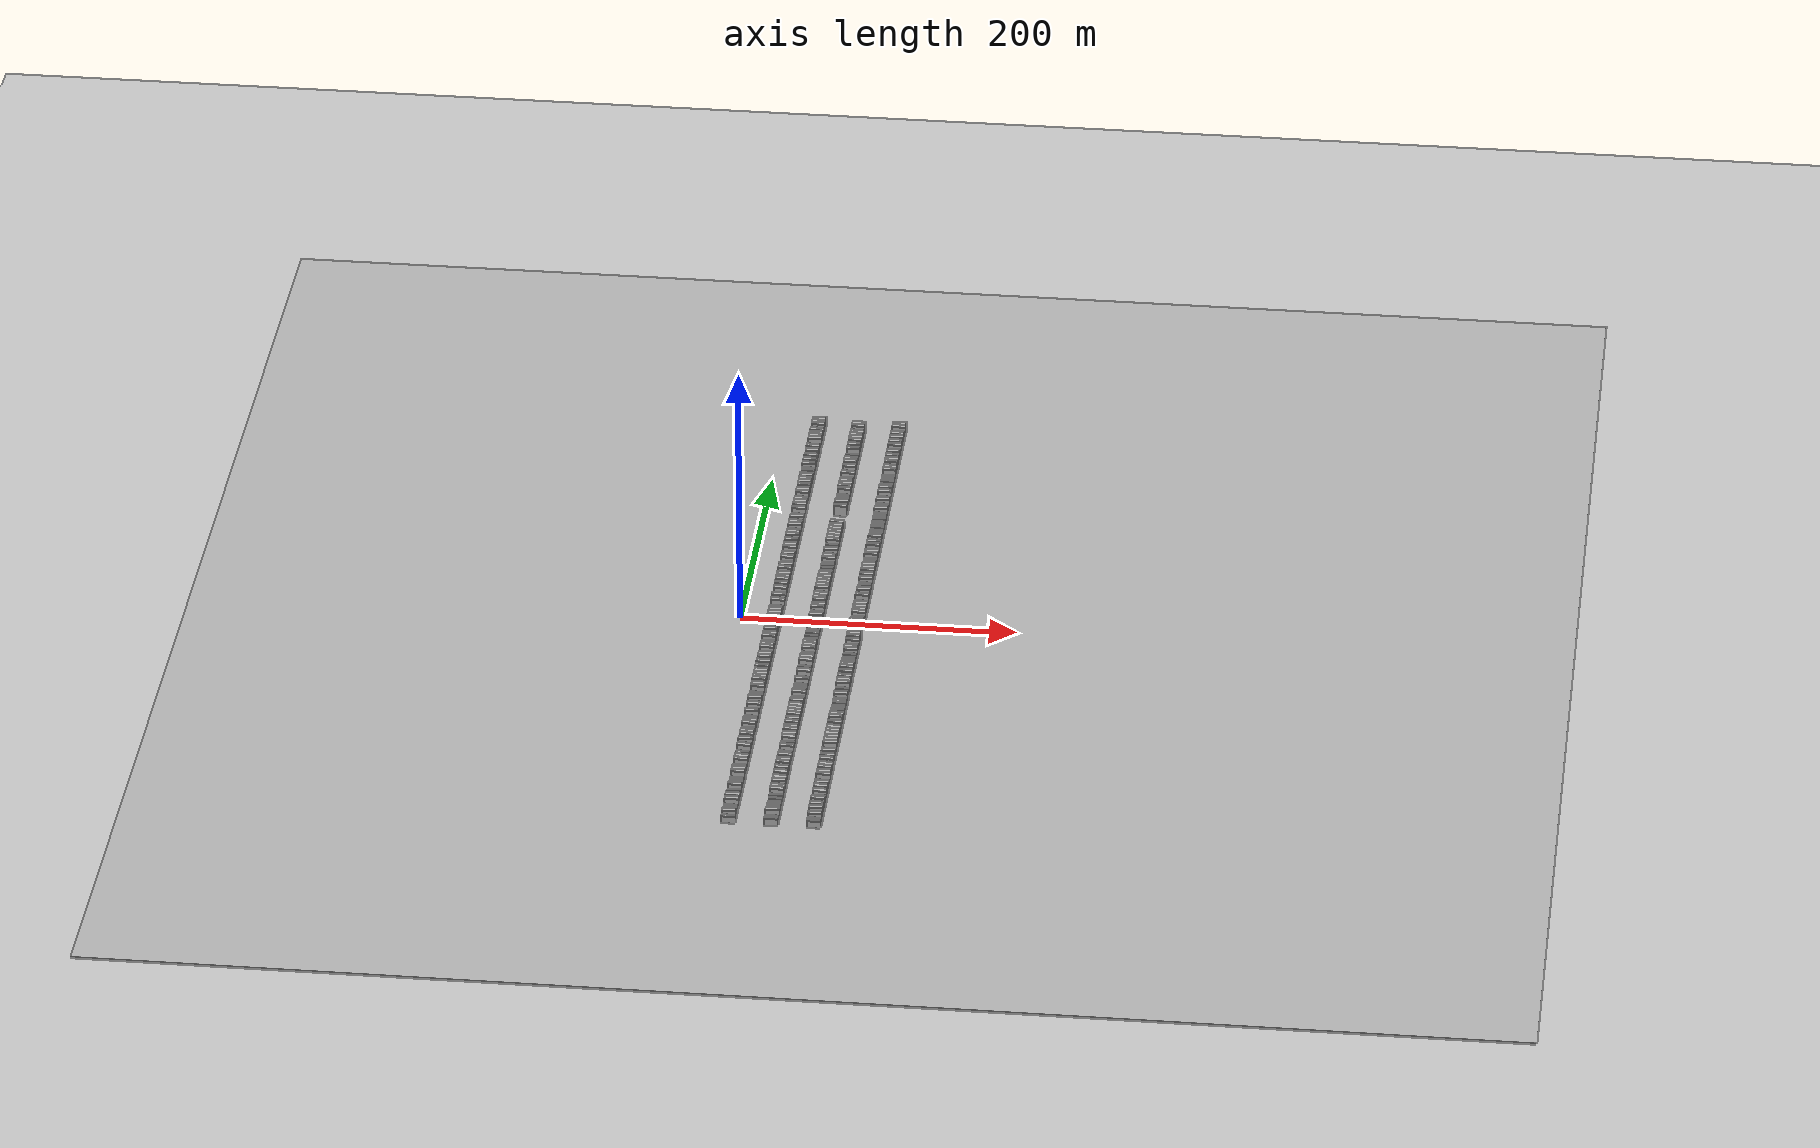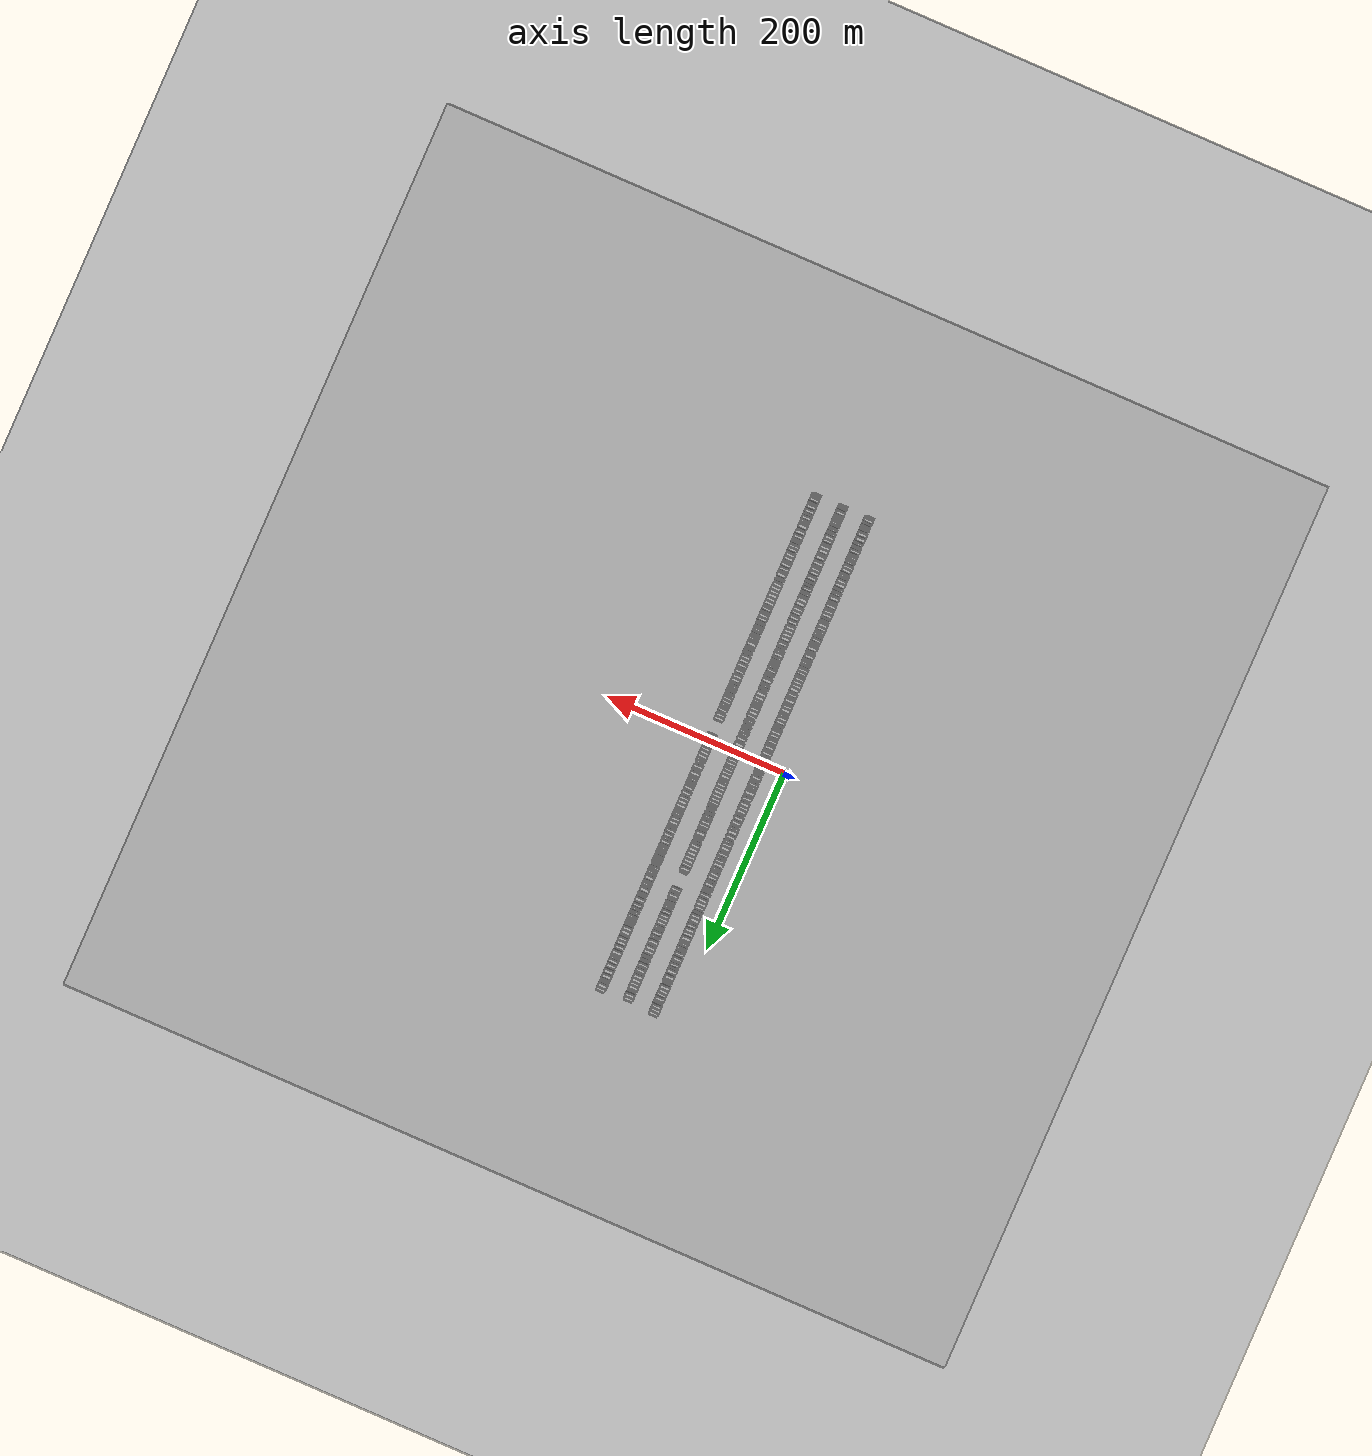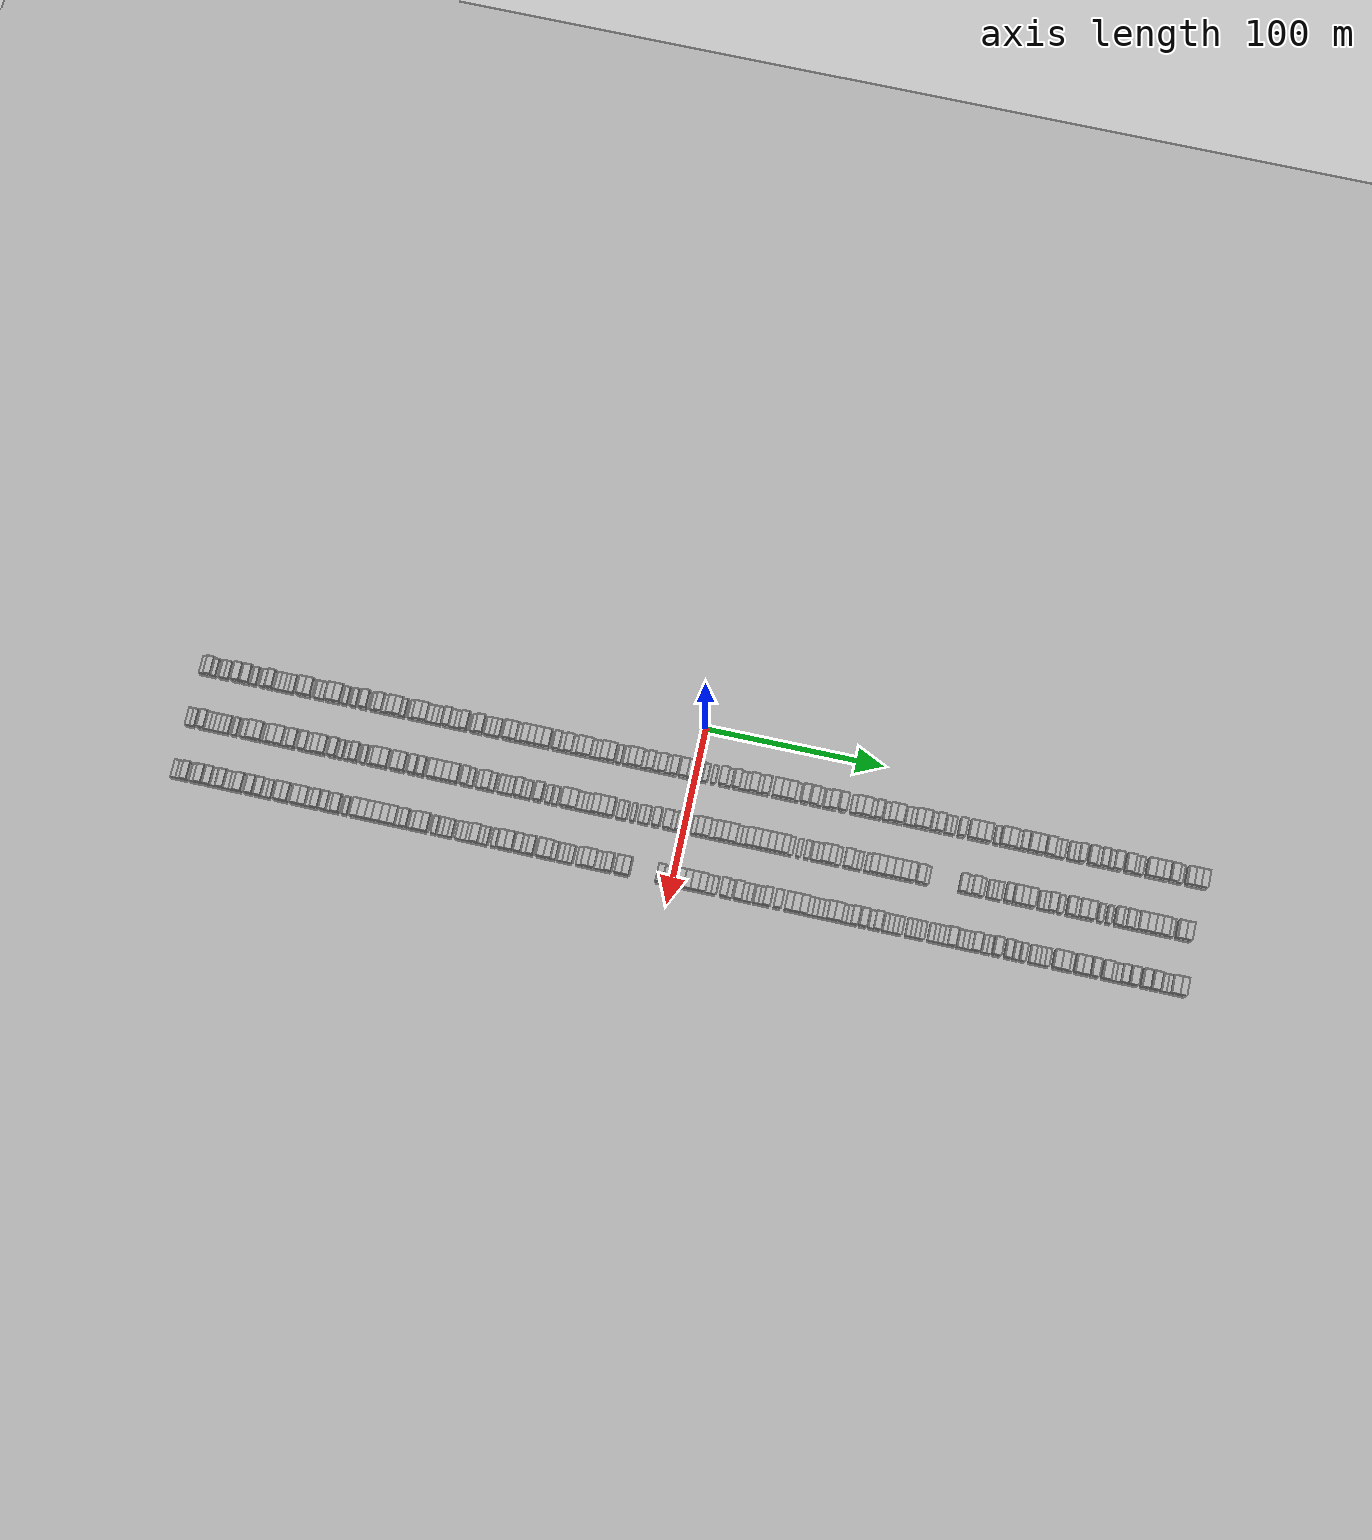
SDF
<?xml version="1.0" encoding="utf-8"?>

<sdf version="1.6">

   <world name="default">

      <gui fullscreen="0">

         <camera name="user_camera">

            <pose>-15 0 4.57585 0 0 0</pose>

            <view_controller>orbit</view_controller>

         </camera>

      </gui>

      <scene>

         <sky>

           <clouds>

             <speed>12</speed>

           </clouds>

         </sky>

         <ambient>0.4 0.4 0.4 1</ambient>

         <background>0.7 0.7 0.7 1</background>

         <shadows>1</shadows>

      </scene>

      <gravity>0 0 -9.8066</gravity>

      <magnetic_field>6e-06 2.3e-05 -4.2e-05</magnetic_field>

      <physics default="0" name="default_physics" type="ode">

         <ode>

            <solver>

               <type>quick</type>

               <iters>10</iters>

               <sor>1.0</sor>

               <use_dynamic_moi_rescaling>0</use_dynamic_moi_rescaling>

            </solver>

            <constraints>

               <cfm>0</cfm>

               <erp>0.2</erp>

               <contact_max_correcting_vel>100</contact_max_correcting_vel>

               <contact_surface_layer>0.001</contact_surface_layer>

            </constraints>

         </ode>

         <max_step_size>0.004</max_step_size>

         <real_time_factor>1</real_time_factor>

         <real_time_update_rate>250</real_time_update_rate>

      </physics>

      <light name="sun" type="directional">

         <cast_shadows>1</cast_shadows>

         <pose>0 0 10 0 0 0</pose>

         <diffuse>0.8 0.8 0.8 1</diffuse>

         <specular>0.2 0.2 0.2 1</specular>

         <attenuation>

            <range>1000</range>

            <constant>0.9</constant>

            <linear>0.01</linear>

            <quadratic>0.001</quadratic>

         </attenuation>

         <direction>-0.5 0.1 -0.9</direction>

      </light>

      <include>

         <name>ground_plane_1</name>

         <uri>model://HANNAS_ground_plane</uri>

         <pose>0 0 0  0 0 0</pose>

      </include>

      <include>

         <name>ground_plane_2</name>

         <uri>model://HANNAS_ground_plane</uri>

         <pose>100 0 0  0 0 0</pose>

      </include>

      <model name="building_1">

         <static>1</static>

         <pose frame="">25.0000 -278.5396 0 0.000000 0.000000 0.000000</pose>

         <link name="link">

            <pose frame="">0 0 3.00 0 0 0</pose>

            <collision name="collision">

               <geometry>

                  <box>

                     <size>10.0000 2.9208 6.0000</size>

                  </box>

               </geometry>

               <max_contacts>10</max_contacts>

               <surface>

                  <contact>

                     <ode/>

                  </contact>

                  <bounce/>

                  <friction>

                     <torsional>

                        <ode/>

                     </torsional>

                     <ode/>

                  </friction>

               </surface>

            </collision>

            <visual name="visual">

               <cast_shadows>0</cast_shadows>

               <geometry>

                  <box>

                     <size>10.0000 2.9208 6.0000</size>

                  </box>

               </geometry>

               <material>

                  <script>

                     <uri>model://HANNAS_wall/materials/scripts</uri>

                     <uri>model://HANNAS_wall/materials/textures</uri>

                     <name>vrc/HANNAS_wall</name>

                  </script>

               </material>

            </visual>

            <self_collide>0</self_collide>

            <enable_wind>0</enable_wind>

            <kinematic>0</kinematic>

         </link>

      </model>

      <model name="building_2">

         <static>1</static>

         <pose frame="">25.0000 -275.1381 0 0.000000 0.000000 0.000000</pose>

         <link name="link">

            <pose frame="">0 0 4.50 0 0 0</pose>

            <collision name="collision">

               <geometry>

                  <box>

                     <size>10.0000 3.8823 9.0000</size>

                  </box>

               </geometry>

               <max_contacts>10</max_contacts>

               <surface>

                  <contact>

                     <ode/>

                  </contact>

                  <bounce/>

                  <friction>

                     <torsional>

                        <ode/>

                     </torsional>

                     <ode/>

                  </friction>

               </surface>

            </collision>

            <visual name="visual">

               <cast_shadows>0</cast_shadows>

               <geometry>

                  <box>

                     <size>10.0000 3.8823 9.0000</size>

                  </box>

               </geometry>

               <material>

                  <script>

                     <uri>model://HANNAS_wall/materials/scripts</uri>

                     <uri>model://HANNAS_wall/materials/textures</uri>

                     <name>vrc/HANNAS_wall</name>

                  </script>

               </material>

            </visual>

            <self_collide>0</self_collide>

            <enable_wind>0</enable_wind>

            <kinematic>0</kinematic>

         </link>

      </model>

      <model name="building_3">

         <static>1</static>

         <pose frame="">25.0000 -271.9334 0 0.000000 0.000000 0.000000</pose>

         <link name="link">

            <pose frame="">0 0 3.00 0 0 0</pose>

            <collision name="collision">

               <geometry>

                  <box>

                     <size>10.0000 2.5270 6.0000</size>

                  </box>

               </geometry>

               <max_contacts>10</max_contacts>

               <surface>

                  <contact>

                     <ode/>

                  </contact>

                  <bounce/>

                  <friction>

                     <torsional>

                        <ode/>

                     </torsional>

                     <ode/>

                  </friction>

               </surface>

            </collision>

            <visual name="visual">

               <cast_shadows>0</cast_shadows>

               <geometry>

                  <box>

                     <size>10.0000 2.5270 6.0000</size>

                  </box>

               </geometry>

               <material>

                  <script>

                     <uri>model://HANNAS_wall/materials/scripts</uri>

                     <uri>model://HANNAS_wall/materials/textures</uri>

                     <name>vrc/HANNAS_wall</name>

                  </script>

               </material>

            </visual>

            <self_collide>0</self_collide>

            <enable_wind>0</enable_wind>

            <kinematic>0</kinematic>

         </link>

      </model>

      <model name="building_4">

         <static>1</static>

         <pose frame="">25.0000 -267.3783 0 0.000000 0.000000 0.000000</pose>

         <link name="link">

            <pose frame="">0 0 3.00 0 0 0</pose>

            <collision name="collision">

               <geometry>

                  <box>

                     <size>10.0000 2.5832 6.0000</size>

                  </box>

               </geometry>

               <max_contacts>10</max_contacts>

               <surface>

                  <contact>

                     <ode/>

                  </contact>

                  <bounce/>

                  <friction>

                     <torsional>

                        <ode/>

                     </torsional>

                     <ode/>

                  </friction>

               </surface>

            </collision>

            <visual name="visual">

               <cast_shadows>0</cast_shadows>

               <geometry>

                  <box>

                     <size>10.0000 2.5832 6.0000</size>

                  </box>

               </geometry>

               <material>

                  <script>

                     <uri>model://HANNAS_wall/materials/scripts</uri>

                     <uri>model://HANNAS_wall/materials/textures</uri>

                     <name>vrc/HANNAS_wall</name>

                  </script>

               </material>

            </visual>

            <self_collide>0</self_collide>

            <enable_wind>0</enable_wind>

            <kinematic>0</kinematic>

         </link>

      </model>

      <model name="building_5">

         <static>1</static>

         <pose frame="">25.0000 -264.7632 0 0.000000 0.000000 0.000000</pose>

         <link name="link">

            <pose frame="">0 0 3.00 0 0 0</pose>

            <collision name="collision">

               <geometry>

                  <box>

                     <size>10.0000 2.6470 6.0000</size>

                  </box>

               </geometry>

               <max_contacts>10</max_contacts>

               <surface>

                  <contact>

                     <ode/>

                  </contact>

                  <bounce/>

                  <friction>

                     <torsional>

                        <ode/>

                     </torsional>

                     <ode/>

                  </friction>

               </surface>

            </collision>

            <visual name="visual">

               <cast_shadows>0</cast_shadows>

               <geometry>

                  <box>

                     <size>10.0000 2.6470 6.0000</size>

                  </box>

               </geometry>

               <material>

                  <script>

                     <uri>model://HANNAS_wall/materials/scripts</uri>

                     <uri>model://HANNAS_wall/materials/textures</uri>

                     <name>vrc/HANNAS_wall</name>

                  </script>

               </material>

            </visual>

            <self_collide>0</self_collide>

            <enable_wind>0</enable_wind>

            <kinematic>0</kinematic>

         </link>

      </model>

      <model name="building_6">

         <static>1</static>

         <pose frame="">25.0000 -259.2759 0 0.000000 0.000000 0.000000</pose>

         <link name="link">

            <pose frame="">0 0 4.50 0 0 0</pose>

            <collision name="collision">

               <geometry>

                  <box>

                     <size>10.0000 4.3277 9.0000</size>

                  </box>

               </geometry>

               <max_contacts>10</max_contacts>

               <surface>

                  <contact>

                     <ode/>

                  </contact>

                  <bounce/>

                  <friction>

                     <torsional>

                        <ode/>

                     </torsional>

                     <ode/>

                  </friction>

               </surface>

            </collision>

            <visual name="visual">

               <cast_shadows>0</cast_shadows>

               <geometry>

                  <box>

                     <size>10.0000 4.3277 9.0000</size>

                  </box>

               </geometry>

               <material>

                  <script>

                     <uri>model://HANNAS_wall/materials/scripts</uri>

                     <uri>model://HANNAS_wall/materials/textures</uri>

                     <name>vrc/HANNAS_wall</name>

                  </script>

               </material>

            </visual>

            <self_collide>0</self_collide>

            <enable_wind>0</enable_wind>

            <kinematic>0</kinematic>

         </link>

      </model>

      <model name="building_7">

         <static>1</static>

         <pose frame="">25.0000 -253.8736 0 0.000000 0.000000 0.000000</pose>

         <link name="link">

            <pose frame="">0 0 4.50 0 0 0</pose>

            <collision name="collision">

               <geometry>

                  <box>

                     <size>10.0000 4.4769 9.0000</size>

                  </box>

               </geometry>

               <max_contacts>10</max_contacts>

               <surface>

                  <contact>

                     <ode/>

                  </contact>

                  <bounce/>

                  <friction>

                     <torsional>

                        <ode/>

                     </torsional>

                     <ode/>

                  </friction>

               </surface>

            </collision>

            <visual name="visual">

               <cast_shadows>0</cast_shadows>

               <geometry>

                  <box>

                     <size>10.0000 4.4769 9.0000</size>

                  </box>

               </geometry>

               <material>

                  <script>

                     <uri>model://HANNAS_wall/materials/scripts</uri>

                     <uri>model://HANNAS_wall/materials/textures</uri>

                     <name>vrc/HANNAS_wall</name>

                  </script>

               </material>

            </visual>

            <self_collide>0</self_collide>

            <enable_wind>0</enable_wind>

            <kinematic>0</kinematic>

         </link>

      </model>

      <model name="building_8">

         <static>1</static>

         <pose frame="">25.0000 -249.1465 0 0.000000 0.000000 0.000000</pose>

         <link name="link">

            <pose frame="">0 0 3.00 0 0 0</pose>

            <collision name="collision">

               <geometry>

                  <box>

                     <size>10.0000 2.9773 6.0000</size>

                  </box>

               </geometry>

               <max_contacts>10</max_contacts>

               <surface>

                  <contact>

                     <ode/>

                  </contact>

                  <bounce/>

                  <friction>

                     <torsional>

                        <ode/>

                     </torsional>

                     <ode/>

                  </friction>

               </surface>

            </collision>

            <visual name="visual">

               <cast_shadows>0</cast_shadows>

               <geometry>

                  <box>

                     <size>10.0000 2.9773 6.0000</size>

                  </box>

               </geometry>

               <material>

                  <script>

                     <uri>model://HANNAS_wall/materials/scripts</uri>

                     <uri>model://HANNAS_wall/materials/textures</uri>

                     <name>vrc/HANNAS_wall</name>

                  </script>

               </material>

            </visual>

            <self_collide>0</self_collide>

            <enable_wind>0</enable_wind>

            <kinematic>0</kinematic>

         </link>

      </model>

      <model name="building_9">

         <static>1</static>

         <pose frame="">25.0000 -244.3218 0 0.000000 0.000000 0.000000</pose>

         <link name="link">

            <pose frame="">0 0 3.00 0 0 0</pose>

            <collision name="collision">

               <geometry>

                  <box>

                     <size>10.0000 2.6721 6.0000</size>

                  </box>

               </geometry>

               <max_contacts>10</max_contacts>

               <surface>

                  <contact>

                     <ode/>

                  </contact>

                  <bounce/>

                  <friction>

                     <torsional>

                        <ode/>

                     </torsional>

                     <ode/>

                  </friction>

               </surface>

            </collision>

            <visual name="visual">

               <cast_shadows>0</cast_shadows>

               <geometry>

                  <box>

                     <size>10.0000 2.6721 6.0000</size>

                  </box>

               </geometry>

               <material>

                  <script>

                     <uri>model://HANNAS_wall/materials/scripts</uri>

                     <uri>model://HANNAS_wall/materials/textures</uri>

                     <name>vrc/HANNAS_wall</name>

                  </script>

               </material>

            </visual>

            <self_collide>0</self_collide>

            <enable_wind>0</enable_wind>

            <kinematic>0</kinematic>

         </link>

      </model>

      <model name="building_10">

         <static>1</static>

         <pose frame="">25.0000 -240.1321 0 0.000000 0.000000 0.000000</pose>

         <link name="link">

            <pose frame="">0 0 4.50 0 0 0</pose>

            <collision name="collision">

               <geometry>

                  <box>

                     <size>10.0000 3.7073 9.0000</size>

                  </box>

               </geometry>

               <max_contacts>10</max_contacts>

               <surface>

                  <contact>

                     <ode/>

                  </contact>

                  <bounce/>

                  <friction>

                     <torsional>

                        <ode/>

                     </torsional>

                     <ode/>

                  </friction>

               </surface>

            </collision>

            <visual name="visual">

               <cast_shadows>0</cast_shadows>

               <geometry>

                  <box>

                     <size>10.0000 3.7073 9.0000</size>

                  </box>

               </geometry>

               <material>

                  <script>

                     <uri>model://HANNAS_wall/materials/scripts</uri>

                     <uri>model://HANNAS_wall/materials/textures</uri>

                     <name>vrc/HANNAS_wall</name>

                  </script>

               </material>

            </visual>

            <self_collide>0</self_collide>

            <enable_wind>0</enable_wind>

            <kinematic>0</kinematic>

         </link>

      </model>

      <model name="building_11">

         <static>1</static>

         <pose frame="">25.0000 -236.0598 0 0.000000 0.000000 0.000000</pose>

         <link name="link">

            <pose frame="">0 0 3.00 0 0 0</pose>

            <collision name="collision">

               <geometry>

                  <box>

                     <size>10.0000 2.4374 6.0000</size>

                  </box>

               </geometry>

               <max_contacts>10</max_contacts>

               <surface>

                  <contact>

                     <ode/>

                  </contact>

                  <bounce/>

                  <friction>

                     <torsional>

                        <ode/>

                     </torsional>

                     <ode/>

                  </friction>

               </surface>

            </collision>

            <visual name="visual">

               <cast_shadows>0</cast_shadows>

               <geometry>

                  <box>

                     <size>10.0000 2.4374 6.0000</size>

                  </box>

               </geometry>

               <material>

                  <script>

                     <uri>model://HANNAS_wall/materials/scripts</uri>

                     <uri>model://HANNAS_wall/materials/textures</uri>

                     <name>vrc/HANNAS_wall</name>

                  </script>

               </material>

            </visual>

            <self_collide>0</self_collide>

            <enable_wind>0</enable_wind>

            <kinematic>0</kinematic>

         </link>

      </model>

      <model name="building_12">

         <static>1</static>

         <pose frame="">25.0000 -233.3517 0 0.000000 0.000000 0.000000</pose>

         <link name="link">

            <pose frame="">0 0 3.00 0 0 0</pose>

            <collision name="collision">

               <geometry>

                  <box>

                     <size>10.0000 2.9788 6.0000</size>

                  </box>

               </geometry>

               <max_contacts>10</max_contacts>

               <surface>

                  <contact>

                     <ode/>

                  </contact>

                  <bounce/>

                  <friction>

                     <torsional>

                        <ode/>

                     </torsional>

                     <ode/>

                  </friction>

               </surface>

            </collision>

            <visual name="visual">

               <cast_shadows>0</cast_shadows>

               <geometry>

                  <box>

                     <size>10.0000 2.9788 6.0000</size>

                  </box>

               </geometry>

               <material>

                  <script>

                     <uri>model://HANNAS_wall/materials/scripts</uri>

                     <uri>model://HANNAS_wall/materials/textures</uri>

                     <name>vrc/HANNAS_wall</name>

                  </script>

               </material>

            </visual>

            <self_collide>0</self_collide>

            <enable_wind>0</enable_wind>

            <kinematic>0</kinematic>

         </link>

      </model>

      <model name="building_13">

         <static>1</static>

         <pose frame="">25.0000 -230.6579 0 0.000000 0.000000 0.000000</pose>

         <link name="link">

            <pose frame="">0 0 3.00 0 0 0</pose>

            <collision name="collision">

               <geometry>

                  <box>

                     <size>10.0000 2.4088 6.0000</size>

                  </box>

               </geometry>

               <max_contacts>10</max_contacts>

               <surface>

                  <contact>

                     <ode/>

                  </contact>

                  <bounce/>

                  <friction>

                     <torsional>

                        <ode/>

                     </torsional>

                     <ode/>

                  </friction>

               </surface>

            </collision>

            <visual name="visual">

               <cast_shadows>0</cast_shadows>

               <geometry>

                  <box>

                     <size>10.0000 2.4088 6.0000</size>

                  </box>

               </geometry>

               <material>

                  <script>

                     <uri>model://HANNAS_wall/materials/scripts</uri>

                     <uri>model://HANNAS_wall/materials/textures</uri>

                     <name>vrc/HANNAS_wall</name>

                  </script>

               </material>

            </visual>

            <self_collide>0</self_collide>

            <enable_wind>0</enable_wind>

            <kinematic>0</kinematic>

         </link>

      </model>

      <model name="building_14">

         <static>1</static>

         <pose frame="">25.0000 -227.9544 0 0.000000 0.000000 0.000000</pose>

         <link name="link">

            <pose frame="">0 0 3.00 0 0 0</pose>

            <collision name="collision">

               <geometry>

                  <box>

                     <size>10.0000 2.9981 6.0000</size>

                  </box>

               </geometry>

               <max_contacts>10</max_contacts>

               <surface>

                  <contact>

                     <ode/>

                  </contact>

                  <bounce/>

                  <friction>

                     <torsional>

                        <ode/>

                     </torsional>

                     <ode/>

                  </friction>

               </surface>

            </collision>

            <visual name="visual">

               <cast_shadows>0</cast_shadows>

               <geometry>

                  <box>

                     <size>10.0000 2.9981 6.0000</size>

                  </box>

               </geometry>

               <material>

                  <script>

                     <uri>model://HANNAS_wall/materials/scripts</uri>

                     <uri>model://HANNAS_wall/materials/textures</uri>

                     <name>vrc/HANNAS_wall</name>

                  </script>

               </material>

            </visual>

            <self_collide>0</self_collide>

            <enable_wind>0</enable_wind>

            <kinematic>0</kinematic>

         </link>

      </model>

      <model name="building_15">

         <static>1</static>

         <pose frame="">25.0000 -222.5823 0 0.000000 0.000000 0.000000</pose>

         <link name="link">

            <pose frame="">0 0 4.50 0 0 0</pose>

            <collision name="collision">

               <geometry>

                  <box>

                     <size>10.0000 3.7462 9.0000</size>

                  </box>

               </geometry>

               <max_contacts>10</max_contacts>

               <surface>

                  <contact>

                     <ode/>

                  </contact>

                  <bounce/>

                  <friction>

                     <torsional>

                        <ode/>

                     </torsional>

                     <ode/>

                  </friction>

               </surface>

            </collision>

            <visual name="visual">

               <cast_shadows>0</cast_shadows>

               <geometry>

                  <box>

                     <size>10.0000 3.7462 9.0000</size>

                  </box>

               </geometry>

               <material>

                  <script>

                     <uri>model://HANNAS_wall/materials/scripts</uri>

                     <uri>model://HANNAS_wall/materials/textures</uri>

                     <name>vrc/HANNAS_wall</name>

                  </script>

               </material>

            </visual>

            <self_collide>0</self_collide>

            <enable_wind>0</enable_wind>

            <kinematic>0</kinematic>

         </link>

      </model>

      <model name="building_16">

         <static>1</static>

         <pose frame="">25.0000 -218.6534 0 0.000000 0.000000 0.000000</pose>

         <link name="link">

            <pose frame="">0 0 4.50 0 0 0</pose>

            <collision name="collision">

               <geometry>

                  <box>

                     <size>10.0000 4.1116 9.0000</size>

                  </box>

               </geometry>

               <max_contacts>10</max_contacts>

               <surface>

                  <contact>

                     <ode/>

                  </contact>

                  <bounce/>

                  <friction>

                     <torsional>

                        <ode/>

                     </torsional>

                     <ode/>

                  </friction>

               </surface>

            </collision>

            <visual name="visual">

               <cast_shadows>0</cast_shadows>

               <geometry>

                  <box>

                     <size>10.0000 4.1116 9.0000</size>

                  </box>

               </geometry>

               <material>

                  <script>

                     <uri>model://HANNAS_wall/materials/scripts</uri>

                     <uri>model://HANNAS_wall/materials/textures</uri>

                     <name>vrc/HANNAS_wall</name>

                  </script>

               </material>

            </visual>

            <self_collide>0</self_collide>

            <enable_wind>0</enable_wind>

            <kinematic>0</kinematic>

         </link>

      </model>

      <model name="building_17">

         <static>1</static>

         <pose frame="">25.0000 -213.1574 0 0.000000 0.000000 0.000000</pose>

         <link name="link">

            <pose frame="">0 0 3.00 0 0 0</pose>

            <collision name="collision">

               <geometry>

                  <box>

                     <size>10.0000 2.8804 6.0000</size>

                  </box>

               </geometry>

               <max_contacts>10</max_contacts>

               <surface>

                  <contact>

                     <ode/>

                  </contact>

                  <bounce/>

                  <friction>

                     <torsional>

                        <ode/>

                     </torsional>

                     <ode/>

                  </friction>

               </surface>

            </collision>

            <visual name="visual">

               <cast_shadows>0</cast_shadows>

               <geometry>

                  <box>

                     <size>10.0000 2.8804 6.0000</size>

                  </box>

               </geometry>

               <material>

                  <script>

                     <uri>model://HANNAS_wall/materials/scripts</uri>

                     <uri>model://HANNAS_wall/materials/textures</uri>

                     <name>vrc/HANNAS_wall</name>

                  </script>

               </material>

            </visual>

            <self_collide>0</self_collide>

            <enable_wind>0</enable_wind>

            <kinematic>0</kinematic>

         </link>

      </model>

      <model name="building_18">

         <static>1</static>

         <pose frame="">25.0000 -210.4344 0 0.000000 0.000000 0.000000</pose>

         <link name="link">

            <pose frame="">0 0 3.00 0 0 0</pose>

            <collision name="collision">

               <geometry>

                  <box>

                     <size>10.0000 2.5655 6.0000</size>

                  </box>

               </geometry>

               <max_contacts>10</max_contacts>

               <surface>

                  <contact>

                     <ode/>

                  </contact>

                  <bounce/>

                  <friction>

                     <torsional>

                        <ode/>

                     </torsional>

                     <ode/>

                  </friction>

               </surface>

            </collision>

            <visual name="visual">

               <cast_shadows>0</cast_shadows>

               <geometry>

                  <box>

                     <size>10.0000 2.5655 6.0000</size>

                  </box>

               </geometry>

               <material>

                  <script>

                     <uri>model://HANNAS_wall/materials/scripts</uri>

                     <uri>model://HANNAS_wall/materials/textures</uri>

                     <name>vrc/HANNAS_wall</name>

                  </script>

               </material>

            </visual>

            <self_collide>0</self_collide>

            <enable_wind>0</enable_wind>

            <kinematic>0</kinematic>

         </link>

      </model>

      <model name="building_19">

         <static>1</static>

         <pose frame="">25.0000 -206.1890 0 0.000000 0.000000 0.000000</pose>

         <link name="link">

            <pose frame="">0 0 4.50 0 0 0</pose>

            <collision name="collision">

               <geometry>

                  <box>

                     <size>10.0000 3.9254 9.0000</size>

                  </box>

               </geometry>

               <max_contacts>10</max_contacts>

               <surface>

                  <contact>

                     <ode/>

                  </contact>

                  <bounce/>

                  <friction>

                     <torsional>

                        <ode/>

                     </torsional>

                     <ode/>

                  </friction>

               </surface>

            </collision>

            <visual name="visual">

               <cast_shadows>0</cast_shadows>

               <geometry>

                  <box>

                     <size>10.0000 3.9254 9.0000</size>

                  </box>

               </geometry>

               <material>

                  <script>

                     <uri>model://HANNAS_wall/materials/scripts</uri>

                     <uri>model://HANNAS_wall/materials/textures</uri>

                     <name>vrc/HANNAS_wall</name>

                  </script>

               </material>

            </visual>

            <self_collide>0</self_collide>

            <enable_wind>0</enable_wind>

            <kinematic>0</kinematic>

         </link>

      </model>

      <model name="building_20">

         <static>1</static>

         <pose frame="">25.0000 -202.0667 0 0.000000 0.000000 0.000000</pose>

         <link name="link">

            <pose frame="">0 0 4.50 0 0 0</pose>

            <collision name="collision">

               <geometry>

                  <box>

                     <size>10.0000 4.3190 9.0000</size>

                  </box>

               </geometry>

               <max_contacts>10</max_contacts>

               <surface>

                  <contact>

                     <ode/>

                  </contact>

                  <bounce/>

                  <friction>

                     <torsional>

                        <ode/>

                     </torsional>

                     <ode/>

                  </friction>

               </surface>

            </collision>

            <visual name="visual">

               <cast_shadows>0</cast_shadows>

               <geometry>

                  <box>

                     <size>10.0000 4.3190 9.0000</size>

                  </box>

               </geometry>

               <material>

                  <script>

                     <uri>model://HANNAS_wall/materials/scripts</uri>

                     <uri>model://HANNAS_wall/materials/textures</uri>

                     <name>vrc/HANNAS_wall</name>

                  </script>

               </material>

            </visual>

            <self_collide>0</self_collide>

            <enable_wind>0</enable_wind>

            <kinematic>0</kinematic>

         </link>

      </model>

      <model name="building_21">

         <static>1</static>

         <pose frame="">25.0000 -197.4640 0 0.000000 0.000000 0.000000</pose>

         <link name="link">

            <pose frame="">0 0 3.00 0 0 0</pose>

            <collision name="collision">

               <geometry>

                  <box>

                     <size>10.0000 2.8864 6.0000</size>

                  </box>

               </geometry>

               <max_contacts>10</max_contacts>

               <surface>

                  <contact>

                     <ode/>

                  </contact>

                  <bounce/>

                  <friction>

                     <torsional>

                        <ode/>

                     </torsional>

                     <ode/>

                  </friction>

               </surface>

            </collision>

            <visual name="visual">

               <cast_shadows>0</cast_shadows>

               <geometry>

                  <box>

                     <size>10.0000 2.8864 6.0000</size>

                  </box>

               </geometry>

               <material>

                  <script>

                     <uri>model://HANNAS_wall/materials/scripts</uri>

                     <uri>model://HANNAS_wall/materials/textures</uri>

                     <name>vrc/HANNAS_wall</name>

                  </script>

               </material>

            </visual>

            <self_collide>0</self_collide>

            <enable_wind>0</enable_wind>

            <kinematic>0</kinematic>

         </link>

      </model>

      <model name="building_22">

         <static>1</static>

         <pose frame="">25.0000 -192.5317 0 0.000000 0.000000 0.000000</pose>

         <link name="link">

            <pose frame="">0 0 3.00 0 0 0</pose>

            <collision name="collision">

               <geometry>

                  <box>

                     <size>10.0000 2.9783 6.0000</size>

                  </box>

               </geometry>

               <max_contacts>10</max_contacts>

               <surface>

                  <contact>

                     <ode/>

                  </contact>

                  <bounce/>

                  <friction>

                     <torsional>

                        <ode/>

                     </torsional>

                     <ode/>

                  </friction>

               </surface>

            </collision>

            <visual name="visual">

               <cast_shadows>0</cast_shadows>

               <geometry>

                  <box>

                     <size>10.0000 2.9783 6.0000</size>

                  </box>

               </geometry>

               <material>

                  <script>

                     <uri>model://HANNAS_wall/materials/scripts</uri>

                     <uri>model://HANNAS_wall/materials/textures</uri>

                     <name>vrc/HANNAS_wall</name>

                  </script>

               </material>

            </visual>

            <self_collide>0</self_collide>

            <enable_wind>0</enable_wind>

            <kinematic>0</kinematic>

         </link>

      </model>

      <model name="building_23">

         <static>1</static>

         <pose frame="">25.0000 -186.9308 0 0.000000 0.000000 0.000000</pose>

         <link name="link">

            <pose frame="">0 0 4.50 0 0 0</pose>

            <collision name="collision">

               <geometry>

                  <box>

                     <size>10.0000 4.2235 9.0000</size>

                  </box>

               </geometry>

               <max_contacts>10</max_contacts>

               <surface>

                  <contact>

                     <ode/>

                  </contact>

                  <bounce/>

                  <friction>

                     <torsional>

                        <ode/>

                     </torsional>

                     <ode/>

                  </friction>

               </surface>

            </collision>

            <visual name="visual">

               <cast_shadows>0</cast_shadows>

               <geometry>

                  <box>

                     <size>10.0000 4.2235 9.0000</size>

                  </box>

               </geometry>

               <material>

                  <script>

                     <uri>model://HANNAS_wall/materials/scripts</uri>

                     <uri>model://HANNAS_wall/materials/textures</uri>

                     <name>vrc/HANNAS_wall</name>

                  </script>

               </material>

            </visual>

            <self_collide>0</self_collide>

            <enable_wind>0</enable_wind>

            <kinematic>0</kinematic>

         </link>

      </model>

      <model name="building_24">

         <static>1</static>

         <pose frame="">25.0000 -181.5010 0 0.000000 0.000000 0.000000</pose>

         <link name="link">

            <pose frame="">0 0 3.00 0 0 0</pose>

            <collision name="collision">

               <geometry>

                  <box>

                     <size>10.0000 2.6361 6.0000</size>

                  </box>

               </geometry>

               <max_contacts>10</max_contacts>

               <surface>

                  <contact>

                     <ode/>

                  </contact>

                  <bounce/>

                  <friction>

                     <torsional>

                        <ode/>

                     </torsional>

                     <ode/>

                  </friction>

               </surface>

            </collision>

            <visual name="visual">

               <cast_shadows>0</cast_shadows>

               <geometry>

                  <box>

                     <size>10.0000 2.6361 6.0000</size>

                  </box>

               </geometry>

               <material>

                  <script>

                     <uri>model://HANNAS_wall/materials/scripts</uri>

                     <uri>model://HANNAS_wall/materials/textures</uri>

                     <name>vrc/HANNAS_wall</name>

                  </script>

               </material>

            </visual>

            <self_collide>0</self_collide>

            <enable_wind>0</enable_wind>

            <kinematic>0</kinematic>

         </link>

      </model>

      <model name="building_25">

         <static>1</static>

         <pose frame="">25.0000 -178.2582 0 0.000000 0.000000 0.000000</pose>

         <link name="link">

            <pose frame="">0 0 4.50 0 0 0</pose>

            <collision name="collision">

               <geometry>

                  <box>

                     <size>10.0000 3.8495 9.0000</size>

                  </box>

               </geometry>

               <max_contacts>10</max_contacts>

               <surface>

                  <contact>

                     <ode/>

                  </contact>

                  <bounce/>

                  <friction>

                     <torsional>

                        <ode/>

                     </torsional>

                     <ode/>

                  </friction>

               </surface>

            </collision>

            <visual name="visual">

               <cast_shadows>0</cast_shadows>

               <geometry>

                  <box>

                     <size>10.0000 3.8495 9.0000</size>

                  </box>

               </geometry>

               <material>

                  <script>

                     <uri>model://HANNAS_wall/materials/scripts</uri>

                     <uri>model://HANNAS_wall/materials/textures</uri>

                     <name>vrc/HANNAS_wall</name>

                  </script>

               </material>

            </visual>

            <self_collide>0</self_collide>

            <enable_wind>0</enable_wind>

            <kinematic>0</kinematic>

         </link>

      </model>

      <model name="building_26">

         <static>1</static>

         <pose frame="">25.0000 -175.0276 0 0.000000 0.000000 0.000000</pose>

         <link name="link">

            <pose frame="">0 0 3.00 0 0 0</pose>

            <collision name="collision">

               <geometry>

                  <box>

                     <size>10.0000 2.6116 6.0000</size>

                  </box>

               </geometry>

               <max_contacts>10</max_contacts>

               <surface>

                  <contact>

                     <ode/>

                  </contact>

                  <bounce/>

                  <friction>

                     <torsional>

                        <ode/>

                     </torsional>

                     <ode/>

                  </friction>

               </surface>

            </collision>

            <visual name="visual">

               <cast_shadows>0</cast_shadows>

               <geometry>

                  <box>

                     <size>10.0000 2.6116 6.0000</size>

                  </box>

               </geometry>

               <material>

                  <script>

                     <uri>model://HANNAS_wall/materials/scripts</uri>

                     <uri>model://HANNAS_wall/materials/textures</uri>

                     <name>vrc/HANNAS_wall</name>

                  </script>

               </material>

            </visual>

            <self_collide>0</self_collide>

            <enable_wind>0</enable_wind>

            <kinematic>0</kinematic>

         </link>

      </model>

      <model name="building_27">

         <static>1</static>

         <pose frame="">25.0000 -171.8436 0 0.000000 0.000000 0.000000</pose>

         <link name="link">

            <pose frame="">0 0 4.50 0 0 0</pose>

            <collision name="collision">

               <geometry>

                  <box>

                     <size>10.0000 3.7565 9.0000</size>

                  </box>

               </geometry>

               <max_contacts>10</max_contacts>

               <surface>

                  <contact>

                     <ode/>

                  </contact>

                  <bounce/>

                  <friction>

                     <torsional>

                        <ode/>

                     </torsional>

                     <ode/>

                  </friction>

               </surface>

            </collision>

            <visual name="visual">

               <cast_shadows>0</cast_shadows>

               <geometry>

                  <box>

                     <size>10.0000 3.7565 9.0000</size>

                  </box>

               </geometry>

               <material>

                  <script>

                     <uri>model://HANNAS_wall/materials/scripts</uri>

                     <uri>model://HANNAS_wall/materials/textures</uri>

                     <name>vrc/HANNAS_wall</name>

                  </script>

               </material>

            </visual>

            <self_collide>0</self_collide>

            <enable_wind>0</enable_wind>

            <kinematic>0</kinematic>

         </link>

      </model>

      <model name="building_28">

         <static>1</static>

         <pose frame="">25.0000 -167.9490 0 0.000000 0.000000 0.000000</pose>

         <link name="link">

            <pose frame="">0 0 4.50 0 0 0</pose>

            <collision name="collision">

               <geometry>

                  <box>

                     <size>10.0000 4.0327 9.0000</size>

                  </box>

               </geometry>

               <max_contacts>10</max_contacts>

               <surface>

                  <contact>

                     <ode/>

                  </contact>

                  <bounce/>

                  <friction>

                     <torsional>

                        <ode/>

                     </torsional>

                     <ode/>

                  </friction>

               </surface>

            </collision>

            <visual name="visual">

               <cast_shadows>0</cast_shadows>

               <geometry>

                  <box>

                     <size>10.0000 4.0327 9.0000</size>

                  </box>

               </geometry>

               <material>

                  <script>

                     <uri>model://HANNAS_wall/materials/scripts</uri>

                     <uri>model://HANNAS_wall/materials/textures</uri>

                     <name>vrc/HANNAS_wall</name>

                  </script>

               </material>

            </visual>

            <self_collide>0</self_collide>

            <enable_wind>0</enable_wind>

            <kinematic>0</kinematic>

         </link>

      </model>

      <model name="building_29">

         <static>1</static>

         <pose frame="">25.0000 -164.7011 0 0.000000 0.000000 0.000000</pose>

         <link name="link">

            <pose frame="">0 0 3.00 0 0 0</pose>

            <collision name="collision">

               <geometry>

                  <box>

                     <size>10.0000 2.4632 6.0000</size>

                  </box>

               </geometry>

               <max_contacts>10</max_contacts>

               <surface>

                  <contact>

                     <ode/>

                  </contact>

                  <bounce/>

                  <friction>

                     <torsional>

                        <ode/>

                     </torsional>

                     <ode/>

                  </friction>

               </surface>

            </collision>

            <visual name="visual">

               <cast_shadows>0</cast_shadows>

               <geometry>

                  <box>

                     <size>10.0000 2.4632 6.0000</size>

                  </box>

               </geometry>

               <material>

                  <script>

                     <uri>model://HANNAS_wall/materials/scripts</uri>

                     <uri>model://HANNAS_wall/materials/textures</uri>

                     <name>vrc/HANNAS_wall</name>

                  </script>

               </material>

            </visual>

            <self_collide>0</self_collide>

            <enable_wind>0</enable_wind>

            <kinematic>0</kinematic>

         </link>

      </model>

      <model name="building_30">

         <static>1</static>

         <pose frame="">25.0000 -160.2029 0 0.000000 0.000000 0.000000</pose>

         <link name="link">

            <pose frame="">0 0 3.00 0 0 0</pose>

            <collision name="collision">

               <geometry>

                  <box>

                     <size>10.0000 2.5332 6.0000</size>

                  </box>

               </geometry>

               <max_contacts>10</max_contacts>

               <surface>

                  <contact>

                     <ode/>

                  </contact>

                  <bounce/>

                  <friction>

                     <torsional>

                        <ode/>

                     </torsional>

                     <ode/>

                  </friction>

               </surface>

            </collision>

            <visual name="visual">

               <cast_shadows>0</cast_shadows>

               <geometry>

                  <box>

                     <size>10.0000 2.5332 6.0000</size>

                  </box>

               </geometry>

               <material>

                  <script>

                     <uri>model://HANNAS_wall/materials/scripts</uri>

                     <uri>model://HANNAS_wall/materials/textures</uri>

                     <name>vrc/HANNAS_wall</name>

                  </script>

               </material>

            </visual>

            <self_collide>0</self_collide>

            <enable_wind>0</enable_wind>

            <kinematic>0</kinematic>

         </link>

      </model>

      <model name="building_31">

         <static>1</static>

         <pose frame="">25.0000 -156.8701 0 0.000000 0.000000 0.000000</pose>

         <link name="link">

            <pose frame="">0 0 4.50 0 0 0</pose>

            <collision name="collision">

               <geometry>

                  <box>

                     <size>10.0000 4.1325 9.0000</size>

                  </box>

               </geometry>

               <max_contacts>10</max_contacts>

               <surface>

                  <contact>

                     <ode/>

                  </contact>

                  <bounce/>

                  <friction>

                     <torsional>

                        <ode/>

                     </torsional>

                     <ode/>

                  </friction>

               </surface>

            </collision>

            <visual name="visual">

               <cast_shadows>0</cast_shadows>

               <geometry>

                  <box>

                     <size>10.0000 4.1325 9.0000</size>

                  </box>

               </geometry>

               <material>

                  <script>

                     <uri>model://HANNAS_wall/materials/scripts</uri>

                     <uri>model://HANNAS_wall/materials/textures</uri>

                     <name>vrc/HANNAS_wall</name>

                  </script>

               </material>

            </visual>

            <self_collide>0</self_collide>

            <enable_wind>0</enable_wind>

            <kinematic>0</kinematic>

         </link>

      </model>

      <model name="building_32">

         <static>1</static>

         <pose frame="">25.0000 -152.9839 0 0.000000 0.000000 0.000000</pose>

         <link name="link">

            <pose frame="">0 0 4.50 0 0 0</pose>

            <collision name="collision">

               <geometry>

                  <box>

                     <size>10.0000 3.6400 9.0000</size>

                  </box>

               </geometry>

               <max_contacts>10</max_contacts>

               <surface>

                  <contact>

                     <ode/>

                  </contact>

                  <bounce/>

                  <friction>

                     <torsional>

                        <ode/>

                     </torsional>

                     <ode/>

                  </friction>

               </surface>

            </collision>

            <visual name="visual">

               <cast_shadows>0</cast_shadows>

               <geometry>

                  <box>

                     <size>10.0000 3.6400 9.0000</size>

                  </box>

               </geometry>

               <material>

                  <script>

                     <uri>model://HANNAS_wall/materials/scripts</uri>

                     <uri>model://HANNAS_wall/materials/textures</uri>

                     <name>vrc/HANNAS_wall</name>

                  </script>

               </material>

            </visual>

            <self_collide>0</self_collide>

            <enable_wind>0</enable_wind>

            <kinematic>0</kinematic>

         </link>

      </model>

      <model name="building_33">

         <static>1</static>

         <pose frame="">25.0000 -149.7159 0 0.000000 0.000000 0.000000</pose>

         <link name="link">

            <pose frame="">0 0 3.00 0 0 0</pose>

            <collision name="collision">

               <geometry>

                  <box>

                     <size>10.0000 2.8959 6.0000</size>

                  </box>

               </geometry>

               <max_contacts>10</max_contacts>

               <surface>

                  <contact>

                     <ode/>

                  </contact>

                  <bounce/>

                  <friction>

                     <torsional>

                        <ode/>

                     </torsional>

                     <ode/>

                  </friction>

               </surface>

            </collision>

            <visual name="visual">

               <cast_shadows>0</cast_shadows>

               <geometry>

                  <box>

                     <size>10.0000 2.8959 6.0000</size>

                  </box>

               </geometry>

               <material>

                  <script>

                     <uri>model://HANNAS_wall/materials/scripts</uri>

                     <uri>model://HANNAS_wall/materials/textures</uri>

                     <name>vrc/HANNAS_wall</name>

                  </script>

               </material>

            </visual>

            <self_collide>0</self_collide>

            <enable_wind>0</enable_wind>

            <kinematic>0</kinematic>

         </link>

      </model>

      <model name="building_34">

         <static>1</static>

         <pose frame="">25.0000 -146.8336 0 0.000000 0.000000 0.000000</pose>

         <link name="link">

            <pose frame="">0 0 3.00 0 0 0</pose>

            <collision name="collision">

               <geometry>

                  <box>

                     <size>10.0000 2.8687 6.0000</size>

                  </box>

               </geometry>

               <max_contacts>10</max_contacts>

               <surface>

                  <contact>

                     <ode/>

                  </contact>

                  <bounce/>

                  <friction>

                     <torsional>

                        <ode/>

                     </torsional>

                     <ode/>

                  </friction>

               </surface>

            </collision>

            <visual name="visual">

               <cast_shadows>0</cast_shadows>

               <geometry>

                  <box>

                     <size>10.0000 2.8687 6.0000</size>

                  </box>

               </geometry>

               <material>

                  <script>

                     <uri>model://HANNAS_wall/materials/scripts</uri>

                     <uri>model://HANNAS_wall/materials/textures</uri>

                     <name>vrc/HANNAS_wall</name>

                  </script>

               </material>

            </visual>

            <self_collide>0</self_collide>

            <enable_wind>0</enable_wind>

            <kinematic>0</kinematic>

         </link>

      </model>

      <model name="building_35">

         <static>1</static>

         <pose frame="">25.0000 -144.1775 0 0.000000 0.000000 0.000000</pose>

         <link name="link">

            <pose frame="">0 0 3.00 0 0 0</pose>

            <collision name="collision">

               <geometry>

                  <box>

                     <size>10.0000 2.4435 6.0000</size>

                  </box>

               </geometry>

               <max_contacts>10</max_contacts>

               <surface>

                  <contact>

                     <ode/>

                  </contact>

                  <bounce/>

                  <friction>

                     <torsional>

                        <ode/>

                     </torsional>

                     <ode/>

                  </friction>

               </surface>

            </collision>

            <visual name="visual">

               <cast_shadows>0</cast_shadows>

               <geometry>

                  <box>

                     <size>10.0000 2.4435 6.0000</size>

                  </box>

               </geometry>

               <material>

                  <script>

                     <uri>model://HANNAS_wall/materials/scripts</uri>

                     <uri>model://HANNAS_wall/materials/textures</uri>

                     <name>vrc/HANNAS_wall</name>

                  </script>

               </material>

            </visual>

            <self_collide>0</self_collide>

            <enable_wind>0</enable_wind>

            <kinematic>0</kinematic>

         </link>

      </model>

      <model name="building_36">

         <static>1</static>

         <pose frame="">25.0000 -140.0519 0 0.000000 0.000000 0.000000</pose>

         <link name="link">

            <pose frame="">0 0 4.50 0 0 0</pose>

            <collision name="collision">

               <geometry>

                  <box>

                     <size>10.0000 3.8077 9.0000</size>

                  </box>

               </geometry>

               <max_contacts>10</max_contacts>

               <surface>

                  <contact>

                     <ode/>

                  </contact>

                  <bounce/>

                  <friction>

                     <torsional>

                        <ode/>

                     </torsional>

                     <ode/>

                  </friction>

               </surface>

            </collision>

            <visual name="visual">

               <cast_shadows>0</cast_shadows>

               <geometry>

                  <box>

                     <size>10.0000 3.8077 9.0000</size>

                  </box>

               </geometry>

               <material>

                  <script>

                     <uri>model://HANNAS_wall/materials/scripts</uri>

                     <uri>model://HANNAS_wall/materials/textures</uri>

                     <name>vrc/HANNAS_wall</name>

                  </script>

               </material>

            </visual>

            <self_collide>0</self_collide>

            <enable_wind>0</enable_wind>

            <kinematic>0</kinematic>

         </link>

      </model>

      <model name="building_37">

         <static>1</static>

         <pose frame="">25.0000 -136.7736 0 0.000000 0.000000 0.000000</pose>

         <link name="link">

            <pose frame="">0 0 3.00 0 0 0</pose>

            <collision name="collision">

               <geometry>

                  <box>

                     <size>10.0000 2.7491 6.0000</size>

                  </box>

               </geometry>

               <max_contacts>10</max_contacts>

               <surface>

                  <contact>

                     <ode/>

                  </contact>

                  <bounce/>

                  <friction>

                     <torsional>

                        <ode/>

                     </torsional>

                     <ode/>

                  </friction>

               </surface>

            </collision>

            <visual name="visual">

               <cast_shadows>0</cast_shadows>

               <geometry>

                  <box>

                     <size>10.0000 2.7491 6.0000</size>

                  </box>

               </geometry>

               <material>

                  <script>

                     <uri>model://HANNAS_wall/materials/scripts</uri>

                     <uri>model://HANNAS_wall/materials/textures</uri>

                     <name>vrc/HANNAS_wall</name>

                  </script>

               </material>

            </visual>

            <self_collide>0</self_collide>

            <enable_wind>0</enable_wind>

            <kinematic>0</kinematic>

         </link>

      </model>

      <model name="building_38">

         <static>1</static>

         <pose frame="">25.0000 -133.9330 0 0.000000 0.000000 0.000000</pose>

         <link name="link">

            <pose frame="">0 0 3.00 0 0 0</pose>

            <collision name="collision">

               <geometry>

                  <box>

                     <size>10.0000 2.9320 6.0000</size>

                  </box>

               </geometry>

               <max_contacts>10</max_contacts>

               <surface>

                  <contact>

                     <ode/>

                  </contact>

                  <bounce/>

                  <friction>

                     <torsional>

                        <ode/>

                     </torsional>

                     <ode/>

                  </friction>

               </surface>

            </collision>

            <visual name="visual">

               <cast_shadows>0</cast_shadows>

               <geometry>

                  <box>

                     <size>10.0000 2.9320 6.0000</size>

                  </box>

               </geometry>

               <material>

                  <script>

                     <uri>model://HANNAS_wall/materials/scripts</uri>

                     <uri>model://HANNAS_wall/materials/textures</uri>

                     <name>vrc/HANNAS_wall</name>

                  </script>

               </material>

            </visual>

            <self_collide>0</self_collide>

            <enable_wind>0</enable_wind>

            <kinematic>0</kinematic>

         </link>

      </model>

      <model name="building_39">

         <static>1</static>

         <pose frame="">25.0000 -130.3901 0 0.000000 0.000000 0.000000</pose>

         <link name="link">

            <pose frame="">0 0 4.50 0 0 0</pose>

            <collision name="collision">

               <geometry>

                  <box>

                     <size>10.0000 4.1539 9.0000</size>

                  </box>

               </geometry>

               <max_contacts>10</max_contacts>

               <surface>

                  <contact>

                     <ode/>

                  </contact>

                  <bounce/>

                  <friction>

                     <torsional>

                        <ode/>

                     </torsional>

                     <ode/>

                  </friction>

               </surface>

            </collision>

            <visual name="visual">

               <cast_shadows>0</cast_shadows>

               <geometry>

                  <box>

                     <size>10.0000 4.1539 9.0000</size>

                  </box>

               </geometry>

               <material>

                  <script>

                     <uri>model://HANNAS_wall/materials/scripts</uri>

                     <uri>model://HANNAS_wall/materials/textures</uri>

                     <name>vrc/HANNAS_wall</name>

                  </script>

               </material>

            </visual>

            <self_collide>0</self_collide>

            <enable_wind>0</enable_wind>

            <kinematic>0</kinematic>

         </link>

      </model>

      <model name="building_40">

         <static>1</static>

         <pose frame="">25.0000 -125.0064 0 0.000000 0.000000 0.000000</pose>

         <link name="link">

            <pose frame="">0 0 3.00 0 0 0</pose>

            <collision name="collision">

               <geometry>

                  <box>

                     <size>10.0000 2.6134 6.0000</size>

                  </box>

               </geometry>

               <max_contacts>10</max_contacts>

               <surface>

                  <contact>

                     <ode/>

                  </contact>

                  <bounce/>

                  <friction>

                     <torsional>

                        <ode/>

                     </torsional>

                     <ode/>

                  </friction>

               </surface>

            </collision>

            <visual name="visual">

               <cast_shadows>0</cast_shadows>

               <geometry>

                  <box>

                     <size>10.0000 2.6134 6.0000</size>

                  </box>

               </geometry>

               <material>

                  <script>

                     <uri>model://HANNAS_wall/materials/scripts</uri>

                     <uri>model://HANNAS_wall/materials/textures</uri>

                     <name>vrc/HANNAS_wall</name>

                  </script>

               </material>

            </visual>

            <self_collide>0</self_collide>

            <enable_wind>0</enable_wind>

            <kinematic>0</kinematic>

         </link>

      </model>

      <model name="building_41">

         <static>1</static>

         <pose frame="">25.0000 -121.5909 0 0.000000 0.000000 0.000000</pose>

         <link name="link">

            <pose frame="">0 0 4.50 0 0 0</pose>

            <collision name="collision">

               <geometry>

                  <box>

                     <size>10.0000 4.2176 9.0000</size>

                  </box>

               </geometry>

               <max_contacts>10</max_contacts>

               <surface>

                  <contact>

                     <ode/>

                  </contact>

                  <bounce/>

                  <friction>

                     <torsional>

                        <ode/>

                     </torsional>

                     <ode/>

                  </friction>

               </surface>

            </collision>

            <visual name="visual">

               <cast_shadows>0</cast_shadows>

               <geometry>

                  <box>

                     <size>10.0000 4.2176 9.0000</size>

                  </box>

               </geometry>

               <material>

                  <script>

                     <uri>model://HANNAS_wall/materials/scripts</uri>

                     <uri>model://HANNAS_wall/materials/textures</uri>

                     <name>vrc/HANNAS_wall</name>

                  </script>

               </material>

            </visual>

            <self_collide>0</self_collide>

            <enable_wind>0</enable_wind>

            <kinematic>0</kinematic>

         </link>

      </model>

      <model name="building_42">

         <static>1</static>

         <pose frame="">25.0000 -117.0880 0 0.000000 0.000000 0.000000</pose>

         <link name="link">

            <pose frame="">0 0 3.00 0 0 0</pose>

            <collision name="collision">

               <geometry>

                  <box>

                     <size>10.0000 2.7881 6.0000</size>

                  </box>

               </geometry>

               <max_contacts>10</max_contacts>

               <surface>

                  <contact>

                     <ode/>

                  </contact>

                  <bounce/>

                  <friction>

                     <torsional>

                        <ode/>

                     </torsional>

                     <ode/>

                  </friction>

               </surface>

            </collision>

            <visual name="visual">

               <cast_shadows>0</cast_shadows>

               <geometry>

                  <box>

                     <size>10.0000 2.7881 6.0000</size>

                  </box>

               </geometry>

               <material>

                  <script>

                     <uri>model://HANNAS_wall/materials/scripts</uri>

                     <uri>model://HANNAS_wall/materials/textures</uri>

                     <name>vrc/HANNAS_wall</name>

                  </script>

               </material>

            </visual>

            <self_collide>0</self_collide>

            <enable_wind>0</enable_wind>

            <kinematic>0</kinematic>

         </link>

      </model>

      <model name="building_43">

         <static>1</static>

         <pose frame="">25.0000 -114.2157 0 0.000000 0.000000 0.000000</pose>

         <link name="link">

            <pose frame="">0 0 3.00 0 0 0</pose>

            <collision name="collision">

               <geometry>

                  <box>

                     <size>10.0000 2.9565 6.0000</size>

                  </box>

               </geometry>

               <max_contacts>10</max_contacts>

               <surface>

                  <contact>

                     <ode/>

                  </contact>

                  <bounce/>

                  <friction>

                     <torsional>

                        <ode/>

                     </torsional>

                     <ode/>

                  </friction>

               </surface>

            </collision>

            <visual name="visual">

               <cast_shadows>0</cast_shadows>

               <geometry>

                  <box>

                     <size>10.0000 2.9565 6.0000</size>

                  </box>

               </geometry>

               <material>

                  <script>

                     <uri>model://HANNAS_wall/materials/scripts</uri>

                     <uri>model://HANNAS_wall/materials/textures</uri>

                     <name>vrc/HANNAS_wall</name>

                  </script>

               </material>

            </visual>

            <self_collide>0</self_collide>

            <enable_wind>0</enable_wind>

            <kinematic>0</kinematic>

         </link>

      </model>

      <model name="building_44">

         <static>1</static>

         <pose frame="">25.0000 -111.3341 0 0.000000 0.000000 0.000000</pose>

         <link name="link">

            <pose frame="">0 0 3.00 0 0 0</pose>

            <collision name="collision">

               <geometry>

                  <box>

                     <size>10.0000 2.8067 6.0000</size>

                  </box>

               </geometry>

               <max_contacts>10</max_contacts>

               <surface>

                  <contact>

                     <ode/>

                  </contact>

                  <bounce/>

                  <friction>

                     <torsional>

                        <ode/>

                     </torsional>

                     <ode/>

                  </friction>

               </surface>

            </collision>

            <visual name="visual">

               <cast_shadows>0</cast_shadows>

               <geometry>

                  <box>

                     <size>10.0000 2.8067 6.0000</size>

                  </box>

               </geometry>

               <material>

                  <script>

                     <uri>model://HANNAS_wall/materials/scripts</uri>

                     <uri>model://HANNAS_wall/materials/textures</uri>

                     <name>vrc/HANNAS_wall</name>

                  </script>

               </material>

            </visual>

            <self_collide>0</self_collide>

            <enable_wind>0</enable_wind>

            <kinematic>0</kinematic>

         </link>

      </model>

      <model name="building_45">

         <static>1</static>

         <pose frame="">25.0000 -106.0838 0 0.000000 0.000000 0.000000</pose>

         <link name="link">

            <pose frame="">0 0 4.50 0 0 0</pose>

            <collision name="collision">

               <geometry>

                  <box>

                     <size>10.0000 3.6938 9.0000</size>

                  </box>

               </geometry>

               <max_contacts>10</max_contacts>

               <surface>

                  <contact>

                     <ode/>

                  </contact>

                  <bounce/>

                  <friction>

                     <torsional>

                        <ode/>

                     </torsional>

                     <ode/>

                  </friction>

               </surface>

            </collision>

            <visual name="visual">

               <cast_shadows>0</cast_shadows>

               <geometry>

                  <box>

                     <size>10.0000 3.6938 9.0000</size>

                  </box>

               </geometry>

               <material>

                  <script>

                     <uri>model://HANNAS_wall/materials/scripts</uri>

                     <uri>model://HANNAS_wall/materials/textures</uri>

                     <name>vrc/HANNAS_wall</name>

                  </script>

               </material>

            </visual>

            <self_collide>0</self_collide>

            <enable_wind>0</enable_wind>

            <kinematic>0</kinematic>

         </link>

      </model>

      <model name="building_46">

         <static>1</static>

         <pose frame="">25.0000 -102.4208 0 0.000000 0.000000 0.000000</pose>

         <link name="link">

            <pose frame="">0 0 4.50 0 0 0</pose>

            <collision name="collision">

               <geometry>

                  <box>

                     <size>10.0000 3.6322 9.0000</size>

                  </box>

               </geometry>

               <max_contacts>10</max_contacts>

               <surface>

                  <contact>

                     <ode/>

                  </contact>

                  <bounce/>

                  <friction>

                     <torsional>

                        <ode/>

                     </torsional>

                     <ode/>

                  </friction>

               </surface>

            </collision>

            <visual name="visual">

               <cast_shadows>0</cast_shadows>

               <geometry>

                  <box>

                     <size>10.0000 3.6322 9.0000</size>

                  </box>

               </geometry>

               <material>

                  <script>

                     <uri>model://HANNAS_wall/materials/scripts</uri>

                     <uri>model://HANNAS_wall/materials/textures</uri>

                     <name>vrc/HANNAS_wall</name>

                  </script>

               </material>

            </visual>

            <self_collide>0</self_collide>

            <enable_wind>0</enable_wind>

            <kinematic>0</kinematic>

         </link>

      </model>

      <model name="building_47">

         <static>1</static>

         <pose frame="">25.0000 -99.2603 0 0.000000 0.000000 0.000000</pose>

         <link name="link">

            <pose frame="">0 0 3.00 0 0 0</pose>

            <collision name="collision">

               <geometry>

                  <box>

                     <size>10.0000 2.6888 6.0000</size>

                  </box>

               </geometry>

               <max_contacts>10</max_contacts>

               <surface>

                  <contact>

                     <ode/>

                  </contact>

                  <bounce/>

                  <friction>

                     <torsional>

                        <ode/>

                     </torsional>

                     <ode/>

                  </friction>

               </surface>

            </collision>

            <visual name="visual">

               <cast_shadows>0</cast_shadows>

               <geometry>

                  <box>

                     <size>10.0000 2.6888 6.0000</size>

                  </box>

               </geometry>

               <material>

                  <script>

                     <uri>model://HANNAS_wall/materials/scripts</uri>

                     <uri>model://HANNAS_wall/materials/textures</uri>

                     <name>vrc/HANNAS_wall</name>

                  </script>

               </material>

            </visual>

            <self_collide>0</self_collide>

            <enable_wind>0</enable_wind>

            <kinematic>0</kinematic>

         </link>

      </model>

      <model name="building_48">

         <static>1</static>

         <pose frame="">25.0000 -95.9693 0 0.000000 0.000000 0.000000</pose>

         <link name="link">

            <pose frame="">0 0 4.50 0 0 0</pose>

            <collision name="collision">

               <geometry>

                  <box>

                     <size>10.0000 3.8932 9.0000</size>

                  </box>

               </geometry>

               <max_contacts>10</max_contacts>

               <surface>

                  <contact>

                     <ode/>

                  </contact>

                  <bounce/>

                  <friction>

                     <torsional>

                        <ode/>

                     </torsional>

                     <ode/>

                  </friction>

               </surface>

            </collision>

            <visual name="visual">

               <cast_shadows>0</cast_shadows>

               <geometry>

                  <box>

                     <size>10.0000 3.8932 9.0000</size>

                  </box>

               </geometry>

               <material>

                  <script>

                     <uri>model://HANNAS_wall/materials/scripts</uri>

                     <uri>model://HANNAS_wall/materials/textures</uri>

                     <name>vrc/HANNAS_wall</name>

                  </script>

               </material>

            </visual>

            <self_collide>0</self_collide>

            <enable_wind>0</enable_wind>

            <kinematic>0</kinematic>

         </link>

      </model>

      <model name="building_49">

         <static>1</static>

         <pose frame="">25.0000 -92.1258 0 0.000000 0.000000 0.000000</pose>

         <link name="link">

            <pose frame="">0 0 4.50 0 0 0</pose>

            <collision name="collision">

               <geometry>

                  <box>

                     <size>10.0000 3.7938 9.0000</size>

                  </box>

               </geometry>

               <max_contacts>10</max_contacts>

               <surface>

                  <contact>

                     <ode/>

                  </contact>

                  <bounce/>

                  <friction>

                     <torsional>

                        <ode/>

                     </torsional>

                     <ode/>

                  </friction>

               </surface>

            </collision>

            <visual name="visual">

               <cast_shadows>0</cast_shadows>

               <geometry>

                  <box>

                     <size>10.0000 3.7938 9.0000</size>

                  </box>

               </geometry>

               <material>

                  <script>

                     <uri>model://HANNAS_wall/materials/scripts</uri>

                     <uri>model://HANNAS_wall/materials/textures</uri>

                     <name>vrc/HANNAS_wall</name>

                  </script>

               </material>

            </visual>

            <self_collide>0</self_collide>

            <enable_wind>0</enable_wind>

            <kinematic>0</kinematic>

         </link>

      </model>

      <model name="building_50">

         <static>1</static>

         <pose frame="">25.0000 -88.2770 0 0.000000 0.000000 0.000000</pose>

         <link name="link">

            <pose frame="">0 0 4.50 0 0 0</pose>

            <collision name="collision">

               <geometry>

                  <box>

                     <size>10.0000 3.9038 9.0000</size>

                  </box>

               </geometry>

               <max_contacts>10</max_contacts>

               <surface>

                  <contact>

                     <ode/>

                  </contact>

                  <bounce/>

                  <friction>

                     <torsional>

                        <ode/>

                     </torsional>

                     <ode/>

                  </friction>

               </surface>

            </collision>

            <visual name="visual">

               <cast_shadows>0</cast_shadows>

               <geometry>

                  <box>

                     <size>10.0000 3.9038 9.0000</size>

                  </box>

               </geometry>

               <material>

                  <script>

                     <uri>model://HANNAS_wall/materials/scripts</uri>

                     <uri>model://HANNAS_wall/materials/textures</uri>

                     <name>vrc/HANNAS_wall</name>

                  </script>

               </material>

            </visual>

            <self_collide>0</self_collide>

            <enable_wind>0</enable_wind>

            <kinematic>0</kinematic>

         </link>

      </model>

      <model name="building_51">

         <static>1</static>

         <pose frame="">25.0000 -84.0835 0 0.000000 0.000000 0.000000</pose>

         <link name="link">

            <pose frame="">0 0 4.50 0 0 0</pose>

            <collision name="collision">

               <geometry>

                  <box>

                     <size>10.0000 4.4831 9.0000</size>

                  </box>

               </geometry>

               <max_contacts>10</max_contacts>

               <surface>

                  <contact>

                     <ode/>

                  </contact>

                  <bounce/>

                  <friction>

                     <torsional>

                        <ode/>

                     </torsional>

                     <ode/>

                  </friction>

               </surface>

            </collision>

            <visual name="visual">

               <cast_shadows>0</cast_shadows>

               <geometry>

                  <box>

                     <size>10.0000 4.4831 9.0000</size>

                  </box>

               </geometry>

               <material>

                  <script>

                     <uri>model://HANNAS_wall/materials/scripts</uri>

                     <uri>model://HANNAS_wall/materials/textures</uri>

                     <name>vrc/HANNAS_wall</name>

                  </script>

               </material>

            </visual>

            <self_collide>0</self_collide>

            <enable_wind>0</enable_wind>

            <kinematic>0</kinematic>

         </link>

      </model>

      <model name="building_52">

         <static>1</static>

         <pose frame="">25.0000 -78.0094 0 0.000000 0.000000 0.000000</pose>

         <link name="link">

            <pose frame="">0 0 4.50 0 0 0</pose>

            <collision name="collision">

               <geometry>

                  <box>

                     <size>10.0000 3.6652 9.0000</size>

                  </box>

               </geometry>

               <max_contacts>10</max_contacts>

               <surface>

                  <contact>

                     <ode/>

                  </contact>

                  <bounce/>

                  <friction>

                     <torsional>

                        <ode/>

                     </torsional>

                     <ode/>

                  </friction>

               </surface>

            </collision>

            <visual name="visual">

               <cast_shadows>0</cast_shadows>

               <geometry>

                  <box>

                     <size>10.0000 3.6652 9.0000</size>

                  </box>

               </geometry>

               <material>

                  <script>

                     <uri>model://HANNAS_wall/materials/scripts</uri>

                     <uri>model://HANNAS_wall/materials/textures</uri>

                     <name>vrc/HANNAS_wall</name>

                  </script>

               </material>

            </visual>

            <self_collide>0</self_collide>

            <enable_wind>0</enable_wind>

            <kinematic>0</kinematic>

         </link>

      </model>

      <model name="building_53">

         <static>1</static>

         <pose frame="">25.0000 -74.8113 0 0.000000 0.000000 0.000000</pose>

         <link name="link">

            <pose frame="">0 0 3.00 0 0 0</pose>

            <collision name="collision">

               <geometry>

                  <box>

                     <size>10.0000 2.7310 6.0000</size>

                  </box>

               </geometry>

               <max_contacts>10</max_contacts>

               <surface>

                  <contact>

                     <ode/>

                  </contact>

                  <bounce/>

                  <friction>

                     <torsional>

                        <ode/>

                     </torsional>

                     <ode/>

                  </friction>

               </surface>

            </collision>

            <visual name="visual">

               <cast_shadows>0</cast_shadows>

               <geometry>

                  <box>

                     <size>10.0000 2.7310 6.0000</size>

                  </box>

               </geometry>

               <material>

                  <script>

                     <uri>model://HANNAS_wall/materials/scripts</uri>

                     <uri>model://HANNAS_wall/materials/textures</uri>

                     <name>vrc/HANNAS_wall</name>

                  </script>

               </material>

            </visual>

            <self_collide>0</self_collide>

            <enable_wind>0</enable_wind>

            <kinematic>0</kinematic>

         </link>

      </model>

      <model name="building_54">

         <static>1</static>

         <pose frame="">25.0000 -71.3241 0 0.000000 0.000000 0.000000</pose>

         <link name="link">

            <pose frame="">0 0 4.50 0 0 0</pose>

            <collision name="collision">

               <geometry>

                  <box>

                     <size>10.0000 4.2434 9.0000</size>

                  </box>

               </geometry>

               <max_contacts>10</max_contacts>

               <surface>

                  <contact>

                     <ode/>

                  </contact>

                  <bounce/>

                  <friction>

                     <torsional>

                        <ode/>

                     </torsional>

                     <ode/>

                  </friction>

               </surface>

            </collision>

            <visual name="visual">

               <cast_shadows>0</cast_shadows>

               <geometry>

                  <box>

                     <size>10.0000 4.2434 9.0000</size>

                  </box>

               </geometry>

               <material>

                  <script>

                     <uri>model://HANNAS_wall/materials/scripts</uri>

                     <uri>model://HANNAS_wall/materials/textures</uri>

                     <name>vrc/HANNAS_wall</name>

                  </script>

               </material>

            </visual>

            <self_collide>0</self_collide>

            <enable_wind>0</enable_wind>

            <kinematic>0</kinematic>

         </link>

      </model>

      <model name="building_55">

         <static>1</static>

         <pose frame="">25.0000 -67.8779 0 0.000000 0.000000 0.000000</pose>

         <link name="link">

            <pose frame="">0 0 3.00 0 0 0</pose>

            <collision name="collision">

               <geometry>

                  <box>

                     <size>10.0000 2.6489 6.0000</size>

                  </box>

               </geometry>

               <max_contacts>10</max_contacts>

               <surface>

                  <contact>

                     <ode/>

                  </contact>

                  <bounce/>

                  <friction>

                     <torsional>

                        <ode/>

                     </torsional>

                     <ode/>

                  </friction>

               </surface>

            </collision>

            <visual name="visual">

               <cast_shadows>0</cast_shadows>

               <geometry>

                  <box>

                     <size>10.0000 2.6489 6.0000</size>

                  </box>

               </geometry>

               <material>

                  <script>

                     <uri>model://HANNAS_wall/materials/scripts</uri>

                     <uri>model://HANNAS_wall/materials/textures</uri>

                     <name>vrc/HANNAS_wall</name>

                  </script>

               </material>

            </visual>

            <self_collide>0</self_collide>

            <enable_wind>0</enable_wind>

            <kinematic>0</kinematic>

         </link>

      </model>

      <model name="building_56">

         <static>1</static>

         <pose frame="">25.0000 -64.7473 0 0.000000 0.000000 0.000000</pose>

         <link name="link">

            <pose frame="">0 0 4.50 0 0 0</pose>

            <collision name="collision">

               <geometry>

                  <box>

                     <size>10.0000 3.6124 9.0000</size>

                  </box>

               </geometry>

               <max_contacts>10</max_contacts>

               <surface>

                  <contact>

                     <ode/>

                  </contact>

                  <bounce/>

                  <friction>

                     <torsional>

                        <ode/>

                     </torsional>

                     <ode/>

                  </friction>

               </surface>

            </collision>

            <visual name="visual">

               <cast_shadows>0</cast_shadows>

               <geometry>

                  <box>

                     <size>10.0000 3.6124 9.0000</size>

                  </box>

               </geometry>

               <material>

                  <script>

                     <uri>model://HANNAS_wall/materials/scripts</uri>

                     <uri>model://HANNAS_wall/materials/textures</uri>

                     <name>vrc/HANNAS_wall</name>

                  </script>

               </material>

            </visual>

            <self_collide>0</self_collide>

            <enable_wind>0</enable_wind>

            <kinematic>0</kinematic>

         </link>

      </model>

      <model name="building_57">

         <static>1</static>

         <pose frame="">25.0000 -60.7723 0 0.000000 0.000000 0.000000</pose>

         <link name="link">

            <pose frame="">0 0 4.50 0 0 0</pose>

            <collision name="collision">

               <geometry>

                  <box>

                     <size>10.0000 4.3376 9.0000</size>

                  </box>

               </geometry>

               <max_contacts>10</max_contacts>

               <surface>

                  <contact>

                     <ode/>

                  </contact>

                  <bounce/>

                  <friction>

                     <torsional>

                        <ode/>

                     </torsional>

                     <ode/>

                  </friction>

               </surface>

            </collision>

            <visual name="visual">

               <cast_shadows>0</cast_shadows>

               <geometry>

                  <box>

                     <size>10.0000 4.3376 9.0000</size>

                  </box>

               </geometry>

               <material>

                  <script>

                     <uri>model://HANNAS_wall/materials/scripts</uri>

                     <uri>model://HANNAS_wall/materials/textures</uri>

                     <name>vrc/HANNAS_wall</name>

                  </script>

               </material>

            </visual>

            <self_collide>0</self_collide>

            <enable_wind>0</enable_wind>

            <kinematic>0</kinematic>

         </link>

      </model>

      <model name="building_58">

         <static>1</static>

         <pose frame="">25.0000 -57.3871 0 0.000000 0.000000 0.000000</pose>

         <link name="link">

            <pose frame="">0 0 3.00 0 0 0</pose>

            <collision name="collision">

               <geometry>

                  <box>

                     <size>10.0000 2.4330 6.0000</size>

                  </box>

               </geometry>

               <max_contacts>10</max_contacts>

               <surface>

                  <contact>

                     <ode/>

                  </contact>

                  <bounce/>

                  <friction>

                     <torsional>

                        <ode/>

                     </torsional>

                     <ode/>

                  </friction>

               </surface>

            </collision>

            <visual name="visual">

               <cast_shadows>0</cast_shadows>

               <geometry>

                  <box>

                     <size>10.0000 2.4330 6.0000</size>

                  </box>

               </geometry>

               <material>

                  <script>

                     <uri>model://HANNAS_wall/materials/scripts</uri>

                     <uri>model://HANNAS_wall/materials/textures</uri>

                     <name>vrc/HANNAS_wall</name>

                  </script>

               </material>

            </visual>

            <self_collide>0</self_collide>

            <enable_wind>0</enable_wind>

            <kinematic>0</kinematic>

         </link>

      </model>

      <model name="building_59">

         <static>1</static>

         <pose frame="">25.0000 -54.6820 0 0.000000 0.000000 0.000000</pose>

         <link name="link">

            <pose frame="">0 0 3.00 0 0 0</pose>

            <collision name="collision">

               <geometry>

                  <box>

                     <size>10.0000 2.9771 6.0000</size>

                  </box>

               </geometry>

               <max_contacts>10</max_contacts>

               <surface>

                  <contact>

                     <ode/>

                  </contact>

                  <bounce/>

                  <friction>

                     <torsional>

                        <ode/>

                     </torsional>

                     <ode/>

                  </friction>

               </surface>

            </collision>

            <visual name="visual">

               <cast_shadows>0</cast_shadows>

               <geometry>

                  <box>

                     <size>10.0000 2.9771 6.0000</size>

                  </box>

               </geometry>

               <material>

                  <script>

                     <uri>model://HANNAS_wall/materials/scripts</uri>

                     <uri>model://HANNAS_wall/materials/textures</uri>

                     <name>vrc/HANNAS_wall</name>

                  </script>

               </material>

            </visual>

            <self_collide>0</self_collide>

            <enable_wind>0</enable_wind>

            <kinematic>0</kinematic>

         </link>

      </model>

      <model name="building_60">

         <static>1</static>

         <pose frame="">25.0000 -51.1401 0 0.000000 0.000000 0.000000</pose>

         <link name="link">

            <pose frame="">0 0 4.50 0 0 0</pose>

            <collision name="collision">

               <geometry>

                  <box>

                     <size>10.0000 4.1068 9.0000</size>

                  </box>

               </geometry>

               <max_contacts>10</max_contacts>

               <surface>

                  <contact>

                     <ode/>

                  </contact>

                  <bounce/>

                  <friction>

                     <torsional>

                        <ode/>

                     </torsional>

                     <ode/>

                  </friction>

               </surface>

            </collision>

            <visual name="visual">

               <cast_shadows>0</cast_shadows>

               <geometry>

                  <box>

                     <size>10.0000 4.1068 9.0000</size>

                  </box>

               </geometry>

               <material>

                  <script>

                     <uri>model://HANNAS_wall/materials/scripts</uri>

                     <uri>model://HANNAS_wall/materials/textures</uri>

                     <name>vrc/HANNAS_wall</name>

                  </script>

               </material>

            </visual>

            <self_collide>0</self_collide>

            <enable_wind>0</enable_wind>

            <kinematic>0</kinematic>

         </link>

      </model>

      <model name="building_61">

         <static>1</static>

         <pose frame="">25.0000 -47.1338 0 0.000000 0.000000 0.000000</pose>

         <link name="link">

            <pose frame="">0 0 4.50 0 0 0</pose>

            <collision name="collision">

               <geometry>

                  <box>

                     <size>10.0000 3.9057 9.0000</size>

                  </box>

               </geometry>

               <max_contacts>10</max_contacts>

               <surface>

                  <contact>

                     <ode/>

                  </contact>

                  <bounce/>

                  <friction>

                     <torsional>

                        <ode/>

                     </torsional>

                     <ode/>

                  </friction>

               </surface>

            </collision>

            <visual name="visual">

               <cast_shadows>0</cast_shadows>

               <geometry>

                  <box>

                     <size>10.0000 3.9057 9.0000</size>

                  </box>

               </geometry>

               <material>

                  <script>

                     <uri>model://HANNAS_wall/materials/scripts</uri>

                     <uri>model://HANNAS_wall/materials/textures</uri>

                     <name>vrc/HANNAS_wall</name>

                  </script>

               </material>

            </visual>

            <self_collide>0</self_collide>

            <enable_wind>0</enable_wind>

            <kinematic>0</kinematic>

         </link>

      </model>

      <model name="building_62">

         <static>1</static>

         <pose frame="">25.0000 -42.8473 0 0.000000 0.000000 0.000000</pose>

         <link name="link">

            <pose frame="">0 0 3.00 0 0 0</pose>

            <collision name="collision">

               <geometry>

                  <box>

                     <size>10.0000 2.6674 6.0000</size>

                  </box>

               </geometry>

               <max_contacts>10</max_contacts>

               <surface>

                  <contact>

                     <ode/>

                  </contact>

                  <bounce/>

                  <friction>

                     <torsional>

                        <ode/>

                     </torsional>

                     <ode/>

                  </friction>

               </surface>

            </collision>

            <visual name="visual">

               <cast_shadows>0</cast_shadows>

               <geometry>

                  <box>

                     <size>10.0000 2.6674 6.0000</size>

                  </box>

               </geometry>

               <material>

                  <script>

                     <uri>model://HANNAS_wall/materials/scripts</uri>

                     <uri>model://HANNAS_wall/materials/textures</uri>

                     <name>vrc/HANNAS_wall</name>

                  </script>

               </material>

            </visual>

            <self_collide>0</self_collide>

            <enable_wind>0</enable_wind>

            <kinematic>0</kinematic>

         </link>

      </model>

      <model name="building_63">

         <static>1</static>

         <pose frame="">25.0000 -39.1117 0 0.000000 0.000000 0.000000</pose>

         <link name="link">

            <pose frame="">0 0 3.00 0 0 0</pose>

            <collision name="collision">

               <geometry>

                  <box>

                     <size>10.0000 2.8037 6.0000</size>

                  </box>

               </geometry>

               <max_contacts>10</max_contacts>

               <surface>

                  <contact>

                     <ode/>

                  </contact>

                  <bounce/>

                  <friction>

                     <torsional>

                        <ode/>

                     </torsional>

                     <ode/>

                  </friction>

               </surface>

            </collision>

            <visual name="visual">

               <cast_shadows>0</cast_shadows>

               <geometry>

                  <box>

                     <size>10.0000 2.8037 6.0000</size>

                  </box>

               </geometry>

               <material>

                  <script>

                     <uri>model://HANNAS_wall/materials/scripts</uri>

                     <uri>model://HANNAS_wall/materials/textures</uri>

                     <name>vrc/HANNAS_wall</name>

                  </script>

               </material>

            </visual>

            <self_collide>0</self_collide>

            <enable_wind>0</enable_wind>

            <kinematic>0</kinematic>

         </link>

      </model>

      <model name="building_64">

         <static>1</static>

         <pose frame="">25.0000 -35.7398 0 0.000000 0.000000 0.000000</pose>

         <link name="link">

            <pose frame="">0 0 4.50 0 0 0</pose>

            <collision name="collision">

               <geometry>

                  <box>

                     <size>10.0000 3.9401 9.0000</size>

                  </box>

               </geometry>

               <max_contacts>10</max_contacts>

               <surface>

                  <contact>

                     <ode/>

                  </contact>

                  <bounce/>

                  <friction>

                     <torsional>

                        <ode/>

                     </torsional>

                     <ode/>

                  </friction>

               </surface>

            </collision>

            <visual name="visual">

               <cast_shadows>0</cast_shadows>

               <geometry>

                  <box>

                     <size>10.0000 3.9401 9.0000</size>

                  </box>

               </geometry>

               <material>

                  <script>

                     <uri>model://HANNAS_wall/materials/scripts</uri>

                     <uri>model://HANNAS_wall/materials/textures</uri>

                     <name>vrc/HANNAS_wall</name>

                  </script>

               </material>

            </visual>

            <self_collide>0</self_collide>

            <enable_wind>0</enable_wind>

            <kinematic>0</kinematic>

         </link>

      </model>

      <model name="building_65">

         <static>1</static>

         <pose frame="">25.0000 -31.8681 0 0.000000 0.000000 0.000000</pose>

         <link name="link">

            <pose frame="">0 0 4.50 0 0 0</pose>

            <collision name="collision">

               <geometry>

                  <box>

                     <size>10.0000 3.8032 9.0000</size>

                  </box>

               </geometry>

               <max_contacts>10</max_contacts>

               <surface>

                  <contact>

                     <ode/>

                  </contact>

                  <bounce/>

                  <friction>

                     <torsional>

                        <ode/>

                     </torsional>

                     <ode/>

                  </friction>

               </surface>

            </collision>

            <visual name="visual">

               <cast_shadows>0</cast_shadows>

               <geometry>

                  <box>

                     <size>10.0000 3.8032 9.0000</size>

                  </box>

               </geometry>

               <material>

                  <script>

                     <uri>model://HANNAS_wall/materials/scripts</uri>

                     <uri>model://HANNAS_wall/materials/textures</uri>

                     <name>vrc/HANNAS_wall</name>

                  </script>

               </material>

            </visual>

            <self_collide>0</self_collide>

            <enable_wind>0</enable_wind>

            <kinematic>0</kinematic>

         </link>

      </model>

      <model name="building_66">

         <static>1</static>

         <pose frame="">25.0000 -28.6128 0 0.000000 0.000000 0.000000</pose>

         <link name="link">

            <pose frame="">0 0 3.00 0 0 0</pose>

            <collision name="collision">

               <geometry>

                  <box>

                     <size>10.0000 2.7074 6.0000</size>

                  </box>

               </geometry>

               <max_contacts>10</max_contacts>

               <surface>

                  <contact>

                     <ode/>

                  </contact>

                  <bounce/>

                  <friction>

                     <torsional>

                        <ode/>

                     </torsional>

                     <ode/>

                  </friction>

               </surface>

            </collision>

            <visual name="visual">

               <cast_shadows>0</cast_shadows>

               <geometry>

                  <box>

                     <size>10.0000 2.7074 6.0000</size>

                  </box>

               </geometry>

               <material>

                  <script>

                     <uri>model://HANNAS_wall/materials/scripts</uri>

                     <uri>model://HANNAS_wall/materials/textures</uri>

                     <name>vrc/HANNAS_wall</name>

                  </script>

               </material>

            </visual>

            <self_collide>0</self_collide>

            <enable_wind>0</enable_wind>

            <kinematic>0</kinematic>

         </link>

      </model>

      <model name="building_67">

         <static>1</static>

         <pose frame="">25.0000 -25.3885 0 0.000000 0.000000 0.000000</pose>

         <link name="link">

            <pose frame="">0 0 4.50 0 0 0</pose>

            <collision name="collision">

               <geometry>

                  <box>

                     <size>10.0000 3.7412 9.0000</size>

                  </box>

               </geometry>

               <max_contacts>10</max_contacts>

               <surface>

                  <contact>

                     <ode/>

                  </contact>

                  <bounce/>

                  <friction>

                     <torsional>

                        <ode/>

                     </torsional>

                     <ode/>

                  </friction>

               </surface>

            </collision>

            <visual name="visual">

               <cast_shadows>0</cast_shadows>

               <geometry>

                  <box>

                     <size>10.0000 3.7412 9.0000</size>

                  </box>

               </geometry>

               <material>

                  <script>

                     <uri>model://HANNAS_wall/materials/scripts</uri>

                     <uri>model://HANNAS_wall/materials/textures</uri>

                     <name>vrc/HANNAS_wall</name>

                  </script>

               </material>

            </visual>

            <self_collide>0</self_collide>

            <enable_wind>0</enable_wind>

            <kinematic>0</kinematic>

         </link>

      </model>

      <model name="building_68">

         <static>1</static>

         <pose frame="">25.0000 -22.1528 0 0.000000 0.000000 0.000000</pose>

         <link name="link">

            <pose frame="">0 0 3.00 0 0 0</pose>

            <collision name="collision">

               <geometry>

                  <box>

                     <size>10.0000 2.7304 6.0000</size>

                  </box>

               </geometry>

               <max_contacts>10</max_contacts>

               <surface>

                  <contact>

                     <ode/>

                  </contact>

                  <bounce/>

                  <friction>

                     <torsional>

                        <ode/>

                     </torsional>

                     <ode/>

                  </friction>

               </surface>

            </collision>

            <visual name="visual">

               <cast_shadows>0</cast_shadows>

               <geometry>

                  <box>

                     <size>10.0000 2.7304 6.0000</size>

                  </box>

               </geometry>

               <material>

                  <script>

                     <uri>model://HANNAS_wall/materials/scripts</uri>

                     <uri>model://HANNAS_wall/materials/textures</uri>

                     <name>vrc/HANNAS_wall</name>

                  </script>

               </material>

            </visual>

            <self_collide>0</self_collide>

            <enable_wind>0</enable_wind>

            <kinematic>0</kinematic>

         </link>

      </model>

      <model name="building_69">

         <static>1</static>

         <pose frame="">25.0000 -18.6870 0 0.000000 0.000000 0.000000</pose>

         <link name="link">

            <pose frame="">0 0 4.50 0 0 0</pose>

            <collision name="collision">

               <geometry>

                  <box>

                     <size>10.0000 4.2011 9.0000</size>

                  </box>

               </geometry>

               <max_contacts>10</max_contacts>

               <surface>

                  <contact>

                     <ode/>

                  </contact>

                  <bounce/>

                  <friction>

                     <torsional>

                        <ode/>

                     </torsional>

                     <ode/>

                  </friction>

               </surface>

            </collision>

            <visual name="visual">

               <cast_shadows>0</cast_shadows>

               <geometry>

                  <box>

                     <size>10.0000 4.2011 9.0000</size>

                  </box>

               </geometry>

               <material>

                  <script>

                     <uri>model://HANNAS_wall/materials/scripts</uri>

                     <uri>model://HANNAS_wall/materials/textures</uri>

                     <name>vrc/HANNAS_wall</name>

                  </script>

               </material>

            </visual>

            <self_collide>0</self_collide>

            <enable_wind>0</enable_wind>

            <kinematic>0</kinematic>

         </link>

      </model>

      <model name="building_70">

         <static>1</static>

         <pose frame="">25.0000 -15.2967 0 0.000000 0.000000 0.000000</pose>

         <link name="link">

            <pose frame="">0 0 3.00 0 0 0</pose>

            <collision name="collision">

               <geometry>

                  <box>

                     <size>10.0000 2.5794 6.0000</size>

                  </box>

               </geometry>

               <max_contacts>10</max_contacts>

               <surface>

                  <contact>

                     <ode/>

                  </contact>

                  <bounce/>

                  <friction>

                     <torsional>

                        <ode/>

                     </torsional>

                     <ode/>

                  </friction>

               </surface>

            </collision>

            <visual name="visual">

               <cast_shadows>0</cast_shadows>

               <geometry>

                  <box>

                     <size>10.0000 2.5794 6.0000</size>

                  </box>

               </geometry>

               <material>

                  <script>

                     <uri>model://HANNAS_wall/materials/scripts</uri>

                     <uri>model://HANNAS_wall/materials/textures</uri>

                     <name>vrc/HANNAS_wall</name>

                  </script>

               </material>

            </visual>

            <self_collide>0</self_collide>

            <enable_wind>0</enable_wind>

            <kinematic>0</kinematic>

         </link>

      </model>

      <model name="building_71">

         <static>1</static>

         <pose frame="">25.0000 -11.9803 0 0.000000 0.000000 0.000000</pose>

         <link name="link">

            <pose frame="">0 0 4.50 0 0 0</pose>

            <collision name="collision">

               <geometry>

                  <box>

                     <size>10.0000 4.0534 9.0000</size>

                  </box>

               </geometry>

               <max_contacts>10</max_contacts>

               <surface>

                  <contact>

                     <ode/>

                  </contact>

                  <bounce/>

                  <friction>

                     <torsional>

                        <ode/>

                     </torsional>

                     <ode/>

                  </friction>

               </surface>

            </collision>

            <visual name="visual">

               <cast_shadows>0</cast_shadows>

               <geometry>

                  <box>

                     <size>10.0000 4.0534 9.0000</size>

                  </box>

               </geometry>

               <material>

                  <script>

                     <uri>model://HANNAS_wall/materials/scripts</uri>

                     <uri>model://HANNAS_wall/materials/textures</uri>

                     <name>vrc/HANNAS_wall</name>

                  </script>

               </material>

            </visual>

            <self_collide>0</self_collide>

            <enable_wind>0</enable_wind>

            <kinematic>0</kinematic>

         </link>

      </model>

      <model name="building_72">

         <static>1</static>

         <pose frame="">25.0000 -6.7325 0 0.000000 0.000000 0.000000</pose>

         <link name="link">

            <pose frame="">0 0 4.50 0 0 0</pose>

            <collision name="collision">

               <geometry>

                  <box>

                     <size>10.0000 4.4423 9.0000</size>

                  </box>

               </geometry>

               <max_contacts>10</max_contacts>

               <surface>

                  <contact>

                     <ode/>

                  </contact>

                  <bounce/>

                  <friction>

                     <torsional>

                        <ode/>

                     </torsional>

                     <ode/>

                  </friction>

               </surface>

            </collision>

            <visual name="visual">

               <cast_shadows>0</cast_shadows>

               <geometry>

                  <box>

                     <size>10.0000 4.4423 9.0000</size>

                  </box>

               </geometry>

               <material>

                  <script>

                     <uri>model://HANNAS_wall/materials/scripts</uri>

                     <uri>model://HANNAS_wall/materials/textures</uri>

                     <name>vrc/HANNAS_wall</name>

                  </script>

               </material>

            </visual>

            <self_collide>0</self_collide>

            <enable_wind>0</enable_wind>

            <kinematic>0</kinematic>

         </link>

      </model>

      <model name="building_73">

         <static>1</static>

         <pose frame="">25.0000 -2.3763 0 0.000000 0.000000 0.000000</pose>

         <link name="link">

            <pose frame="">0 0 4.50 0 0 0</pose>

            <collision name="collision">

               <geometry>

                  <box>

                     <size>10.0000 4.2701 9.0000</size>

                  </box>

               </geometry>

               <max_contacts>10</max_contacts>

               <surface>

                  <contact>

                     <ode/>

                  </contact>

                  <bounce/>

                  <friction>

                     <torsional>

                        <ode/>

                     </torsional>

                     <ode/>

                  </friction>

               </surface>

            </collision>

            <visual name="visual">

               <cast_shadows>0</cast_shadows>

               <geometry>

                  <box>

                     <size>10.0000 4.2701 9.0000</size>

                  </box>

               </geometry>

               <material>

                  <script>

                     <uri>model://HANNAS_wall/materials/scripts</uri>

                     <uri>model://HANNAS_wall/materials/textures</uri>

                     <name>vrc/HANNAS_wall</name>

                  </script>

               </material>

            </visual>

            <self_collide>0</self_collide>

            <enable_wind>0</enable_wind>

            <kinematic>0</kinematic>

         </link>

      </model>

      <model name="building_74">

         <static>1</static>

         <pose frame="">25.0000 1.9099 0 0.000000 0.000000 0.000000</pose>

         <link name="link">

            <pose frame="">0 0 4.50 0 0 0</pose>

            <collision name="collision">

               <geometry>

                  <box>

                     <size>10.0000 4.3023 9.0000</size>

                  </box>

               </geometry>

               <max_contacts>10</max_contacts>

               <surface>

                  <contact>

                     <ode/>

                  </contact>

                  <bounce/>

                  <friction>

                     <torsional>

                        <ode/>

                     </torsional>

                     <ode/>

                  </friction>

               </surface>

            </collision>

            <visual name="visual">

               <cast_shadows>0</cast_shadows>

               <geometry>

                  <box>

                     <size>10.0000 4.3023 9.0000</size>

                  </box>

               </geometry>

               <material>

                  <script>

                     <uri>model://HANNAS_wall/materials/scripts</uri>

                     <uri>model://HANNAS_wall/materials/textures</uri>

                     <name>vrc/HANNAS_wall</name>

                  </script>

               </material>

            </visual>

            <self_collide>0</self_collide>

            <enable_wind>0</enable_wind>

            <kinematic>0</kinematic>

         </link>

      </model>

      <model name="building_75">

         <static>1</static>

         <pose frame="">25.0000 5.4354 0 0.000000 0.000000 0.000000</pose>

         <link name="link">

            <pose frame="">0 0 3.00 0 0 0</pose>

            <collision name="collision">

               <geometry>

                  <box>

                     <size>10.0000 2.7488 6.0000</size>

                  </box>

               </geometry>

               <max_contacts>10</max_contacts>

               <surface>

                  <contact>

                     <ode/>

                  </contact>

                  <bounce/>

                  <friction>

                     <torsional>

                        <ode/>

                     </torsional>

                     <ode/>

                  </friction>

               </surface>

            </collision>

            <visual name="visual">

               <cast_shadows>0</cast_shadows>

               <geometry>

                  <box>

                     <size>10.0000 2.7488 6.0000</size>

                  </box>

               </geometry>

               <material>

                  <script>

                     <uri>model://HANNAS_wall/materials/scripts</uri>

                     <uri>model://HANNAS_wall/materials/textures</uri>

                     <name>vrc/HANNAS_wall</name>

                  </script>

               </material>

            </visual>

            <self_collide>0</self_collide>

            <enable_wind>0</enable_wind>

            <kinematic>0</kinematic>

         </link>

      </model>

      <model name="building_76">

         <static>1</static>

         <pose frame="">25.0000 10.0811 0 0.000000 0.000000 0.000000</pose>

         <link name="link">

            <pose frame="">0 0 3.00 0 0 0</pose>

            <collision name="collision">

               <geometry>

                  <box>

                     <size>10.0000 2.5425 6.0000</size>

                  </box>

               </geometry>

               <max_contacts>10</max_contacts>

               <surface>

                  <contact>

                     <ode/>

                  </contact>

                  <bounce/>

                  <friction>

                     <torsional>

                        <ode/>

                     </torsional>

                     <ode/>

                  </friction>

               </surface>

            </collision>

            <visual name="visual">

               <cast_shadows>0</cast_shadows>

               <geometry>

                  <box>

                     <size>10.0000 2.5425 6.0000</size>

                  </box>

               </geometry>

               <material>

                  <script>

                     <uri>model://HANNAS_wall/materials/scripts</uri>

                     <uri>model://HANNAS_wall/materials/textures</uri>

                     <name>vrc/HANNAS_wall</name>

                  </script>

               </material>

            </visual>

            <self_collide>0</self_collide>

            <enable_wind>0</enable_wind>

            <kinematic>0</kinematic>

         </link>

      </model>

      <model name="building_77">

         <static>1</static>

         <pose frame="">25.0000 15.4349 0 0.000000 0.000000 0.000000</pose>

         <link name="link">

            <pose frame="">0 0 4.50 0 0 0</pose>

            <collision name="collision">

               <geometry>

                  <box>

                     <size>10.0000 4.1650 9.0000</size>

                  </box>

               </geometry>

               <max_contacts>10</max_contacts>

               <surface>

                  <contact>

                     <ode/>

                  </contact>

                  <bounce/>

                  <friction>

                     <torsional>

                        <ode/>

                     </torsional>

                     <ode/>

                  </friction>

               </surface>

            </collision>

            <visual name="visual">

               <cast_shadows>0</cast_shadows>

               <geometry>

                  <box>

                     <size>10.0000 4.1650 9.0000</size>

                  </box>

               </geometry>

               <material>

                  <script>

                     <uri>model://HANNAS_wall/materials/scripts</uri>

                     <uri>model://HANNAS_wall/materials/textures</uri>

                     <name>vrc/HANNAS_wall</name>

                  </script>

               </material>

            </visual>

            <self_collide>0</self_collide>

            <enable_wind>0</enable_wind>

            <kinematic>0</kinematic>

         </link>

      </model>

      <model name="building_78">

         <static>1</static>

         <pose frame="">25.0000 18.8737 0 0.000000 0.000000 0.000000</pose>

         <link name="link">

            <pose frame="">0 0 3.00 0 0 0</pose>

            <collision name="collision">

               <geometry>

                  <box>

                     <size>10.0000 2.7126 6.0000</size>

                  </box>

               </geometry>

               <max_contacts>10</max_contacts>

               <surface>

                  <contact>

                     <ode/>

                  </contact>

                  <bounce/>

                  <friction>

                     <torsional>

                        <ode/>

                     </torsional>

                     <ode/>

                  </friction>

               </surface>

            </collision>

            <visual name="visual">

               <cast_shadows>0</cast_shadows>

               <geometry>

                  <box>

                     <size>10.0000 2.7126 6.0000</size>

                  </box>

               </geometry>

               <material>

                  <script>

                     <uri>model://HANNAS_wall/materials/scripts</uri>

                     <uri>model://HANNAS_wall/materials/textures</uri>

                     <name>vrc/HANNAS_wall</name>

                  </script>

               </material>

            </visual>

            <self_collide>0</self_collide>

            <enable_wind>0</enable_wind>

            <kinematic>0</kinematic>

         </link>

      </model>

      <model name="building_79">

         <static>1</static>

         <pose frame="">25.0000 23.0302 0 0.000000 0.000000 0.000000</pose>

         <link name="link">

            <pose frame="">0 0 4.50 0 0 0</pose>

            <collision name="collision">

               <geometry>

                  <box>

                     <size>10.0000 3.6004 9.0000</size>

                  </box>

               </geometry>

               <max_contacts>10</max_contacts>

               <surface>

                  <contact>

                     <ode/>

                  </contact>

                  <bounce/>

                  <friction>

                     <torsional>

                        <ode/>

                     </torsional>

                     <ode/>

                  </friction>

               </surface>

            </collision>

            <visual name="visual">

               <cast_shadows>0</cast_shadows>

               <geometry>

                  <box>

                     <size>10.0000 3.6004 9.0000</size>

                  </box>

               </geometry>

               <material>

                  <script>

                     <uri>model://HANNAS_wall/materials/scripts</uri>

                     <uri>model://HANNAS_wall/materials/textures</uri>

                     <name>vrc/HANNAS_wall</name>

                  </script>

               </material>

            </visual>

            <self_collide>0</self_collide>

            <enable_wind>0</enable_wind>

            <kinematic>0</kinematic>

         </link>

      </model>

      <model name="building_80">

         <static>1</static>

         <pose frame="">25.0000 26.2764 0 0.000000 0.000000 0.000000</pose>

         <link name="link">

            <pose frame="">0 0 3.00 0 0 0</pose>

            <collision name="collision">

               <geometry>

                  <box>

                     <size>10.0000 2.8920 6.0000</size>

                  </box>

               </geometry>

               <max_contacts>10</max_contacts>

               <surface>

                  <contact>

                     <ode/>

                  </contact>

                  <bounce/>

                  <friction>

                     <torsional>

                        <ode/>

                     </torsional>

                     <ode/>

                  </friction>

               </surface>

            </collision>

            <visual name="visual">

               <cast_shadows>0</cast_shadows>

               <geometry>

                  <box>

                     <size>10.0000 2.8920 6.0000</size>

                  </box>

               </geometry>

               <material>

                  <script>

                     <uri>model://HANNAS_wall/materials/scripts</uri>

                     <uri>model://HANNAS_wall/materials/textures</uri>

                     <name>vrc/HANNAS_wall</name>

                  </script>

               </material>

            </visual>

            <self_collide>0</self_collide>

            <enable_wind>0</enable_wind>

            <kinematic>0</kinematic>

         </link>

      </model>

      <model name="building_81">

         <static>1</static>

         <pose frame="">25.0000 29.0515 0 0.000000 0.000000 0.000000</pose>

         <link name="link">

            <pose frame="">0 0 3.00 0 0 0</pose>

            <collision name="collision">

               <geometry>

                  <box>

                     <size>10.0000 2.6582 6.0000</size>

                  </box>

               </geometry>

               <max_contacts>10</max_contacts>

               <surface>

                  <contact>

                     <ode/>

                  </contact>

                  <bounce/>

                  <friction>

                     <torsional>

                        <ode/>

                     </torsional>

                     <ode/>

                  </friction>

               </surface>

            </collision>

            <visual name="visual">

               <cast_shadows>0</cast_shadows>

               <geometry>

                  <box>

                     <size>10.0000 2.6582 6.0000</size>

                  </box>

               </geometry>

               <material>

                  <script>

                     <uri>model://HANNAS_wall/materials/scripts</uri>

                     <uri>model://HANNAS_wall/materials/textures</uri>

                     <name>vrc/HANNAS_wall</name>

                  </script>

               </material>

            </visual>

            <self_collide>0</self_collide>

            <enable_wind>0</enable_wind>

            <kinematic>0</kinematic>

         </link>

      </model>

      <model name="building_82">

         <static>1</static>

         <pose frame="">25.0000 32.6018 0 0.000000 0.000000 0.000000</pose>

         <link name="link">

            <pose frame="">0 0 4.50 0 0 0</pose>

            <collision name="collision">

               <geometry>

                  <box>

                     <size>10.0000 4.4423 9.0000</size>

                  </box>

               </geometry>

               <max_contacts>10</max_contacts>

               <surface>

                  <contact>

                     <ode/>

                  </contact>

                  <bounce/>

                  <friction>

                     <torsional>

                        <ode/>

                     </torsional>

                     <ode/>

                  </friction>

               </surface>

            </collision>

            <visual name="visual">

               <cast_shadows>0</cast_shadows>

               <geometry>

                  <box>

                     <size>10.0000 4.4423 9.0000</size>

                  </box>

               </geometry>

               <material>

                  <script>

                     <uri>model://HANNAS_wall/materials/scripts</uri>

                     <uri>model://HANNAS_wall/materials/textures</uri>

                     <name>vrc/HANNAS_wall</name>

                  </script>

               </material>

            </visual>

            <self_collide>0</self_collide>

            <enable_wind>0</enable_wind>

            <kinematic>0</kinematic>

         </link>

      </model>

      <model name="building_83">

         <static>1</static>

         <pose frame="">25.0000 36.0602 0 0.000000 0.000000 0.000000</pose>

         <link name="link">

            <pose frame="">0 0 3.00 0 0 0</pose>

            <collision name="collision">

               <geometry>

                  <box>

                     <size>10.0000 2.4746 6.0000</size>

                  </box>

               </geometry>

               <max_contacts>10</max_contacts>

               <surface>

                  <contact>

                     <ode/>

                  </contact>

                  <bounce/>

                  <friction>

                     <torsional>

                        <ode/>

                     </torsional>

                     <ode/>

                  </friction>

               </surface>

            </collision>

            <visual name="visual">

               <cast_shadows>0</cast_shadows>

               <geometry>

                  <box>

                     <size>10.0000 2.4746 6.0000</size>

                  </box>

               </geometry>

               <material>

                  <script>

                     <uri>model://HANNAS_wall/materials/scripts</uri>

                     <uri>model://HANNAS_wall/materials/textures</uri>

                     <name>vrc/HANNAS_wall</name>

                  </script>

               </material>

            </visual>

            <self_collide>0</self_collide>

            <enable_wind>0</enable_wind>

            <kinematic>0</kinematic>

         </link>

      </model>

      <model name="building_84">

         <static>1</static>

         <pose frame="">25.0000 39.2930 0 0.000000 0.000000 0.000000</pose>

         <link name="link">

            <pose frame="">0 0 4.50 0 0 0</pose>

            <collision name="collision">

               <geometry>

                  <box>

                     <size>10.0000 3.9908 9.0000</size>

                  </box>

               </geometry>

               <max_contacts>10</max_contacts>

               <surface>

                  <contact>

                     <ode/>

                  </contact>

                  <bounce/>

                  <friction>

                     <torsional>

                        <ode/>

                     </torsional>

                     <ode/>

                  </friction>

               </surface>

            </collision>

            <visual name="visual">

               <cast_shadows>0</cast_shadows>

               <geometry>

                  <box>

                     <size>10.0000 3.9908 9.0000</size>

                  </box>

               </geometry>

               <material>

                  <script>

                     <uri>model://HANNAS_wall/materials/scripts</uri>

                     <uri>model://HANNAS_wall/materials/textures</uri>

                     <name>vrc/HANNAS_wall</name>

                  </script>

               </material>

            </visual>

            <self_collide>0</self_collide>

            <enable_wind>0</enable_wind>

            <kinematic>0</kinematic>

         </link>

      </model>

      <model name="building_85">

         <static>1</static>

         <pose frame="">25.0000 45.4702 0 0.000000 0.000000 0.000000</pose>

         <link name="link">

            <pose frame="">0 0 4.50 0 0 0</pose>

            <collision name="collision">

               <geometry>

                  <box>

                     <size>10.0000 4.3637 9.0000</size>

                  </box>

               </geometry>

               <max_contacts>10</max_contacts>

               <surface>

                  <contact>

                     <ode/>

                  </contact>

                  <bounce/>

                  <friction>

                     <torsional>

                        <ode/>

                     </torsional>

                     <ode/>

                  </friction>

               </surface>

            </collision>

            <visual name="visual">

               <cast_shadows>0</cast_shadows>

               <geometry>

                  <box>

                     <size>10.0000 4.3637 9.0000</size>

                  </box>

               </geometry>

               <material>

                  <script>

                     <uri>model://HANNAS_wall/materials/scripts</uri>

                     <uri>model://HANNAS_wall/materials/textures</uri>

                     <name>vrc/HANNAS_wall</name>

                  </script>

               </material>

            </visual>

            <self_collide>0</self_collide>

            <enable_wind>0</enable_wind>

            <kinematic>0</kinematic>

         </link>

      </model>

      <model name="building_86">

         <static>1</static>

         <pose frame="">25.0000 49.5237 0 0.000000 0.000000 0.000000</pose>

         <link name="link">

            <pose frame="">0 0 4.50 0 0 0</pose>

            <collision name="collision">

               <geometry>

                  <box>

                     <size>10.0000 3.7433 9.0000</size>

                  </box>

               </geometry>

               <max_contacts>10</max_contacts>

               <surface>

                  <contact>

                     <ode/>

                  </contact>

                  <bounce/>

                  <friction>

                     <torsional>

                        <ode/>

                     </torsional>

                     <ode/>

                  </friction>

               </surface>

            </collision>

            <visual name="visual">

               <cast_shadows>0</cast_shadows>

               <geometry>

                  <box>

                     <size>10.0000 3.7433 9.0000</size>

                  </box>

               </geometry>

               <material>

                  <script>

                     <uri>model://HANNAS_wall/materials/scripts</uri>

                     <uri>model://HANNAS_wall/materials/textures</uri>

                     <name>vrc/HANNAS_wall</name>

                  </script>

               </material>

            </visual>

            <self_collide>0</self_collide>

            <enable_wind>0</enable_wind>

            <kinematic>0</kinematic>

         </link>

      </model>

      <model name="building_87">

         <static>1</static>

         <pose frame="">25.0000 53.5204 0 0.000000 0.000000 0.000000</pose>

         <link name="link">

            <pose frame="">0 0 4.50 0 0 0</pose>

            <collision name="collision">

               <geometry>

                  <box>

                     <size>10.0000 4.2500 9.0000</size>

                  </box>

               </geometry>

               <max_contacts>10</max_contacts>

               <surface>

                  <contact>

                     <ode/>

                  </contact>

                  <bounce/>

                  <friction>

                     <torsional>

                        <ode/>

                     </torsional>

                     <ode/>

                  </friction>

               </surface>

            </collision>

            <visual name="visual">

               <cast_shadows>0</cast_shadows>

               <geometry>

                  <box>

                     <size>10.0000 4.2500 9.0000</size>

                  </box>

               </geometry>

               <material>

                  <script>

                     <uri>model://HANNAS_wall/materials/scripts</uri>

                     <uri>model://HANNAS_wall/materials/textures</uri>

                     <name>vrc/HANNAS_wall</name>

                  </script>

               </material>

            </visual>

            <self_collide>0</self_collide>

            <enable_wind>0</enable_wind>

            <kinematic>0</kinematic>

         </link>

      </model>

      <model name="building_88">

         <static>1</static>

         <pose frame="">25.0000 56.9498 0 0.000000 0.000000 0.000000</pose>

         <link name="link">

            <pose frame="">0 0 3.00 0 0 0</pose>

            <collision name="collision">

               <geometry>

                  <box>

                     <size>10.0000 2.6087 6.0000</size>

                  </box>

               </geometry>

               <max_contacts>10</max_contacts>

               <surface>

                  <contact>

                     <ode/>

                  </contact>

                  <bounce/>

                  <friction>

                     <torsional>

                        <ode/>

                     </torsional>

                     <ode/>

                  </friction>

               </surface>

            </collision>

            <visual name="visual">

               <cast_shadows>0</cast_shadows>

               <geometry>

                  <box>

                     <size>10.0000 2.6087 6.0000</size>

                  </box>

               </geometry>

               <material>

                  <script>

                     <uri>model://HANNAS_wall/materials/scripts</uri>

                     <uri>model://HANNAS_wall/materials/textures</uri>

                     <name>vrc/HANNAS_wall</name>

                  </script>

               </material>

            </visual>

            <self_collide>0</self_collide>

            <enable_wind>0</enable_wind>

            <kinematic>0</kinematic>

         </link>

      </model>

      <model name="building_89">

         <static>1</static>

         <pose frame="">25.0000 61.2896 0 0.000000 0.000000 0.000000</pose>

         <link name="link">

            <pose frame="">0 0 4.50 0 0 0</pose>

            <collision name="collision">

               <geometry>

                  <box>

                     <size>10.0000 4.0708 9.0000</size>

                  </box>

               </geometry>

               <max_contacts>10</max_contacts>

               <surface>

                  <contact>

                     <ode/>

                  </contact>

                  <bounce/>

                  <friction>

                     <torsional>

                        <ode/>

                     </torsional>

                     <ode/>

                  </friction>

               </surface>

            </collision>

            <visual name="visual">

               <cast_shadows>0</cast_shadows>

               <geometry>

                  <box>

                     <size>10.0000 4.0708 9.0000</size>

                  </box>

               </geometry>

               <material>

                  <script>

                     <uri>model://HANNAS_wall/materials/scripts</uri>

                     <uri>model://HANNAS_wall/materials/textures</uri>

                     <name>vrc/HANNAS_wall</name>

                  </script>

               </material>

            </visual>

            <self_collide>0</self_collide>

            <enable_wind>0</enable_wind>

            <kinematic>0</kinematic>

         </link>

      </model>

      <model name="building_90">

         <static>1</static>

         <pose frame="">25.0000 66.3783 0 0.000000 0.000000 0.000000</pose>

         <link name="link">

            <pose frame="">0 0 4.50 0 0 0</pose>

            <collision name="collision">

               <geometry>

                  <box>

                     <size>10.0000 4.1066 9.0000</size>

                  </box>

               </geometry>

               <max_contacts>10</max_contacts>

               <surface>

                  <contact>

                     <ode/>

                  </contact>

                  <bounce/>

                  <friction>

                     <torsional>

                        <ode/>

                     </torsional>

                     <ode/>

                  </friction>

               </surface>

            </collision>

            <visual name="visual">

               <cast_shadows>0</cast_shadows>

               <geometry>

                  <box>

                     <size>10.0000 4.1066 9.0000</size>

                  </box>

               </geometry>

               <material>

                  <script>

                     <uri>model://HANNAS_wall/materials/scripts</uri>

                     <uri>model://HANNAS_wall/materials/textures</uri>

                     <name>vrc/HANNAS_wall</name>

                  </script>

               </material>

            </visual>

            <self_collide>0</self_collide>

            <enable_wind>0</enable_wind>

            <kinematic>0</kinematic>

         </link>

      </model>

      <model name="building_91">

         <static>1</static>

         <pose frame="">25.0000 69.6425 0 0.000000 0.000000 0.000000</pose>

         <link name="link">

            <pose frame="">0 0 3.00 0 0 0</pose>

            <collision name="collision">

               <geometry>

                  <box>

                     <size>10.0000 2.4218 6.0000</size>

                  </box>

               </geometry>

               <max_contacts>10</max_contacts>

               <surface>

                  <contact>

                     <ode/>

                  </contact>

                  <bounce/>

                  <friction>

                     <torsional>

                        <ode/>

                     </torsional>

                     <ode/>

                  </friction>

               </surface>

            </collision>

            <visual name="visual">

               <cast_shadows>0</cast_shadows>

               <geometry>

                  <box>

                     <size>10.0000 2.4218 6.0000</size>

                  </box>

               </geometry>

               <material>

                  <script>

                     <uri>model://HANNAS_wall/materials/scripts</uri>

                     <uri>model://HANNAS_wall/materials/textures</uri>

                     <name>vrc/HANNAS_wall</name>

                  </script>

               </material>

            </visual>

            <self_collide>0</self_collide>

            <enable_wind>0</enable_wind>

            <kinematic>0</kinematic>

         </link>

      </model>

      <model name="building_92">

         <static>1</static>

         <pose frame="">25.0000 73.3520 0 0.000000 0.000000 0.000000</pose>

         <link name="link">

            <pose frame="">0 0 3.00 0 0 0</pose>

            <collision name="collision">

               <geometry>

                  <box>

                     <size>10.0000 2.9972 6.0000</size>

                  </box>

               </geometry>

               <max_contacts>10</max_contacts>

               <surface>

                  <contact>

                     <ode/>

                  </contact>

                  <bounce/>

                  <friction>

                     <torsional>

                        <ode/>

                     </torsional>

                     <ode/>

                  </friction>

               </surface>

            </collision>

            <visual name="visual">

               <cast_shadows>0</cast_shadows>

               <geometry>

                  <box>

                     <size>10.0000 2.9972 6.0000</size>

                  </box>

               </geometry>

               <material>

                  <script>

                     <uri>model://HANNAS_wall/materials/scripts</uri>

                     <uri>model://HANNAS_wall/materials/textures</uri>

                     <name>vrc/HANNAS_wall</name>

                  </script>

               </material>

            </visual>

            <self_collide>0</self_collide>

            <enable_wind>0</enable_wind>

            <kinematic>0</kinematic>

         </link>

      </model>

      <model name="building_93">

         <static>1</static>

         <pose frame="">25.0000 77.0826 0 0.000000 0.000000 0.000000</pose>

         <link name="link">

            <pose frame="">0 0 4.50 0 0 0</pose>

            <collision name="collision">

               <geometry>

                  <box>

                     <size>10.0000 4.4640 9.0000</size>

                  </box>

               </geometry>

               <max_contacts>10</max_contacts>

               <surface>

                  <contact>

                     <ode/>

                  </contact>

                  <bounce/>

                  <friction>

                     <torsional>

                        <ode/>

                     </torsional>

                     <ode/>

                  </friction>

               </surface>

            </collision>

            <visual name="visual">

               <cast_shadows>0</cast_shadows>

               <geometry>

                  <box>

                     <size>10.0000 4.4640 9.0000</size>

                  </box>

               </geometry>

               <material>

                  <script>

                     <uri>model://HANNAS_wall/materials/scripts</uri>

                     <uri>model://HANNAS_wall/materials/textures</uri>

                     <name>vrc/HANNAS_wall</name>

                  </script>

               </material>

            </visual>

            <self_collide>0</self_collide>

            <enable_wind>0</enable_wind>

            <kinematic>0</kinematic>

         </link>

      </model>

      <model name="building_94">

         <static>1</static>

         <pose frame="">25.0000 82.3754 0 0.000000 0.000000 0.000000</pose>

         <link name="link">

            <pose frame="">0 0 4.50 0 0 0</pose>

            <collision name="collision">

               <geometry>

                  <box>

                     <size>10.0000 4.1217 9.0000</size>

                  </box>

               </geometry>

               <max_contacts>10</max_contacts>

               <surface>

                  <contact>

                     <ode/>

                  </contact>

                  <bounce/>

                  <friction>

                     <torsional>

                        <ode/>

                     </torsional>

                     <ode/>

                  </friction>

               </surface>

            </collision>

            <visual name="visual">

               <cast_shadows>0</cast_shadows>

               <geometry>

                  <box>

                     <size>10.0000 4.1217 9.0000</size>

                  </box>

               </geometry>

               <material>

                  <script>

                     <uri>model://HANNAS_wall/materials/scripts</uri>

                     <uri>model://HANNAS_wall/materials/textures</uri>

                     <name>vrc/HANNAS_wall</name>

                  </script>

               </material>

            </visual>

            <self_collide>0</self_collide>

            <enable_wind>0</enable_wind>

            <kinematic>0</kinematic>

         </link>

      </model>

      <model name="building_95">

         <static>1</static>

         <pose frame="">25.0000 87.8962 0 0.000000 0.000000 0.000000</pose>

         <link name="link">

            <pose frame="">0 0 3.00 0 0 0</pose>

            <collision name="collision">

               <geometry>

                  <box>

                     <size>10.0000 2.9198 6.0000</size>

                  </box>

               </geometry>

               <max_contacts>10</max_contacts>

               <surface>

                  <contact>

                     <ode/>

                  </contact>

                  <bounce/>

                  <friction>

                     <torsional>

                        <ode/>

                     </torsional>

                     <ode/>

                  </friction>

               </surface>

            </collision>

            <visual name="visual">

               <cast_shadows>0</cast_shadows>

               <geometry>

                  <box>

                     <size>10.0000 2.9198 6.0000</size>

                  </box>

               </geometry>

               <material>

                  <script>

                     <uri>model://HANNAS_wall/materials/scripts</uri>

                     <uri>model://HANNAS_wall/materials/textures</uri>

                     <name>vrc/HANNAS_wall</name>

                  </script>

               </material>

            </visual>

            <self_collide>0</self_collide>

            <enable_wind>0</enable_wind>

            <kinematic>0</kinematic>

         </link>

      </model>

      <model name="building_96">

         <static>1</static>

         <pose frame="">25.0000 91.3041 0 0.000000 0.000000 0.000000</pose>

         <link name="link">

            <pose frame="">0 0 4.50 0 0 0</pose>

            <collision name="collision">

               <geometry>

                  <box>

                     <size>10.0000 3.8960 9.0000</size>

                  </box>

               </geometry>

               <max_contacts>10</max_contacts>

               <surface>

                  <contact>

                     <ode/>

                  </contact>

                  <bounce/>

                  <friction>

                     <torsional>

                        <ode/>

                     </torsional>

                     <ode/>

                  </friction>

               </surface>

            </collision>

            <visual name="visual">

               <cast_shadows>0</cast_shadows>

               <geometry>

                  <box>

                     <size>10.0000 3.8960 9.0000</size>

                  </box>

               </geometry>

               <material>

                  <script>

                     <uri>model://HANNAS_wall/materials/scripts</uri>

                     <uri>model://HANNAS_wall/materials/textures</uri>

                     <name>vrc/HANNAS_wall</name>

                  </script>

               </material>

            </visual>

            <self_collide>0</self_collide>

            <enable_wind>0</enable_wind>

            <kinematic>0</kinematic>

         </link>

      </model>

      <model name="building_97">

         <static>1</static>

         <pose frame="">25.0000 95.4929 0 0.000000 0.000000 0.000000</pose>

         <link name="link">

            <pose frame="">0 0 4.50 0 0 0</pose>

            <collision name="collision">

               <geometry>

                  <box>

                     <size>10.0000 4.4815 9.0000</size>

                  </box>

               </geometry>

               <max_contacts>10</max_contacts>

               <surface>

                  <contact>

                     <ode/>

                  </contact>

                  <bounce/>

                  <friction>

                     <torsional>

                        <ode/>

                     </torsional>

                     <ode/>

                  </friction>

               </surface>

            </collision>

            <visual name="visual">

               <cast_shadows>0</cast_shadows>

               <geometry>

                  <box>

                     <size>10.0000 4.4815 9.0000</size>

                  </box>

               </geometry>

               <material>

                  <script>

                     <uri>model://HANNAS_wall/materials/scripts</uri>

                     <uri>model://HANNAS_wall/materials/textures</uri>

                     <name>vrc/HANNAS_wall</name>

                  </script>

               </material>

            </visual>

            <self_collide>0</self_collide>

            <enable_wind>0</enable_wind>

            <kinematic>0</kinematic>

         </link>

      </model>

      <model name="building_98">

         <static>1</static>

         <pose frame="">25.0000 99.0332 0 0.000000 0.000000 0.000000</pose>

         <link name="link">

            <pose frame="">0 0 3.00 0 0 0</pose>

            <collision name="collision">

               <geometry>

                  <box>

                     <size>10.0000 2.5991 6.0000</size>

                  </box>

               </geometry>

               <max_contacts>10</max_contacts>

               <surface>

                  <contact>

                     <ode/>

                  </contact>

                  <bounce/>

                  <friction>

                     <torsional>

                        <ode/>

                     </torsional>

                     <ode/>

                  </friction>

               </surface>

            </collision>

            <visual name="visual">

               <cast_shadows>0</cast_shadows>

               <geometry>

                  <box>

                     <size>10.0000 2.5991 6.0000</size>

                  </box>

               </geometry>

               <material>

                  <script>

                     <uri>model://HANNAS_wall/materials/scripts</uri>

                     <uri>model://HANNAS_wall/materials/textures</uri>

                     <name>vrc/HANNAS_wall</name>

                  </script>

               </material>

            </visual>

            <self_collide>0</self_collide>

            <enable_wind>0</enable_wind>

            <kinematic>0</kinematic>

         </link>

      </model>

      <model name="building_99">

         <static>1</static>

         <pose frame="">25.0000 102.1553 0 0.000000 0.000000 0.000000</pose>

         <link name="link">

            <pose frame="">0 0 4.50 0 0 0</pose>

            <collision name="collision">

               <geometry>

                  <box>

                     <size>10.0000 3.6450 9.0000</size>

                  </box>

               </geometry>

               <max_contacts>10</max_contacts>

               <surface>

                  <contact>

                     <ode/>

                  </contact>

                  <bounce/>

                  <friction>

                     <torsional>

                        <ode/>

                     </torsional>

                     <ode/>

                  </friction>

               </surface>

            </collision>

            <visual name="visual">

               <cast_shadows>0</cast_shadows>

               <geometry>

                  <box>

                     <size>10.0000 3.6450 9.0000</size>

                  </box>

               </geometry>

               <material>

                  <script>

                     <uri>model://HANNAS_wall/materials/scripts</uri>

                     <uri>model://HANNAS_wall/materials/textures</uri>

                     <name>vrc/HANNAS_wall</name>

                  </script>

               </material>

            </visual>

            <self_collide>0</self_collide>

            <enable_wind>0</enable_wind>

            <kinematic>0</kinematic>

         </link>

      </model>

      <model name="building_100">

         <static>1</static>

         <pose frame="">25.0000 106.4135 0 0.000000 0.000000 0.000000</pose>

         <link name="link">

            <pose frame="">0 0 3.00 0 0 0</pose>

            <collision name="collision">

               <geometry>

                  <box>

                     <size>10.0000 2.8715 6.0000</size>

                  </box>

               </geometry>

               <max_contacts>10</max_contacts>

               <surface>

                  <contact>

                     <ode/>

                  </contact>

                  <bounce/>

                  <friction>

                     <torsional>

                        <ode/>

                     </torsional>

                     <ode/>

                  </friction>

               </surface>

            </collision>

            <visual name="visual">

               <cast_shadows>0</cast_shadows>

               <geometry>

                  <box>

                     <size>10.0000 2.8715 6.0000</size>

                  </box>

               </geometry>

               <material>

                  <script>

                     <uri>model://HANNAS_wall/materials/scripts</uri>

                     <uri>model://HANNAS_wall/materials/textures</uri>

                     <name>vrc/HANNAS_wall</name>

                  </script>

               </material>

            </visual>

            <self_collide>0</self_collide>

            <enable_wind>0</enable_wind>

            <kinematic>0</kinematic>

         </link>

      </model>

      <model name="building_101">

         <static>1</static>

         <pose frame="">25.0000 109.6818 0 0.000000 0.000000 0.000000</pose>

         <link name="link">

            <pose frame="">0 0 4.50 0 0 0</pose>

            <collision name="collision">

               <geometry>

                  <box>

                     <size>10.0000 3.6650 9.0000</size>

                  </box>

               </geometry>

               <max_contacts>10</max_contacts>

               <surface>

                  <contact>

                     <ode/>

                  </contact>

                  <bounce/>

                  <friction>

                     <torsional>

                        <ode/>

                     </torsional>

                     <ode/>

                  </friction>

               </surface>

            </collision>

            <visual name="visual">

               <cast_shadows>0</cast_shadows>

               <geometry>

                  <box>

                     <size>10.0000 3.6650 9.0000</size>

                  </box>

               </geometry>

               <material>

                  <script>

                     <uri>model://HANNAS_wall/materials/scripts</uri>

                     <uri>model://HANNAS_wall/materials/textures</uri>

                     <name>vrc/HANNAS_wall</name>

                  </script>

               </material>

            </visual>

            <self_collide>0</self_collide>

            <enable_wind>0</enable_wind>

            <kinematic>0</kinematic>

         </link>

      </model>

      <model name="building_102">

         <static>1</static>

         <pose frame="">25.0000 113.7404 0 0.000000 0.000000 0.000000</pose>

         <link name="link">

            <pose frame="">0 0 4.50 0 0 0</pose>

            <collision name="collision">

               <geometry>

                  <box>

                     <size>10.0000 4.4522 9.0000</size>

                  </box>

               </geometry>

               <max_contacts>10</max_contacts>

               <surface>

                  <contact>

                     <ode/>

                  </contact>

                  <bounce/>

                  <friction>

                     <torsional>

                        <ode/>

                     </torsional>

                     <ode/>

                  </friction>

               </surface>

            </collision>

            <visual name="visual">

               <cast_shadows>0</cast_shadows>

               <geometry>

                  <box>

                     <size>10.0000 4.4522 9.0000</size>

                  </box>

               </geometry>

               <material>

                  <script>

                     <uri>model://HANNAS_wall/materials/scripts</uri>

                     <uri>model://HANNAS_wall/materials/textures</uri>

                     <name>vrc/HANNAS_wall</name>

                  </script>

               </material>

            </visual>

            <self_collide>0</self_collide>

            <enable_wind>0</enable_wind>

            <kinematic>0</kinematic>

         </link>

      </model>

      <model name="building_103">

         <static>1</static>

         <pose frame="">25.0000 118.4379 0 0.000000 0.000000 0.000000</pose>

         <link name="link">

            <pose frame="">0 0 3.00 0 0 0</pose>

            <collision name="collision">

               <geometry>

                  <box>

                     <size>10.0000 2.9428 6.0000</size>

                  </box>

               </geometry>

               <max_contacts>10</max_contacts>

               <surface>

                  <contact>

                     <ode/>

                  </contact>

                  <bounce/>

                  <friction>

                     <torsional>

                        <ode/>

                     </torsional>

                     <ode/>

                  </friction>

               </surface>

            </collision>

            <visual name="visual">

               <cast_shadows>0</cast_shadows>

               <geometry>

                  <box>

                     <size>10.0000 2.9428 6.0000</size>

                  </box>

               </geometry>

               <material>

                  <script>

                     <uri>model://HANNAS_wall/materials/scripts</uri>

                     <uri>model://HANNAS_wall/materials/textures</uri>

                     <name>vrc/HANNAS_wall</name>

                  </script>

               </material>

            </visual>

            <self_collide>0</self_collide>

            <enable_wind>0</enable_wind>

            <kinematic>0</kinematic>

         </link>

      </model>

      <model name="building_104">

         <static>1</static>

         <pose frame="">25.0000 121.1843 0 0.000000 0.000000 0.000000</pose>

         <link name="link">

            <pose frame="">0 0 3.00 0 0 0</pose>

            <collision name="collision">

               <geometry>

                  <box>

                     <size>10.0000 2.5500 6.0000</size>

                  </box>

               </geometry>

               <max_contacts>10</max_contacts>

               <surface>

                  <contact>

                     <ode/>

                  </contact>

                  <bounce/>

                  <friction>

                     <torsional>

                        <ode/>

                     </torsional>

                     <ode/>

                  </friction>

               </surface>

            </collision>

            <visual name="visual">

               <cast_shadows>0</cast_shadows>

               <geometry>

                  <box>

                     <size>10.0000 2.5500 6.0000</size>

                  </box>

               </geometry>

               <material>

                  <script>

                     <uri>model://HANNAS_wall/materials/scripts</uri>

                     <uri>model://HANNAS_wall/materials/textures</uri>

                     <name>vrc/HANNAS_wall</name>

                  </script>

               </material>

            </visual>

            <self_collide>0</self_collide>

            <enable_wind>0</enable_wind>

            <kinematic>0</kinematic>

         </link>

      </model>

      <model name="building_105">

         <static>1</static>

         <pose frame="">25.0000 124.4643 0 0.000000 0.000000 0.000000</pose>

         <link name="link">

            <pose frame="">0 0 4.50 0 0 0</pose>

            <collision name="collision">

               <geometry>

                  <box>

                     <size>10.0000 4.0100 9.0000</size>

                  </box>

               </geometry>

               <max_contacts>10</max_contacts>

               <surface>

                  <contact>

                     <ode/>

                  </contact>

                  <bounce/>

                  <friction>

                     <torsional>

                        <ode/>

                     </torsional>

                     <ode/>

                  </friction>

               </surface>

            </collision>

            <visual name="visual">

               <cast_shadows>0</cast_shadows>

               <geometry>

                  <box>

                     <size>10.0000 4.0100 9.0000</size>

                  </box>

               </geometry>

               <material>

                  <script>

                     <uri>model://HANNAS_wall/materials/scripts</uri>

                     <uri>model://HANNAS_wall/materials/textures</uri>

                     <name>vrc/HANNAS_wall</name>

                  </script>

               </material>

            </visual>

            <self_collide>0</self_collide>

            <enable_wind>0</enable_wind>

            <kinematic>0</kinematic>

         </link>

      </model>

      <model name="building_106">

         <static>1</static>

         <pose frame="">25.0000 128.4780 0 0.000000 0.000000 0.000000</pose>

         <link name="link">

            <pose frame="">0 0 4.50 0 0 0</pose>

            <collision name="collision">

               <geometry>

                  <box>

                     <size>10.0000 4.0174 9.0000</size>

                  </box>

               </geometry>

               <max_contacts>10</max_contacts>

               <surface>

                  <contact>

                     <ode/>

                  </contact>

                  <bounce/>

                  <friction>

                     <torsional>

                        <ode/>

                     </torsional>

                     <ode/>

                  </friction>

               </surface>

            </collision>

            <visual name="visual">

               <cast_shadows>0</cast_shadows>

               <geometry>

                  <box>

                     <size>10.0000 4.0174 9.0000</size>

                  </box>

               </geometry>

               <material>

                  <script>

                     <uri>model://HANNAS_wall/materials/scripts</uri>

                     <uri>model://HANNAS_wall/materials/textures</uri>

                     <name>vrc/HANNAS_wall</name>

                  </script>

               </material>

            </visual>

            <self_collide>0</self_collide>

            <enable_wind>0</enable_wind>

            <kinematic>0</kinematic>

         </link>

      </model>

      <model name="building_107">

         <static>1</static>

         <pose frame="">25.0000 132.7698 0 0.000000 0.000000 0.000000</pose>

         <link name="link">

            <pose frame="">0 0 3.00 0 0 0</pose>

            <collision name="collision">

               <geometry>

                  <box>

                     <size>10.0000 2.5663 6.0000</size>

                  </box>

               </geometry>

               <max_contacts>10</max_contacts>

               <surface>

                  <contact>

                     <ode/>

                  </contact>

                  <bounce/>

                  <friction>

                     <torsional>

                        <ode/>

                     </torsional>

                     <ode/>

                  </friction>

               </surface>

            </collision>

            <visual name="visual">

               <cast_shadows>0</cast_shadows>

               <geometry>

                  <box>

                     <size>10.0000 2.5663 6.0000</size>

                  </box>

               </geometry>

               <material>

                  <script>

                     <uri>model://HANNAS_wall/materials/scripts</uri>

                     <uri>model://HANNAS_wall/materials/textures</uri>

                     <name>vrc/HANNAS_wall</name>

                  </script>

               </material>

            </visual>

            <self_collide>0</self_collide>

            <enable_wind>0</enable_wind>

            <kinematic>0</kinematic>

         </link>

      </model>

      <model name="building_108">

         <static>1</static>

         <pose frame="">25.0000 136.1165 0 0.000000 0.000000 0.000000</pose>

         <link name="link">

            <pose frame="">0 0 4.50 0 0 0</pose>

            <collision name="collision">

               <geometry>

                  <box>

                     <size>10.0000 4.1270 9.0000</size>

                  </box>

               </geometry>

               <max_contacts>10</max_contacts>

               <surface>

                  <contact>

                     <ode/>

                  </contact>

                  <bounce/>

                  <friction>

                     <torsional>

                        <ode/>

                     </torsional>

                     <ode/>

                  </friction>

               </surface>

            </collision>

            <visual name="visual">

               <cast_shadows>0</cast_shadows>

               <geometry>

                  <box>

                     <size>10.0000 4.1270 9.0000</size>

                  </box>

               </geometry>

               <material>

                  <script>

                     <uri>model://HANNAS_wall/materials/scripts</uri>

                     <uri>model://HANNAS_wall/materials/textures</uri>

                     <name>vrc/HANNAS_wall</name>

                  </script>

               </material>

            </visual>

            <self_collide>0</self_collide>

            <enable_wind>0</enable_wind>

            <kinematic>0</kinematic>

         </link>

      </model>

      <model name="building_109">

         <static>1</static>

         <pose frame="">25.0000 140.5596 0 0.000000 0.000000 0.000000</pose>

         <link name="link">

            <pose frame="">0 0 3.00 0 0 0</pose>

            <collision name="collision">

               <geometry>

                  <box>

                     <size>10.0000 2.7591 6.0000</size>

                  </box>

               </geometry>

               <max_contacts>10</max_contacts>

               <surface>

                  <contact>

                     <ode/>

                  </contact>

                  <bounce/>

                  <friction>

                     <torsional>

                        <ode/>

                     </torsional>

                     <ode/>

                  </friction>

               </surface>

            </collision>

            <visual name="visual">

               <cast_shadows>0</cast_shadows>

               <geometry>

                  <box>

                     <size>10.0000 2.7591 6.0000</size>

                  </box>

               </geometry>

               <material>

                  <script>

                     <uri>model://HANNAS_wall/materials/scripts</uri>

                     <uri>model://HANNAS_wall/materials/textures</uri>

                     <name>vrc/HANNAS_wall</name>

                  </script>

               </material>

            </visual>

            <self_collide>0</self_collide>

            <enable_wind>0</enable_wind>

            <kinematic>0</kinematic>

         </link>

      </model>

      <model name="building_110">

         <static>1</static>

         <pose frame="">25.0000 143.1696 0 0.000000 0.000000 0.000000</pose>

         <link name="link">

            <pose frame="">0 0 3.00 0 0 0</pose>

            <collision name="collision">

               <geometry>

                  <box>

                     <size>10.0000 2.4609 6.0000</size>

                  </box>

               </geometry>

               <max_contacts>10</max_contacts>

               <surface>

                  <contact>

                     <ode/>

                  </contact>

                  <bounce/>

                  <friction>

                     <torsional>

                        <ode/>

                     </torsional>

                     <ode/>

                  </friction>

               </surface>

            </collision>

            <visual name="visual">

               <cast_shadows>0</cast_shadows>

               <geometry>

                  <box>

                     <size>10.0000 2.4609 6.0000</size>

                  </box>

               </geometry>

               <material>

                  <script>

                     <uri>model://HANNAS_wall/materials/scripts</uri>

                     <uri>model://HANNAS_wall/materials/textures</uri>

                     <name>vrc/HANNAS_wall</name>

                  </script>

               </material>

            </visual>

            <self_collide>0</self_collide>

            <enable_wind>0</enable_wind>

            <kinematic>0</kinematic>

         </link>

      </model>

      <model name="building_111">

         <static>1</static>

         <pose frame="">25.0000 148.2564 0 0.000000 0.000000 0.000000</pose>

         <link name="link">

            <pose frame="">0 0 4.50 0 0 0</pose>

            <collision name="collision">

               <geometry>

                  <box>

                     <size>10.0000 3.7127 9.0000</size>

                  </box>

               </geometry>

               <max_contacts>10</max_contacts>

               <surface>

                  <contact>

                     <ode/>

                  </contact>

                  <bounce/>

                  <friction>

                     <torsional>

                        <ode/>

                     </torsional>

                     <ode/>

                  </friction>

               </surface>

            </collision>

            <visual name="visual">

               <cast_shadows>0</cast_shadows>

               <geometry>

                  <box>

                     <size>10.0000 3.7127 9.0000</size>

                  </box>

               </geometry>

               <material>

                  <script>

                     <uri>model://HANNAS_wall/materials/scripts</uri>

                     <uri>model://HANNAS_wall/materials/textures</uri>

                     <name>vrc/HANNAS_wall</name>

                  </script>

               </material>

            </visual>

            <self_collide>0</self_collide>

            <enable_wind>0</enable_wind>

            <kinematic>0</kinematic>

         </link>

      </model>

      <model name="building_112">

         <static>1</static>

         <pose frame="">25.0000 154.1282 0 0.000000 0.000000 0.000000</pose>

         <link name="link">

            <pose frame="">0 0 4.50 0 0 0</pose>

            <collision name="collision">

               <geometry>

                  <box>

                     <size>10.0000 4.0309 9.0000</size>

                  </box>

               </geometry>

               <max_contacts>10</max_contacts>

               <surface>

                  <contact>

                     <ode/>

                  </contact>

                  <bounce/>

                  <friction>

                     <torsional>

                        <ode/>

                     </torsional>

                     <ode/>

                  </friction>

               </surface>

            </collision>

            <visual name="visual">

               <cast_shadows>0</cast_shadows>

               <geometry>

                  <box>

                     <size>10.0000 4.0309 9.0000</size>

                  </box>

               </geometry>

               <material>

                  <script>

                     <uri>model://HANNAS_wall/materials/scripts</uri>

                     <uri>model://HANNAS_wall/materials/textures</uri>

                     <name>vrc/HANNAS_wall</name>

                  </script>

               </material>

            </visual>

            <self_collide>0</self_collide>

            <enable_wind>0</enable_wind>

            <kinematic>0</kinematic>

         </link>

      </model>

      <model name="building_113">

         <static>1</static>

         <pose frame="">25.0000 158.3235 0 0.000000 0.000000 0.000000</pose>

         <link name="link">

            <pose frame="">0 0 4.50 0 0 0</pose>

            <collision name="collision">

               <geometry>

                  <box>

                     <size>10.0000 4.3597 9.0000</size>

                  </box>

               </geometry>

               <max_contacts>10</max_contacts>

               <surface>

                  <contact>

                     <ode/>

                  </contact>

                  <bounce/>

                  <friction>

                     <torsional>

                        <ode/>

                     </torsional>

                     <ode/>

                  </friction>

               </surface>

            </collision>

            <visual name="visual">

               <cast_shadows>0</cast_shadows>

               <geometry>

                  <box>

                     <size>10.0000 4.3597 9.0000</size>

                  </box>

               </geometry>

               <material>

                  <script>

                     <uri>model://HANNAS_wall/materials/scripts</uri>

                     <uri>model://HANNAS_wall/materials/textures</uri>

                     <name>vrc/HANNAS_wall</name>

                  </script>

               </material>

            </visual>

            <self_collide>0</self_collide>

            <enable_wind>0</enable_wind>

            <kinematic>0</kinematic>

         </link>

      </model>

      <model name="building_114">

         <static>1</static>

         <pose frame="">25.0000 162.4061 0 0.000000 0.000000 0.000000</pose>

         <link name="link">

            <pose frame="">0 0 4.50 0 0 0</pose>

            <collision name="collision">

               <geometry>

                  <box>

                     <size>10.0000 3.8055 9.0000</size>

                  </box>

               </geometry>

               <max_contacts>10</max_contacts>

               <surface>

                  <contact>

                     <ode/>

                  </contact>

                  <bounce/>

                  <friction>

                     <torsional>

                        <ode/>

                     </torsional>

                     <ode/>

                  </friction>

               </surface>

            </collision>

            <visual name="visual">

               <cast_shadows>0</cast_shadows>

               <geometry>

                  <box>

                     <size>10.0000 3.8055 9.0000</size>

                  </box>

               </geometry>

               <material>

                  <script>

                     <uri>model://HANNAS_wall/materials/scripts</uri>

                     <uri>model://HANNAS_wall/materials/textures</uri>

                     <name>vrc/HANNAS_wall</name>

                  </script>

               </material>

            </visual>

            <self_collide>0</self_collide>

            <enable_wind>0</enable_wind>

            <kinematic>0</kinematic>

         </link>

      </model>

      <model name="building_115">

         <static>1</static>

         <pose frame="">25.0000 167.6796 0 0.000000 0.000000 0.000000</pose>

         <link name="link">

            <pose frame="">0 0 3.00 0 0 0</pose>

            <collision name="collision">

               <geometry>

                  <box>

                     <size>10.0000 2.7415 6.0000</size>

                  </box>

               </geometry>

               <max_contacts>10</max_contacts>

               <surface>

                  <contact>

                     <ode/>

                  </contact>

                  <bounce/>

                  <friction>

                     <torsional>

                        <ode/>

                     </torsional>

                     <ode/>

                  </friction>

               </surface>

            </collision>

            <visual name="visual">

               <cast_shadows>0</cast_shadows>

               <geometry>

                  <box>

                     <size>10.0000 2.7415 6.0000</size>

                  </box>

               </geometry>

               <material>

                  <script>

                     <uri>model://HANNAS_wall/materials/scripts</uri>

                     <uri>model://HANNAS_wall/materials/textures</uri>

                     <name>vrc/HANNAS_wall</name>

                  </script>

               </material>

            </visual>

            <self_collide>0</self_collide>

            <enable_wind>0</enable_wind>

            <kinematic>0</kinematic>

         </link>

      </model>

      <model name="building_116">

         <static>1</static>

         <pose frame="">25.0000 171.9883 0 0.000000 0.000000 0.000000</pose>

         <link name="link">

            <pose frame="">0 0 4.50 0 0 0</pose>

            <collision name="collision">

               <geometry>

                  <box>

                     <size>10.0000 3.8760 9.0000</size>

                  </box>

               </geometry>

               <max_contacts>10</max_contacts>

               <surface>

                  <contact>

                     <ode/>

                  </contact>

                  <bounce/>

                  <friction>

                     <torsional>

                        <ode/>

                     </torsional>

                     <ode/>

                  </friction>

               </surface>

            </collision>

            <visual name="visual">

               <cast_shadows>0</cast_shadows>

               <geometry>

                  <box>

                     <size>10.0000 3.8760 9.0000</size>

                  </box>

               </geometry>

               <material>

                  <script>

                     <uri>model://HANNAS_wall/materials/scripts</uri>

                     <uri>model://HANNAS_wall/materials/textures</uri>

                     <name>vrc/HANNAS_wall</name>

                  </script>

               </material>

            </visual>

            <self_collide>0</self_collide>

            <enable_wind>0</enable_wind>

            <kinematic>0</kinematic>

         </link>

      </model>

      <model name="building_117">

         <static>1</static>

         <pose frame="">25.0000 176.1489 0 0.000000 0.000000 0.000000</pose>

         <link name="link">

            <pose frame="">0 0 4.50 0 0 0</pose>

            <collision name="collision">

               <geometry>

                  <box>

                     <size>10.0000 4.4451 9.0000</size>

                  </box>

               </geometry>

               <max_contacts>10</max_contacts>

               <surface>

                  <contact>

                     <ode/>

                  </contact>

                  <bounce/>

                  <friction>

                     <torsional>

                        <ode/>

                     </torsional>

                     <ode/>

                  </friction>

               </surface>

            </collision>

            <visual name="visual">

               <cast_shadows>0</cast_shadows>

               <geometry>

                  <box>

                     <size>10.0000 4.4451 9.0000</size>

                  </box>

               </geometry>

               <material>

                  <script>

                     <uri>model://HANNAS_wall/materials/scripts</uri>

                     <uri>model://HANNAS_wall/materials/textures</uri>

                     <name>vrc/HANNAS_wall</name>

                  </script>

               </material>

            </visual>

            <self_collide>0</self_collide>

            <enable_wind>0</enable_wind>

            <kinematic>0</kinematic>

         </link>

      </model>

      <model name="building_118">

         <static>1</static>

         <pose frame="">25.0000 179.6565 0 0.000000 0.000000 0.000000</pose>

         <link name="link">

            <pose frame="">0 0 3.00 0 0 0</pose>

            <collision name="collision">

               <geometry>

                  <box>

                     <size>10.0000 2.5702 6.0000</size>

                  </box>

               </geometry>

               <max_contacts>10</max_contacts>

               <surface>

                  <contact>

                     <ode/>

                  </contact>

                  <bounce/>

                  <friction>

                     <torsional>

                        <ode/>

                     </torsional>

                     <ode/>

                  </friction>

               </surface>

            </collision>

            <visual name="visual">

               <cast_shadows>0</cast_shadows>

               <geometry>

                  <box>

                     <size>10.0000 2.5702 6.0000</size>

                  </box>

               </geometry>

               <material>

                  <script>

                     <uri>model://HANNAS_wall/materials/scripts</uri>

                     <uri>model://HANNAS_wall/materials/textures</uri>

                     <name>vrc/HANNAS_wall</name>

                  </script>

               </material>

            </visual>

            <self_collide>0</self_collide>

            <enable_wind>0</enable_wind>

            <kinematic>0</kinematic>

         </link>

      </model>

      <model name="building_119">

         <static>1</static>

         <pose frame="">25.0000 182.8142 0 0.000000 0.000000 0.000000</pose>

         <link name="link">

            <pose frame="">0 0 4.50 0 0 0</pose>

            <collision name="collision">

               <geometry>

                  <box>

                     <size>10.0000 3.7452 9.0000</size>

                  </box>

               </geometry>

               <max_contacts>10</max_contacts>

               <surface>

                  <contact>

                     <ode/>

                  </contact>

                  <bounce/>

                  <friction>

                     <torsional>

                        <ode/>

                     </torsional>

                     <ode/>

                  </friction>

               </surface>

            </collision>

            <visual name="visual">

               <cast_shadows>0</cast_shadows>

               <geometry>

                  <box>

                     <size>10.0000 3.7452 9.0000</size>

                  </box>

               </geometry>

               <material>

                  <script>

                     <uri>model://HANNAS_wall/materials/scripts</uri>

                     <uri>model://HANNAS_wall/materials/textures</uri>

                     <name>vrc/HANNAS_wall</name>

                  </script>

               </material>

            </visual>

            <self_collide>0</self_collide>

            <enable_wind>0</enable_wind>

            <kinematic>0</kinematic>

         </link>

      </model>

      <model name="building_120">

         <static>1</static>

         <pose frame="">25.0000 187.8005 0 0.000000 0.000000 0.000000</pose>

         <link name="link">

            <pose frame="">0 0 4.50 0 0 0</pose>

            <collision name="collision">

               <geometry>

                  <box>

                     <size>10.0000 4.2273 9.0000</size>

                  </box>

               </geometry>

               <max_contacts>10</max_contacts>

               <surface>

                  <contact>

                     <ode/>

                  </contact>

                  <bounce/>

                  <friction>

                     <torsional>

                        <ode/>

                     </torsional>

                     <ode/>

                  </friction>

               </surface>

            </collision>

            <visual name="visual">

               <cast_shadows>0</cast_shadows>

               <geometry>

                  <box>

                     <size>10.0000 4.2273 9.0000</size>

                  </box>

               </geometry>

               <material>

                  <script>

                     <uri>model://HANNAS_wall/materials/scripts</uri>

                     <uri>model://HANNAS_wall/materials/textures</uri>

                     <name>vrc/HANNAS_wall</name>

                  </script>

               </material>

            </visual>

            <self_collide>0</self_collide>

            <enable_wind>0</enable_wind>

            <kinematic>0</kinematic>

         </link>

      </model>

      <model name="building_121">

         <static>1</static>

         <pose frame="">25.0000 191.9243 0 0.000000 0.000000 0.000000</pose>

         <link name="link">

            <pose frame="">0 0 4.50 0 0 0</pose>

            <collision name="collision">

               <geometry>

                  <box>

                     <size>10.0000 4.0204 9.0000</size>

                  </box>

               </geometry>

               <max_contacts>10</max_contacts>

               <surface>

                  <contact>

                     <ode/>

                  </contact>

                  <bounce/>

                  <friction>

                     <torsional>

                        <ode/>

                     </torsional>

                     <ode/>

                  </friction>

               </surface>

            </collision>

            <visual name="visual">

               <cast_shadows>0</cast_shadows>

               <geometry>

                  <box>

                     <size>10.0000 4.0204 9.0000</size>

                  </box>

               </geometry>

               <material>

                  <script>

                     <uri>model://HANNAS_wall/materials/scripts</uri>

                     <uri>model://HANNAS_wall/materials/textures</uri>

                     <name>vrc/HANNAS_wall</name>

                  </script>

               </material>

            </visual>

            <self_collide>0</self_collide>

            <enable_wind>0</enable_wind>

            <kinematic>0</kinematic>

         </link>

      </model>

      <model name="building_122">

         <static>1</static>

         <pose frame="">25.0000 197.1687 0 0.000000 0.000000 0.000000</pose>

         <link name="link">

            <pose frame="">0 0 4.50 0 0 0</pose>

            <collision name="collision">

               <geometry>

                  <box>

                     <size>10.0000 4.4684 9.0000</size>

                  </box>

               </geometry>

               <max_contacts>10</max_contacts>

               <surface>

                  <contact>

                     <ode/>

                  </contact>

                  <bounce/>

                  <friction>

                     <torsional>

                        <ode/>

                     </torsional>

                     <ode/>

                  </friction>

               </surface>

            </collision>

            <visual name="visual">

               <cast_shadows>0</cast_shadows>

               <geometry>

                  <box>

                     <size>10.0000 4.4684 9.0000</size>

                  </box>

               </geometry>

               <material>

                  <script>

                     <uri>model://HANNAS_wall/materials/scripts</uri>

                     <uri>model://HANNAS_wall/materials/textures</uri>

                     <name>vrc/HANNAS_wall</name>

                  </script>

               </material>

            </visual>

            <self_collide>0</self_collide>

            <enable_wind>0</enable_wind>

            <kinematic>0</kinematic>

         </link>

      </model>

      <model name="building_123">

         <static>1</static>

         <pose frame="">25.0000 200.8013 0 0.000000 0.000000 0.000000</pose>

         <link name="link">

            <pose frame="">0 0 3.00 0 0 0</pose>

            <collision name="collision">

               <geometry>

                  <box>

                     <size>10.0000 2.7968 6.0000</size>

                  </box>

               </geometry>

               <max_contacts>10</max_contacts>

               <surface>

                  <contact>

                     <ode/>

                  </contact>

                  <bounce/>

                  <friction>

                     <torsional>

                        <ode/>

                     </torsional>

                     <ode/>

                  </friction>

               </surface>

            </collision>

            <visual name="visual">

               <cast_shadows>0</cast_shadows>

               <geometry>

                  <box>

                     <size>10.0000 2.7968 6.0000</size>

                  </box>

               </geometry>

               <material>

                  <script>

                     <uri>model://HANNAS_wall/materials/scripts</uri>

                     <uri>model://HANNAS_wall/materials/textures</uri>

                     <name>vrc/HANNAS_wall</name>

                  </script>

               </material>

            </visual>

            <self_collide>0</self_collide>

            <enable_wind>0</enable_wind>

            <kinematic>0</kinematic>

         </link>

      </model>

      <model name="building_124">

         <static>1</static>

         <pose frame="">25.0000 203.6655 0 0.000000 0.000000 0.000000</pose>

         <link name="link">

            <pose frame="">0 0 3.00 0 0 0</pose>

            <collision name="collision">

               <geometry>

                  <box>

                     <size>10.0000 2.9315 6.0000</size>

                  </box>

               </geometry>

               <max_contacts>10</max_contacts>

               <surface>

                  <contact>

                     <ode/>

                  </contact>

                  <bounce/>

                  <friction>

                     <torsional>

                        <ode/>

                     </torsional>

                     <ode/>

                  </friction>

               </surface>

            </collision>

            <visual name="visual">

               <cast_shadows>0</cast_shadows>

               <geometry>

                  <box>

                     <size>10.0000 2.9315 6.0000</size>

                  </box>

               </geometry>

               <material>

                  <script>

                     <uri>model://HANNAS_wall/materials/scripts</uri>

                     <uri>model://HANNAS_wall/materials/textures</uri>

                     <name>vrc/HANNAS_wall</name>

                  </script>

               </material>

            </visual>

            <self_collide>0</self_collide>

            <enable_wind>0</enable_wind>

            <kinematic>0</kinematic>

         </link>

      </model>

      <model name="building_125">

         <static>1</static>

         <pose frame="">25.0000 208.5610 0 0.000000 0.000000 0.000000</pose>

         <link name="link">

            <pose frame="">0 0 3.00 0 0 0</pose>

            <collision name="collision">

               <geometry>

                  <box>

                     <size>10.0000 2.8596 6.0000</size>

                  </box>

               </geometry>

               <max_contacts>10</max_contacts>

               <surface>

                  <contact>

                     <ode/>

                  </contact>

                  <bounce/>

                  <friction>

                     <torsional>

                        <ode/>

                     </torsional>

                     <ode/>

                  </friction>

               </surface>

            </collision>

            <visual name="visual">

               <cast_shadows>0</cast_shadows>

               <geometry>

                  <box>

                     <size>10.0000 2.8596 6.0000</size>

                  </box>

               </geometry>

               <material>

                  <script>

                     <uri>model://HANNAS_wall/materials/scripts</uri>

                     <uri>model://HANNAS_wall/materials/textures</uri>

                     <name>vrc/HANNAS_wall</name>

                  </script>

               </material>

            </visual>

            <self_collide>0</self_collide>

            <enable_wind>0</enable_wind>

            <kinematic>0</kinematic>

         </link>

      </model>

      <model name="building_126">

         <static>1</static>

         <pose frame="">25.0000 211.3667 0 0.000000 0.000000 0.000000</pose>

         <link name="link">

            <pose frame="">0 0 3.00 0 0 0</pose>

            <collision name="collision">

               <geometry>

                  <box>

                     <size>10.0000 2.7517 6.0000</size>

                  </box>

               </geometry>

               <max_contacts>10</max_contacts>

               <surface>

                  <contact>

                     <ode/>

                  </contact>

                  <bounce/>

                  <friction>

                     <torsional>

                        <ode/>

                     </torsional>

                     <ode/>

                  </friction>

               </surface>

            </collision>

            <visual name="visual">

               <cast_shadows>0</cast_shadows>

               <geometry>

                  <box>

                     <size>10.0000 2.7517 6.0000</size>

                  </box>

               </geometry>

               <material>

                  <script>

                     <uri>model://HANNAS_wall/materials/scripts</uri>

                     <uri>model://HANNAS_wall/materials/textures</uri>

                     <name>vrc/HANNAS_wall</name>

                  </script>

               </material>

            </visual>

            <self_collide>0</self_collide>

            <enable_wind>0</enable_wind>

            <kinematic>0</kinematic>

         </link>

      </model>

      <model name="building_127">

         <static>1</static>

         <pose frame="">25.0000 214.5508 0 0.000000 0.000000 0.000000</pose>

         <link name="link">

            <pose frame="">0 0 4.50 0 0 0</pose>

            <collision name="collision">

               <geometry>

                  <box>

                     <size>10.0000 3.6166 9.0000</size>

                  </box>

               </geometry>

               <max_contacts>10</max_contacts>

               <surface>

                  <contact>

                     <ode/>

                  </contact>

                  <bounce/>

                  <friction>

                     <torsional>

                        <ode/>

                     </torsional>

                     <ode/>

                  </friction>

               </surface>

            </collision>

            <visual name="visual">

               <cast_shadows>0</cast_shadows>

               <geometry>

                  <box>

                     <size>10.0000 3.6166 9.0000</size>

                  </box>

               </geometry>

               <material>

                  <script>

                     <uri>model://HANNAS_wall/materials/scripts</uri>

                     <uri>model://HANNAS_wall/materials/textures</uri>

                     <name>vrc/HANNAS_wall</name>

                  </script>

               </material>

            </visual>

            <self_collide>0</self_collide>

            <enable_wind>0</enable_wind>

            <kinematic>0</kinematic>

         </link>

      </model>

      <model name="building_128">

         <static>1</static>

         <pose frame="">25.0000 220.3657 0 0.000000 0.000000 0.000000</pose>

         <link name="link">

            <pose frame="">0 0 4.50 0 0 0</pose>

            <collision name="collision">

               <geometry>

                  <box>

                     <size>10.0000 4.0132 9.0000</size>

                  </box>

               </geometry>

               <max_contacts>10</max_contacts>

               <surface>

                  <contact>

                     <ode/>

                  </contact>

                  <bounce/>

                  <friction>

                     <torsional>

                        <ode/>

                     </torsional>

                     <ode/>

                  </friction>

               </surface>

            </collision>

            <visual name="visual">

               <cast_shadows>0</cast_shadows>

               <geometry>

                  <box>

                     <size>10.0000 4.0132 9.0000</size>

                  </box>

               </geometry>

               <material>

                  <script>

                     <uri>model://HANNAS_wall/materials/scripts</uri>

                     <uri>model://HANNAS_wall/materials/textures</uri>

                     <name>vrc/HANNAS_wall</name>

                  </script>

               </material>

            </visual>

            <self_collide>0</self_collide>

            <enable_wind>0</enable_wind>

            <kinematic>0</kinematic>

         </link>

      </model>

      <model name="building_129">

         <static>1</static>

         <pose frame="">25.0000 223.7065 0 0.000000 0.000000 0.000000</pose>

         <link name="link">

            <pose frame="">0 0 3.00 0 0 0</pose>

            <collision name="collision">

               <geometry>

                  <box>

                     <size>10.0000 2.6684 6.0000</size>

                  </box>

               </geometry>

               <max_contacts>10</max_contacts>

               <surface>

                  <contact>

                     <ode/>

                  </contact>

                  <bounce/>

                  <friction>

                     <torsional>

                        <ode/>

                     </torsional>

                     <ode/>

                  </friction>

               </surface>

            </collision>

            <visual name="visual">

               <cast_shadows>0</cast_shadows>

               <geometry>

                  <box>

                     <size>10.0000 2.6684 6.0000</size>

                  </box>

               </geometry>

               <material>

                  <script>

                     <uri>model://HANNAS_wall/materials/scripts</uri>

                     <uri>model://HANNAS_wall/materials/textures</uri>

                     <name>vrc/HANNAS_wall</name>

                  </script>

               </material>

            </visual>

            <self_collide>0</self_collide>

            <enable_wind>0</enable_wind>

            <kinematic>0</kinematic>

         </link>

      </model>

      <model name="building_130">

         <static>1</static>

         <pose frame="">25.0000 226.9014 0 0.000000 0.000000 0.000000</pose>

         <link name="link">

            <pose frame="">0 0 4.50 0 0 0</pose>

            <collision name="collision">

               <geometry>

                  <box>

                     <size>10.0000 3.7215 9.0000</size>

                  </box>

               </geometry>

               <max_contacts>10</max_contacts>

               <surface>

                  <contact>

                     <ode/>

                  </contact>

                  <bounce/>

                  <friction>

                     <torsional>

                        <ode/>

                     </torsional>

                     <ode/>

                  </friction>

               </surface>

            </collision>

            <visual name="visual">

               <cast_shadows>0</cast_shadows>

               <geometry>

                  <box>

                     <size>10.0000 3.7215 9.0000</size>

                  </box>

               </geometry>

               <material>

                  <script>

                     <uri>model://HANNAS_wall/materials/scripts</uri>

                     <uri>model://HANNAS_wall/materials/textures</uri>

                     <name>vrc/HANNAS_wall</name>

                  </script>

               </material>

            </visual>

            <self_collide>0</self_collide>

            <enable_wind>0</enable_wind>

            <kinematic>0</kinematic>

         </link>

      </model>

      <model name="building_131">

         <static>1</static>

         <pose frame="">25.0000 231.0254 0 0.000000 0.000000 0.000000</pose>

         <link name="link">

            <pose frame="">0 0 3.00 0 0 0</pose>

            <collision name="collision">

               <geometry>

                  <box>

                     <size>10.0000 2.5264 6.0000</size>

                  </box>

               </geometry>

               <max_contacts>10</max_contacts>

               <surface>

                  <contact>

                     <ode/>

                  </contact>

                  <bounce/>

                  <friction>

                     <torsional>

                        <ode/>

                     </torsional>

                     <ode/>

                  </friction>

               </surface>

            </collision>

            <visual name="visual">

               <cast_shadows>0</cast_shadows>

               <geometry>

                  <box>

                     <size>10.0000 2.5264 6.0000</size>

                  </box>

               </geometry>

               <material>

                  <script>

                     <uri>model://HANNAS_wall/materials/scripts</uri>

                     <uri>model://HANNAS_wall/materials/textures</uri>

                     <name>vrc/HANNAS_wall</name>

                  </script>

               </material>

            </visual>

            <self_collide>0</self_collide>

            <enable_wind>0</enable_wind>

            <kinematic>0</kinematic>

         </link>

      </model>

      <model name="building_132">

         <static>1</static>

         <pose frame="">25.0000 234.4583 0 0.000000 0.000000 0.000000</pose>

         <link name="link">

            <pose frame="">0 0 4.50 0 0 0</pose>

            <collision name="collision">

               <geometry>

                  <box>

                     <size>10.0000 4.3394 9.0000</size>

                  </box>

               </geometry>

               <max_contacts>10</max_contacts>

               <surface>

                  <contact>

                     <ode/>

                  </contact>

                  <bounce/>

                  <friction>

                     <torsional>

                        <ode/>

                     </torsional>

                     <ode/>

                  </friction>

               </surface>

            </collision>

            <visual name="visual">

               <cast_shadows>0</cast_shadows>

               <geometry>

                  <box>

                     <size>10.0000 4.3394 9.0000</size>

                  </box>

               </geometry>

               <material>

                  <script>

                     <uri>model://HANNAS_wall/materials/scripts</uri>

                     <uri>model://HANNAS_wall/materials/textures</uri>

                     <name>vrc/HANNAS_wall</name>

                  </script>

               </material>

            </visual>

            <self_collide>0</self_collide>

            <enable_wind>0</enable_wind>

            <kinematic>0</kinematic>

         </link>

      </model>

      <model name="building_133">

         <static>1</static>

         <pose frame="">25.0000 240.8161 0 0.000000 0.000000 0.000000</pose>

         <link name="link">

            <pose frame="">0 0 4.50 0 0 0</pose>

            <collision name="collision">

               <geometry>

                  <box>

                     <size>10.0000 4.3761 9.0000</size>

                  </box>

               </geometry>

               <max_contacts>10</max_contacts>

               <surface>

                  <contact>

                     <ode/>

                  </contact>

                  <bounce/>

                  <friction>

                     <torsional>

                        <ode/>

                     </torsional>

                     <ode/>

                  </friction>

               </surface>

            </collision>

            <visual name="visual">

               <cast_shadows>0</cast_shadows>

               <geometry>

                  <box>

                     <size>10.0000 4.3761 9.0000</size>

                  </box>

               </geometry>

               <material>

                  <script>

                     <uri>model://HANNAS_wall/materials/scripts</uri>

                     <uri>model://HANNAS_wall/materials/textures</uri>

                     <name>vrc/HANNAS_wall</name>

                  </script>

               </material>

            </visual>

            <self_collide>0</self_collide>

            <enable_wind>0</enable_wind>

            <kinematic>0</kinematic>

         </link>

      </model>

      <model name="building_134">

         <static>1</static>

         <pose frame="">25.0000 244.2893 0 0.000000 0.000000 0.000000</pose>

         <link name="link">

            <pose frame="">0 0 3.00 0 0 0</pose>

            <collision name="collision">

               <geometry>

                  <box>

                     <size>10.0000 2.5704 6.0000</size>

                  </box>

               </geometry>

               <max_contacts>10</max_contacts>

               <surface>

                  <contact>

                     <ode/>

                  </contact>

                  <bounce/>

                  <friction>

                     <torsional>

                        <ode/>

                     </torsional>

                     <ode/>

                  </friction>

               </surface>

            </collision>

            <visual name="visual">

               <cast_shadows>0</cast_shadows>

               <geometry>

                  <box>

                     <size>10.0000 2.5704 6.0000</size>

                  </box>

               </geometry>

               <material>

                  <script>

                     <uri>model://HANNAS_wall/materials/scripts</uri>

                     <uri>model://HANNAS_wall/materials/textures</uri>

                     <name>vrc/HANNAS_wall</name>

                  </script>

               </material>

            </visual>

            <self_collide>0</self_collide>

            <enable_wind>0</enable_wind>

            <kinematic>0</kinematic>

         </link>

      </model>

      <model name="building_135">

         <static>1</static>

         <pose frame="">25.0000 246.9005 0 0.000000 0.000000 0.000000</pose>

         <link name="link">

            <pose frame="">0 0 3.00 0 0 0</pose>

            <collision name="collision">

               <geometry>

                  <box>

                     <size>10.0000 2.6520 6.0000</size>

                  </box>

               </geometry>

               <max_contacts>10</max_contacts>

               <surface>

                  <contact>

                     <ode/>

                  </contact>

                  <bounce/>

                  <friction>

                     <torsional>

                        <ode/>

                     </torsional>

                     <ode/>

                  </friction>

               </surface>

            </collision>

            <visual name="visual">

               <cast_shadows>0</cast_shadows>

               <geometry>

                  <box>

                     <size>10.0000 2.6520 6.0000</size>

                  </box>

               </geometry>

               <material>

                  <script>

                     <uri>model://HANNAS_wall/materials/scripts</uri>

                     <uri>model://HANNAS_wall/materials/textures</uri>

                     <name>vrc/HANNAS_wall</name>

                  </script>

               </material>

            </visual>

            <self_collide>0</self_collide>

            <enable_wind>0</enable_wind>

            <kinematic>0</kinematic>

         </link>

      </model>

      <model name="building_136">

         <static>1</static>

         <pose frame="">25.0000 252.3962 0 0.000000 0.000000 0.000000</pose>

         <link name="link">

            <pose frame="">0 0 4.50 0 0 0</pose>

            <collision name="collision">

               <geometry>

                  <box>

                     <size>10.0000 4.3394 9.0000</size>

                  </box>

               </geometry>

               <max_contacts>10</max_contacts>

               <surface>

                  <contact>

                     <ode/>

                  </contact>

                  <bounce/>

                  <friction>

                     <torsional>

                        <ode/>

                     </torsional>

                     <ode/>

                  </friction>

               </surface>

            </collision>

            <visual name="visual">

               <cast_shadows>0</cast_shadows>

               <geometry>

                  <box>

                     <size>10.0000 4.3394 9.0000</size>

                  </box>

               </geometry>

               <material>

                  <script>

                     <uri>model://HANNAS_wall/materials/scripts</uri>

                     <uri>model://HANNAS_wall/materials/textures</uri>

                     <name>vrc/HANNAS_wall</name>

                  </script>

               </material>

            </visual>

            <self_collide>0</self_collide>

            <enable_wind>0</enable_wind>

            <kinematic>0</kinematic>

         </link>

      </model>

      <model name="building_137">

         <static>1</static>

         <pose frame="">25.0000 256.6175 0 0.000000 0.000000 0.000000</pose>

         <link name="link">

            <pose frame="">0 0 4.50 0 0 0</pose>

            <collision name="collision">

               <geometry>

                  <box>

                     <size>10.0000 4.1031 9.0000</size>

                  </box>

               </geometry>

               <max_contacts>10</max_contacts>

               <surface>

                  <contact>

                     <ode/>

                  </contact>

                  <bounce/>

                  <friction>

                     <torsional>

                        <ode/>

                     </torsional>

                     <ode/>

                  </friction>

               </surface>

            </collision>

            <visual name="visual">

               <cast_shadows>0</cast_shadows>

               <geometry>

                  <box>

                     <size>10.0000 4.1031 9.0000</size>

                  </box>

               </geometry>

               <material>

                  <script>

                     <uri>model://HANNAS_wall/materials/scripts</uri>

                     <uri>model://HANNAS_wall/materials/textures</uri>

                     <name>vrc/HANNAS_wall</name>

                  </script>

               </material>

            </visual>

            <self_collide>0</self_collide>

            <enable_wind>0</enable_wind>

            <kinematic>0</kinematic>

         </link>

      </model>

      <model name="building_138">

         <static>1</static>

         <pose frame="">25.0000 260.4975 0 0.000000 0.000000 0.000000</pose>

         <link name="link">

            <pose frame="">0 0 4.50 0 0 0</pose>

            <collision name="collision">

               <geometry>

                  <box>

                     <size>10.0000 3.6569 9.0000</size>

                  </box>

               </geometry>

               <max_contacts>10</max_contacts>

               <surface>

                  <contact>

                     <ode/>

                  </contact>

                  <bounce/>

                  <friction>

                     <torsional>

                        <ode/>

                     </torsional>

                     <ode/>

                  </friction>

               </surface>

            </collision>

            <visual name="visual">

               <cast_shadows>0</cast_shadows>

               <geometry>

                  <box>

                     <size>10.0000 3.6569 9.0000</size>

                  </box>

               </geometry>

               <material>

                  <script>

                     <uri>model://HANNAS_wall/materials/scripts</uri>

                     <uri>model://HANNAS_wall/materials/textures</uri>

                     <name>vrc/HANNAS_wall</name>

                  </script>

               </material>

            </visual>

            <self_collide>0</self_collide>

            <enable_wind>0</enable_wind>

            <kinematic>0</kinematic>

         </link>

      </model>

      <model name="building_139">

         <static>1</static>

         <pose frame="">25.0000 265.3709 0 0.000000 0.000000 0.000000</pose>

         <link name="link">

            <pose frame="">0 0 4.50 0 0 0</pose>

            <collision name="collision">

               <geometry>

                  <box>

                     <size>10.0000 4.0900 9.0000</size>

                  </box>

               </geometry>

               <max_contacts>10</max_contacts>

               <surface>

                  <contact>

                     <ode/>

                  </contact>

                  <bounce/>

                  <friction>

                     <torsional>

                        <ode/>

                     </torsional>

                     <ode/>

                  </friction>

               </surface>

            </collision>

            <visual name="visual">

               <cast_shadows>0</cast_shadows>

               <geometry>

                  <box>

                     <size>10.0000 4.0900 9.0000</size>

                  </box>

               </geometry>

               <material>

                  <script>

                     <uri>model://HANNAS_wall/materials/scripts</uri>

                     <uri>model://HANNAS_wall/materials/textures</uri>

                     <name>vrc/HANNAS_wall</name>

                  </script>

               </material>

            </visual>

            <self_collide>0</self_collide>

            <enable_wind>0</enable_wind>

            <kinematic>0</kinematic>

         </link>

      </model>

      <model name="building_140">

         <static>1</static>

         <pose frame="">25.0000 268.7047 0 0.000000 0.000000 0.000000</pose>

         <link name="link">

            <pose frame="">0 0 3.00 0 0 0</pose>

            <collision name="collision">

               <geometry>

                  <box>

                     <size>10.0000 2.5776 6.0000</size>

                  </box>

               </geometry>

               <max_contacts>10</max_contacts>

               <surface>

                  <contact>

                     <ode/>

                  </contact>

                  <bounce/>

                  <friction>

                     <torsional>

                        <ode/>

                     </torsional>

                     <ode/>

                  </friction>

               </surface>

            </collision>

            <visual name="visual">

               <cast_shadows>0</cast_shadows>

               <geometry>

                  <box>

                     <size>10.0000 2.5776 6.0000</size>

                  </box>

               </geometry>

               <material>

                  <script>

                     <uri>model://HANNAS_wall/materials/scripts</uri>

                     <uri>model://HANNAS_wall/materials/textures</uri>

                     <name>vrc/HANNAS_wall</name>

                  </script>

               </material>

            </visual>

            <self_collide>0</self_collide>

            <enable_wind>0</enable_wind>

            <kinematic>0</kinematic>

         </link>

      </model>

      <model name="building_141">

         <static>1</static>

         <pose frame="">25.0000 273.9103 0 0.000000 0.000000 0.000000</pose>

         <link name="link">

            <pose frame="">0 0 4.50 0 0 0</pose>

            <collision name="collision">

               <geometry>

                  <box>

                     <size>10.0000 3.8334 9.0000</size>

                  </box>

               </geometry>

               <max_contacts>10</max_contacts>

               <surface>

                  <contact>

                     <ode/>

                  </contact>

                  <bounce/>

                  <friction>

                     <torsional>

                        <ode/>

                     </torsional>

                     <ode/>

                  </friction>

               </surface>

            </collision>

            <visual name="visual">

               <cast_shadows>0</cast_shadows>

               <geometry>

                  <box>

                     <size>10.0000 3.8334 9.0000</size>

                  </box>

               </geometry>

               <material>

                  <script>

                     <uri>model://HANNAS_wall/materials/scripts</uri>

                     <uri>model://HANNAS_wall/materials/textures</uri>

                     <name>vrc/HANNAS_wall</name>

                  </script>

               </material>

            </visual>

            <self_collide>0</self_collide>

            <enable_wind>0</enable_wind>

            <kinematic>0</kinematic>

         </link>

      </model>

      <model name="building_142">

         <static>1</static>

         <pose frame="">25.0000 277.6731 0 0.000000 0.000000 0.000000</pose>

         <link name="link">

            <pose frame="">0 0 4.50 0 0 0</pose>

            <collision name="collision">

               <geometry>

                  <box>

                     <size>10.0000 3.6922 9.0000</size>

                  </box>

               </geometry>

               <max_contacts>10</max_contacts>

               <surface>

                  <contact>

                     <ode/>

                  </contact>

                  <bounce/>

                  <friction>

                     <torsional>

                        <ode/>

                     </torsional>

                     <ode/>

                  </friction>

               </surface>

            </collision>

            <visual name="visual">

               <cast_shadows>0</cast_shadows>

               <geometry>

                  <box>

                     <size>10.0000 3.6922 9.0000</size>

                  </box>

               </geometry>

               <material>

                  <script>

                     <uri>model://HANNAS_wall/materials/scripts</uri>

                     <uri>model://HANNAS_wall/materials/textures</uri>

                     <name>vrc/HANNAS_wall</name>

                  </script>

               </material>

            </visual>

            <self_collide>0</self_collide>

            <enable_wind>0</enable_wind>

            <kinematic>0</kinematic>

         </link>

      </model>

      <model name="building_143">

         <static>1</static>

         <pose frame="">25.0000 281.4730 0 0.000000 0.000000 0.000000</pose>

         <link name="link">

            <pose frame="">0 0 4.50 0 0 0</pose>

            <collision name="collision">

               <geometry>

                  <box>

                     <size>10.0000 3.9077 9.0000</size>

                  </box>

               </geometry>

               <max_contacts>10</max_contacts>

               <surface>

                  <contact>

                     <ode/>

                  </contact>

                  <bounce/>

                  <friction>

                     <torsional>

                        <ode/>

                     </torsional>

                     <ode/>

                  </friction>

               </surface>

            </collision>

            <visual name="visual">

               <cast_shadows>0</cast_shadows>

               <geometry>

                  <box>

                     <size>10.0000 3.9077 9.0000</size>

                  </box>

               </geometry>

               <material>

                  <script>

                     <uri>model://HANNAS_wall/materials/scripts</uri>

                     <uri>model://HANNAS_wall/materials/textures</uri>

                     <name>vrc/HANNAS_wall</name>

                  </script>

               </material>

            </visual>

            <self_collide>0</self_collide>

            <enable_wind>0</enable_wind>

            <kinematic>0</kinematic>

         </link>

      </model>

      <model name="building_144">

         <static>1</static>

         <pose frame="">55.0000 -278.6640 0 0.000000 0.000000 0.000000</pose>

         <link name="link">

            <pose frame="">0 0 3.00 0 0 0</pose>

            <collision name="collision">

               <geometry>

                  <box>

                     <size>10.0000 2.6720 6.0000</size>

                  </box>

               </geometry>

               <max_contacts>10</max_contacts>

               <surface>

                  <contact>

                     <ode/>

                  </contact>

                  <bounce/>

                  <friction>

                     <torsional>

                        <ode/>

                     </torsional>

                     <ode/>

                  </friction>

               </surface>

            </collision>

            <visual name="visual">

               <cast_shadows>0</cast_shadows>

               <geometry>

                  <box>

                     <size>10.0000 2.6720 6.0000</size>

                  </box>

               </geometry>

               <material>

                  <script>

                     <uri>model://HANNAS_wall/materials/scripts</uri>

                     <uri>model://HANNAS_wall/materials/textures</uri>

                     <name>vrc/HANNAS_wall</name>

                  </script>

               </material>

            </visual>

            <self_collide>0</self_collide>

            <enable_wind>0</enable_wind>

            <kinematic>0</kinematic>

         </link>

      </model>

      <model name="building_145">

         <static>1</static>

         <pose frame="">55.0000 -276.0088 0 0.000000 0.000000 0.000000</pose>

         <link name="link">

            <pose frame="">0 0 3.00 0 0 0</pose>

            <collision name="collision">

               <geometry>

                  <box>

                     <size>10.0000 2.6384 6.0000</size>

                  </box>

               </geometry>

               <max_contacts>10</max_contacts>

               <surface>

                  <contact>

                     <ode/>

                  </contact>

                  <bounce/>

                  <friction>

                     <torsional>

                        <ode/>

                     </torsional>

                     <ode/>

                  </friction>

               </surface>

            </collision>

            <visual name="visual">

               <cast_shadows>0</cast_shadows>

               <geometry>

                  <box>

                     <size>10.0000 2.6384 6.0000</size>

                  </box>

               </geometry>

               <material>

                  <script>

                     <uri>model://HANNAS_wall/materials/scripts</uri>

                     <uri>model://HANNAS_wall/materials/textures</uri>

                     <name>vrc/HANNAS_wall</name>

                  </script>

               </material>

            </visual>

            <self_collide>0</self_collide>

            <enable_wind>0</enable_wind>

            <kinematic>0</kinematic>

         </link>

      </model>

      <model name="building_146">

         <static>1</static>

         <pose frame="">55.0000 -270.7719 0 0.000000 0.000000 0.000000</pose>

         <link name="link">

            <pose frame="">0 0 4.50 0 0 0</pose>

            <collision name="collision">

               <geometry>

                  <box>

                     <size>10.0000 3.8356 9.0000</size>

                  </box>

               </geometry>

               <max_contacts>10</max_contacts>

               <surface>

                  <contact>

                     <ode/>

                  </contact>

                  <bounce/>

                  <friction>

                     <torsional>

                        <ode/>

                     </torsional>

                     <ode/>

                  </friction>

               </surface>

            </collision>

            <visual name="visual">

               <cast_shadows>0</cast_shadows>

               <geometry>

                  <box>

                     <size>10.0000 3.8356 9.0000</size>

                  </box>

               </geometry>

               <material>

                  <script>

                     <uri>model://HANNAS_wall/materials/scripts</uri>

                     <uri>model://HANNAS_wall/materials/textures</uri>

                     <name>vrc/HANNAS_wall</name>

                  </script>

               </material>

            </visual>

            <self_collide>0</self_collide>

            <enable_wind>0</enable_wind>

            <kinematic>0</kinematic>

         </link>

      </model>

      <model name="building_147">

         <static>1</static>

         <pose frame="">55.0000 -267.6472 0 0.000000 0.000000 0.000000</pose>

         <link name="link">

            <pose frame="">0 0 3.00 0 0 0</pose>

            <collision name="collision">

               <geometry>

                  <box>

                     <size>10.0000 2.4137 6.0000</size>

                  </box>

               </geometry>

               <max_contacts>10</max_contacts>

               <surface>

                  <contact>

                     <ode/>

                  </contact>

                  <bounce/>

                  <friction>

                     <torsional>

                        <ode/>

                     </torsional>

                     <ode/>

                  </friction>

               </surface>

            </collision>

            <visual name="visual">

               <cast_shadows>0</cast_shadows>

               <geometry>

                  <box>

                     <size>10.0000 2.4137 6.0000</size>

                  </box>

               </geometry>

               <material>

                  <script>

                     <uri>model://HANNAS_wall/materials/scripts</uri>

                     <uri>model://HANNAS_wall/materials/textures</uri>

                     <name>vrc/HANNAS_wall</name>

                  </script>

               </material>

            </visual>

            <self_collide>0</self_collide>

            <enable_wind>0</enable_wind>

            <kinematic>0</kinematic>

         </link>

      </model>

      <model name="building_148">

         <static>1</static>

         <pose frame="">55.0000 -265.2075 0 0.000000 0.000000 0.000000</pose>

         <link name="link">

            <pose frame="">0 0 3.00 0 0 0</pose>

            <collision name="collision">

               <geometry>

                  <box>

                     <size>10.0000 2.4659 6.0000</size>

                  </box>

               </geometry>

               <max_contacts>10</max_contacts>

               <surface>

                  <contact>

                     <ode/>

                  </contact>

                  <bounce/>

                  <friction>

                     <torsional>

                        <ode/>

                     </torsional>

                     <ode/>

                  </friction>

               </surface>

            </collision>

            <visual name="visual">

               <cast_shadows>0</cast_shadows>

               <geometry>

                  <box>

                     <size>10.0000 2.4659 6.0000</size>

                  </box>

               </geometry>

               <material>

                  <script>

                     <uri>model://HANNAS_wall/materials/scripts</uri>

                     <uri>model://HANNAS_wall/materials/textures</uri>

                     <name>vrc/HANNAS_wall</name>

                  </script>

               </material>

            </visual>

            <self_collide>0</self_collide>

            <enable_wind>0</enable_wind>

            <kinematic>0</kinematic>

         </link>

      </model>

      <model name="building_149">

         <static>1</static>

         <pose frame="">55.0000 -262.5888 0 0.000000 0.000000 0.000000</pose>

         <link name="link">

            <pose frame="">0 0 3.00 0 0 0</pose>

            <collision name="collision">

               <geometry>

                  <box>

                     <size>10.0000 2.7714 6.0000</size>

                  </box>

               </geometry>

               <max_contacts>10</max_contacts>

               <surface>

                  <contact>

                     <ode/>

                  </contact>

                  <bounce/>

                  <friction>

                     <torsional>

                        <ode/>

                     </torsional>

                     <ode/>

                  </friction>

               </surface>

            </collision>

            <visual name="visual">

               <cast_shadows>0</cast_shadows>

               <geometry>

                  <box>

                     <size>10.0000 2.7714 6.0000</size>

                  </box>

               </geometry>

               <material>

                  <script>

                     <uri>model://HANNAS_wall/materials/scripts</uri>

                     <uri>model://HANNAS_wall/materials/textures</uri>

                     <name>vrc/HANNAS_wall</name>

                  </script>

               </material>

            </visual>

            <self_collide>0</self_collide>

            <enable_wind>0</enable_wind>

            <kinematic>0</kinematic>

         </link>

      </model>

      <model name="building_150">

         <static>1</static>

         <pose frame="">55.0000 -259.7453 0 0.000000 0.000000 0.000000</pose>

         <link name="link">

            <pose frame="">0 0 3.00 0 0 0</pose>

            <collision name="collision">

               <geometry>

                  <box>

                     <size>10.0000 2.9156 6.0000</size>

                  </box>

               </geometry>

               <max_contacts>10</max_contacts>

               <surface>

                  <contact>

                     <ode/>

                  </contact>

                  <bounce/>

                  <friction>

                     <torsional>

                        <ode/>

                     </torsional>

                     <ode/>

                  </friction>

               </surface>

            </collision>

            <visual name="visual">

               <cast_shadows>0</cast_shadows>

               <geometry>

                  <box>

                     <size>10.0000 2.9156 6.0000</size>

                  </box>

               </geometry>

               <material>

                  <script>

                     <uri>model://HANNAS_wall/materials/scripts</uri>

                     <uri>model://HANNAS_wall/materials/textures</uri>

                     <name>vrc/HANNAS_wall</name>

                  </script>

               </material>

            </visual>

            <self_collide>0</self_collide>

            <enable_wind>0</enable_wind>

            <kinematic>0</kinematic>

         </link>

      </model>

      <model name="building_151">

         <static>1</static>

         <pose frame="">55.0000 -256.9271 0 0.000000 0.000000 0.000000</pose>

         <link name="link">

            <pose frame="">0 0 3.00 0 0 0</pose>

            <collision name="collision">

               <geometry>

                  <box>

                     <size>10.0000 2.7208 6.0000</size>

                  </box>

               </geometry>

               <max_contacts>10</max_contacts>

               <surface>

                  <contact>

                     <ode/>

                  </contact>

                  <bounce/>

                  <friction>

                     <torsional>

                        <ode/>

                     </torsional>

                     <ode/>

                  </friction>

               </surface>

            </collision>

            <visual name="visual">

               <cast_shadows>0</cast_shadows>

               <geometry>

                  <box>

                     <size>10.0000 2.7208 6.0000</size>

                  </box>

               </geometry>

               <material>

                  <script>

                     <uri>model://HANNAS_wall/materials/scripts</uri>

                     <uri>model://HANNAS_wall/materials/textures</uri>

                     <name>vrc/HANNAS_wall</name>

                  </script>

               </material>

            </visual>

            <self_collide>0</self_collide>

            <enable_wind>0</enable_wind>

            <kinematic>0</kinematic>

         </link>

      </model>

      <model name="building_152">

         <static>1</static>

         <pose frame="">55.0000 -252.1906 0 0.000000 0.000000 0.000000</pose>

         <link name="link">

            <pose frame="">0 0 3.00 0 0 0</pose>

            <collision name="collision">

               <geometry>

                  <box>

                     <size>10.0000 2.7523 6.0000</size>

                  </box>

               </geometry>

               <max_contacts>10</max_contacts>

               <surface>

                  <contact>

                     <ode/>

                  </contact>

                  <bounce/>

                  <friction>

                     <torsional>

                        <ode/>

                     </torsional>

                     <ode/>

                  </friction>

               </surface>

            </collision>

            <visual name="visual">

               <cast_shadows>0</cast_shadows>

               <geometry>

                  <box>

                     <size>10.0000 2.7523 6.0000</size>

                  </box>

               </geometry>

               <material>

                  <script>

                     <uri>model://HANNAS_wall/materials/scripts</uri>

                     <uri>model://HANNAS_wall/materials/textures</uri>

                     <name>vrc/HANNAS_wall</name>

                  </script>

               </material>

            </visual>

            <self_collide>0</self_collide>

            <enable_wind>0</enable_wind>

            <kinematic>0</kinematic>

         </link>

      </model>

      <model name="building_153">

         <static>1</static>

         <pose frame="">55.0000 -247.4124 0 0.000000 0.000000 0.000000</pose>

         <link name="link">

            <pose frame="">0 0 3.00 0 0 0</pose>

            <collision name="collision">

               <geometry>

                  <box>

                     <size>10.0000 2.8041 6.0000</size>

                  </box>

               </geometry>

               <max_contacts>10</max_contacts>

               <surface>

                  <contact>

                     <ode/>

                  </contact>

                  <bounce/>

                  <friction>

                     <torsional>

                        <ode/>

                     </torsional>

                     <ode/>

                  </friction>

               </surface>

            </collision>

            <visual name="visual">

               <cast_shadows>0</cast_shadows>

               <geometry>

                  <box>

                     <size>10.0000 2.8041 6.0000</size>

                  </box>

               </geometry>

               <material>

                  <script>

                     <uri>model://HANNAS_wall/materials/scripts</uri>

                     <uri>model://HANNAS_wall/materials/textures</uri>

                     <name>vrc/HANNAS_wall</name>

                  </script>

               </material>

            </visual>

            <self_collide>0</self_collide>

            <enable_wind>0</enable_wind>

            <kinematic>0</kinematic>

         </link>

      </model>

      <model name="building_154">

         <static>1</static>

         <pose frame="">55.0000 -242.9289 0 0.000000 0.000000 0.000000</pose>

         <link name="link">

            <pose frame="">0 0 4.50 0 0 0</pose>

            <collision name="collision">

               <geometry>

                  <box>

                     <size>10.0000 4.1631 9.0000</size>

                  </box>

               </geometry>

               <max_contacts>10</max_contacts>

               <surface>

                  <contact>

                     <ode/>

                  </contact>

                  <bounce/>

                  <friction>

                     <torsional>

                        <ode/>

                     </torsional>

                     <ode/>

                  </friction>

               </surface>

            </collision>

            <visual name="visual">

               <cast_shadows>0</cast_shadows>

               <geometry>

                  <box>

                     <size>10.0000 4.1631 9.0000</size>

                  </box>

               </geometry>

               <material>

                  <script>

                     <uri>model://HANNAS_wall/materials/scripts</uri>

                     <uri>model://HANNAS_wall/materials/textures</uri>

                     <name>vrc/HANNAS_wall</name>

                  </script>

               </material>

            </visual>

            <self_collide>0</self_collide>

            <enable_wind>0</enable_wind>

            <kinematic>0</kinematic>

         </link>

      </model>

      <model name="building_155">

         <static>1</static>

         <pose frame="">55.0000 -238.9700 0 0.000000 0.000000 0.000000</pose>

         <link name="link">

            <pose frame="">0 0 4.50 0 0 0</pose>

            <collision name="collision">

               <geometry>

                  <box>

                     <size>10.0000 3.7547 9.0000</size>

                  </box>

               </geometry>

               <max_contacts>10</max_contacts>

               <surface>

                  <contact>

                     <ode/>

                  </contact>

                  <bounce/>

                  <friction>

                     <torsional>

                        <ode/>

                     </torsional>

                     <ode/>

                  </friction>

               </surface>

            </collision>

            <visual name="visual">

               <cast_shadows>0</cast_shadows>

               <geometry>

                  <box>

                     <size>10.0000 3.7547 9.0000</size>

                  </box>

               </geometry>

               <material>

                  <script>

                     <uri>model://HANNAS_wall/materials/scripts</uri>

                     <uri>model://HANNAS_wall/materials/textures</uri>

                     <name>vrc/HANNAS_wall</name>

                  </script>

               </material>

            </visual>

            <self_collide>0</self_collide>

            <enable_wind>0</enable_wind>

            <kinematic>0</kinematic>

         </link>

      </model>

      <model name="building_156">

         <static>1</static>

         <pose frame="">55.0000 -234.8412 0 0.000000 0.000000 0.000000</pose>

         <link name="link">

            <pose frame="">0 0 3.00 0 0 0</pose>

            <collision name="collision">

               <geometry>

                  <box>

                     <size>10.0000 2.5029 6.0000</size>

                  </box>

               </geometry>

               <max_contacts>10</max_contacts>

               <surface>

                  <contact>

                     <ode/>

                  </contact>

                  <bounce/>

                  <friction>

                     <torsional>

                        <ode/>

                     </torsional>

                     <ode/>

                  </friction>

               </surface>

            </collision>

            <visual name="visual">

               <cast_shadows>0</cast_shadows>

               <geometry>

                  <box>

                     <size>10.0000 2.5029 6.0000</size>

                  </box>

               </geometry>

               <material>

                  <script>

                     <uri>model://HANNAS_wall/materials/scripts</uri>

                     <uri>model://HANNAS_wall/materials/textures</uri>

                     <name>vrc/HANNAS_wall</name>

                  </script>

               </material>

            </visual>

            <self_collide>0</self_collide>

            <enable_wind>0</enable_wind>

            <kinematic>0</kinematic>

         </link>

      </model>

      <model name="building_157">

         <static>1</static>

         <pose frame="">55.0000 -231.5283 0 0.000000 0.000000 0.000000</pose>

         <link name="link">

            <pose frame="">0 0 4.50 0 0 0</pose>

            <collision name="collision">

               <geometry>

                  <box>

                     <size>10.0000 4.1229 9.0000</size>

                  </box>

               </geometry>

               <max_contacts>10</max_contacts>

               <surface>

                  <contact>

                     <ode/>

                  </contact>

                  <bounce/>

                  <friction>

                     <torsional>

                        <ode/>

                     </torsional>

                     <ode/>

                  </friction>

               </surface>

            </collision>

            <visual name="visual">

               <cast_shadows>0</cast_shadows>

               <geometry>

                  <box>

                     <size>10.0000 4.1229 9.0000</size>

                  </box>

               </geometry>

               <material>

                  <script>

                     <uri>model://HANNAS_wall/materials/scripts</uri>

                     <uri>model://HANNAS_wall/materials/textures</uri>

                     <name>vrc/HANNAS_wall</name>

                  </script>

               </material>

            </visual>

            <self_collide>0</self_collide>

            <enable_wind>0</enable_wind>

            <kinematic>0</kinematic>

         </link>

      </model>

      <model name="building_158">

         <static>1</static>

         <pose frame="">55.0000 -227.2563 0 0.000000 0.000000 0.000000</pose>

         <link name="link">

            <pose frame="">0 0 4.50 0 0 0</pose>

            <collision name="collision">

               <geometry>

                  <box>

                     <size>10.0000 4.4212 9.0000</size>

                  </box>

               </geometry>

               <max_contacts>10</max_contacts>

               <surface>

                  <contact>

                     <ode/>

                  </contact>

                  <bounce/>

                  <friction>

                     <torsional>

                        <ode/>

                     </torsional>

                     <ode/>

                  </friction>

               </surface>

            </collision>

            <visual name="visual">

               <cast_shadows>0</cast_shadows>

               <geometry>

                  <box>

                     <size>10.0000 4.4212 9.0000</size>

                  </box>

               </geometry>

               <material>

                  <script>

                     <uri>model://HANNAS_wall/materials/scripts</uri>

                     <uri>model://HANNAS_wall/materials/textures</uri>

                     <name>vrc/HANNAS_wall</name>

                  </script>

               </material>

            </visual>

            <self_collide>0</self_collide>

            <enable_wind>0</enable_wind>

            <kinematic>0</kinematic>

         </link>

      </model>

      <model name="building_159">

         <static>1</static>

         <pose frame="">55.0000 -223.7208 0 0.000000 0.000000 0.000000</pose>

         <link name="link">

            <pose frame="">0 0 3.00 0 0 0</pose>

            <collision name="collision">

               <geometry>

                  <box>

                     <size>10.0000 2.6498 6.0000</size>

                  </box>

               </geometry>

               <max_contacts>10</max_contacts>

               <surface>

                  <contact>

                     <ode/>

                  </contact>

                  <bounce/>

                  <friction>

                     <torsional>

                        <ode/>

                     </torsional>

                     <ode/>

                  </friction>

               </surface>

            </collision>

            <visual name="visual">

               <cast_shadows>0</cast_shadows>

               <geometry>

                  <box>

                     <size>10.0000 2.6498 6.0000</size>

                  </box>

               </geometry>

               <material>

                  <script>

                     <uri>model://HANNAS_wall/materials/scripts</uri>

                     <uri>model://HANNAS_wall/materials/textures</uri>

                     <name>vrc/HANNAS_wall</name>

                  </script>

               </material>

            </visual>

            <self_collide>0</self_collide>

            <enable_wind>0</enable_wind>

            <kinematic>0</kinematic>

         </link>

      </model>

      <model name="building_160">

         <static>1</static>

         <pose frame="">55.0000 -220.1639 0 0.000000 0.000000 0.000000</pose>

         <link name="link">

            <pose frame="">0 0 4.50 0 0 0</pose>

            <collision name="collision">

               <geometry>

                  <box>

                     <size>10.0000 4.4640 9.0000</size>

                  </box>

               </geometry>

               <max_contacts>10</max_contacts>

               <surface>

                  <contact>

                     <ode/>

                  </contact>

                  <bounce/>

                  <friction>

                     <torsional>

                        <ode/>

                     </torsional>

                     <ode/>

                  </friction>

               </surface>

            </collision>

            <visual name="visual">

               <cast_shadows>0</cast_shadows>

               <geometry>

                  <box>

                     <size>10.0000 4.4640 9.0000</size>

                  </box>

               </geometry>

               <material>

                  <script>

                     <uri>model://HANNAS_wall/materials/scripts</uri>

                     <uri>model://HANNAS_wall/materials/textures</uri>

                     <name>vrc/HANNAS_wall</name>

                  </script>

               </material>

            </visual>

            <self_collide>0</self_collide>

            <enable_wind>0</enable_wind>

            <kinematic>0</kinematic>

         </link>

      </model>

      <model name="building_161">

         <static>1</static>

         <pose frame="">55.0000 -213.8485 0 0.000000 0.000000 0.000000</pose>

         <link name="link">

            <pose frame="">0 0 4.50 0 0 0</pose>

            <collision name="collision">

               <geometry>

                  <box>

                     <size>10.0000 4.1669 9.0000</size>

                  </box>

               </geometry>

               <max_contacts>10</max_contacts>

               <surface>

                  <contact>

                     <ode/>

                  </contact>

                  <bounce/>

                  <friction>

                     <torsional>

                        <ode/>

                     </torsional>

                     <ode/>

                  </friction>

               </surface>

            </collision>

            <visual name="visual">

               <cast_shadows>0</cast_shadows>

               <geometry>

                  <box>

                     <size>10.0000 4.1669 9.0000</size>

                  </box>

               </geometry>

               <material>

                  <script>

                     <uri>model://HANNAS_wall/materials/scripts</uri>

                     <uri>model://HANNAS_wall/materials/textures</uri>

                     <name>vrc/HANNAS_wall</name>

                  </script>

               </material>

            </visual>

            <self_collide>0</self_collide>

            <enable_wind>0</enable_wind>

            <kinematic>0</kinematic>

         </link>

      </model>

      <model name="building_162">

         <static>1</static>

         <pose frame="">55.0000 -210.2863 0 0.000000 0.000000 0.000000</pose>

         <link name="link">

            <pose frame="">0 0 3.00 0 0 0</pose>

            <collision name="collision">

               <geometry>

                  <box>

                     <size>10.0000 2.9574 6.0000</size>

                  </box>

               </geometry>

               <max_contacts>10</max_contacts>

               <surface>

                  <contact>

                     <ode/>

                  </contact>

                  <bounce/>

                  <friction>

                     <torsional>

                        <ode/>

                     </torsional>

                     <ode/>

                  </friction>

               </surface>

            </collision>

            <visual name="visual">

               <cast_shadows>0</cast_shadows>

               <geometry>

                  <box>

                     <size>10.0000 2.9574 6.0000</size>

                  </box>

               </geometry>

               <material>

                  <script>

                     <uri>model://HANNAS_wall/materials/scripts</uri>

                     <uri>model://HANNAS_wall/materials/textures</uri>

                     <name>vrc/HANNAS_wall</name>

                  </script>

               </material>

            </visual>

            <self_collide>0</self_collide>

            <enable_wind>0</enable_wind>

            <kinematic>0</kinematic>

         </link>

      </model>

      <model name="building_163">

         <static>1</static>

         <pose frame="">55.0000 -206.9106 0 0.000000 0.000000 0.000000</pose>

         <link name="link">

            <pose frame="">0 0 4.50 0 0 0</pose>

            <collision name="collision">

               <geometry>

                  <box>

                     <size>10.0000 3.7941 9.0000</size>

                  </box>

               </geometry>

               <max_contacts>10</max_contacts>

               <surface>

                  <contact>

                     <ode/>

                  </contact>

                  <bounce/>

                  <friction>

                     <torsional>

                        <ode/>

                     </torsional>

                     <ode/>

                  </friction>

               </surface>

            </collision>

            <visual name="visual">

               <cast_shadows>0</cast_shadows>

               <geometry>

                  <box>

                     <size>10.0000 3.7941 9.0000</size>

                  </box>

               </geometry>

               <material>

                  <script>

                     <uri>model://HANNAS_wall/materials/scripts</uri>

                     <uri>model://HANNAS_wall/materials/textures</uri>

                     <name>vrc/HANNAS_wall</name>

                  </script>

               </material>

            </visual>

            <self_collide>0</self_collide>

            <enable_wind>0</enable_wind>

            <kinematic>0</kinematic>

         </link>

      </model>

      <model name="building_164">

         <static>1</static>

         <pose frame="">55.0000 -203.0401 0 0.000000 0.000000 0.000000</pose>

         <link name="link">

            <pose frame="">0 0 4.50 0 0 0</pose>

            <collision name="collision">

               <geometry>

                  <box>

                     <size>10.0000 3.9468 9.0000</size>

                  </box>

               </geometry>

               <max_contacts>10</max_contacts>

               <surface>

                  <contact>

                     <ode/>

                  </contact>

                  <bounce/>

                  <friction>

                     <torsional>

                        <ode/>

                     </torsional>

                     <ode/>

                  </friction>

               </surface>

            </collision>

            <visual name="visual">

               <cast_shadows>0</cast_shadows>

               <geometry>

                  <box>

                     <size>10.0000 3.9468 9.0000</size>

                  </box>

               </geometry>

               <material>

                  <script>

                     <uri>model://HANNAS_wall/materials/scripts</uri>

                     <uri>model://HANNAS_wall/materials/textures</uri>

                     <name>vrc/HANNAS_wall</name>

                  </script>

               </material>

            </visual>

            <self_collide>0</self_collide>

            <enable_wind>0</enable_wind>

            <kinematic>0</kinematic>

         </link>

      </model>

      <model name="building_165">

         <static>1</static>

         <pose frame="">55.0000 -197.0038 0 0.000000 0.000000 0.000000</pose>

         <link name="link">

            <pose frame="">0 0 4.50 0 0 0</pose>

            <collision name="collision">

               <geometry>

                  <box>

                     <size>10.0000 4.1259 9.0000</size>

                  </box>

               </geometry>

               <max_contacts>10</max_contacts>

               <surface>

                  <contact>

                     <ode/>

                  </contact>

                  <bounce/>

                  <friction>

                     <torsional>

                        <ode/>

                     </torsional>

                     <ode/>

                  </friction>

               </surface>

            </collision>

            <visual name="visual">

               <cast_shadows>0</cast_shadows>

               <geometry>

                  <box>

                     <size>10.0000 4.1259 9.0000</size>

                  </box>

               </geometry>

               <material>

                  <script>

                     <uri>model://HANNAS_wall/materials/scripts</uri>

                     <uri>model://HANNAS_wall/materials/textures</uri>

                     <name>vrc/HANNAS_wall</name>

                  </script>

               </material>

            </visual>

            <self_collide>0</self_collide>

            <enable_wind>0</enable_wind>

            <kinematic>0</kinematic>

         </link>

      </model>

      <model name="building_166">

         <static>1</static>

         <pose frame="">55.0000 -192.5790 0 0.000000 0.000000 0.000000</pose>

         <link name="link">

            <pose frame="">0 0 3.00 0 0 0</pose>

            <collision name="collision">

               <geometry>

                  <box>

                     <size>10.0000 2.7236 6.0000</size>

                  </box>

               </geometry>

               <max_contacts>10</max_contacts>

               <surface>

                  <contact>

                     <ode/>

                  </contact>

                  <bounce/>

                  <friction>

                     <torsional>

                        <ode/>

                     </torsional>

                     <ode/>

                  </friction>

               </surface>

            </collision>

            <visual name="visual">

               <cast_shadows>0</cast_shadows>

               <geometry>

                  <box>

                     <size>10.0000 2.7236 6.0000</size>

                  </box>

               </geometry>

               <material>

                  <script>

                     <uri>model://HANNAS_wall/materials/scripts</uri>

                     <uri>model://HANNAS_wall/materials/textures</uri>

                     <name>vrc/HANNAS_wall</name>

                  </script>

               </material>

            </visual>

            <self_collide>0</self_collide>

            <enable_wind>0</enable_wind>

            <kinematic>0</kinematic>

         </link>

      </model>

      <model name="building_167">

         <static>1</static>

         <pose frame="">55.0000 -188.9886 0 0.000000 0.000000 0.000000</pose>

         <link name="link">

            <pose frame="">0 0 3.00 0 0 0</pose>

            <collision name="collision">

               <geometry>

                  <box>

                     <size>10.0000 2.4573 6.0000</size>

                  </box>

               </geometry>

               <max_contacts>10</max_contacts>

               <surface>

                  <contact>

                     <ode/>

                  </contact>

                  <bounce/>

                  <friction>

                     <torsional>

                        <ode/>

                     </torsional>

                     <ode/>

                  </friction>

               </surface>

            </collision>

            <visual name="visual">

               <cast_shadows>0</cast_shadows>

               <geometry>

                  <box>

                     <size>10.0000 2.4573 6.0000</size>

                  </box>

               </geometry>

               <material>

                  <script>

                     <uri>model://HANNAS_wall/materials/scripts</uri>

                     <uri>model://HANNAS_wall/materials/textures</uri>

                     <name>vrc/HANNAS_wall</name>

                  </script>

               </material>

            </visual>

            <self_collide>0</self_collide>

            <enable_wind>0</enable_wind>

            <kinematic>0</kinematic>

         </link>

      </model>

      <model name="building_168">

         <static>1</static>

         <pose frame="">55.0000 -184.9009 0 0.000000 0.000000 0.000000</pose>

         <link name="link">

            <pose frame="">0 0 4.50 0 0 0</pose>

            <collision name="collision">

               <geometry>

                  <box>

                     <size>10.0000 3.7180 9.0000</size>

                  </box>

               </geometry>

               <max_contacts>10</max_contacts>

               <surface>

                  <contact>

                     <ode/>

                  </contact>

                  <bounce/>

                  <friction>

                     <torsional>

                        <ode/>

                     </torsional>

                     <ode/>

                  </friction>

               </surface>

            </collision>

            <visual name="visual">

               <cast_shadows>0</cast_shadows>

               <geometry>

                  <box>

                     <size>10.0000 3.7180 9.0000</size>

                  </box>

               </geometry>

               <material>

                  <script>

                     <uri>model://HANNAS_wall/materials/scripts</uri>

                     <uri>model://HANNAS_wall/materials/textures</uri>

                     <name>vrc/HANNAS_wall</name>

                  </script>

               </material>

            </visual>

            <self_collide>0</self_collide>

            <enable_wind>0</enable_wind>

            <kinematic>0</kinematic>

         </link>

      </model>

      <model name="building_169">

         <static>1</static>

         <pose frame="">55.0000 -179.6342 0 0.000000 0.000000 0.000000</pose>

         <link name="link">

            <pose frame="">0 0 3.00 0 0 0</pose>

            <collision name="collision">

               <geometry>

                  <box>

                     <size>10.0000 2.8153 6.0000</size>

                  </box>

               </geometry>

               <max_contacts>10</max_contacts>

               <surface>

                  <contact>

                     <ode/>

                  </contact>

                  <bounce/>

                  <friction>

                     <torsional>

                        <ode/>

                     </torsional>

                     <ode/>

                  </friction>

               </surface>

            </collision>

            <visual name="visual">

               <cast_shadows>0</cast_shadows>

               <geometry>

                  <box>

                     <size>10.0000 2.8153 6.0000</size>

                  </box>

               </geometry>

               <material>

                  <script>

                     <uri>model://HANNAS_wall/materials/scripts</uri>

                     <uri>model://HANNAS_wall/materials/textures</uri>

                     <name>vrc/HANNAS_wall</name>

                  </script>

               </material>

            </visual>

            <self_collide>0</self_collide>

            <enable_wind>0</enable_wind>

            <kinematic>0</kinematic>

         </link>

      </model>

      <model name="building_170">

         <static>1</static>

         <pose frame="">55.0000 -176.0199 0 0.000000 0.000000 0.000000</pose>

         <link name="link">

            <pose frame="">0 0 3.00 0 0 0</pose>

            <collision name="collision">

               <geometry>

                  <box>

                     <size>10.0000 2.4134 6.0000</size>

                  </box>

               </geometry>

               <max_contacts>10</max_contacts>

               <surface>

                  <contact>

                     <ode/>

                  </contact>

                  <bounce/>

                  <friction>

                     <torsional>

                        <ode/>

                     </torsional>

                     <ode/>

                  </friction>

               </surface>

            </collision>

            <visual name="visual">

               <cast_shadows>0</cast_shadows>

               <geometry>

                  <box>

                     <size>10.0000 2.4134 6.0000</size>

                  </box>

               </geometry>

               <material>

                  <script>

                     <uri>model://HANNAS_wall/materials/scripts</uri>

                     <uri>model://HANNAS_wall/materials/textures</uri>

                     <name>vrc/HANNAS_wall</name>

                  </script>

               </material>

            </visual>

            <self_collide>0</self_collide>

            <enable_wind>0</enable_wind>

            <kinematic>0</kinematic>

         </link>

      </model>

      <model name="building_171">

         <static>1</static>

         <pose frame="">55.0000 -172.5853 0 0.000000 0.000000 0.000000</pose>

         <link name="link">

            <pose frame="">0 0 4.50 0 0 0</pose>

            <collision name="collision">

               <geometry>

                  <box>

                     <size>10.0000 4.4558 9.0000</size>

                  </box>

               </geometry>

               <max_contacts>10</max_contacts>

               <surface>

                  <contact>

                     <ode/>

                  </contact>

                  <bounce/>

                  <friction>

                     <torsional>

                        <ode/>

                     </torsional>

                     <ode/>

                  </friction>

               </surface>

            </collision>

            <visual name="visual">

               <cast_shadows>0</cast_shadows>

               <geometry>

                  <box>

                     <size>10.0000 4.4558 9.0000</size>

                  </box>

               </geometry>

               <material>

                  <script>

                     <uri>model://HANNAS_wall/materials/scripts</uri>

                     <uri>model://HANNAS_wall/materials/textures</uri>

                     <name>vrc/HANNAS_wall</name>

                  </script>

               </material>

            </visual>

            <self_collide>0</self_collide>

            <enable_wind>0</enable_wind>

            <kinematic>0</kinematic>

         </link>

      </model>

      <model name="building_172">

         <static>1</static>

         <pose frame="">55.0000 -168.1446 0 0.000000 0.000000 0.000000</pose>

         <link name="link">

            <pose frame="">0 0 4.50 0 0 0</pose>

            <collision name="collision">

               <geometry>

                  <box>

                     <size>10.0000 4.4255 9.0000</size>

                  </box>

               </geometry>

               <max_contacts>10</max_contacts>

               <surface>

                  <contact>

                     <ode/>

                  </contact>

                  <bounce/>

                  <friction>

                     <torsional>

                        <ode/>

                     </torsional>

                     <ode/>

                  </friction>

               </surface>

            </collision>

            <visual name="visual">

               <cast_shadows>0</cast_shadows>

               <geometry>

                  <box>

                     <size>10.0000 4.4255 9.0000</size>

                  </box>

               </geometry>

               <material>

                  <script>

                     <uri>model://HANNAS_wall/materials/scripts</uri>

                     <uri>model://HANNAS_wall/materials/textures</uri>

                     <name>vrc/HANNAS_wall</name>

                  </script>

               </material>

            </visual>

            <self_collide>0</self_collide>

            <enable_wind>0</enable_wind>

            <kinematic>0</kinematic>

         </link>

      </model>

      <model name="building_173">

         <static>1</static>

         <pose frame="">55.0000 -161.9025 0 0.000000 0.000000 0.000000</pose>

         <link name="link">

            <pose frame="">0 0 4.50 0 0 0</pose>

            <collision name="collision">

               <geometry>

                  <box>

                     <size>10.0000 4.0588 9.0000</size>

                  </box>

               </geometry>

               <max_contacts>10</max_contacts>

               <surface>

                  <contact>

                     <ode/>

                  </contact>

                  <bounce/>

                  <friction>

                     <torsional>

                        <ode/>

                     </torsional>

                     <ode/>

                  </friction>

               </surface>

            </collision>

            <visual name="visual">

               <cast_shadows>0</cast_shadows>

               <geometry>

                  <box>

                     <size>10.0000 4.0588 9.0000</size>

                  </box>

               </geometry>

               <material>

                  <script>

                     <uri>model://HANNAS_wall/materials/scripts</uri>

                     <uri>model://HANNAS_wall/materials/textures</uri>

                     <name>vrc/HANNAS_wall</name>

                  </script>

               </material>

            </visual>

            <self_collide>0</self_collide>

            <enable_wind>0</enable_wind>

            <kinematic>0</kinematic>

         </link>

      </model>

      <model name="building_174">

         <static>1</static>

         <pose frame="">55.0000 -158.0088 0 0.000000 0.000000 0.000000</pose>

         <link name="link">

            <pose frame="">0 0 4.50 0 0 0</pose>

            <collision name="collision">

               <geometry>

                  <box>

                     <size>10.0000 3.7285 9.0000</size>

                  </box>

               </geometry>

               <max_contacts>10</max_contacts>

               <surface>

                  <contact>

                     <ode/>

                  </contact>

                  <bounce/>

                  <friction>

                     <torsional>

                        <ode/>

                     </torsional>

                     <ode/>

                  </friction>

               </surface>

            </collision>

            <visual name="visual">

               <cast_shadows>0</cast_shadows>

               <geometry>

                  <box>

                     <size>10.0000 3.7285 9.0000</size>

                  </box>

               </geometry>

               <material>

                  <script>

                     <uri>model://HANNAS_wall/materials/scripts</uri>

                     <uri>model://HANNAS_wall/materials/textures</uri>

                     <name>vrc/HANNAS_wall</name>

                  </script>

               </material>

            </visual>

            <self_collide>0</self_collide>

            <enable_wind>0</enable_wind>

            <kinematic>0</kinematic>

         </link>

      </model>

      <model name="building_175">

         <static>1</static>

         <pose frame="">55.0000 -152.1687 0 0.000000 0.000000 0.000000</pose>

         <link name="link">

            <pose frame="">0 0 4.50 0 0 0</pose>

            <collision name="collision">

               <geometry>

                  <box>

                     <size>10.0000 3.9518 9.0000</size>

                  </box>

               </geometry>

               <max_contacts>10</max_contacts>

               <surface>

                  <contact>

                     <ode/>

                  </contact>

                  <bounce/>

                  <friction>

                     <torsional>

                        <ode/>

                     </torsional>

                     <ode/>

                  </friction>

               </surface>

            </collision>

            <visual name="visual">

               <cast_shadows>0</cast_shadows>

               <geometry>

                  <box>

                     <size>10.0000 3.9518 9.0000</size>

                  </box>

               </geometry>

               <material>

                  <script>

                     <uri>model://HANNAS_wall/materials/scripts</uri>

                     <uri>model://HANNAS_wall/materials/textures</uri>

                     <name>vrc/HANNAS_wall</name>

                  </script>

               </material>

            </visual>

            <self_collide>0</self_collide>

            <enable_wind>0</enable_wind>

            <kinematic>0</kinematic>

         </link>

      </model>

      <model name="building_176">

         <static>1</static>

         <pose frame="">55.0000 -147.2161 0 0.000000 0.000000 0.000000</pose>

         <link name="link">

            <pose frame="">0 0 4.50 0 0 0</pose>

            <collision name="collision">

               <geometry>

                  <box>

                     <size>10.0000 3.9533 9.0000</size>

                  </box>

               </geometry>

               <max_contacts>10</max_contacts>

               <surface>

                  <contact>

                     <ode/>

                  </contact>

                  <bounce/>

                  <friction>

                     <torsional>

                        <ode/>

                     </torsional>

                     <ode/>

                  </friction>

               </surface>

            </collision>

            <visual name="visual">

               <cast_shadows>0</cast_shadows>

               <geometry>

                  <box>

                     <size>10.0000 3.9533 9.0000</size>

                  </box>

               </geometry>

               <material>

                  <script>

                     <uri>model://HANNAS_wall/materials/scripts</uri>

                     <uri>model://HANNAS_wall/materials/textures</uri>

                     <name>vrc/HANNAS_wall</name>

                  </script>

               </material>

            </visual>

            <self_collide>0</self_collide>

            <enable_wind>0</enable_wind>

            <kinematic>0</kinematic>

         </link>

      </model>

      <model name="building_177">

         <static>1</static>

         <pose frame="">55.0000 -141.1859 0 0.000000 0.000000 0.000000</pose>

         <link name="link">

            <pose frame="">0 0 4.50 0 0 0</pose>

            <collision name="collision">

               <geometry>

                  <box>

                     <size>10.0000 4.1070 9.0000</size>

                  </box>

               </geometry>

               <max_contacts>10</max_contacts>

               <surface>

                  <contact>

                     <ode/>

                  </contact>

                  <bounce/>

                  <friction>

                     <torsional>

                        <ode/>

                     </torsional>

                     <ode/>

                  </friction>

               </surface>

            </collision>

            <visual name="visual">

               <cast_shadows>0</cast_shadows>

               <geometry>

                  <box>

                     <size>10.0000 4.1070 9.0000</size>

                  </box>

               </geometry>

               <material>

                  <script>

                     <uri>model://HANNAS_wall/materials/scripts</uri>

                     <uri>model://HANNAS_wall/materials/textures</uri>

                     <name>vrc/HANNAS_wall</name>

                  </script>

               </material>

            </visual>

            <self_collide>0</self_collide>

            <enable_wind>0</enable_wind>

            <kinematic>0</kinematic>

         </link>

      </model>

      <model name="building_178">

         <static>1</static>

         <pose frame="">55.0000 -137.1049 0 0.000000 0.000000 0.000000</pose>

         <link name="link">

            <pose frame="">0 0 4.50 0 0 0</pose>

            <collision name="collision">

               <geometry>

                  <box>

                     <size>10.0000 4.0550 9.0000</size>

                  </box>

               </geometry>

               <max_contacts>10</max_contacts>

               <surface>

                  <contact>

                     <ode/>

                  </contact>

                  <bounce/>

                  <friction>

                     <torsional>

                        <ode/>

                     </torsional>

                     <ode/>

                  </friction>

               </surface>

            </collision>

            <visual name="visual">

               <cast_shadows>0</cast_shadows>

               <geometry>

                  <box>

                     <size>10.0000 4.0550 9.0000</size>

                  </box>

               </geometry>

               <material>

                  <script>

                     <uri>model://HANNAS_wall/materials/scripts</uri>

                     <uri>model://HANNAS_wall/materials/textures</uri>

                     <name>vrc/HANNAS_wall</name>

                  </script>

               </material>

            </visual>

            <self_collide>0</self_collide>

            <enable_wind>0</enable_wind>

            <kinematic>0</kinematic>

         </link>

      </model>

      <model name="building_179">

         <static>1</static>

         <pose frame="">55.0000 -132.9546 0 0.000000 0.000000 0.000000</pose>

         <link name="link">

            <pose frame="">0 0 4.50 0 0 0</pose>

            <collision name="collision">

               <geometry>

                  <box>

                     <size>10.0000 4.2458 9.0000</size>

                  </box>

               </geometry>

               <max_contacts>10</max_contacts>

               <surface>

                  <contact>

                     <ode/>

                  </contact>

                  <bounce/>

                  <friction>

                     <torsional>

                        <ode/>

                     </torsional>

                     <ode/>

                  </friction>

               </surface>

            </collision>

            <visual name="visual">

               <cast_shadows>0</cast_shadows>

               <geometry>

                  <box>

                     <size>10.0000 4.2458 9.0000</size>

                  </box>

               </geometry>

               <material>

                  <script>

                     <uri>model://HANNAS_wall/materials/scripts</uri>

                     <uri>model://HANNAS_wall/materials/textures</uri>

                     <name>vrc/HANNAS_wall</name>

                  </script>

               </material>

            </visual>

            <self_collide>0</self_collide>

            <enable_wind>0</enable_wind>

            <kinematic>0</kinematic>

         </link>

      </model>

      <model name="building_180">

         <static>1</static>

         <pose frame="">55.0000 -128.6452 0 0.000000 0.000000 0.000000</pose>

         <link name="link">

            <pose frame="">0 0 4.50 0 0 0</pose>

            <collision name="collision">

               <geometry>

                  <box>

                     <size>10.0000 4.3731 9.0000</size>

                  </box>

               </geometry>

               <max_contacts>10</max_contacts>

               <surface>

                  <contact>

                     <ode/>

                  </contact>

                  <bounce/>

                  <friction>

                     <torsional>

                        <ode/>

                     </torsional>

                     <ode/>

                  </friction>

               </surface>

            </collision>

            <visual name="visual">

               <cast_shadows>0</cast_shadows>

               <geometry>

                  <box>

                     <size>10.0000 4.3731 9.0000</size>

                  </box>

               </geometry>

               <material>

                  <script>

                     <uri>model://HANNAS_wall/materials/scripts</uri>

                     <uri>model://HANNAS_wall/materials/textures</uri>

                     <name>vrc/HANNAS_wall</name>

                  </script>

               </material>

            </visual>

            <self_collide>0</self_collide>

            <enable_wind>0</enable_wind>

            <kinematic>0</kinematic>

         </link>

      </model>

      <model name="building_181">

         <static>1</static>

         <pose frame="">55.0000 -122.5282 0 0.000000 0.000000 0.000000</pose>

         <link name="link">

            <pose frame="">0 0 4.50 0 0 0</pose>

            <collision name="collision">

               <geometry>

                  <box>

                     <size>10.0000 3.8609 9.0000</size>

                  </box>

               </geometry>

               <max_contacts>10</max_contacts>

               <surface>

                  <contact>

                     <ode/>

                  </contact>

                  <bounce/>

                  <friction>

                     <torsional>

                        <ode/>

                     </torsional>

                     <ode/>

                  </friction>

               </surface>

            </collision>

            <visual name="visual">

               <cast_shadows>0</cast_shadows>

               <geometry>

                  <box>

                     <size>10.0000 3.8609 9.0000</size>

                  </box>

               </geometry>

               <material>

                  <script>

                     <uri>model://HANNAS_wall/materials/scripts</uri>

                     <uri>model://HANNAS_wall/materials/textures</uri>

                     <name>vrc/HANNAS_wall</name>

                  </script>

               </material>

            </visual>

            <self_collide>0</self_collide>

            <enable_wind>0</enable_wind>

            <kinematic>0</kinematic>

         </link>

      </model>

      <model name="building_182">

         <static>1</static>

         <pose frame="">55.0000 -119.1720 0 0.000000 0.000000 0.000000</pose>

         <link name="link">

            <pose frame="">0 0 3.00 0 0 0</pose>

            <collision name="collision">

               <geometry>

                  <box>

                     <size>10.0000 2.8513 6.0000</size>

                  </box>

               </geometry>

               <max_contacts>10</max_contacts>

               <surface>

                  <contact>

                     <ode/>

                  </contact>

                  <bounce/>

                  <friction>

                     <torsional>

                        <ode/>

                     </torsional>

                     <ode/>

                  </friction>

               </surface>

            </collision>

            <visual name="visual">

               <cast_shadows>0</cast_shadows>

               <geometry>

                  <box>

                     <size>10.0000 2.8513 6.0000</size>

                  </box>

               </geometry>

               <material>

                  <script>

                     <uri>model://HANNAS_wall/materials/scripts</uri>

                     <uri>model://HANNAS_wall/materials/textures</uri>

                     <name>vrc/HANNAS_wall</name>

                  </script>

               </material>

            </visual>

            <self_collide>0</self_collide>

            <enable_wind>0</enable_wind>

            <kinematic>0</kinematic>

         </link>

      </model>

      <model name="building_183">

         <static>1</static>

         <pose frame="">55.0000 -114.2584 0 0.000000 0.000000 0.000000</pose>

         <link name="link">

            <pose frame="">0 0 3.00 0 0 0</pose>

            <collision name="collision">

               <geometry>

                  <box>

                     <size>10.0000 2.9760 6.0000</size>

                  </box>

               </geometry>

               <max_contacts>10</max_contacts>

               <surface>

                  <contact>

                     <ode/>

                  </contact>

                  <bounce/>

                  <friction>

                     <torsional>

                        <ode/>

                     </torsional>

                     <ode/>

                  </friction>

               </surface>

            </collision>

            <visual name="visual">

               <cast_shadows>0</cast_shadows>

               <geometry>

                  <box>

                     <size>10.0000 2.9760 6.0000</size>

                  </box>

               </geometry>

               <material>

                  <script>

                     <uri>model://HANNAS_wall/materials/scripts</uri>

                     <uri>model://HANNAS_wall/materials/textures</uri>

                     <name>vrc/HANNAS_wall</name>

                  </script>

               </material>

            </visual>

            <self_collide>0</self_collide>

            <enable_wind>0</enable_wind>

            <kinematic>0</kinematic>

         </link>

      </model>

      <model name="building_184">

         <static>1</static>

         <pose frame="">55.0000 -110.6900 0 0.000000 0.000000 0.000000</pose>

         <link name="link">

            <pose frame="">0 0 4.50 0 0 0</pose>

            <collision name="collision">

               <geometry>

                  <box>

                     <size>10.0000 4.1608 9.0000</size>

                  </box>

               </geometry>

               <max_contacts>10</max_contacts>

               <surface>

                  <contact>

                     <ode/>

                  </contact>

                  <bounce/>

                  <friction>

                     <torsional>

                        <ode/>

                     </torsional>

                     <ode/>

                  </friction>

               </surface>

            </collision>

            <visual name="visual">

               <cast_shadows>0</cast_shadows>

               <geometry>

                  <box>

                     <size>10.0000 4.1608 9.0000</size>

                  </box>

               </geometry>

               <material>

                  <script>

                     <uri>model://HANNAS_wall/materials/scripts</uri>

                     <uri>model://HANNAS_wall/materials/textures</uri>

                     <name>vrc/HANNAS_wall</name>

                  </script>

               </material>

            </visual>

            <self_collide>0</self_collide>

            <enable_wind>0</enable_wind>

            <kinematic>0</kinematic>

         </link>

      </model>

      <model name="building_185">

         <static>1</static>

         <pose frame="">55.0000 -107.1356 0 0.000000 0.000000 0.000000</pose>

         <link name="link">

            <pose frame="">0 0 3.00 0 0 0</pose>

            <collision name="collision">

               <geometry>

                  <box>

                     <size>10.0000 2.9480 6.0000</size>

                  </box>

               </geometry>

               <max_contacts>10</max_contacts>

               <surface>

                  <contact>

                     <ode/>

                  </contact>

                  <bounce/>

                  <friction>

                     <torsional>

                        <ode/>

                     </torsional>

                     <ode/>

                  </friction>

               </surface>

            </collision>

            <visual name="visual">

               <cast_shadows>0</cast_shadows>

               <geometry>

                  <box>

                     <size>10.0000 2.9480 6.0000</size>

                  </box>

               </geometry>

               <material>

                  <script>

                     <uri>model://HANNAS_wall/materials/scripts</uri>

                     <uri>model://HANNAS_wall/materials/textures</uri>

                     <name>vrc/HANNAS_wall</name>

                  </script>

               </material>

            </visual>

            <self_collide>0</self_collide>

            <enable_wind>0</enable_wind>

            <kinematic>0</kinematic>

         </link>

      </model>

      <model name="building_186">

         <static>1</static>

         <pose frame="">55.0000 -102.2975 0 0.000000 0.000000 0.000000</pose>

         <link name="link">

            <pose frame="">0 0 3.00 0 0 0</pose>

            <collision name="collision">

               <geometry>

                  <box>

                     <size>10.0000 2.7281 6.0000</size>

                  </box>

               </geometry>

               <max_contacts>10</max_contacts>

               <surface>

                  <contact>

                     <ode/>

                  </contact>

                  <bounce/>

                  <friction>

                     <torsional>

                        <ode/>

                     </torsional>

                     <ode/>

                  </friction>

               </surface>

            </collision>

            <visual name="visual">

               <cast_shadows>0</cast_shadows>

               <geometry>

                  <box>

                     <size>10.0000 2.7281 6.0000</size>

                  </box>

               </geometry>

               <material>

                  <script>

                     <uri>model://HANNAS_wall/materials/scripts</uri>

                     <uri>model://HANNAS_wall/materials/textures</uri>

                     <name>vrc/HANNAS_wall</name>

                  </script>

               </material>

            </visual>

            <self_collide>0</self_collide>

            <enable_wind>0</enable_wind>

            <kinematic>0</kinematic>

         </link>

      </model>

      <model name="building_187">

         <static>1</static>

         <pose frame="">55.0000 -99.6029 0 0.000000 0.000000 0.000000</pose>

         <link name="link">

            <pose frame="">0 0 3.00 0 0 0</pose>

            <collision name="collision">

               <geometry>

                  <box>

                     <size>10.0000 2.6610 6.0000</size>

                  </box>

               </geometry>

               <max_contacts>10</max_contacts>

               <surface>

                  <contact>

                     <ode/>

                  </contact>

                  <bounce/>

                  <friction>

                     <torsional>

                        <ode/>

                     </torsional>

                     <ode/>

                  </friction>

               </surface>

            </collision>

            <visual name="visual">

               <cast_shadows>0</cast_shadows>

               <geometry>

                  <box>

                     <size>10.0000 2.6610 6.0000</size>

                  </box>

               </geometry>

               <material>

                  <script>

                     <uri>model://HANNAS_wall/materials/scripts</uri>

                     <uri>model://HANNAS_wall/materials/textures</uri>

                     <name>vrc/HANNAS_wall</name>

                  </script>

               </material>

            </visual>

            <self_collide>0</self_collide>

            <enable_wind>0</enable_wind>

            <kinematic>0</kinematic>

         </link>

      </model>

      <model name="building_188">

         <static>1</static>

         <pose frame="">55.0000 -96.8229 0 0.000000 0.000000 0.000000</pose>

         <link name="link">

            <pose frame="">0 0 3.00 0 0 0</pose>

            <collision name="collision">

               <geometry>

                  <box>

                     <size>10.0000 2.8990 6.0000</size>

                  </box>

               </geometry>

               <max_contacts>10</max_contacts>

               <surface>

                  <contact>

                     <ode/>

                  </contact>

                  <bounce/>

                  <friction>

                     <torsional>

                        <ode/>

                     </torsional>

                     <ode/>

                  </friction>

               </surface>

            </collision>

            <visual name="visual">

               <cast_shadows>0</cast_shadows>

               <geometry>

                  <box>

                     <size>10.0000 2.8990 6.0000</size>

                  </box>

               </geometry>

               <material>

                  <script>

                     <uri>model://HANNAS_wall/materials/scripts</uri>

                     <uri>model://HANNAS_wall/materials/textures</uri>

                     <name>vrc/HANNAS_wall</name>

                  </script>

               </material>

            </visual>

            <self_collide>0</self_collide>

            <enable_wind>0</enable_wind>

            <kinematic>0</kinematic>

         </link>

      </model>

      <model name="building_189">

         <static>1</static>

         <pose frame="">55.0000 -92.5346 0 0.000000 0.000000 0.000000</pose>

         <link name="link">

            <pose frame="">0 0 4.50 0 0 0</pose>

            <collision name="collision">

               <geometry>

                  <box>

                     <size>10.0000 3.6775 9.0000</size>

                  </box>

               </geometry>

               <max_contacts>10</max_contacts>

               <surface>

                  <contact>

                     <ode/>

                  </contact>

                  <bounce/>

                  <friction>

                     <torsional>

                        <ode/>

                     </torsional>

                     <ode/>

                  </friction>

               </surface>

            </collision>

            <visual name="visual">

               <cast_shadows>0</cast_shadows>

               <geometry>

                  <box>

                     <size>10.0000 3.6775 9.0000</size>

                  </box>

               </geometry>

               <material>

                  <script>

                     <uri>model://HANNAS_wall/materials/scripts</uri>

                     <uri>model://HANNAS_wall/materials/textures</uri>

                     <name>vrc/HANNAS_wall</name>

                  </script>

               </material>

            </visual>

            <self_collide>0</self_collide>

            <enable_wind>0</enable_wind>

            <kinematic>0</kinematic>

         </link>

      </model>

      <model name="building_190">

         <static>1</static>

         <pose frame="">55.0000 -89.4547 0 0.000000 0.000000 0.000000</pose>

         <link name="link">

            <pose frame="">0 0 3.00 0 0 0</pose>

            <collision name="collision">

               <geometry>

                  <box>

                     <size>10.0000 2.4825 6.0000</size>

                  </box>

               </geometry>

               <max_contacts>10</max_contacts>

               <surface>

                  <contact>

                     <ode/>

                  </contact>

                  <bounce/>

                  <friction>

                     <torsional>

                        <ode/>

                     </torsional>

                     <ode/>

                  </friction>

               </surface>

            </collision>

            <visual name="visual">

               <cast_shadows>0</cast_shadows>

               <geometry>

                  <box>

                     <size>10.0000 2.4825 6.0000</size>

                  </box>

               </geometry>

               <material>

                  <script>

                     <uri>model://HANNAS_wall/materials/scripts</uri>

                     <uri>model://HANNAS_wall/materials/textures</uri>

                     <name>vrc/HANNAS_wall</name>

                  </script>

               </material>

            </visual>

            <self_collide>0</self_collide>

            <enable_wind>0</enable_wind>

            <kinematic>0</kinematic>

         </link>

      </model>

      <model name="building_191">

         <static>1</static>

         <pose frame="">55.0000 -86.8682 0 0.000000 0.000000 0.000000</pose>

         <link name="link">

            <pose frame="">0 0 3.00 0 0 0</pose>

            <collision name="collision">

               <geometry>

                  <box>

                     <size>10.0000 2.6904 6.0000</size>

                  </box>

               </geometry>

               <max_contacts>10</max_contacts>

               <surface>

                  <contact>

                     <ode/>

                  </contact>

                  <bounce/>

                  <friction>

                     <torsional>

                        <ode/>

                     </torsional>

                     <ode/>

                  </friction>

               </surface>

            </collision>

            <visual name="visual">

               <cast_shadows>0</cast_shadows>

               <geometry>

                  <box>

                     <size>10.0000 2.6904 6.0000</size>

                  </box>

               </geometry>

               <material>

                  <script>

                     <uri>model://HANNAS_wall/materials/scripts</uri>

                     <uri>model://HANNAS_wall/materials/textures</uri>

                     <name>vrc/HANNAS_wall</name>

                  </script>

               </material>

            </visual>

            <self_collide>0</self_collide>

            <enable_wind>0</enable_wind>

            <kinematic>0</kinematic>

         </link>

      </model>

      <model name="building_192">

         <static>1</static>

         <pose frame="">55.0000 -81.3403 0 0.000000 0.000000 0.000000</pose>

         <link name="link">

            <pose frame="">0 0 4.50 0 0 0</pose>

            <collision name="collision">

               <geometry>

                  <box>

                     <size>10.0000 4.3654 9.0000</size>

                  </box>

               </geometry>

               <max_contacts>10</max_contacts>

               <surface>

                  <contact>

                     <ode/>

                  </contact>

                  <bounce/>

                  <friction>

                     <torsional>

                        <ode/>

                     </torsional>

                     <ode/>

                  </friction>

               </surface>

            </collision>

            <visual name="visual">

               <cast_shadows>0</cast_shadows>

               <geometry>

                  <box>

                     <size>10.0000 4.3654 9.0000</size>

                  </box>

               </geometry>

               <material>

                  <script>

                     <uri>model://HANNAS_wall/materials/scripts</uri>

                     <uri>model://HANNAS_wall/materials/textures</uri>

                     <name>vrc/HANNAS_wall</name>

                  </script>

               </material>

            </visual>

            <self_collide>0</self_collide>

            <enable_wind>0</enable_wind>

            <kinematic>0</kinematic>

         </link>

      </model>

      <model name="building_193">

         <static>1</static>

         <pose frame="">55.0000 -75.6890 0 0.000000 0.000000 0.000000</pose>

         <link name="link">

            <pose frame="">0 0 3.00 0 0 0</pose>

            <collision name="collision">

               <geometry>

                  <box>

                     <size>10.0000 2.9372 6.0000</size>

                  </box>

               </geometry>

               <max_contacts>10</max_contacts>

               <surface>

                  <contact>

                     <ode/>

                  </contact>

                  <bounce/>

                  <friction>

                     <torsional>

                        <ode/>

                     </torsional>

                     <ode/>

                  </friction>

               </surface>

            </collision>

            <visual name="visual">

               <cast_shadows>0</cast_shadows>

               <geometry>

                  <box>

                     <size>10.0000 2.9372 6.0000</size>

                  </box>

               </geometry>

               <material>

                  <script>

                     <uri>model://HANNAS_wall/materials/scripts</uri>

                     <uri>model://HANNAS_wall/materials/textures</uri>

                     <name>vrc/HANNAS_wall</name>

                  </script>

               </material>

            </visual>

            <self_collide>0</self_collide>

            <enable_wind>0</enable_wind>

            <kinematic>0</kinematic>

         </link>

      </model>

      <model name="building_194">

         <static>1</static>

         <pose frame="">55.0000 -71.8022 0 0.000000 0.000000 0.000000</pose>

         <link name="link">

            <pose frame="">0 0 3.00 0 0 0</pose>

            <collision name="collision">

               <geometry>

                  <box>

                     <size>10.0000 2.8365 6.0000</size>

                  </box>

               </geometry>

               <max_contacts>10</max_contacts>

               <surface>

                  <contact>

                     <ode/>

                  </contact>

                  <bounce/>

                  <friction>

                     <torsional>

                        <ode/>

                     </torsional>

                     <ode/>

                  </friction>

               </surface>

            </collision>

            <visual name="visual">

               <cast_shadows>0</cast_shadows>

               <geometry>

                  <box>

                     <size>10.0000 2.8365 6.0000</size>

                  </box>

               </geometry>

               <material>

                  <script>

                     <uri>model://HANNAS_wall/materials/scripts</uri>

                     <uri>model://HANNAS_wall/materials/textures</uri>

                     <name>vrc/HANNAS_wall</name>

                  </script>

               </material>

            </visual>

            <self_collide>0</self_collide>

            <enable_wind>0</enable_wind>

            <kinematic>0</kinematic>

         </link>

      </model>

      <model name="building_195">

         <static>1</static>

         <pose frame="">55.0000 -66.1726 0 0.000000 0.000000 0.000000</pose>

         <link name="link">

            <pose frame="">0 0 4.50 0 0 0</pose>

            <collision name="collision">

               <geometry>

                  <box>

                     <size>10.0000 4.4228 9.0000</size>

                  </box>

               </geometry>

               <max_contacts>10</max_contacts>

               <surface>

                  <contact>

                     <ode/>

                  </contact>

                  <bounce/>

                  <friction>

                     <torsional>

                        <ode/>

                     </torsional>

                     <ode/>

                  </friction>

               </surface>

            </collision>

            <visual name="visual">

               <cast_shadows>0</cast_shadows>

               <geometry>

                  <box>

                     <size>10.0000 4.4228 9.0000</size>

                  </box>

               </geometry>

               <material>

                  <script>

                     <uri>model://HANNAS_wall/materials/scripts</uri>

                     <uri>model://HANNAS_wall/materials/textures</uri>

                     <name>vrc/HANNAS_wall</name>

                  </script>

               </material>

            </visual>

            <self_collide>0</self_collide>

            <enable_wind>0</enable_wind>

            <kinematic>0</kinematic>

         </link>

      </model>

      <model name="building_196">

         <static>1</static>

         <pose frame="">55.0000 -61.7965 0 0.000000 0.000000 0.000000</pose>

         <link name="link">

            <pose frame="">0 0 4.50 0 0 0</pose>

            <collision name="collision">

               <geometry>

                  <box>

                     <size>10.0000 4.3293 9.0000</size>

                  </box>

               </geometry>

               <max_contacts>10</max_contacts>

               <surface>

                  <contact>

                     <ode/>

                  </contact>

                  <bounce/>

                  <friction>

                     <torsional>

                        <ode/>

                     </torsional>

                     <ode/>

                  </friction>

               </surface>

            </collision>

            <visual name="visual">

               <cast_shadows>0</cast_shadows>

               <geometry>

                  <box>

                     <size>10.0000 4.3293 9.0000</size>

                  </box>

               </geometry>

               <material>

                  <script>

                     <uri>model://HANNAS_wall/materials/scripts</uri>

                     <uri>model://HANNAS_wall/materials/textures</uri>

                     <name>vrc/HANNAS_wall</name>

                  </script>

               </material>

            </visual>

            <self_collide>0</self_collide>

            <enable_wind>0</enable_wind>

            <kinematic>0</kinematic>

         </link>

      </model>

      <model name="building_197">

         <static>1</static>

         <pose frame="">55.0000 -58.1788 0 0.000000 0.000000 0.000000</pose>

         <link name="link">

            <pose frame="">0 0 3.00 0 0 0</pose>

            <collision name="collision">

               <geometry>

                  <box>

                     <size>10.0000 2.9062 6.0000</size>

                  </box>

               </geometry>

               <max_contacts>10</max_contacts>

               <surface>

                  <contact>

                     <ode/>

                  </contact>

                  <bounce/>

                  <friction>

                     <torsional>

                        <ode/>

                     </torsional>

                     <ode/>

                  </friction>

               </surface>

            </collision>

            <visual name="visual">

               <cast_shadows>0</cast_shadows>

               <geometry>

                  <box>

                     <size>10.0000 2.9062 6.0000</size>

                  </box>

               </geometry>

               <material>

                  <script>

                     <uri>model://HANNAS_wall/materials/scripts</uri>

                     <uri>model://HANNAS_wall/materials/textures</uri>

                     <name>vrc/HANNAS_wall</name>

                  </script>

               </material>

            </visual>

            <self_collide>0</self_collide>

            <enable_wind>0</enable_wind>

            <kinematic>0</kinematic>

         </link>

      </model>

      <model name="building_198">

         <static>1</static>

         <pose frame="">55.0000 -55.3658 0 0.000000 0.000000 0.000000</pose>

         <link name="link">

            <pose frame="">0 0 3.00 0 0 0</pose>

            <collision name="collision">

               <geometry>

                  <box>

                     <size>10.0000 2.7199 6.0000</size>

                  </box>

               </geometry>

               <max_contacts>10</max_contacts>

               <surface>

                  <contact>

                     <ode/>

                  </contact>

                  <bounce/>

                  <friction>

                     <torsional>

                        <ode/>

                     </torsional>

                     <ode/>

                  </friction>

               </surface>

            </collision>

            <visual name="visual">

               <cast_shadows>0</cast_shadows>

               <geometry>

                  <box>

                     <size>10.0000 2.7199 6.0000</size>

                  </box>

               </geometry>

               <material>

                  <script>

                     <uri>model://HANNAS_wall/materials/scripts</uri>

                     <uri>model://HANNAS_wall/materials/textures</uri>

                     <name>vrc/HANNAS_wall</name>

                  </script>

               </material>

            </visual>

            <self_collide>0</self_collide>

            <enable_wind>0</enable_wind>

            <kinematic>0</kinematic>

         </link>

      </model>

      <model name="building_199">

         <static>1</static>

         <pose frame="">55.0000 -52.5724 0 0.000000 0.000000 0.000000</pose>

         <link name="link">

            <pose frame="">0 0 3.00 0 0 0</pose>

            <collision name="collision">

               <geometry>

                  <box>

                     <size>10.0000 2.8668 6.0000</size>

                  </box>

               </geometry>

               <max_contacts>10</max_contacts>

               <surface>

                  <contact>

                     <ode/>

                  </contact>

                  <bounce/>

                  <friction>

                     <torsional>

                        <ode/>

                     </torsional>

                     <ode/>

                  </friction>

               </surface>

            </collision>

            <visual name="visual">

               <cast_shadows>0</cast_shadows>

               <geometry>

                  <box>

                     <size>10.0000 2.8668 6.0000</size>

                  </box>

               </geometry>

               <material>

                  <script>

                     <uri>model://HANNAS_wall/materials/scripts</uri>

                     <uri>model://HANNAS_wall/materials/textures</uri>

                     <name>vrc/HANNAS_wall</name>

                  </script>

               </material>

            </visual>

            <self_collide>0</self_collide>

            <enable_wind>0</enable_wind>

            <kinematic>0</kinematic>

         </link>

      </model>

      <model name="building_200">

         <static>1</static>

         <pose frame="">55.0000 -49.2197 0 0.000000 0.000000 0.000000</pose>

         <link name="link">

            <pose frame="">0 0 4.50 0 0 0</pose>

            <collision name="collision">

               <geometry>

                  <box>

                     <size>10.0000 3.8386 9.0000</size>

                  </box>

               </geometry>

               <max_contacts>10</max_contacts>

               <surface>

                  <contact>

                     <ode/>

                  </contact>

                  <bounce/>

                  <friction>

                     <torsional>

                        <ode/>

                     </torsional>

                     <ode/>

                  </friction>

               </surface>

            </collision>

            <visual name="visual">

               <cast_shadows>0</cast_shadows>

               <geometry>

                  <box>

                     <size>10.0000 3.8386 9.0000</size>

                  </box>

               </geometry>

               <material>

                  <script>

                     <uri>model://HANNAS_wall/materials/scripts</uri>

                     <uri>model://HANNAS_wall/materials/textures</uri>

                     <name>vrc/HANNAS_wall</name>

                  </script>

               </material>

            </visual>

            <self_collide>0</self_collide>

            <enable_wind>0</enable_wind>

            <kinematic>0</kinematic>

         </link>

      </model>

      <model name="building_201">

         <static>1</static>

         <pose frame="">55.0000 -45.1096 0 0.000000 0.000000 0.000000</pose>

         <link name="link">

            <pose frame="">0 0 4.50 0 0 0</pose>

            <collision name="collision">

               <geometry>

                  <box>

                     <size>10.0000 4.3817 9.0000</size>

                  </box>

               </geometry>

               <max_contacts>10</max_contacts>

               <surface>

                  <contact>

                     <ode/>

                  </contact>

                  <bounce/>

                  <friction>

                     <torsional>

                        <ode/>

                     </torsional>

                     <ode/>

                  </friction>

               </surface>

            </collision>

            <visual name="visual">

               <cast_shadows>0</cast_shadows>

               <geometry>

                  <box>

                     <size>10.0000 4.3817 9.0000</size>

                  </box>

               </geometry>

               <material>

                  <script>

                     <uri>model://HANNAS_wall/materials/scripts</uri>

                     <uri>model://HANNAS_wall/materials/textures</uri>

                     <name>vrc/HANNAS_wall</name>

                  </script>

               </material>

            </visual>

            <self_collide>0</self_collide>

            <enable_wind>0</enable_wind>

            <kinematic>0</kinematic>

         </link>

      </model>

      <model name="building_202">

         <static>1</static>

         <pose frame="">55.0000 -41.0719 0 0.000000 0.000000 0.000000</pose>

         <link name="link">

            <pose frame="">0 0 4.50 0 0 0</pose>

            <collision name="collision">

               <geometry>

                  <box>

                     <size>10.0000 3.6938 9.0000</size>

                  </box>

               </geometry>

               <max_contacts>10</max_contacts>

               <surface>

                  <contact>

                     <ode/>

                  </contact>

                  <bounce/>

                  <friction>

                     <torsional>

                        <ode/>

                     </torsional>

                     <ode/>

                  </friction>

               </surface>

            </collision>

            <visual name="visual">

               <cast_shadows>0</cast_shadows>

               <geometry>

                  <box>

                     <size>10.0000 3.6938 9.0000</size>

                  </box>

               </geometry>

               <material>

                  <script>

                     <uri>model://HANNAS_wall/materials/scripts</uri>

                     <uri>model://HANNAS_wall/materials/textures</uri>

                     <name>vrc/HANNAS_wall</name>

                  </script>

               </material>

            </visual>

            <self_collide>0</self_collide>

            <enable_wind>0</enable_wind>

            <kinematic>0</kinematic>

         </link>

      </model>

      <model name="building_203">

         <static>1</static>

         <pose frame="">55.0000 -35.7282 0 0.000000 0.000000 0.000000</pose>

         <link name="link">

            <pose frame="">0 0 3.00 0 0 0</pose>

            <collision name="collision">

               <geometry>

                  <box>

                     <size>10.0000 2.9936 6.0000</size>

                  </box>

               </geometry>

               <max_contacts>10</max_contacts>

               <surface>

                  <contact>

                     <ode/>

                  </contact>

                  <bounce/>

                  <friction>

                     <torsional>

                        <ode/>

                     </torsional>

                     <ode/>

                  </friction>

               </surface>

            </collision>

            <visual name="visual">

               <cast_shadows>0</cast_shadows>

               <geometry>

                  <box>

                     <size>10.0000 2.9936 6.0000</size>

                  </box>

               </geometry>

               <material>

                  <script>

                     <uri>model://HANNAS_wall/materials/scripts</uri>

                     <uri>model://HANNAS_wall/materials/textures</uri>

                     <name>vrc/HANNAS_wall</name>

                  </script>

               </material>

            </visual>

            <self_collide>0</self_collide>

            <enable_wind>0</enable_wind>

            <kinematic>0</kinematic>

         </link>

      </model>

      <model name="building_204">

         <static>1</static>

         <pose frame="">55.0000 -32.9749 0 0.000000 0.000000 0.000000</pose>

         <link name="link">

            <pose frame="">0 0 3.00 0 0 0</pose>

            <collision name="collision">

               <geometry>

                  <box>

                     <size>10.0000 2.5130 6.0000</size>

                  </box>

               </geometry>

               <max_contacts>10</max_contacts>

               <surface>

                  <contact>

                     <ode/>

                  </contact>

                  <bounce/>

                  <friction>

                     <torsional>

                        <ode/>

                     </torsional>

                     <ode/>

                  </friction>

               </surface>

            </collision>

            <visual name="visual">

               <cast_shadows>0</cast_shadows>

               <geometry>

                  <box>

                     <size>10.0000 2.5130 6.0000</size>

                  </box>

               </geometry>

               <material>

                  <script>

                     <uri>model://HANNAS_wall/materials/scripts</uri>

                     <uri>model://HANNAS_wall/materials/textures</uri>

                     <name>vrc/HANNAS_wall</name>

                  </script>

               </material>

            </visual>

            <self_collide>0</self_collide>

            <enable_wind>0</enable_wind>

            <kinematic>0</kinematic>

         </link>

      </model>

      <model name="building_205">

         <static>1</static>

         <pose frame="">55.0000 -28.5077 0 0.000000 0.000000 0.000000</pose>

         <link name="link">

            <pose frame="">0 0 3.00 0 0 0</pose>

            <collision name="collision">

               <geometry>

                  <box>

                     <size>10.0000 2.4214 6.0000</size>

                  </box>

               </geometry>

               <max_contacts>10</max_contacts>

               <surface>

                  <contact>

                     <ode/>

                  </contact>

                  <bounce/>

                  <friction>

                     <torsional>

                        <ode/>

                     </torsional>

                     <ode/>

                  </friction>

               </surface>

            </collision>

            <visual name="visual">

               <cast_shadows>0</cast_shadows>

               <geometry>

                  <box>

                     <size>10.0000 2.4214 6.0000</size>

                  </box>

               </geometry>

               <material>

                  <script>

                     <uri>model://HANNAS_wall/materials/scripts</uri>

                     <uri>model://HANNAS_wall/materials/textures</uri>

                     <name>vrc/HANNAS_wall</name>

                  </script>

               </material>

            </visual>

            <self_collide>0</self_collide>

            <enable_wind>0</enable_wind>

            <kinematic>0</kinematic>

         </link>

      </model>

      <model name="building_206">

         <static>1</static>

         <pose frame="">55.0000 -23.7990 0 0.000000 0.000000 0.000000</pose>

         <link name="link">

            <pose frame="">0 0 3.00 0 0 0</pose>

            <collision name="collision">

               <geometry>

                  <box>

                     <size>10.0000 2.9960 6.0000</size>

                  </box>

               </geometry>

               <max_contacts>10</max_contacts>

               <surface>

                  <contact>

                     <ode/>

                  </contact>

                  <bounce/>

                  <friction>

                     <torsional>

                        <ode/>

                     </torsional>

                     <ode/>

                  </friction>

               </surface>

            </collision>

            <visual name="visual">

               <cast_shadows>0</cast_shadows>

               <geometry>

                  <box>

                     <size>10.0000 2.9960 6.0000</size>

                  </box>

               </geometry>

               <material>

                  <script>

                     <uri>model://HANNAS_wall/materials/scripts</uri>

                     <uri>model://HANNAS_wall/materials/textures</uri>

                     <name>vrc/HANNAS_wall</name>

                  </script>

               </material>

            </visual>

            <self_collide>0</self_collide>

            <enable_wind>0</enable_wind>

            <kinematic>0</kinematic>

         </link>

      </model>

      <model name="building_207">

         <static>1</static>

         <pose frame="">55.0000 -20.8424 0 0.000000 0.000000 0.000000</pose>

         <link name="link">

            <pose frame="">0 0 3.00 0 0 0</pose>

            <collision name="collision">

               <geometry>

                  <box>

                     <size>10.0000 2.9172 6.0000</size>

                  </box>

               </geometry>

               <max_contacts>10</max_contacts>

               <surface>

                  <contact>

                     <ode/>

                  </contact>

                  <bounce/>

                  <friction>

                     <torsional>

                        <ode/>

                     </torsional>

                     <ode/>

                  </friction>

               </surface>

            </collision>

            <visual name="visual">

               <cast_shadows>0</cast_shadows>

               <geometry>

                  <box>

                     <size>10.0000 2.9172 6.0000</size>

                  </box>

               </geometry>

               <material>

                  <script>

                     <uri>model://HANNAS_wall/materials/scripts</uri>

                     <uri>model://HANNAS_wall/materials/textures</uri>

                     <name>vrc/HANNAS_wall</name>

                  </script>

               </material>

            </visual>

            <self_collide>0</self_collide>

            <enable_wind>0</enable_wind>

            <kinematic>0</kinematic>

         </link>

      </model>

      <model name="building_208">

         <static>1</static>

         <pose frame="">55.0000 -15.3687 0 0.000000 0.000000 0.000000</pose>

         <link name="link">

            <pose frame="">0 0 4.50 0 0 0</pose>

            <collision name="collision">

               <geometry>

                  <box>

                     <size>10.0000 4.0302 9.0000</size>

                  </box>

               </geometry>

               <max_contacts>10</max_contacts>

               <surface>

                  <contact>

                     <ode/>

                  </contact>

                  <bounce/>

                  <friction>

                     <torsional>

                        <ode/>

                     </torsional>

                     <ode/>

                  </friction>

               </surface>

            </collision>

            <visual name="visual">

               <cast_shadows>0</cast_shadows>

               <geometry>

                  <box>

                     <size>10.0000 4.0302 9.0000</size>

                  </box>

               </geometry>

               <material>

                  <script>

                     <uri>model://HANNAS_wall/materials/scripts</uri>

                     <uri>model://HANNAS_wall/materials/textures</uri>

                     <name>vrc/HANNAS_wall</name>

                  </script>

               </material>

            </visual>

            <self_collide>0</self_collide>

            <enable_wind>0</enable_wind>

            <kinematic>0</kinematic>

         </link>

      </model>

      <model name="building_209">

         <static>1</static>

         <pose frame="">55.0000 -9.1114 0 0.000000 0.000000 0.000000</pose>

         <link name="link">

            <pose frame="">0 0 4.50 0 0 0</pose>

            <collision name="collision">

               <geometry>

                  <box>

                     <size>10.0000 4.4844 9.0000</size>

                  </box>

               </geometry>

               <max_contacts>10</max_contacts>

               <surface>

                  <contact>

                     <ode/>

                  </contact>

                  <bounce/>

                  <friction>

                     <torsional>

                        <ode/>

                     </torsional>

                     <ode/>

                  </friction>

               </surface>

            </collision>

            <visual name="visual">

               <cast_shadows>0</cast_shadows>

               <geometry>

                  <box>

                     <size>10.0000 4.4844 9.0000</size>

                  </box>

               </geometry>

               <material>

                  <script>

                     <uri>model://HANNAS_wall/materials/scripts</uri>

                     <uri>model://HANNAS_wall/materials/textures</uri>

                     <name>vrc/HANNAS_wall</name>

                  </script>

               </material>

            </visual>

            <self_collide>0</self_collide>

            <enable_wind>0</enable_wind>

            <kinematic>0</kinematic>

         </link>

      </model>

      <model name="building_210">

         <static>1</static>

         <pose frame="">55.0000 -5.5885 0 0.000000 0.000000 0.000000</pose>

         <link name="link">

            <pose frame="">0 0 3.00 0 0 0</pose>

            <collision name="collision">

               <geometry>

                  <box>

                     <size>10.0000 2.5615 6.0000</size>

                  </box>

               </geometry>

               <max_contacts>10</max_contacts>

               <surface>

                  <contact>

                     <ode/>

                  </contact>

                  <bounce/>

                  <friction>

                     <torsional>

                        <ode/>

                     </torsional>

                     <ode/>

                  </friction>

               </surface>

            </collision>

            <visual name="visual">

               <cast_shadows>0</cast_shadows>

               <geometry>

                  <box>

                     <size>10.0000 2.5615 6.0000</size>

                  </box>

               </geometry>

               <material>

                  <script>

                     <uri>model://HANNAS_wall/materials/scripts</uri>

                     <uri>model://HANNAS_wall/materials/textures</uri>

                     <name>vrc/HANNAS_wall</name>

                  </script>

               </material>

            </visual>

            <self_collide>0</self_collide>

            <enable_wind>0</enable_wind>

            <kinematic>0</kinematic>

         </link>

      </model>

      <model name="building_211">

         <static>1</static>

         <pose frame="">55.0000 -2.2883 0 0.000000 0.000000 0.000000</pose>

         <link name="link">

            <pose frame="">0 0 4.50 0 0 0</pose>

            <collision name="collision">

               <geometry>

                  <box>

                     <size>10.0000 4.0388 9.0000</size>

                  </box>

               </geometry>

               <max_contacts>10</max_contacts>

               <surface>

                  <contact>

                     <ode/>

                  </contact>

                  <bounce/>

                  <friction>

                     <torsional>

                        <ode/>

                     </torsional>

                     <ode/>

                  </friction>

               </surface>

            </collision>

            <visual name="visual">

               <cast_shadows>0</cast_shadows>

               <geometry>

                  <box>

                     <size>10.0000 4.0388 9.0000</size>

                  </box>

               </geometry>

               <material>

                  <script>

                     <uri>model://HANNAS_wall/materials/scripts</uri>

                     <uri>model://HANNAS_wall/materials/textures</uri>

                     <name>vrc/HANNAS_wall</name>

                  </script>

               </material>

            </visual>

            <self_collide>0</self_collide>

            <enable_wind>0</enable_wind>

            <kinematic>0</kinematic>

         </link>

      </model>

      <model name="building_212">

         <static>1</static>

         <pose frame="">55.0000 0.9591 0 0.000000 0.000000 0.000000</pose>

         <link name="link">

            <pose frame="">0 0 3.00 0 0 0</pose>

            <collision name="collision">

               <geometry>

                  <box>

                     <size>10.0000 2.4561 6.0000</size>

                  </box>

               </geometry>

               <max_contacts>10</max_contacts>

               <surface>

                  <contact>

                     <ode/>

                  </contact>

                  <bounce/>

                  <friction>

                     <torsional>

                        <ode/>

                     </torsional>

                     <ode/>

                  </friction>

               </surface>

            </collision>

            <visual name="visual">

               <cast_shadows>0</cast_shadows>

               <geometry>

                  <box>

                     <size>10.0000 2.4561 6.0000</size>

                  </box>

               </geometry>

               <material>

                  <script>

                     <uri>model://HANNAS_wall/materials/scripts</uri>

                     <uri>model://HANNAS_wall/materials/textures</uri>

                     <name>vrc/HANNAS_wall</name>

                  </script>

               </material>

            </visual>

            <self_collide>0</self_collide>

            <enable_wind>0</enable_wind>

            <kinematic>0</kinematic>

         </link>

      </model>

      <model name="building_213">

         <static>1</static>

         <pose frame="">55.0000 5.5471 0 0.000000 0.000000 0.000000</pose>

         <link name="link">

            <pose frame="">0 0 3.00 0 0 0</pose>

            <collision name="collision">

               <geometry>

                  <box>

                     <size>10.0000 2.7200 6.0000</size>

                  </box>

               </geometry>

               <max_contacts>10</max_contacts>

               <surface>

                  <contact>

                     <ode/>

                  </contact>

                  <bounce/>

                  <friction>

                     <torsional>

                        <ode/>

                     </torsional>

                     <ode/>

                  </friction>

               </surface>

            </collision>

            <visual name="visual">

               <cast_shadows>0</cast_shadows>

               <geometry>

                  <box>

                     <size>10.0000 2.7200 6.0000</size>

                  </box>

               </geometry>

               <material>

                  <script>

                     <uri>model://HANNAS_wall/materials/scripts</uri>

                     <uri>model://HANNAS_wall/materials/textures</uri>

                     <name>vrc/HANNAS_wall</name>

                  </script>

               </material>

            </visual>

            <self_collide>0</self_collide>

            <enable_wind>0</enable_wind>

            <kinematic>0</kinematic>

         </link>

      </model>

      <model name="building_214">

         <static>1</static>

         <pose frame="">55.0000 8.7535 0 0.000000 0.000000 0.000000</pose>

         <link name="link">

            <pose frame="">0 0 4.50 0 0 0</pose>

            <collision name="collision">

               <geometry>

                  <box>

                     <size>10.0000 3.6927 9.0000</size>

                  </box>

               </geometry>

               <max_contacts>10</max_contacts>

               <surface>

                  <contact>

                     <ode/>

                  </contact>

                  <bounce/>

                  <friction>

                     <torsional>

                        <ode/>

                     </torsional>

                     <ode/>

                  </friction>

               </surface>

            </collision>

            <visual name="visual">

               <cast_shadows>0</cast_shadows>

               <geometry>

                  <box>

                     <size>10.0000 3.6927 9.0000</size>

                  </box>

               </geometry>

               <material>

                  <script>

                     <uri>model://HANNAS_wall/materials/scripts</uri>

                     <uri>model://HANNAS_wall/materials/textures</uri>

                     <name>vrc/HANNAS_wall</name>

                  </script>

               </material>

            </visual>

            <self_collide>0</self_collide>

            <enable_wind>0</enable_wind>

            <kinematic>0</kinematic>

         </link>

      </model>

      <model name="building_215">

         <static>1</static>

         <pose frame="">55.0000 12.5069 0 0.000000 0.000000 0.000000</pose>

         <link name="link">

            <pose frame="">0 0 4.50 0 0 0</pose>

            <collision name="collision">

               <geometry>

                  <box>

                     <size>10.0000 3.8142 9.0000</size>

                  </box>

               </geometry>

               <max_contacts>10</max_contacts>

               <surface>

                  <contact>

                     <ode/>

                  </contact>

                  <bounce/>

                  <friction>

                     <torsional>

                        <ode/>

                     </torsional>

                     <ode/>

                  </friction>

               </surface>

            </collision>

            <visual name="visual">

               <cast_shadows>0</cast_shadows>

               <geometry>

                  <box>

                     <size>10.0000 3.8142 9.0000</size>

                  </box>

               </geometry>

               <material>

                  <script>

                     <uri>model://HANNAS_wall/materials/scripts</uri>

                     <uri>model://HANNAS_wall/materials/textures</uri>

                     <name>vrc/HANNAS_wall</name>

                  </script>

               </material>

            </visual>

            <self_collide>0</self_collide>

            <enable_wind>0</enable_wind>

            <kinematic>0</kinematic>

         </link>

      </model>

      <model name="building_216">

         <static>1</static>

         <pose frame="">55.0000 15.9104 0 0.000000 0.000000 0.000000</pose>

         <link name="link">

            <pose frame="">0 0 3.00 0 0 0</pose>

            <collision name="collision">

               <geometry>

                  <box>

                     <size>10.0000 2.9927 6.0000</size>

                  </box>

               </geometry>

               <max_contacts>10</max_contacts>

               <surface>

                  <contact>

                     <ode/>

                  </contact>

                  <bounce/>

                  <friction>

                     <torsional>

                        <ode/>

                     </torsional>

                     <ode/>

                  </friction>

               </surface>

            </collision>

            <visual name="visual">

               <cast_shadows>0</cast_shadows>

               <geometry>

                  <box>

                     <size>10.0000 2.9927 6.0000</size>

                  </box>

               </geometry>

               <material>

                  <script>

                     <uri>model://HANNAS_wall/materials/scripts</uri>

                     <uri>model://HANNAS_wall/materials/textures</uri>

                     <name>vrc/HANNAS_wall</name>

                  </script>

               </material>

            </visual>

            <self_collide>0</self_collide>

            <enable_wind>0</enable_wind>

            <kinematic>0</kinematic>

         </link>

      </model>

      <model name="building_217">

         <static>1</static>

         <pose frame="">55.0000 19.2365 0 0.000000 0.000000 0.000000</pose>

         <link name="link">

            <pose frame="">0 0 4.50 0 0 0</pose>

            <collision name="collision">

               <geometry>

                  <box>

                     <size>10.0000 3.6597 9.0000</size>

                  </box>

               </geometry>

               <max_contacts>10</max_contacts>

               <surface>

                  <contact>

                     <ode/>

                  </contact>

                  <bounce/>

                  <friction>

                     <torsional>

                        <ode/>

                     </torsional>

                     <ode/>

                  </friction>

               </surface>

            </collision>

            <visual name="visual">

               <cast_shadows>0</cast_shadows>

               <geometry>

                  <box>

                     <size>10.0000 3.6597 9.0000</size>

                  </box>

               </geometry>

               <material>

                  <script>

                     <uri>model://HANNAS_wall/materials/scripts</uri>

                     <uri>model://HANNAS_wall/materials/textures</uri>

                     <name>vrc/HANNAS_wall</name>

                  </script>

               </material>

            </visual>

            <self_collide>0</self_collide>

            <enable_wind>0</enable_wind>

            <kinematic>0</kinematic>

         </link>

      </model>

      <model name="building_218">

         <static>1</static>

         <pose frame="">55.0000 22.9519 0 0.000000 0.000000 0.000000</pose>

         <link name="link">

            <pose frame="">0 0 4.50 0 0 0</pose>

            <collision name="collision">

               <geometry>

                  <box>

                     <size>10.0000 3.7712 9.0000</size>

                  </box>

               </geometry>

               <max_contacts>10</max_contacts>

               <surface>

                  <contact>

                     <ode/>

                  </contact>

                  <bounce/>

                  <friction>

                     <torsional>

                        <ode/>

                     </torsional>

                     <ode/>

                  </friction>

               </surface>

            </collision>

            <visual name="visual">

               <cast_shadows>0</cast_shadows>

               <geometry>

                  <box>

                     <size>10.0000 3.7712 9.0000</size>

                  </box>

               </geometry>

               <material>

                  <script>

                     <uri>model://HANNAS_wall/materials/scripts</uri>

                     <uri>model://HANNAS_wall/materials/textures</uri>

                     <name>vrc/HANNAS_wall</name>

                  </script>

               </material>

            </visual>

            <self_collide>0</self_collide>

            <enable_wind>0</enable_wind>

            <kinematic>0</kinematic>

         </link>

      </model>

      <model name="building_219">

         <static>1</static>

         <pose frame="">55.0000 26.9970 0 0.000000 0.000000 0.000000</pose>

         <link name="link">

            <pose frame="">0 0 4.50 0 0 0</pose>

            <collision name="collision">

               <geometry>

                  <box>

                     <size>10.0000 4.3188 9.0000</size>

                  </box>

               </geometry>

               <max_contacts>10</max_contacts>

               <surface>

                  <contact>

                     <ode/>

                  </contact>

                  <bounce/>

                  <friction>

                     <torsional>

                        <ode/>

                     </torsional>

                     <ode/>

                  </friction>

               </surface>

            </collision>

            <visual name="visual">

               <cast_shadows>0</cast_shadows>

               <geometry>

                  <box>

                     <size>10.0000 4.3188 9.0000</size>

                  </box>

               </geometry>

               <material>

                  <script>

                     <uri>model://HANNAS_wall/materials/scripts</uri>

                     <uri>model://HANNAS_wall/materials/textures</uri>

                     <name>vrc/HANNAS_wall</name>

                  </script>

               </material>

            </visual>

            <self_collide>0</self_collide>

            <enable_wind>0</enable_wind>

            <kinematic>0</kinematic>

         </link>

      </model>

      <model name="building_220">

         <static>1</static>

         <pose frame="">55.0000 30.4443 0 0.000000 0.000000 0.000000</pose>

         <link name="link">

            <pose frame="">0 0 3.00 0 0 0</pose>

            <collision name="collision">

               <geometry>

                  <box>

                     <size>10.0000 2.5758 6.0000</size>

                  </box>

               </geometry>

               <max_contacts>10</max_contacts>

               <surface>

                  <contact>

                     <ode/>

                  </contact>

                  <bounce/>

                  <friction>

                     <torsional>

                        <ode/>

                     </torsional>

                     <ode/>

                  </friction>

               </surface>

            </collision>

            <visual name="visual">

               <cast_shadows>0</cast_shadows>

               <geometry>

                  <box>

                     <size>10.0000 2.5758 6.0000</size>

                  </box>

               </geometry>

               <material>

                  <script>

                     <uri>model://HANNAS_wall/materials/scripts</uri>

                     <uri>model://HANNAS_wall/materials/textures</uri>

                     <name>vrc/HANNAS_wall</name>

                  </script>

               </material>

            </visual>

            <self_collide>0</self_collide>

            <enable_wind>0</enable_wind>

            <kinematic>0</kinematic>

         </link>

      </model>

      <model name="building_221">

         <static>1</static>

         <pose frame="">55.0000 33.1329 0 0.000000 0.000000 0.000000</pose>

         <link name="link">

            <pose frame="">0 0 3.00 0 0 0</pose>

            <collision name="collision">

               <geometry>

                  <box>

                     <size>10.0000 2.8014 6.0000</size>

                  </box>

               </geometry>

               <max_contacts>10</max_contacts>

               <surface>

                  <contact>

                     <ode/>

                  </contact>

                  <bounce/>

                  <friction>

                     <torsional>

                        <ode/>

                     </torsional>

                     <ode/>

                  </friction>

               </surface>

            </collision>

            <visual name="visual">

               <cast_shadows>0</cast_shadows>

               <geometry>

                  <box>

                     <size>10.0000 2.8014 6.0000</size>

                  </box>

               </geometry>

               <material>

                  <script>

                     <uri>model://HANNAS_wall/materials/scripts</uri>

                     <uri>model://HANNAS_wall/materials/textures</uri>

                     <name>vrc/HANNAS_wall</name>

                  </script>

               </material>

            </visual>

            <self_collide>0</self_collide>

            <enable_wind>0</enable_wind>

            <kinematic>0</kinematic>

         </link>

      </model>

      <model name="building_222">

         <static>1</static>

         <pose frame="">55.0000 36.5438 0 0.000000 0.000000 0.000000</pose>

         <link name="link">

            <pose frame="">0 0 4.50 0 0 0</pose>

            <collision name="collision">

               <geometry>

                  <box>

                     <size>10.0000 4.0203 9.0000</size>

                  </box>

               </geometry>

               <max_contacts>10</max_contacts>

               <surface>

                  <contact>

                     <ode/>

                  </contact>

                  <bounce/>

                  <friction>

                     <torsional>

                        <ode/>

                     </torsional>

                     <ode/>

                  </friction>

               </surface>

            </collision>

            <visual name="visual">

               <cast_shadows>0</cast_shadows>

               <geometry>

                  <box>

                     <size>10.0000 4.0203 9.0000</size>

                  </box>

               </geometry>

               <material>

                  <script>

                     <uri>model://HANNAS_wall/materials/scripts</uri>

                     <uri>model://HANNAS_wall/materials/textures</uri>

                     <name>vrc/HANNAS_wall</name>

                  </script>

               </material>

            </visual>

            <self_collide>0</self_collide>

            <enable_wind>0</enable_wind>

            <kinematic>0</kinematic>

         </link>

      </model>

      <model name="building_223">

         <static>1</static>

         <pose frame="">55.0000 40.4626 0 0.000000 0.000000 0.000000</pose>

         <link name="link">

            <pose frame="">0 0 4.50 0 0 0</pose>

            <collision name="collision">

               <geometry>

                  <box>

                     <size>10.0000 3.8173 9.0000</size>

                  </box>

               </geometry>

               <max_contacts>10</max_contacts>

               <surface>

                  <contact>

                     <ode/>

                  </contact>

                  <bounce/>

                  <friction>

                     <torsional>

                        <ode/>

                     </torsional>

                     <ode/>

                  </friction>

               </surface>

            </collision>

            <visual name="visual">

               <cast_shadows>0</cast_shadows>

               <geometry>

                  <box>

                     <size>10.0000 3.8173 9.0000</size>

                  </box>

               </geometry>

               <material>

                  <script>

                     <uri>model://HANNAS_wall/materials/scripts</uri>

                     <uri>model://HANNAS_wall/materials/textures</uri>

                     <name>vrc/HANNAS_wall</name>

                  </script>

               </material>

            </visual>

            <self_collide>0</self_collide>

            <enable_wind>0</enable_wind>

            <kinematic>0</kinematic>

         </link>

      </model>

      <model name="building_224">

         <static>1</static>

         <pose frame="">55.0000 44.5436 0 0.000000 0.000000 0.000000</pose>

         <link name="link">

            <pose frame="">0 0 4.50 0 0 0</pose>

            <collision name="collision">

               <geometry>

                  <box>

                     <size>10.0000 4.3447 9.0000</size>

                  </box>

               </geometry>

               <max_contacts>10</max_contacts>

               <surface>

                  <contact>

                     <ode/>

                  </contact>

                  <bounce/>

                  <friction>

                     <torsional>

                        <ode/>

                     </torsional>

                     <ode/>

                  </friction>

               </surface>

            </collision>

            <visual name="visual">

               <cast_shadows>0</cast_shadows>

               <geometry>

                  <box>

                     <size>10.0000 4.3447 9.0000</size>

                  </box>

               </geometry>

               <material>

                  <script>

                     <uri>model://HANNAS_wall/materials/scripts</uri>

                     <uri>model://HANNAS_wall/materials/textures</uri>

                     <name>vrc/HANNAS_wall</name>

                  </script>

               </material>

            </visual>

            <self_collide>0</self_collide>

            <enable_wind>0</enable_wind>

            <kinematic>0</kinematic>

         </link>

      </model>

      <model name="building_225">

         <static>1</static>

         <pose frame="">55.0000 48.6651 0 0.000000 0.000000 0.000000</pose>

         <link name="link">

            <pose frame="">0 0 4.50 0 0 0</pose>

            <collision name="collision">

               <geometry>

                  <box>

                     <size>10.0000 3.8983 9.0000</size>

                  </box>

               </geometry>

               <max_contacts>10</max_contacts>

               <surface>

                  <contact>

                     <ode/>

                  </contact>

                  <bounce/>

                  <friction>

                     <torsional>

                        <ode/>

                     </torsional>

                     <ode/>

                  </friction>

               </surface>

            </collision>

            <visual name="visual">

               <cast_shadows>0</cast_shadows>

               <geometry>

                  <box>

                     <size>10.0000 3.8983 9.0000</size>

                  </box>

               </geometry>

               <material>

                  <script>

                     <uri>model://HANNAS_wall/materials/scripts</uri>

                     <uri>model://HANNAS_wall/materials/textures</uri>

                     <name>vrc/HANNAS_wall</name>

                  </script>

               </material>

            </visual>

            <self_collide>0</self_collide>

            <enable_wind>0</enable_wind>

            <kinematic>0</kinematic>

         </link>

      </model>

      <model name="building_226">

         <static>1</static>

         <pose frame="">55.0000 52.6104 0 0.000000 0.000000 0.000000</pose>

         <link name="link">

            <pose frame="">0 0 4.50 0 0 0</pose>

            <collision name="collision">

               <geometry>

                  <box>

                     <size>10.0000 3.9923 9.0000</size>

                  </box>

               </geometry>

               <max_contacts>10</max_contacts>

               <surface>

                  <contact>

                     <ode/>

                  </contact>

                  <bounce/>

                  <friction>

                     <torsional>

                        <ode/>

                     </torsional>

                     <ode/>

                  </friction>

               </surface>

            </collision>

            <visual name="visual">

               <cast_shadows>0</cast_shadows>

               <geometry>

                  <box>

                     <size>10.0000 3.9923 9.0000</size>

                  </box>

               </geometry>

               <material>

                  <script>

                     <uri>model://HANNAS_wall/materials/scripts</uri>

                     <uri>model://HANNAS_wall/materials/textures</uri>

                     <name>vrc/HANNAS_wall</name>

                  </script>

               </material>

            </visual>

            <self_collide>0</self_collide>

            <enable_wind>0</enable_wind>

            <kinematic>0</kinematic>

         </link>

      </model>

      <model name="building_227">

         <static>1</static>

         <pose frame="">55.0000 56.4094 0 0.000000 0.000000 0.000000</pose>

         <link name="link">

            <pose frame="">0 0 4.50 0 0 0</pose>

            <collision name="collision">

               <geometry>

                  <box>

                     <size>10.0000 3.6058 9.0000</size>

                  </box>

               </geometry>

               <max_contacts>10</max_contacts>

               <surface>

                  <contact>

                     <ode/>

                  </contact>

                  <bounce/>

                  <friction>

                     <torsional>

                        <ode/>

                     </torsional>

                     <ode/>

                  </friction>

               </surface>

            </collision>

            <visual name="visual">

               <cast_shadows>0</cast_shadows>

               <geometry>

                  <box>

                     <size>10.0000 3.6058 9.0000</size>

                  </box>

               </geometry>

               <material>

                  <script>

                     <uri>model://HANNAS_wall/materials/scripts</uri>

                     <uri>model://HANNAS_wall/materials/textures</uri>

                     <name>vrc/HANNAS_wall</name>

                  </script>

               </material>

            </visual>

            <self_collide>0</self_collide>

            <enable_wind>0</enable_wind>

            <kinematic>0</kinematic>

         </link>

      </model>

      <model name="building_228">

         <static>1</static>

         <pose frame="">55.0000 59.4323 0 0.000000 0.000000 0.000000</pose>

         <link name="link">

            <pose frame="">0 0 3.00 0 0 0</pose>

            <collision name="collision">

               <geometry>

                  <box>

                     <size>10.0000 2.4399 6.0000</size>

                  </box>

               </geometry>

               <max_contacts>10</max_contacts>

               <surface>

                  <contact>

                     <ode/>

                  </contact>

                  <bounce/>

                  <friction>

                     <torsional>

                        <ode/>

                     </torsional>

                     <ode/>

                  </friction>

               </surface>

            </collision>

            <visual name="visual">

               <cast_shadows>0</cast_shadows>

               <geometry>

                  <box>

                     <size>10.0000 2.4399 6.0000</size>

                  </box>

               </geometry>

               <material>

                  <script>

                     <uri>model://HANNAS_wall/materials/scripts</uri>

                     <uri>model://HANNAS_wall/materials/textures</uri>

                     <name>vrc/HANNAS_wall</name>

                  </script>

               </material>

            </visual>

            <self_collide>0</self_collide>

            <enable_wind>0</enable_wind>

            <kinematic>0</kinematic>

         </link>

      </model>

      <model name="building_229">

         <static>1</static>

         <pose frame="">55.0000 63.8685 0 0.000000 0.000000 0.000000</pose>

         <link name="link">

            <pose frame="">0 0 3.00 0 0 0</pose>

            <collision name="collision">

               <geometry>

                  <box>

                     <size>10.0000 2.4325 6.0000</size>

                  </box>

               </geometry>

               <max_contacts>10</max_contacts>

               <surface>

                  <contact>

                     <ode/>

                  </contact>

                  <bounce/>

                  <friction>

                     <torsional>

                        <ode/>

                     </torsional>

                     <ode/>

                  </friction>

               </surface>

            </collision>

            <visual name="visual">

               <cast_shadows>0</cast_shadows>

               <geometry>

                  <box>

                     <size>10.0000 2.4325 6.0000</size>

                  </box>

               </geometry>

               <material>

                  <script>

                     <uri>model://HANNAS_wall/materials/scripts</uri>

                     <uri>model://HANNAS_wall/materials/textures</uri>

                     <name>vrc/HANNAS_wall</name>

                  </script>

               </material>

            </visual>

            <self_collide>0</self_collide>

            <enable_wind>0</enable_wind>

            <kinematic>0</kinematic>

         </link>

      </model>

      <model name="building_230">

         <static>1</static>

         <pose frame="">55.0000 68.4978 0 0.000000 0.000000 0.000000</pose>

         <link name="link">

            <pose frame="">0 0 3.00 0 0 0</pose>

            <collision name="collision">

               <geometry>

                  <box>

                     <size>10.0000 2.8260 6.0000</size>

                  </box>

               </geometry>

               <max_contacts>10</max_contacts>

               <surface>

                  <contact>

                     <ode/>

                  </contact>

                  <bounce/>

                  <friction>

                     <torsional>

                        <ode/>

                     </torsional>

                     <ode/>

                  </friction>

               </surface>

            </collision>

            <visual name="visual">

               <cast_shadows>0</cast_shadows>

               <geometry>

                  <box>

                     <size>10.0000 2.8260 6.0000</size>

                  </box>

               </geometry>

               <material>

                  <script>

                     <uri>model://HANNAS_wall/materials/scripts</uri>

                     <uri>model://HANNAS_wall/materials/textures</uri>

                     <name>vrc/HANNAS_wall</name>

                  </script>

               </material>

            </visual>

            <self_collide>0</self_collide>

            <enable_wind>0</enable_wind>

            <kinematic>0</kinematic>

         </link>

      </model>

      <model name="building_231">

         <static>1</static>

         <pose frame="">55.0000 72.4036 0 0.000000 0.000000 0.000000</pose>

         <link name="link">

            <pose frame="">0 0 3.00 0 0 0</pose>

            <collision name="collision">

               <geometry>

                  <box>

                     <size>10.0000 2.9856 6.0000</size>

                  </box>

               </geometry>

               <max_contacts>10</max_contacts>

               <surface>

                  <contact>

                     <ode/>

                  </contact>

                  <bounce/>

                  <friction>

                     <torsional>

                        <ode/>

                     </torsional>

                     <ode/>

                  </friction>

               </surface>

            </collision>

            <visual name="visual">

               <cast_shadows>0</cast_shadows>

               <geometry>

                  <box>

                     <size>10.0000 2.9856 6.0000</size>

                  </box>

               </geometry>

               <material>

                  <script>

                     <uri>model://HANNAS_wall/materials/scripts</uri>

                     <uri>model://HANNAS_wall/materials/textures</uri>

                     <name>vrc/HANNAS_wall</name>

                  </script>

               </material>

            </visual>

            <self_collide>0</self_collide>

            <enable_wind>0</enable_wind>

            <kinematic>0</kinematic>

         </link>

      </model>

      <model name="building_232">

         <static>1</static>

         <pose frame="">55.0000 75.2606 0 0.000000 0.000000 0.000000</pose>

         <link name="link">

            <pose frame="">0 0 3.00 0 0 0</pose>

            <collision name="collision">

               <geometry>

                  <box>

                     <size>10.0000 2.7284 6.0000</size>

                  </box>

               </geometry>

               <max_contacts>10</max_contacts>

               <surface>

                  <contact>

                     <ode/>

                  </contact>

                  <bounce/>

                  <friction>

                     <torsional>

                        <ode/>

                     </torsional>

                     <ode/>

                  </friction>

               </surface>

            </collision>

            <visual name="visual">

               <cast_shadows>0</cast_shadows>

               <geometry>

                  <box>

                     <size>10.0000 2.7284 6.0000</size>

                  </box>

               </geometry>

               <material>

                  <script>

                     <uri>model://HANNAS_wall/materials/scripts</uri>

                     <uri>model://HANNAS_wall/materials/textures</uri>

                     <name>vrc/HANNAS_wall</name>

                  </script>

               </material>

            </visual>

            <self_collide>0</self_collide>

            <enable_wind>0</enable_wind>

            <kinematic>0</kinematic>

         </link>

      </model>

      <model name="building_233">

         <static>1</static>

         <pose frame="">55.0000 78.6078 0 0.000000 0.000000 0.000000</pose>

         <link name="link">

            <pose frame="">0 0 4.50 0 0 0</pose>

            <collision name="collision">

               <geometry>

                  <box>

                     <size>10.0000 3.9659 9.0000</size>

                  </box>

               </geometry>

               <max_contacts>10</max_contacts>

               <surface>

                  <contact>

                     <ode/>

                  </contact>

                  <bounce/>

                  <friction>

                     <torsional>

                        <ode/>

                     </torsional>

                     <ode/>

                  </friction>

               </surface>

            </collision>

            <visual name="visual">

               <cast_shadows>0</cast_shadows>

               <geometry>

                  <box>

                     <size>10.0000 3.9659 9.0000</size>

                  </box>

               </geometry>

               <material>

                  <script>

                     <uri>model://HANNAS_wall/materials/scripts</uri>

                     <uri>model://HANNAS_wall/materials/textures</uri>

                     <name>vrc/HANNAS_wall</name>

                  </script>

               </material>

            </visual>

            <self_collide>0</self_collide>

            <enable_wind>0</enable_wind>

            <kinematic>0</kinematic>

         </link>

      </model>

      <model name="building_234">

         <static>1</static>

         <pose frame="">55.0000 82.4236 0 0.000000 0.000000 0.000000</pose>

         <link name="link">

            <pose frame="">0 0 4.50 0 0 0</pose>

            <collision name="collision">

               <geometry>

                  <box>

                     <size>10.0000 3.6656 9.0000</size>

                  </box>

               </geometry>

               <max_contacts>10</max_contacts>

               <surface>

                  <contact>

                     <ode/>

                  </contact>

                  <bounce/>

                  <friction>

                     <torsional>

                        <ode/>

                     </torsional>

                     <ode/>

                  </friction>

               </surface>

            </collision>

            <visual name="visual">

               <cast_shadows>0</cast_shadows>

               <geometry>

                  <box>

                     <size>10.0000 3.6656 9.0000</size>

                  </box>

               </geometry>

               <material>

                  <script>

                     <uri>model://HANNAS_wall/materials/scripts</uri>

                     <uri>model://HANNAS_wall/materials/textures</uri>

                     <name>vrc/HANNAS_wall</name>

                  </script>

               </material>

            </visual>

            <self_collide>0</self_collide>

            <enable_wind>0</enable_wind>

            <kinematic>0</kinematic>

         </link>

      </model>

      <model name="building_235">

         <static>1</static>

         <pose frame="">55.0000 85.6532 0 0.000000 0.000000 0.000000</pose>

         <link name="link">

            <pose frame="">0 0 3.00 0 0 0</pose>

            <collision name="collision">

               <geometry>

                  <box>

                     <size>10.0000 2.7936 6.0000</size>

                  </box>

               </geometry>

               <max_contacts>10</max_contacts>

               <surface>

                  <contact>

                     <ode/>

                  </contact>

                  <bounce/>

                  <friction>

                     <torsional>

                        <ode/>

                     </torsional>

                     <ode/>

                  </friction>

               </surface>

            </collision>

            <visual name="visual">

               <cast_shadows>0</cast_shadows>

               <geometry>

                  <box>

                     <size>10.0000 2.7936 6.0000</size>

                  </box>

               </geometry>

               <material>

                  <script>

                     <uri>model://HANNAS_wall/materials/scripts</uri>

                     <uri>model://HANNAS_wall/materials/textures</uri>

                     <name>vrc/HANNAS_wall</name>

                  </script>

               </material>

            </visual>

            <self_collide>0</self_collide>

            <enable_wind>0</enable_wind>

            <kinematic>0</kinematic>

         </link>

      </model>

      <model name="building_236">

         <static>1</static>

         <pose frame="">55.0000 91.2777 0 0.000000 0.000000 0.000000</pose>

         <link name="link">

            <pose frame="">0 0 4.50 0 0 0</pose>

            <collision name="collision">

               <geometry>

                  <box>

                     <size>10.0000 4.4555 9.0000</size>

                  </box>

               </geometry>

               <max_contacts>10</max_contacts>

               <surface>

                  <contact>

                     <ode/>

                  </contact>

                  <bounce/>

                  <friction>

                     <torsional>

                        <ode/>

                     </torsional>

                     <ode/>

                  </friction>

               </surface>

            </collision>

            <visual name="visual">

               <cast_shadows>0</cast_shadows>

               <geometry>

                  <box>

                     <size>10.0000 4.4555 9.0000</size>

                  </box>

               </geometry>

               <material>

                  <script>

                     <uri>model://HANNAS_wall/materials/scripts</uri>

                     <uri>model://HANNAS_wall/materials/textures</uri>

                     <name>vrc/HANNAS_wall</name>

                  </script>

               </material>

            </visual>

            <self_collide>0</self_collide>

            <enable_wind>0</enable_wind>

            <kinematic>0</kinematic>

         </link>

      </model>

      <model name="building_237">

         <static>1</static>

         <pose frame="">55.0000 94.8463 0 0.000000 0.000000 0.000000</pose>

         <link name="link">

            <pose frame="">0 0 3.00 0 0 0</pose>

            <collision name="collision">

               <geometry>

                  <box>

                     <size>10.0000 2.6816 6.0000</size>

                  </box>

               </geometry>

               <max_contacts>10</max_contacts>

               <surface>

                  <contact>

                     <ode/>

                  </contact>

                  <bounce/>

                  <friction>

                     <torsional>

                        <ode/>

                     </torsional>

                     <ode/>

                  </friction>

               </surface>

            </collision>

            <visual name="visual">

               <cast_shadows>0</cast_shadows>

               <geometry>

                  <box>

                     <size>10.0000 2.6816 6.0000</size>

                  </box>

               </geometry>

               <material>

                  <script>

                     <uri>model://HANNAS_wall/materials/scripts</uri>

                     <uri>model://HANNAS_wall/materials/textures</uri>

                     <name>vrc/HANNAS_wall</name>

                  </script>

               </material>

            </visual>

            <self_collide>0</self_collide>

            <enable_wind>0</enable_wind>

            <kinematic>0</kinematic>

         </link>

      </model>

      <model name="building_238">

         <static>1</static>

         <pose frame="">55.0000 97.4032 0 0.000000 0.000000 0.000000</pose>

         <link name="link">

            <pose frame="">0 0 3.00 0 0 0</pose>

            <collision name="collision">

               <geometry>

                  <box>

                     <size>10.0000 2.4321 6.0000</size>

                  </box>

               </geometry>

               <max_contacts>10</max_contacts>

               <surface>

                  <contact>

                     <ode/>

                  </contact>

                  <bounce/>

                  <friction>

                     <torsional>

                        <ode/>

                     </torsional>

                     <ode/>

                  </friction>

               </surface>

            </collision>

            <visual name="visual">

               <cast_shadows>0</cast_shadows>

               <geometry>

                  <box>

                     <size>10.0000 2.4321 6.0000</size>

                  </box>

               </geometry>

               <material>

                  <script>

                     <uri>model://HANNAS_wall/materials/scripts</uri>

                     <uri>model://HANNAS_wall/materials/textures</uri>

                     <name>vrc/HANNAS_wall</name>

                  </script>

               </material>

            </visual>

            <self_collide>0</self_collide>

            <enable_wind>0</enable_wind>

            <kinematic>0</kinematic>

         </link>

      </model>

      <model name="building_239">

         <static>1</static>

         <pose frame="">55.0000 101.9302 0 0.000000 0.000000 0.000000</pose>

         <link name="link">

            <pose frame="">0 0 3.00 0 0 0</pose>

            <collision name="collision">

               <geometry>

                  <box>

                     <size>10.0000 2.6219 6.0000</size>

                  </box>

               </geometry>

               <max_contacts>10</max_contacts>

               <surface>

                  <contact>

                     <ode/>

                  </contact>

                  <bounce/>

                  <friction>

                     <torsional>

                        <ode/>

                     </torsional>

                     <ode/>

                  </friction>

               </surface>

            </collision>

            <visual name="visual">

               <cast_shadows>0</cast_shadows>

               <geometry>

                  <box>

                     <size>10.0000 2.6219 6.0000</size>

                  </box>

               </geometry>

               <material>

                  <script>

                     <uri>model://HANNAS_wall/materials/scripts</uri>

                     <uri>model://HANNAS_wall/materials/textures</uri>

                     <name>vrc/HANNAS_wall</name>

                  </script>

               </material>

            </visual>

            <self_collide>0</self_collide>

            <enable_wind>0</enable_wind>

            <kinematic>0</kinematic>

         </link>

      </model>

      <model name="building_240">

         <static>1</static>

         <pose frame="">55.0000 105.2764 0 0.000000 0.000000 0.000000</pose>

         <link name="link">

            <pose frame="">0 0 4.50 0 0 0</pose>

            <collision name="collision">

               <geometry>

                  <box>

                     <size>10.0000 4.0706 9.0000</size>

                  </box>

               </geometry>

               <max_contacts>10</max_contacts>

               <surface>

                  <contact>

                     <ode/>

                  </contact>

                  <bounce/>

                  <friction>

                     <torsional>

                        <ode/>

                     </torsional>

                     <ode/>

                  </friction>

               </surface>

            </collision>

            <visual name="visual">

               <cast_shadows>0</cast_shadows>

               <geometry>

                  <box>

                     <size>10.0000 4.0706 9.0000</size>

                  </box>

               </geometry>

               <material>

                  <script>

                     <uri>model://HANNAS_wall/materials/scripts</uri>

                     <uri>model://HANNAS_wall/materials/textures</uri>

                     <name>vrc/HANNAS_wall</name>

                  </script>

               </material>

            </visual>

            <self_collide>0</self_collide>

            <enable_wind>0</enable_wind>

            <kinematic>0</kinematic>

         </link>

      </model>

      <model name="building_241">

         <static>1</static>

         <pose frame="">55.0000 109.4968 0 0.000000 0.000000 0.000000</pose>

         <link name="link">

            <pose frame="">0 0 4.50 0 0 0</pose>

            <collision name="collision">

               <geometry>

                  <box>

                     <size>10.0000 4.3702 9.0000</size>

                  </box>

               </geometry>

               <max_contacts>10</max_contacts>

               <surface>

                  <contact>

                     <ode/>

                  </contact>

                  <bounce/>

                  <friction>

                     <torsional>

                        <ode/>

                     </torsional>

                     <ode/>

                  </friction>

               </surface>

            </collision>

            <visual name="visual">

               <cast_shadows>0</cast_shadows>

               <geometry>

                  <box>

                     <size>10.0000 4.3702 9.0000</size>

                  </box>

               </geometry>

               <material>

                  <script>

                     <uri>model://HANNAS_wall/materials/scripts</uri>

                     <uri>model://HANNAS_wall/materials/textures</uri>

                     <name>vrc/HANNAS_wall</name>

                  </script>

               </material>

            </visual>

            <self_collide>0</self_collide>

            <enable_wind>0</enable_wind>

            <kinematic>0</kinematic>

         </link>

      </model>

      <model name="building_242">

         <static>1</static>

         <pose frame="">55.0000 113.9034 0 0.000000 0.000000 0.000000</pose>

         <link name="link">

            <pose frame="">0 0 4.50 0 0 0</pose>

            <collision name="collision">

               <geometry>

                  <box>

                     <size>10.0000 4.4429 9.0000</size>

                  </box>

               </geometry>

               <max_contacts>10</max_contacts>

               <surface>

                  <contact>

                     <ode/>

                  </contact>

                  <bounce/>

                  <friction>

                     <torsional>

                        <ode/>

                     </torsional>

                     <ode/>

                  </friction>

               </surface>

            </collision>

            <visual name="visual">

               <cast_shadows>0</cast_shadows>

               <geometry>

                  <box>

                     <size>10.0000 4.4429 9.0000</size>

                  </box>

               </geometry>

               <material>

                  <script>

                     <uri>model://HANNAS_wall/materials/scripts</uri>

                     <uri>model://HANNAS_wall/materials/textures</uri>

                     <name>vrc/HANNAS_wall</name>

                  </script>

               </material>

            </visual>

            <self_collide>0</self_collide>

            <enable_wind>0</enable_wind>

            <kinematic>0</kinematic>

         </link>

      </model>

      <model name="building_243">

         <static>1</static>

         <pose frame="">55.0000 118.1273 0 0.000000 0.000000 0.000000</pose>

         <link name="link">

            <pose frame="">0 0 4.50 0 0 0</pose>

            <collision name="collision">

               <geometry>

                  <box>

                     <size>10.0000 4.0051 9.0000</size>

                  </box>

               </geometry>

               <max_contacts>10</max_contacts>

               <surface>

                  <contact>

                     <ode/>

                  </contact>

                  <bounce/>

                  <friction>

                     <torsional>

                        <ode/>

                     </torsional>

                     <ode/>

                  </friction>

               </surface>

            </collision>

            <visual name="visual">

               <cast_shadows>0</cast_shadows>

               <geometry>

                  <box>

                     <size>10.0000 4.0051 9.0000</size>

                  </box>

               </geometry>

               <material>

                  <script>

                     <uri>model://HANNAS_wall/materials/scripts</uri>

                     <uri>model://HANNAS_wall/materials/textures</uri>

                     <name>vrc/HANNAS_wall</name>

                  </script>

               </material>

            </visual>

            <self_collide>0</self_collide>

            <enable_wind>0</enable_wind>

            <kinematic>0</kinematic>

         </link>

      </model>

      <model name="building_244">

         <static>1</static>

         <pose frame="">55.0000 122.3404 0 0.000000 0.000000 0.000000</pose>

         <link name="link">

            <pose frame="">0 0 4.50 0 0 0</pose>

            <collision name="collision">

               <geometry>

                  <box>

                     <size>10.0000 4.4209 9.0000</size>

                  </box>

               </geometry>

               <max_contacts>10</max_contacts>

               <surface>

                  <contact>

                     <ode/>

                  </contact>

                  <bounce/>

                  <friction>

                     <torsional>

                        <ode/>

                     </torsional>

                     <ode/>

                  </friction>

               </surface>

            </collision>

            <visual name="visual">

               <cast_shadows>0</cast_shadows>

               <geometry>

                  <box>

                     <size>10.0000 4.4209 9.0000</size>

                  </box>

               </geometry>

               <material>

                  <script>

                     <uri>model://HANNAS_wall/materials/scripts</uri>

                     <uri>model://HANNAS_wall/materials/textures</uri>

                     <name>vrc/HANNAS_wall</name>

                  </script>

               </material>

            </visual>

            <self_collide>0</self_collide>

            <enable_wind>0</enable_wind>

            <kinematic>0</kinematic>

         </link>

      </model>

      <model name="building_245">

         <static>1</static>

         <pose frame="">55.0000 126.4128 0 0.000000 0.000000 0.000000</pose>

         <link name="link">

            <pose frame="">0 0 4.50 0 0 0</pose>

            <collision name="collision">

               <geometry>

                  <box>

                     <size>10.0000 3.7238 9.0000</size>

                  </box>

               </geometry>

               <max_contacts>10</max_contacts>

               <surface>

                  <contact>

                     <ode/>

                  </contact>

                  <bounce/>

                  <friction>

                     <torsional>

                        <ode/>

                     </torsional>

                     <ode/>

                  </friction>

               </surface>

            </collision>

            <visual name="visual">

               <cast_shadows>0</cast_shadows>

               <geometry>

                  <box>

                     <size>10.0000 3.7238 9.0000</size>

                  </box>

               </geometry>

               <material>

                  <script>

                     <uri>model://HANNAS_wall/materials/scripts</uri>

                     <uri>model://HANNAS_wall/materials/textures</uri>

                     <name>vrc/HANNAS_wall</name>

                  </script>

               </material>

            </visual>

            <self_collide>0</self_collide>

            <enable_wind>0</enable_wind>

            <kinematic>0</kinematic>

         </link>

      </model>

      <model name="building_246">

         <static>1</static>

         <pose frame="">55.0000 131.3239 0 0.000000 0.000000 0.000000</pose>

         <link name="link">

            <pose frame="">0 0 4.50 0 0 0</pose>

            <collision name="collision">

               <geometry>

                  <box>

                     <size>10.0000 4.0984 9.0000</size>

                  </box>

               </geometry>

               <max_contacts>10</max_contacts>

               <surface>

                  <contact>

                     <ode/>

                  </contact>

                  <bounce/>

                  <friction>

                     <torsional>

                        <ode/>

                     </torsional>

                     <ode/>

                  </friction>

               </surface>

            </collision>

            <visual name="visual">

               <cast_shadows>0</cast_shadows>

               <geometry>

                  <box>

                     <size>10.0000 4.0984 9.0000</size>

                  </box>

               </geometry>

               <material>

                  <script>

                     <uri>model://HANNAS_wall/materials/scripts</uri>

                     <uri>model://HANNAS_wall/materials/textures</uri>

                     <name>vrc/HANNAS_wall</name>

                  </script>

               </material>

            </visual>

            <self_collide>0</self_collide>

            <enable_wind>0</enable_wind>

            <kinematic>0</kinematic>

         </link>

      </model>

      <model name="building_247">

         <static>1</static>

         <pose frame="">55.0000 134.6099 0 0.000000 0.000000 0.000000</pose>

         <link name="link">

            <pose frame="">0 0 3.00 0 0 0</pose>

            <collision name="collision">

               <geometry>

                  <box>

                     <size>10.0000 2.4736 6.0000</size>

                  </box>

               </geometry>

               <max_contacts>10</max_contacts>

               <surface>

                  <contact>

                     <ode/>

                  </contact>

                  <bounce/>

                  <friction>

                     <torsional>

                        <ode/>

                     </torsional>

                     <ode/>

                  </friction>

               </surface>

            </collision>

            <visual name="visual">

               <cast_shadows>0</cast_shadows>

               <geometry>

                  <box>

                     <size>10.0000 2.4736 6.0000</size>

                  </box>

               </geometry>

               <material>

                  <script>

                     <uri>model://HANNAS_wall/materials/scripts</uri>

                     <uri>model://HANNAS_wall/materials/textures</uri>

                     <name>vrc/HANNAS_wall</name>

                  </script>

               </material>

            </visual>

            <self_collide>0</self_collide>

            <enable_wind>0</enable_wind>

            <kinematic>0</kinematic>

         </link>

      </model>

      <model name="building_248">

         <static>1</static>

         <pose frame="">55.0000 154.7026 0 0.000000 0.000000 0.000000</pose>

         <link name="link">

            <pose frame="">0 0 4.50 0 0 0</pose>

            <collision name="collision">

               <geometry>

                  <box>

                     <size>10.0000 3.9040 9.0000</size>

                  </box>

               </geometry>

               <max_contacts>10</max_contacts>

               <surface>

                  <contact>

                     <ode/>

                  </contact>

                  <bounce/>

                  <friction>

                     <torsional>

                        <ode/>

                     </torsional>

                     <ode/>

                  </friction>

               </surface>

            </collision>

            <visual name="visual">

               <cast_shadows>0</cast_shadows>

               <geometry>

                  <box>

                     <size>10.0000 3.9040 9.0000</size>

                  </box>

               </geometry>

               <material>

                  <script>

                     <uri>model://HANNAS_wall/materials/scripts</uri>

                     <uri>model://HANNAS_wall/materials/textures</uri>

                     <name>vrc/HANNAS_wall</name>

                  </script>

               </material>

            </visual>

            <self_collide>0</self_collide>

            <enable_wind>0</enable_wind>

            <kinematic>0</kinematic>

         </link>

      </model>

      <model name="building_249">

         <static>1</static>

         <pose frame="">55.0000 158.1288 0 0.000000 0.000000 0.000000</pose>

         <link name="link">

            <pose frame="">0 0 3.00 0 0 0</pose>

            <collision name="collision">

               <geometry>

                  <box>

                     <size>10.0000 2.9484 6.0000</size>

                  </box>

               </geometry>

               <max_contacts>10</max_contacts>

               <surface>

                  <contact>

                     <ode/>

                  </contact>

                  <bounce/>

                  <friction>

                     <torsional>

                        <ode/>

                     </torsional>

                     <ode/>

                  </friction>

               </surface>

            </collision>

            <visual name="visual">

               <cast_shadows>0</cast_shadows>

               <geometry>

                  <box>

                     <size>10.0000 2.9484 6.0000</size>

                  </box>

               </geometry>

               <material>

                  <script>

                     <uri>model://HANNAS_wall/materials/scripts</uri>

                     <uri>model://HANNAS_wall/materials/textures</uri>

                     <name>vrc/HANNAS_wall</name>

                  </script>

               </material>

            </visual>

            <self_collide>0</self_collide>

            <enable_wind>0</enable_wind>

            <kinematic>0</kinematic>

         </link>

      </model>

      <model name="building_250">

         <static>1</static>

         <pose frame="">55.0000 161.5967 0 0.000000 0.000000 0.000000</pose>

         <link name="link">

            <pose frame="">0 0 4.50 0 0 0</pose>

            <collision name="collision">

               <geometry>

                  <box>

                     <size>10.0000 3.9873 9.0000</size>

                  </box>

               </geometry>

               <max_contacts>10</max_contacts>

               <surface>

                  <contact>

                     <ode/>

                  </contact>

                  <bounce/>

                  <friction>

                     <torsional>

                        <ode/>

                     </torsional>

                     <ode/>

                  </friction>

               </surface>

            </collision>

            <visual name="visual">

               <cast_shadows>0</cast_shadows>

               <geometry>

                  <box>

                     <size>10.0000 3.9873 9.0000</size>

                  </box>

               </geometry>

               <material>

                  <script>

                     <uri>model://HANNAS_wall/materials/scripts</uri>

                     <uri>model://HANNAS_wall/materials/textures</uri>

                     <name>vrc/HANNAS_wall</name>

                  </script>

               </material>

            </visual>

            <self_collide>0</self_collide>

            <enable_wind>0</enable_wind>

            <kinematic>0</kinematic>

         </link>

      </model>

      <model name="building_251">

         <static>1</static>

         <pose frame="">55.0000 164.9107 0 0.000000 0.000000 0.000000</pose>

         <link name="link">

            <pose frame="">0 0 3.00 0 0 0</pose>

            <collision name="collision">

               <geometry>

                  <box>

                     <size>10.0000 2.6406 6.0000</size>

                  </box>

               </geometry>

               <max_contacts>10</max_contacts>

               <surface>

                  <contact>

                     <ode/>

                  </contact>

                  <bounce/>

                  <friction>

                     <torsional>

                        <ode/>

                     </torsional>

                     <ode/>

                  </friction>

               </surface>

            </collision>

            <visual name="visual">

               <cast_shadows>0</cast_shadows>

               <geometry>

                  <box>

                     <size>10.0000 2.6406 6.0000</size>

                  </box>

               </geometry>

               <material>

                  <script>

                     <uri>model://HANNAS_wall/materials/scripts</uri>

                     <uri>model://HANNAS_wall/materials/textures</uri>

                     <name>vrc/HANNAS_wall</name>

                  </script>

               </material>

            </visual>

            <self_collide>0</self_collide>

            <enable_wind>0</enable_wind>

            <kinematic>0</kinematic>

         </link>

      </model>

      <model name="building_252">

         <static>1</static>

         <pose frame="">55.0000 169.4337 0 0.000000 0.000000 0.000000</pose>

         <link name="link">

            <pose frame="">0 0 3.00 0 0 0</pose>

            <collision name="collision">

               <geometry>

                  <box>

                     <size>10.0000 2.4055 6.0000</size>

                  </box>

               </geometry>

               <max_contacts>10</max_contacts>

               <surface>

                  <contact>

                     <ode/>

                  </contact>

                  <bounce/>

                  <friction>

                     <torsional>

                        <ode/>

                     </torsional>

                     <ode/>

                  </friction>

               </surface>

            </collision>

            <visual name="visual">

               <cast_shadows>0</cast_shadows>

               <geometry>

                  <box>

                     <size>10.0000 2.4055 6.0000</size>

                  </box>

               </geometry>

               <material>

                  <script>

                     <uri>model://HANNAS_wall/materials/scripts</uri>

                     <uri>model://HANNAS_wall/materials/textures</uri>

                     <name>vrc/HANNAS_wall</name>

                  </script>

               </material>

            </visual>

            <self_collide>0</self_collide>

            <enable_wind>0</enable_wind>

            <kinematic>0</kinematic>

         </link>

      </model>

      <model name="building_253">

         <static>1</static>

         <pose frame="">55.0000 171.8856 0 0.000000 0.000000 0.000000</pose>

         <link name="link">

            <pose frame="">0 0 3.00 0 0 0</pose>

            <collision name="collision">

               <geometry>

                  <box>

                     <size>10.0000 2.4983 6.0000</size>

                  </box>

               </geometry>

               <max_contacts>10</max_contacts>

               <surface>

                  <contact>

                     <ode/>

                  </contact>

                  <bounce/>

                  <friction>

                     <torsional>

                        <ode/>

                     </torsional>

                     <ode/>

                  </friction>

               </surface>

            </collision>

            <visual name="visual">

               <cast_shadows>0</cast_shadows>

               <geometry>

                  <box>

                     <size>10.0000 2.4983 6.0000</size>

                  </box>

               </geometry>

               <material>

                  <script>

                     <uri>model://HANNAS_wall/materials/scripts</uri>

                     <uri>model://HANNAS_wall/materials/textures</uri>

                     <name>vrc/HANNAS_wall</name>

                  </script>

               </material>

            </visual>

            <self_collide>0</self_collide>

            <enable_wind>0</enable_wind>

            <kinematic>0</kinematic>

         </link>

      </model>

      <model name="building_254">

         <static>1</static>

         <pose frame="">55.0000 174.5311 0 0.000000 0.000000 0.000000</pose>

         <link name="link">

            <pose frame="">0 0 3.00 0 0 0</pose>

            <collision name="collision">

               <geometry>

                  <box>

                     <size>10.0000 2.7928 6.0000</size>

                  </box>

               </geometry>

               <max_contacts>10</max_contacts>

               <surface>

                  <contact>

                     <ode/>

                  </contact>

                  <bounce/>

                  <friction>

                     <torsional>

                        <ode/>

                     </torsional>

                     <ode/>

                  </friction>

               </surface>

            </collision>

            <visual name="visual">

               <cast_shadows>0</cast_shadows>

               <geometry>

                  <box>

                     <size>10.0000 2.7928 6.0000</size>

                  </box>

               </geometry>

               <material>

                  <script>

                     <uri>model://HANNAS_wall/materials/scripts</uri>

                     <uri>model://HANNAS_wall/materials/textures</uri>

                     <name>vrc/HANNAS_wall</name>

                  </script>

               </material>

            </visual>

            <self_collide>0</self_collide>

            <enable_wind>0</enable_wind>

            <kinematic>0</kinematic>

         </link>

      </model>

      <model name="building_255">

         <static>1</static>

         <pose frame="">55.0000 179.7887 0 0.000000 0.000000 0.000000</pose>

         <link name="link">

            <pose frame="">0 0 4.50 0 0 0</pose>

            <collision name="collision">

               <geometry>

                  <box>

                     <size>10.0000 3.7223 9.0000</size>

                  </box>

               </geometry>

               <max_contacts>10</max_contacts>

               <surface>

                  <contact>

                     <ode/>

                  </contact>

                  <bounce/>

                  <friction>

                     <torsional>

                        <ode/>

                     </torsional>

                     <ode/>

                  </friction>

               </surface>

            </collision>

            <visual name="visual">

               <cast_shadows>0</cast_shadows>

               <geometry>

                  <box>

                     <size>10.0000 3.7223 9.0000</size>

                  </box>

               </geometry>

               <material>

                  <script>

                     <uri>model://HANNAS_wall/materials/scripts</uri>

                     <uri>model://HANNAS_wall/materials/textures</uri>

                     <name>vrc/HANNAS_wall</name>

                  </script>

               </material>

            </visual>

            <self_collide>0</self_collide>

            <enable_wind>0</enable_wind>

            <kinematic>0</kinematic>

         </link>

      </model>

      <model name="building_256">

         <static>1</static>

         <pose frame="">55.0000 184.5702 0 0.000000 0.000000 0.000000</pose>

         <link name="link">

            <pose frame="">0 0 4.50 0 0 0</pose>

            <collision name="collision">

               <geometry>

                  <box>

                     <size>10.0000 3.8405 9.0000</size>

                  </box>

               </geometry>

               <max_contacts>10</max_contacts>

               <surface>

                  <contact>

                     <ode/>

                  </contact>

                  <bounce/>

                  <friction>

                     <torsional>

                        <ode/>

                     </torsional>

                     <ode/>

                  </friction>

               </surface>

            </collision>

            <visual name="visual">

               <cast_shadows>0</cast_shadows>

               <geometry>

                  <box>

                     <size>10.0000 3.8405 9.0000</size>

                  </box>

               </geometry>

               <material>

                  <script>

                     <uri>model://HANNAS_wall/materials/scripts</uri>

                     <uri>model://HANNAS_wall/materials/textures</uri>

                     <name>vrc/HANNAS_wall</name>

                  </script>

               </material>

            </visual>

            <self_collide>0</self_collide>

            <enable_wind>0</enable_wind>

            <kinematic>0</kinematic>

         </link>

      </model>

      <model name="building_257">

         <static>1</static>

         <pose frame="">55.0000 188.4252 0 0.000000 0.000000 0.000000</pose>

         <link name="link">

            <pose frame="">0 0 4.50 0 0 0</pose>

            <collision name="collision">

               <geometry>

                  <box>

                     <size>10.0000 3.8696 9.0000</size>

                  </box>

               </geometry>

               <max_contacts>10</max_contacts>

               <surface>

                  <contact>

                     <ode/>

                  </contact>

                  <bounce/>

                  <friction>

                     <torsional>

                        <ode/>

                     </torsional>

                     <ode/>

                  </friction>

               </surface>

            </collision>

            <visual name="visual">

               <cast_shadows>0</cast_shadows>

               <geometry>

                  <box>

                     <size>10.0000 3.8696 9.0000</size>

                  </box>

               </geometry>

               <material>

                  <script>

                     <uri>model://HANNAS_wall/materials/scripts</uri>

                     <uri>model://HANNAS_wall/materials/textures</uri>

                     <name>vrc/HANNAS_wall</name>

                  </script>

               </material>

            </visual>

            <self_collide>0</self_collide>

            <enable_wind>0</enable_wind>

            <kinematic>0</kinematic>

         </link>

      </model>

      <model name="building_258">

         <static>1</static>

         <pose frame="">55.0000 192.3124 0 0.000000 0.000000 0.000000</pose>

         <link name="link">

            <pose frame="">0 0 4.50 0 0 0</pose>

            <collision name="collision">

               <geometry>

                  <box>

                     <size>10.0000 3.9046 9.0000</size>

                  </box>

               </geometry>

               <max_contacts>10</max_contacts>

               <surface>

                  <contact>

                     <ode/>

                  </contact>

                  <bounce/>

                  <friction>

                     <torsional>

                        <ode/>

                     </torsional>

                     <ode/>

                  </friction>

               </surface>

            </collision>

            <visual name="visual">

               <cast_shadows>0</cast_shadows>

               <geometry>

                  <box>

                     <size>10.0000 3.9046 9.0000</size>

                  </box>

               </geometry>

               <material>

                  <script>

                     <uri>model://HANNAS_wall/materials/scripts</uri>

                     <uri>model://HANNAS_wall/materials/textures</uri>

                     <name>vrc/HANNAS_wall</name>

                  </script>

               </material>

            </visual>

            <self_collide>0</self_collide>

            <enable_wind>0</enable_wind>

            <kinematic>0</kinematic>

         </link>

      </model>

      <model name="building_259">

         <static>1</static>

         <pose frame="">55.0000 197.6571 0 0.000000 0.000000 0.000000</pose>

         <link name="link">

            <pose frame="">0 0 3.00 0 0 0</pose>

            <collision name="collision">

               <geometry>

                  <box>

                     <size>10.0000 2.7849 6.0000</size>

                  </box>

               </geometry>

               <max_contacts>10</max_contacts>

               <surface>

                  <contact>

                     <ode/>

                  </contact>

                  <bounce/>

                  <friction>

                     <torsional>

                        <ode/>

                     </torsional>

                     <ode/>

                  </friction>

               </surface>

            </collision>

            <visual name="visual">

               <cast_shadows>0</cast_shadows>

               <geometry>

                  <box>

                     <size>10.0000 2.7849 6.0000</size>

                  </box>

               </geometry>

               <material>

                  <script>

                     <uri>model://HANNAS_wall/materials/scripts</uri>

                     <uri>model://HANNAS_wall/materials/textures</uri>

                     <name>vrc/HANNAS_wall</name>

                  </script>

               </material>

            </visual>

            <self_collide>0</self_collide>

            <enable_wind>0</enable_wind>

            <kinematic>0</kinematic>

         </link>

      </model>

      <model name="building_260">

         <static>1</static>

         <pose frame="">55.0000 200.4428 0 0.000000 0.000000 0.000000</pose>

         <link name="link">

            <pose frame="">0 0 3.00 0 0 0</pose>

            <collision name="collision">

               <geometry>

                  <box>

                     <size>10.0000 2.7865 6.0000</size>

                  </box>

               </geometry>

               <max_contacts>10</max_contacts>

               <surface>

                  <contact>

                     <ode/>

                  </contact>

                  <bounce/>

                  <friction>

                     <torsional>

                        <ode/>

                     </torsional>

                     <ode/>

                  </friction>

               </surface>

            </collision>

            <visual name="visual">

               <cast_shadows>0</cast_shadows>

               <geometry>

                  <box>

                     <size>10.0000 2.7865 6.0000</size>

                  </box>

               </geometry>

               <material>

                  <script>

                     <uri>model://HANNAS_wall/materials/scripts</uri>

                     <uri>model://HANNAS_wall/materials/textures</uri>

                     <name>vrc/HANNAS_wall</name>

                  </script>

               </material>

            </visual>

            <self_collide>0</self_collide>

            <enable_wind>0</enable_wind>

            <kinematic>0</kinematic>

         </link>

      </model>

      <model name="building_261">

         <static>1</static>

         <pose frame="">55.0000 203.9054 0 0.000000 0.000000 0.000000</pose>

         <link name="link">

            <pose frame="">0 0 4.50 0 0 0</pose>

            <collision name="collision">

               <geometry>

                  <box>

                     <size>10.0000 4.1386 9.0000</size>

                  </box>

               </geometry>

               <max_contacts>10</max_contacts>

               <surface>

                  <contact>

                     <ode/>

                  </contact>

                  <bounce/>

                  <friction>

                     <torsional>

                        <ode/>

                     </torsional>

                     <ode/>

                  </friction>

               </surface>

            </collision>

            <visual name="visual">

               <cast_shadows>0</cast_shadows>

               <geometry>

                  <box>

                     <size>10.0000 4.1386 9.0000</size>

                  </box>

               </geometry>

               <material>

                  <script>

                     <uri>model://HANNAS_wall/materials/scripts</uri>

                     <uri>model://HANNAS_wall/materials/textures</uri>

                     <name>vrc/HANNAS_wall</name>

                  </script>

               </material>

            </visual>

            <self_collide>0</self_collide>

            <enable_wind>0</enable_wind>

            <kinematic>0</kinematic>

         </link>

      </model>

      <model name="building_262">

         <static>1</static>

         <pose frame="">55.0000 208.4081 0 0.000000 0.000000 0.000000</pose>

         <link name="link">

            <pose frame="">0 0 3.00 0 0 0</pose>

            <collision name="collision">

               <geometry>

                  <box>

                     <size>10.0000 2.8669 6.0000</size>

                  </box>

               </geometry>

               <max_contacts>10</max_contacts>

               <surface>

                  <contact>

                     <ode/>

                  </contact>

                  <bounce/>

                  <friction>

                     <torsional>

                        <ode/>

                     </torsional>

                     <ode/>

                  </friction>

               </surface>

            </collision>

            <visual name="visual">

               <cast_shadows>0</cast_shadows>

               <geometry>

                  <box>

                     <size>10.0000 2.8669 6.0000</size>

                  </box>

               </geometry>

               <material>

                  <script>

                     <uri>model://HANNAS_wall/materials/scripts</uri>

                     <uri>model://HANNAS_wall/materials/textures</uri>

                     <name>vrc/HANNAS_wall</name>

                  </script>

               </material>

            </visual>

            <self_collide>0</self_collide>

            <enable_wind>0</enable_wind>

            <kinematic>0</kinematic>

         </link>

      </model>

      <model name="building_263">

         <static>1</static>

         <pose frame="">55.0000 213.8938 0 0.000000 0.000000 0.000000</pose>

         <link name="link">

            <pose frame="">0 0 4.50 0 0 0</pose>

            <collision name="collision">

               <geometry>

                  <box>

                     <size>10.0000 4.1045 9.0000</size>

                  </box>

               </geometry>

               <max_contacts>10</max_contacts>

               <surface>

                  <contact>

                     <ode/>

                  </contact>

                  <bounce/>

                  <friction>

                     <torsional>

                        <ode/>

                     </torsional>

                     <ode/>

                  </friction>

               </surface>

            </collision>

            <visual name="visual">

               <cast_shadows>0</cast_shadows>

               <geometry>

                  <box>

                     <size>10.0000 4.1045 9.0000</size>

                  </box>

               </geometry>

               <material>

                  <script>

                     <uri>model://HANNAS_wall/materials/scripts</uri>

                     <uri>model://HANNAS_wall/materials/textures</uri>

                     <name>vrc/HANNAS_wall</name>

                  </script>

               </material>

            </visual>

            <self_collide>0</self_collide>

            <enable_wind>0</enable_wind>

            <kinematic>0</kinematic>

         </link>

      </model>

      <model name="building_264">

         <static>1</static>

         <pose frame="">55.0000 217.2453 0 0.000000 0.000000 0.000000</pose>

         <link name="link">

            <pose frame="">0 0 3.00 0 0 0</pose>

            <collision name="collision">

               <geometry>

                  <box>

                     <size>10.0000 2.5987 6.0000</size>

                  </box>

               </geometry>

               <max_contacts>10</max_contacts>

               <surface>

                  <contact>

                     <ode/>

                  </contact>

                  <bounce/>

                  <friction>

                     <torsional>

                        <ode/>

                     </torsional>

                     <ode/>

                  </friction>

               </surface>

            </collision>

            <visual name="visual">

               <cast_shadows>0</cast_shadows>

               <geometry>

                  <box>

                     <size>10.0000 2.5987 6.0000</size>

                  </box>

               </geometry>

               <material>

                  <script>

                     <uri>model://HANNAS_wall/materials/scripts</uri>

                     <uri>model://HANNAS_wall/materials/textures</uri>

                     <name>vrc/HANNAS_wall</name>

                  </script>

               </material>

            </visual>

            <self_collide>0</self_collide>

            <enable_wind>0</enable_wind>

            <kinematic>0</kinematic>

         </link>

      </model>

      <model name="building_265">

         <static>1</static>

         <pose frame="">55.0000 220.7393 0 0.000000 0.000000 0.000000</pose>

         <link name="link">

            <pose frame="">0 0 4.50 0 0 0</pose>

            <collision name="collision">

               <geometry>

                  <box>

                     <size>10.0000 4.3893 9.0000</size>

                  </box>

               </geometry>

               <max_contacts>10</max_contacts>

               <surface>

                  <contact>

                     <ode/>

                  </contact>

                  <bounce/>

                  <friction>

                     <torsional>

                        <ode/>

                     </torsional>

                     <ode/>

                  </friction>

               </surface>

            </collision>

            <visual name="visual">

               <cast_shadows>0</cast_shadows>

               <geometry>

                  <box>

                     <size>10.0000 4.3893 9.0000</size>

                  </box>

               </geometry>

               <material>

                  <script>

                     <uri>model://HANNAS_wall/materials/scripts</uri>

                     <uri>model://HANNAS_wall/materials/textures</uri>

                     <name>vrc/HANNAS_wall</name>

                  </script>

               </material>

            </visual>

            <self_collide>0</self_collide>

            <enable_wind>0</enable_wind>

            <kinematic>0</kinematic>

         </link>

      </model>

      <model name="building_266">

         <static>1</static>

         <pose frame="">55.0000 224.9621 0 0.000000 0.000000 0.000000</pose>

         <link name="link">

            <pose frame="">0 0 4.50 0 0 0</pose>

            <collision name="collision">

               <geometry>

                  <box>

                     <size>10.0000 4.0562 9.0000</size>

                  </box>

               </geometry>

               <max_contacts>10</max_contacts>

               <surface>

                  <contact>

                     <ode/>

                  </contact>

                  <bounce/>

                  <friction>

                     <torsional>

                        <ode/>

                     </torsional>

                     <ode/>

                  </friction>

               </surface>

            </collision>

            <visual name="visual">

               <cast_shadows>0</cast_shadows>

               <geometry>

                  <box>

                     <size>10.0000 4.0562 9.0000</size>

                  </box>

               </geometry>

               <material>

                  <script>

                     <uri>model://HANNAS_wall/materials/scripts</uri>

                     <uri>model://HANNAS_wall/materials/textures</uri>

                     <name>vrc/HANNAS_wall</name>

                  </script>

               </material>

            </visual>

            <self_collide>0</self_collide>

            <enable_wind>0</enable_wind>

            <kinematic>0</kinematic>

         </link>

      </model>

      <model name="building_267">

         <static>1</static>

         <pose frame="">55.0000 230.3581 0 0.000000 0.000000 0.000000</pose>

         <link name="link">

            <pose frame="">0 0 3.00 0 0 0</pose>

            <collision name="collision">

               <geometry>

                  <box>

                     <size>10.0000 2.7359 6.0000</size>

                  </box>

               </geometry>

               <max_contacts>10</max_contacts>

               <surface>

                  <contact>

                     <ode/>

                  </contact>

                  <bounce/>

                  <friction>

                     <torsional>

                        <ode/>

                     </torsional>

                     <ode/>

                  </friction>

               </surface>

            </collision>

            <visual name="visual">

               <cast_shadows>0</cast_shadows>

               <geometry>

                  <box>

                     <size>10.0000 2.7359 6.0000</size>

                  </box>

               </geometry>

               <material>

                  <script>

                     <uri>model://HANNAS_wall/materials/scripts</uri>

                     <uri>model://HANNAS_wall/materials/textures</uri>

                     <name>vrc/HANNAS_wall</name>

                  </script>

               </material>

            </visual>

            <self_collide>0</self_collide>

            <enable_wind>0</enable_wind>

            <kinematic>0</kinematic>

         </link>

      </model>

      <model name="building_268">

         <static>1</static>

         <pose frame="">55.0000 234.9723 0 0.000000 0.000000 0.000000</pose>

         <link name="link">

            <pose frame="">0 0 3.00 0 0 0</pose>

            <collision name="collision">

               <geometry>

                  <box>

                     <size>10.0000 2.4926 6.0000</size>

                  </box>

               </geometry>

               <max_contacts>10</max_contacts>

               <surface>

                  <contact>

                     <ode/>

                  </contact>

                  <bounce/>

                  <friction>

                     <torsional>

                        <ode/>

                     </torsional>

                     <ode/>

                  </friction>

               </surface>

            </collision>

            <visual name="visual">

               <cast_shadows>0</cast_shadows>

               <geometry>

                  <box>

                     <size>10.0000 2.4926 6.0000</size>

                  </box>

               </geometry>

               <material>

                  <script>

                     <uri>model://HANNAS_wall/materials/scripts</uri>

                     <uri>model://HANNAS_wall/materials/textures</uri>

                     <name>vrc/HANNAS_wall</name>

                  </script>

               </material>

            </visual>

            <self_collide>0</self_collide>

            <enable_wind>0</enable_wind>

            <kinematic>0</kinematic>

         </link>

      </model>

      <model name="building_269">

         <static>1</static>

         <pose frame="">55.0000 240.0213 0 0.000000 0.000000 0.000000</pose>

         <link name="link">

            <pose frame="">0 0 4.50 0 0 0</pose>

            <collision name="collision">

               <geometry>

                  <box>

                     <size>10.0000 3.6052 9.0000</size>

                  </box>

               </geometry>

               <max_contacts>10</max_contacts>

               <surface>

                  <contact>

                     <ode/>

                  </contact>

                  <bounce/>

                  <friction>

                     <torsional>

                        <ode/>

                     </torsional>

                     <ode/>

                  </friction>

               </surface>

            </collision>

            <visual name="visual">

               <cast_shadows>0</cast_shadows>

               <geometry>

                  <box>

                     <size>10.0000 3.6052 9.0000</size>

                  </box>

               </geometry>

               <material>

                  <script>

                     <uri>model://HANNAS_wall/materials/scripts</uri>

                     <uri>model://HANNAS_wall/materials/textures</uri>

                     <name>vrc/HANNAS_wall</name>

                  </script>

               </material>

            </visual>

            <self_collide>0</self_collide>

            <enable_wind>0</enable_wind>

            <kinematic>0</kinematic>

         </link>

      </model>

      <model name="building_270">

         <static>1</static>

         <pose frame="">55.0000 243.0652 0 0.000000 0.000000 0.000000</pose>

         <link name="link">

            <pose frame="">0 0 3.00 0 0 0</pose>

            <collision name="collision">

               <geometry>

                  <box>

                     <size>10.0000 2.4827 6.0000</size>

                  </box>

               </geometry>

               <max_contacts>10</max_contacts>

               <surface>

                  <contact>

                     <ode/>

                  </contact>

                  <bounce/>

                  <friction>

                     <torsional>

                        <ode/>

                     </torsional>

                     <ode/>

                  </friction>

               </surface>

            </collision>

            <visual name="visual">

               <cast_shadows>0</cast_shadows>

               <geometry>

                  <box>

                     <size>10.0000 2.4827 6.0000</size>

                  </box>

               </geometry>

               <material>

                  <script>

                     <uri>model://HANNAS_wall/materials/scripts</uri>

                     <uri>model://HANNAS_wall/materials/textures</uri>

                     <name>vrc/HANNAS_wall</name>

                  </script>

               </material>

            </visual>

            <self_collide>0</self_collide>

            <enable_wind>0</enable_wind>

            <kinematic>0</kinematic>

         </link>

      </model>

      <model name="building_271">

         <static>1</static>

         <pose frame="">55.0000 246.2751 0 0.000000 0.000000 0.000000</pose>

         <link name="link">

            <pose frame="">0 0 4.50 0 0 0</pose>

            <collision name="collision">

               <geometry>

                  <box>

                     <size>10.0000 3.9370 9.0000</size>

                  </box>

               </geometry>

               <max_contacts>10</max_contacts>

               <surface>

                  <contact>

                     <ode/>

                  </contact>

                  <bounce/>

                  <friction>

                     <torsional>

                        <ode/>

                     </torsional>

                     <ode/>

                  </friction>

               </surface>

            </collision>

            <visual name="visual">

               <cast_shadows>0</cast_shadows>

               <geometry>

                  <box>

                     <size>10.0000 3.9370 9.0000</size>

                  </box>

               </geometry>

               <material>

                  <script>

                     <uri>model://HANNAS_wall/materials/scripts</uri>

                     <uri>model://HANNAS_wall/materials/textures</uri>

                     <name>vrc/HANNAS_wall</name>

                  </script>

               </material>

            </visual>

            <self_collide>0</self_collide>

            <enable_wind>0</enable_wind>

            <kinematic>0</kinematic>

         </link>

      </model>

      <model name="building_272">

         <static>1</static>

         <pose frame="">55.0000 249.5749 0 0.000000 0.000000 0.000000</pose>

         <link name="link">

            <pose frame="">0 0 3.00 0 0 0</pose>

            <collision name="collision">

               <geometry>

                  <box>

                     <size>10.0000 2.6627 6.0000</size>

                  </box>

               </geometry>

               <max_contacts>10</max_contacts>

               <surface>

                  <contact>

                     <ode/>

                  </contact>

                  <bounce/>

                  <friction>

                     <torsional>

                        <ode/>

                     </torsional>

                     <ode/>

                  </friction>

               </surface>

            </collision>

            <visual name="visual">

               <cast_shadows>0</cast_shadows>

               <geometry>

                  <box>

                     <size>10.0000 2.6627 6.0000</size>

                  </box>

               </geometry>

               <material>

                  <script>

                     <uri>model://HANNAS_wall/materials/scripts</uri>

                     <uri>model://HANNAS_wall/materials/textures</uri>

                     <name>vrc/HANNAS_wall</name>

                  </script>

               </material>

            </visual>

            <self_collide>0</self_collide>

            <enable_wind>0</enable_wind>

            <kinematic>0</kinematic>

         </link>

      </model>

      <model name="building_273">

         <static>1</static>

         <pose frame="">55.0000 253.0915 0 0.000000 0.000000 0.000000</pose>

         <link name="link">

            <pose frame="">0 0 4.50 0 0 0</pose>

            <collision name="collision">

               <geometry>

                  <box>

                     <size>10.0000 4.3704 9.0000</size>

                  </box>

               </geometry>

               <max_contacts>10</max_contacts>

               <surface>

                  <contact>

                     <ode/>

                  </contact>

                  <bounce/>

                  <friction>

                     <torsional>

                        <ode/>

                     </torsional>

                     <ode/>

                  </friction>

               </surface>

            </collision>

            <visual name="visual">

               <cast_shadows>0</cast_shadows>

               <geometry>

                  <box>

                     <size>10.0000 4.3704 9.0000</size>

                  </box>

               </geometry>

               <material>

                  <script>

                     <uri>model://HANNAS_wall/materials/scripts</uri>

                     <uri>model://HANNAS_wall/materials/textures</uri>

                     <name>vrc/HANNAS_wall</name>

                  </script>

               </material>

            </visual>

            <self_collide>0</self_collide>

            <enable_wind>0</enable_wind>

            <kinematic>0</kinematic>

         </link>

      </model>

      <model name="building_274">

         <static>1</static>

         <pose frame="">55.0000 257.4136 0 0.000000 0.000000 0.000000</pose>

         <link name="link">

            <pose frame="">0 0 4.50 0 0 0</pose>

            <collision name="collision">

               <geometry>

                  <box>

                     <size>10.0000 4.2739 9.0000</size>

                  </box>

               </geometry>

               <max_contacts>10</max_contacts>

               <surface>

                  <contact>

                     <ode/>

                  </contact>

                  <bounce/>

                  <friction>

                     <torsional>

                        <ode/>

                     </torsional>

                     <ode/>

                  </friction>

               </surface>

            </collision>

            <visual name="visual">

               <cast_shadows>0</cast_shadows>

               <geometry>

                  <box>

                     <size>10.0000 4.2739 9.0000</size>

                  </box>

               </geometry>

               <material>

                  <script>

                     <uri>model://HANNAS_wall/materials/scripts</uri>

                     <uri>model://HANNAS_wall/materials/textures</uri>

                     <name>vrc/HANNAS_wall</name>

                  </script>

               </material>

            </visual>

            <self_collide>0</self_collide>

            <enable_wind>0</enable_wind>

            <kinematic>0</kinematic>

         </link>

      </model>

      <model name="building_275">

         <static>1</static>

         <pose frame="">55.0000 261.3631 0 0.000000 0.000000 0.000000</pose>

         <link name="link">

            <pose frame="">0 0 4.50 0 0 0</pose>

            <collision name="collision">

               <geometry>

                  <box>

                     <size>10.0000 3.6250 9.0000</size>

                  </box>

               </geometry>

               <max_contacts>10</max_contacts>

               <surface>

                  <contact>

                     <ode/>

                  </contact>

                  <bounce/>

                  <friction>

                     <torsional>

                        <ode/>

                     </torsional>

                     <ode/>

                  </friction>

               </surface>

            </collision>

            <visual name="visual">

               <cast_shadows>0</cast_shadows>

               <geometry>

                  <box>

                     <size>10.0000 3.6250 9.0000</size>

                  </box>

               </geometry>

               <material>

                  <script>

                     <uri>model://HANNAS_wall/materials/scripts</uri>

                     <uri>model://HANNAS_wall/materials/textures</uri>

                     <name>vrc/HANNAS_wall</name>

                  </script>

               </material>

            </visual>

            <self_collide>0</self_collide>

            <enable_wind>0</enable_wind>

            <kinematic>0</kinematic>

         </link>

      </model>

      <model name="building_276">

         <static>1</static>

         <pose frame="">55.0000 265.2939 0 0.000000 0.000000 0.000000</pose>

         <link name="link">

            <pose frame="">0 0 4.50 0 0 0</pose>

            <collision name="collision">

               <geometry>

                  <box>

                     <size>10.0000 4.2366 9.0000</size>

                  </box>

               </geometry>

               <max_contacts>10</max_contacts>

               <surface>

                  <contact>

                     <ode/>

                  </contact>

                  <bounce/>

                  <friction>

                     <torsional>

                        <ode/>

                     </torsional>

                     <ode/>

                  </friction>

               </surface>

            </collision>

            <visual name="visual">

               <cast_shadows>0</cast_shadows>

               <geometry>

                  <box>

                     <size>10.0000 4.2366 9.0000</size>

                  </box>

               </geometry>

               <material>

                  <script>

                     <uri>model://HANNAS_wall/materials/scripts</uri>

                     <uri>model://HANNAS_wall/materials/textures</uri>

                     <name>vrc/HANNAS_wall</name>

                  </script>

               </material>

            </visual>

            <self_collide>0</self_collide>

            <enable_wind>0</enable_wind>

            <kinematic>0</kinematic>

         </link>

      </model>

      <model name="building_277">

         <static>1</static>

         <pose frame="">55.0000 268.7820 0 0.000000 0.000000 0.000000</pose>

         <link name="link">

            <pose frame="">0 0 3.00 0 0 0</pose>

            <collision name="collision">

               <geometry>

                  <box>

                     <size>10.0000 2.7397 6.0000</size>

                  </box>

               </geometry>

               <max_contacts>10</max_contacts>

               <surface>

                  <contact>

                     <ode/>

                  </contact>

                  <bounce/>

                  <friction>

                     <torsional>

                        <ode/>

                     </torsional>

                     <ode/>

                  </friction>

               </surface>

            </collision>

            <visual name="visual">

               <cast_shadows>0</cast_shadows>

               <geometry>

                  <box>

                     <size>10.0000 2.7397 6.0000</size>

                  </box>

               </geometry>

               <material>

                  <script>

                     <uri>model://HANNAS_wall/materials/scripts</uri>

                     <uri>model://HANNAS_wall/materials/textures</uri>

                     <name>vrc/HANNAS_wall</name>

                  </script>

               </material>

            </visual>

            <self_collide>0</self_collide>

            <enable_wind>0</enable_wind>

            <kinematic>0</kinematic>

         </link>

      </model>

      <model name="building_278">

         <static>1</static>

         <pose frame="">55.0000 274.1859 0 0.000000 0.000000 0.000000</pose>

         <link name="link">

            <pose frame="">0 0 4.50 0 0 0</pose>

            <collision name="collision">

               <geometry>

                  <box>

                     <size>10.0000 4.0681 9.0000</size>

                  </box>

               </geometry>

               <max_contacts>10</max_contacts>

               <surface>

                  <contact>

                     <ode/>

                  </contact>

                  <bounce/>

                  <friction>

                     <torsional>

                        <ode/>

                     </torsional>

                     <ode/>

                  </friction>

               </surface>

            </collision>

            <visual name="visual">

               <cast_shadows>0</cast_shadows>

               <geometry>

                  <box>

                     <size>10.0000 4.0681 9.0000</size>

                  </box>

               </geometry>

               <material>

                  <script>

                     <uri>model://HANNAS_wall/materials/scripts</uri>

                     <uri>model://HANNAS_wall/materials/textures</uri>

                     <name>vrc/HANNAS_wall</name>

                  </script>

               </material>

            </visual>

            <self_collide>0</self_collide>

            <enable_wind>0</enable_wind>

            <kinematic>0</kinematic>

         </link>

      </model>

      <model name="building_279">

         <static>1</static>

         <pose frame="">55.0000 278.1350 0 0.000000 0.000000 0.000000</pose>

         <link name="link">

            <pose frame="">0 0 4.50 0 0 0</pose>

            <collision name="collision">

               <geometry>

                  <box>

                     <size>10.0000 3.8301 9.0000</size>

                  </box>

               </geometry>

               <max_contacts>10</max_contacts>

               <surface>

                  <contact>

                     <ode/>

                  </contact>

                  <bounce/>

                  <friction>

                     <torsional>

                        <ode/>

                     </torsional>

                     <ode/>

                  </friction>

               </surface>

            </collision>

            <visual name="visual">

               <cast_shadows>0</cast_shadows>

               <geometry>

                  <box>

                     <size>10.0000 3.8301 9.0000</size>

                  </box>

               </geometry>

               <material>

                  <script>

                     <uri>model://HANNAS_wall/materials/scripts</uri>

                     <uri>model://HANNAS_wall/materials/textures</uri>

                     <name>vrc/HANNAS_wall</name>

                  </script>

               </material>

            </visual>

            <self_collide>0</self_collide>

            <enable_wind>0</enable_wind>

            <kinematic>0</kinematic>

         </link>

      </model>

      <model name="building_280">

         <static>1</static>

         <pose frame="">85.0000 -278.5950 0 0.000000 0.000000 0.000000</pose>

         <link name="link">

            <pose frame="">0 0 3.00 0 0 0</pose>

            <collision name="collision">

               <geometry>

                  <box>

                     <size>10.0000 2.8100 6.0000</size>

                  </box>

               </geometry>

               <max_contacts>10</max_contacts>

               <surface>

                  <contact>

                     <ode/>

                  </contact>

                  <bounce/>

                  <friction>

                     <torsional>

                        <ode/>

                     </torsional>

                     <ode/>

                  </friction>

               </surface>

            </collision>

            <visual name="visual">

               <cast_shadows>0</cast_shadows>

               <geometry>

                  <box>

                     <size>10.0000 2.8100 6.0000</size>

                  </box>

               </geometry>

               <material>

                  <script>

                     <uri>model://HANNAS_wall/materials/scripts</uri>

                     <uri>model://HANNAS_wall/materials/textures</uri>

                     <name>vrc/HANNAS_wall</name>

                  </script>

               </material>

            </visual>

            <self_collide>0</self_collide>

            <enable_wind>0</enable_wind>

            <kinematic>0</kinematic>

         </link>

      </model>

      <model name="building_281">

         <static>1</static>

         <pose frame="">85.0000 -275.8076 0 0.000000 0.000000 0.000000</pose>

         <link name="link">

            <pose frame="">0 0 3.00 0 0 0</pose>

            <collision name="collision">

               <geometry>

                  <box>

                     <size>10.0000 2.7648 6.0000</size>

                  </box>

               </geometry>

               <max_contacts>10</max_contacts>

               <surface>

                  <contact>

                     <ode/>

                  </contact>

                  <bounce/>

                  <friction>

                     <torsional>

                        <ode/>

                     </torsional>

                     <ode/>

                  </friction>

               </surface>

            </collision>

            <visual name="visual">

               <cast_shadows>0</cast_shadows>

               <geometry>

                  <box>

                     <size>10.0000 2.7648 6.0000</size>

                  </box>

               </geometry>

               <material>

                  <script>

                     <uri>model://HANNAS_wall/materials/scripts</uri>

                     <uri>model://HANNAS_wall/materials/textures</uri>

                     <name>vrc/HANNAS_wall</name>

                  </script>

               </material>

            </visual>

            <self_collide>0</self_collide>

            <enable_wind>0</enable_wind>

            <kinematic>0</kinematic>

         </link>

      </model>

      <model name="building_282">

         <static>1</static>

         <pose frame="">85.0000 -272.5247 0 0.000000 0.000000 0.000000</pose>

         <link name="link">

            <pose frame="">0 0 4.50 0 0 0</pose>

            <collision name="collision">

               <geometry>

                  <box>

                     <size>10.0000 3.8011 9.0000</size>

                  </box>

               </geometry>

               <max_contacts>10</max_contacts>

               <surface>

                  <contact>

                     <ode/>

                  </contact>

                  <bounce/>

                  <friction>

                     <torsional>

                        <ode/>

                     </torsional>

                     <ode/>

                  </friction>

               </surface>

            </collision>

            <visual name="visual">

               <cast_shadows>0</cast_shadows>

               <geometry>

                  <box>

                     <size>10.0000 3.8011 9.0000</size>

                  </box>

               </geometry>

               <material>

                  <script>

                     <uri>model://HANNAS_wall/materials/scripts</uri>

                     <uri>model://HANNAS_wall/materials/textures</uri>

                     <name>vrc/HANNAS_wall</name>

                  </script>

               </material>

            </visual>

            <self_collide>0</self_collide>

            <enable_wind>0</enable_wind>

            <kinematic>0</kinematic>

         </link>

      </model>

      <model name="building_283">

         <static>1</static>

         <pose frame="">85.0000 -268.1702 0 0.000000 0.000000 0.000000</pose>

         <link name="link">

            <pose frame="">0 0 3.00 0 0 0</pose>

            <collision name="collision">

               <geometry>

                  <box>

                     <size>10.0000 2.9080 6.0000</size>

                  </box>

               </geometry>

               <max_contacts>10</max_contacts>

               <surface>

                  <contact>

                     <ode/>

                  </contact>

                  <bounce/>

                  <friction>

                     <torsional>

                        <ode/>

                     </torsional>

                     <ode/>

                  </friction>

               </surface>

            </collision>

            <visual name="visual">

               <cast_shadows>0</cast_shadows>

               <geometry>

                  <box>

                     <size>10.0000 2.9080 6.0000</size>

                  </box>

               </geometry>

               <material>

                  <script>

                     <uri>model://HANNAS_wall/materials/scripts</uri>

                     <uri>model://HANNAS_wall/materials/textures</uri>

                     <name>vrc/HANNAS_wall</name>

                  </script>

               </material>

            </visual>

            <self_collide>0</self_collide>

            <enable_wind>0</enable_wind>

            <kinematic>0</kinematic>

         </link>

      </model>

      <model name="building_284">

         <static>1</static>

         <pose frame="">85.0000 -264.6574 0 0.000000 0.000000 0.000000</pose>

         <link name="link">

            <pose frame="">0 0 4.50 0 0 0</pose>

            <collision name="collision">

               <geometry>

                  <box>

                     <size>10.0000 4.1176 9.0000</size>

                  </box>

               </geometry>

               <max_contacts>10</max_contacts>

               <surface>

                  <contact>

                     <ode/>

                  </contact>

                  <bounce/>

                  <friction>

                     <torsional>

                        <ode/>

                     </torsional>

                     <ode/>

                  </friction>

               </surface>

            </collision>

            <visual name="visual">

               <cast_shadows>0</cast_shadows>

               <geometry>

                  <box>

                     <size>10.0000 4.1176 9.0000</size>

                  </box>

               </geometry>

               <material>

                  <script>

                     <uri>model://HANNAS_wall/materials/scripts</uri>

                     <uri>model://HANNAS_wall/materials/textures</uri>

                     <name>vrc/HANNAS_wall</name>

                  </script>

               </material>

            </visual>

            <self_collide>0</self_collide>

            <enable_wind>0</enable_wind>

            <kinematic>0</kinematic>

         </link>

      </model>

      <model name="building_285">

         <static>1</static>

         <pose frame="">85.0000 -259.6058 0 0.000000 0.000000 0.000000</pose>

         <link name="link">

            <pose frame="">0 0 4.50 0 0 0</pose>

            <collision name="collision">

               <geometry>

                  <box>

                     <size>10.0000 3.9856 9.0000</size>

                  </box>

               </geometry>

               <max_contacts>10</max_contacts>

               <surface>

                  <contact>

                     <ode/>

                  </contact>

                  <bounce/>

                  <friction>

                     <torsional>

                        <ode/>

                     </torsional>

                     <ode/>

                  </friction>

               </surface>

            </collision>

            <visual name="visual">

               <cast_shadows>0</cast_shadows>

               <geometry>

                  <box>

                     <size>10.0000 3.9856 9.0000</size>

                  </box>

               </geometry>

               <material>

                  <script>

                     <uri>model://HANNAS_wall/materials/scripts</uri>

                     <uri>model://HANNAS_wall/materials/textures</uri>

                     <name>vrc/HANNAS_wall</name>

                  </script>

               </material>

            </visual>

            <self_collide>0</self_collide>

            <enable_wind>0</enable_wind>

            <kinematic>0</kinematic>

         </link>

      </model>

      <model name="building_286">

         <static>1</static>

         <pose frame="">85.0000 -256.3982 0 0.000000 0.000000 0.000000</pose>

         <link name="link">

            <pose frame="">0 0 3.00 0 0 0</pose>

            <collision name="collision">

               <geometry>

                  <box>

                     <size>10.0000 2.4296 6.0000</size>

                  </box>

               </geometry>

               <max_contacts>10</max_contacts>

               <surface>

                  <contact>

                     <ode/>

                  </contact>

                  <bounce/>

                  <friction>

                     <torsional>

                        <ode/>

                     </torsional>

                     <ode/>

                  </friction>

               </surface>

            </collision>

            <visual name="visual">

               <cast_shadows>0</cast_shadows>

               <geometry>

                  <box>

                     <size>10.0000 2.4296 6.0000</size>

                  </box>

               </geometry>

               <material>

                  <script>

                     <uri>model://HANNAS_wall/materials/scripts</uri>

                     <uri>model://HANNAS_wall/materials/textures</uri>

                     <name>vrc/HANNAS_wall</name>

                  </script>

               </material>

            </visual>

            <self_collide>0</self_collide>

            <enable_wind>0</enable_wind>

            <kinematic>0</kinematic>

         </link>

      </model>

      <model name="building_287">

         <static>1</static>

         <pose frame="">85.0000 -252.2195 0 0.000000 0.000000 0.000000</pose>

         <link name="link">

            <pose frame="">0 0 4.50 0 0 0</pose>

            <collision name="collision">

               <geometry>

                  <box>

                     <size>10.0000 3.9277 9.0000</size>

                  </box>

               </geometry>

               <max_contacts>10</max_contacts>

               <surface>

                  <contact>

                     <ode/>

                  </contact>

                  <bounce/>

                  <friction>

                     <torsional>

                        <ode/>

                     </torsional>

                     <ode/>

                  </friction>

               </surface>

            </collision>

            <visual name="visual">

               <cast_shadows>0</cast_shadows>

               <geometry>

                  <box>

                     <size>10.0000 3.9277 9.0000</size>

                  </box>

               </geometry>

               <material>

                  <script>

                     <uri>model://HANNAS_wall/materials/scripts</uri>

                     <uri>model://HANNAS_wall/materials/textures</uri>

                     <name>vrc/HANNAS_wall</name>

                  </script>

               </material>

            </visual>

            <self_collide>0</self_collide>

            <enable_wind>0</enable_wind>

            <kinematic>0</kinematic>

         </link>

      </model>

      <model name="building_288">

         <static>1</static>

         <pose frame="">85.0000 -248.8473 0 0.000000 0.000000 0.000000</pose>

         <link name="link">

            <pose frame="">0 0 3.00 0 0 0</pose>

            <collision name="collision">

               <geometry>

                  <box>

                     <size>10.0000 2.8167 6.0000</size>

                  </box>

               </geometry>

               <max_contacts>10</max_contacts>

               <surface>

                  <contact>

                     <ode/>

                  </contact>

                  <bounce/>

                  <friction>

                     <torsional>

                        <ode/>

                     </torsional>

                     <ode/>

                  </friction>

               </surface>

            </collision>

            <visual name="visual">

               <cast_shadows>0</cast_shadows>

               <geometry>

                  <box>

                     <size>10.0000 2.8167 6.0000</size>

                  </box>

               </geometry>

               <material>

                  <script>

                     <uri>model://HANNAS_wall/materials/scripts</uri>

                     <uri>model://HANNAS_wall/materials/textures</uri>

                     <name>vrc/HANNAS_wall</name>

                  </script>

               </material>

            </visual>

            <self_collide>0</self_collide>

            <enable_wind>0</enable_wind>

            <kinematic>0</kinematic>

         </link>

      </model>

      <model name="building_289">

         <static>1</static>

         <pose frame="">85.0000 -246.0406 0 0.000000 0.000000 0.000000</pose>

         <link name="link">

            <pose frame="">0 0 3.00 0 0 0</pose>

            <collision name="collision">

               <geometry>

                  <box>

                     <size>10.0000 2.7967 6.0000</size>

                  </box>

               </geometry>

               <max_contacts>10</max_contacts>

               <surface>

                  <contact>

                     <ode/>

                  </contact>

                  <bounce/>

                  <friction>

                     <torsional>

                        <ode/>

                     </torsional>

                     <ode/>

                  </friction>

               </surface>

            </collision>

            <visual name="visual">

               <cast_shadows>0</cast_shadows>

               <geometry>

                  <box>

                     <size>10.0000 2.7967 6.0000</size>

                  </box>

               </geometry>

               <material>

                  <script>

                     <uri>model://HANNAS_wall/materials/scripts</uri>

                     <uri>model://HANNAS_wall/materials/textures</uri>

                     <name>vrc/HANNAS_wall</name>

                  </script>

               </material>

            </visual>

            <self_collide>0</self_collide>

            <enable_wind>0</enable_wind>

            <kinematic>0</kinematic>

         </link>

      </model>

      <model name="building_290">

         <static>1</static>

         <pose frame="">85.0000 -242.4320 0 0.000000 0.000000 0.000000</pose>

         <link name="link">

            <pose frame="">0 0 4.50 0 0 0</pose>

            <collision name="collision">

               <geometry>

                  <box>

                     <size>10.0000 4.4204 9.0000</size>

                  </box>

               </geometry>

               <max_contacts>10</max_contacts>

               <surface>

                  <contact>

                     <ode/>

                  </contact>

                  <bounce/>

                  <friction>

                     <torsional>

                        <ode/>

                     </torsional>

                     <ode/>

                  </friction>

               </surface>

            </collision>

            <visual name="visual">

               <cast_shadows>0</cast_shadows>

               <geometry>

                  <box>

                     <size>10.0000 4.4204 9.0000</size>

                  </box>

               </geometry>

               <material>

                  <script>

                     <uri>model://HANNAS_wall/materials/scripts</uri>

                     <uri>model://HANNAS_wall/materials/textures</uri>

                     <name>vrc/HANNAS_wall</name>

                  </script>

               </material>

            </visual>

            <self_collide>0</self_collide>

            <enable_wind>0</enable_wind>

            <kinematic>0</kinematic>

         </link>

      </model>

      <model name="building_291">

         <static>1</static>

         <pose frame="">85.0000 -236.0854 0 0.000000 0.000000 0.000000</pose>

         <link name="link">

            <pose frame="">0 0 4.50 0 0 0</pose>

            <collision name="collision">

               <geometry>

                  <box>

                     <size>10.0000 4.2729 9.0000</size>

                  </box>

               </geometry>

               <max_contacts>10</max_contacts>

               <surface>

                  <contact>

                     <ode/>

                  </contact>

                  <bounce/>

                  <friction>

                     <torsional>

                        <ode/>

                     </torsional>

                     <ode/>

                  </friction>

               </surface>

            </collision>

            <visual name="visual">

               <cast_shadows>0</cast_shadows>

               <geometry>

                  <box>

                     <size>10.0000 4.2729 9.0000</size>

                  </box>

               </geometry>

               <material>

                  <script>

                     <uri>model://HANNAS_wall/materials/scripts</uri>

                     <uri>model://HANNAS_wall/materials/textures</uri>

                     <name>vrc/HANNAS_wall</name>

                  </script>

               </material>

            </visual>

            <self_collide>0</self_collide>

            <enable_wind>0</enable_wind>

            <kinematic>0</kinematic>

         </link>

      </model>

      <model name="building_292">

         <static>1</static>

         <pose frame="">85.0000 -230.9288 0 0.000000 0.000000 0.000000</pose>

         <link name="link">

            <pose frame="">0 0 4.50 0 0 0</pose>

            <collision name="collision">

               <geometry>

                  <box>

                     <size>10.0000 4.0404 9.0000</size>

                  </box>

               </geometry>

               <max_contacts>10</max_contacts>

               <surface>

                  <contact>

                     <ode/>

                  </contact>

                  <bounce/>

                  <friction>

                     <torsional>

                        <ode/>

                     </torsional>

                     <ode/>

                  </friction>

               </surface>

            </collision>

            <visual name="visual">

               <cast_shadows>0</cast_shadows>

               <geometry>

                  <box>

                     <size>10.0000 4.0404 9.0000</size>

                  </box>

               </geometry>

               <material>

                  <script>

                     <uri>model://HANNAS_wall/materials/scripts</uri>

                     <uri>model://HANNAS_wall/materials/textures</uri>

                     <name>vrc/HANNAS_wall</name>

                  </script>

               </material>

            </visual>

            <self_collide>0</self_collide>

            <enable_wind>0</enable_wind>

            <kinematic>0</kinematic>

         </link>

      </model>

      <model name="building_293">

         <static>1</static>

         <pose frame="">85.0000 -227.6825 0 0.000000 0.000000 0.000000</pose>

         <link name="link">

            <pose frame="">0 0 3.00 0 0 0</pose>

            <collision name="collision">

               <geometry>

                  <box>

                     <size>10.0000 2.4520 6.0000</size>

                  </box>

               </geometry>

               <max_contacts>10</max_contacts>

               <surface>

                  <contact>

                     <ode/>

                  </contact>

                  <bounce/>

                  <friction>

                     <torsional>

                        <ode/>

                     </torsional>

                     <ode/>

                  </friction>

               </surface>

            </collision>

            <visual name="visual">

               <cast_shadows>0</cast_shadows>

               <geometry>

                  <box>

                     <size>10.0000 2.4520 6.0000</size>

                  </box>

               </geometry>

               <material>

                  <script>

                     <uri>model://HANNAS_wall/materials/scripts</uri>

                     <uri>model://HANNAS_wall/materials/textures</uri>

                     <name>vrc/HANNAS_wall</name>

                  </script>

               </material>

            </visual>

            <self_collide>0</self_collide>

            <enable_wind>0</enable_wind>

            <kinematic>0</kinematic>

         </link>

      </model>

      <model name="building_294">

         <static>1</static>

         <pose frame="">85.0000 -225.1135 0 0.000000 0.000000 0.000000</pose>

         <link name="link">

            <pose frame="">0 0 3.00 0 0 0</pose>

            <collision name="collision">

               <geometry>

                  <box>

                     <size>10.0000 2.6860 6.0000</size>

                  </box>

               </geometry>

               <max_contacts>10</max_contacts>

               <surface>

                  <contact>

                     <ode/>

                  </contact>

                  <bounce/>

                  <friction>

                     <torsional>

                        <ode/>

                     </torsional>

                     <ode/>

                  </friction>

               </surface>

            </collision>

            <visual name="visual">

               <cast_shadows>0</cast_shadows>

               <geometry>

                  <box>

                     <size>10.0000 2.6860 6.0000</size>

                  </box>

               </geometry>

               <material>

                  <script>

                     <uri>model://HANNAS_wall/materials/scripts</uri>

                     <uri>model://HANNAS_wall/materials/textures</uri>

                     <name>vrc/HANNAS_wall</name>

                  </script>

               </material>

            </visual>

            <self_collide>0</self_collide>

            <enable_wind>0</enable_wind>

            <kinematic>0</kinematic>

         </link>

      </model>

      <model name="building_295">

         <static>1</static>

         <pose frame="">85.0000 -219.9627 0 0.000000 0.000000 0.000000</pose>

         <link name="link">

            <pose frame="">0 0 4.50 0 0 0</pose>

            <collision name="collision">

               <geometry>

                  <box>

                     <size>10.0000 3.6157 9.0000</size>

                  </box>

               </geometry>

               <max_contacts>10</max_contacts>

               <surface>

                  <contact>

                     <ode/>

                  </contact>

                  <bounce/>

                  <friction>

                     <torsional>

                        <ode/>

                     </torsional>

                     <ode/>

                  </friction>

               </surface>

            </collision>

            <visual name="visual">

               <cast_shadows>0</cast_shadows>

               <geometry>

                  <box>

                     <size>10.0000 3.6157 9.0000</size>

                  </box>

               </geometry>

               <material>

                  <script>

                     <uri>model://HANNAS_wall/materials/scripts</uri>

                     <uri>model://HANNAS_wall/materials/textures</uri>

                     <name>vrc/HANNAS_wall</name>

                  </script>

               </material>

            </visual>

            <self_collide>0</self_collide>

            <enable_wind>0</enable_wind>

            <kinematic>0</kinematic>

         </link>

      </model>

      <model name="building_296">

         <static>1</static>

         <pose frame="">85.0000 -216.2720 0 0.000000 0.000000 0.000000</pose>

         <link name="link">

            <pose frame="">0 0 4.50 0 0 0</pose>

            <collision name="collision">

               <geometry>

                  <box>

                     <size>10.0000 3.7658 9.0000</size>

                  </box>

               </geometry>

               <max_contacts>10</max_contacts>

               <surface>

                  <contact>

                     <ode/>

                  </contact>

                  <bounce/>

                  <friction>

                     <torsional>

                        <ode/>

                     </torsional>

                     <ode/>

                  </friction>

               </surface>

            </collision>

            <visual name="visual">

               <cast_shadows>0</cast_shadows>

               <geometry>

                  <box>

                     <size>10.0000 3.7658 9.0000</size>

                  </box>

               </geometry>

               <material>

                  <script>

                     <uri>model://HANNAS_wall/materials/scripts</uri>

                     <uri>model://HANNAS_wall/materials/textures</uri>

                     <name>vrc/HANNAS_wall</name>

                  </script>

               </material>

            </visual>

            <self_collide>0</self_collide>

            <enable_wind>0</enable_wind>

            <kinematic>0</kinematic>

         </link>

      </model>

      <model name="building_297">

         <static>1</static>

         <pose frame="">85.0000 -210.3619 0 0.000000 0.000000 0.000000</pose>

         <link name="link">

            <pose frame="">0 0 4.50 0 0 0</pose>

            <collision name="collision">

               <geometry>

                  <box>

                     <size>10.0000 4.0544 9.0000</size>

                  </box>

               </geometry>

               <max_contacts>10</max_contacts>

               <surface>

                  <contact>

                     <ode/>

                  </contact>

                  <bounce/>

                  <friction>

                     <torsional>

                        <ode/>

                     </torsional>

                     <ode/>

                  </friction>

               </surface>

            </collision>

            <visual name="visual">

               <cast_shadows>0</cast_shadows>

               <geometry>

                  <box>

                     <size>10.0000 4.0544 9.0000</size>

                  </box>

               </geometry>

               <material>

                  <script>

                     <uri>model://HANNAS_wall/materials/scripts</uri>

                     <uri>model://HANNAS_wall/materials/textures</uri>

                     <name>vrc/HANNAS_wall</name>

                  </script>

               </material>

            </visual>

            <self_collide>0</self_collide>

            <enable_wind>0</enable_wind>

            <kinematic>0</kinematic>

         </link>

      </model>

      <model name="building_298">

         <static>1</static>

         <pose frame="">85.0000 -206.2123 0 0.000000 0.000000 0.000000</pose>

         <link name="link">

            <pose frame="">0 0 4.50 0 0 0</pose>

            <collision name="collision">

               <geometry>

                  <box>

                     <size>10.0000 4.2447 9.0000</size>

                  </box>

               </geometry>

               <max_contacts>10</max_contacts>

               <surface>

                  <contact>

                     <ode/>

                  </contact>

                  <bounce/>

                  <friction>

                     <torsional>

                        <ode/>

                     </torsional>

                     <ode/>

                  </friction>

               </surface>

            </collision>

            <visual name="visual">

               <cast_shadows>0</cast_shadows>

               <geometry>

                  <box>

                     <size>10.0000 4.2447 9.0000</size>

                  </box>

               </geometry>

               <material>

                  <script>

                     <uri>model://HANNAS_wall/materials/scripts</uri>

                     <uri>model://HANNAS_wall/materials/textures</uri>

                     <name>vrc/HANNAS_wall</name>

                  </script>

               </material>

            </visual>

            <self_collide>0</self_collide>

            <enable_wind>0</enable_wind>

            <kinematic>0</kinematic>

         </link>

      </model>

      <model name="building_299">

         <static>1</static>

         <pose frame="">85.0000 -202.6605 0 0.000000 0.000000 0.000000</pose>

         <link name="link">

            <pose frame="">0 0 3.00 0 0 0</pose>

            <collision name="collision">

               <geometry>

                  <box>

                     <size>10.0000 2.8589 6.0000</size>

                  </box>

               </geometry>

               <max_contacts>10</max_contacts>

               <surface>

                  <contact>

                     <ode/>

                  </contact>

                  <bounce/>

                  <friction>

                     <torsional>

                        <ode/>

                     </torsional>

                     <ode/>

                  </friction>

               </surface>

            </collision>

            <visual name="visual">

               <cast_shadows>0</cast_shadows>

               <geometry>

                  <box>

                     <size>10.0000 2.8589 6.0000</size>

                  </box>

               </geometry>

               <material>

                  <script>

                     <uri>model://HANNAS_wall/materials/scripts</uri>

                     <uri>model://HANNAS_wall/materials/textures</uri>

                     <name>vrc/HANNAS_wall</name>

                  </script>

               </material>

            </visual>

            <self_collide>0</self_collide>

            <enable_wind>0</enable_wind>

            <kinematic>0</kinematic>

         </link>

      </model>

      <model name="building_300">

         <static>1</static>

         <pose frame="">85.0000 -199.1973 0 0.000000 0.000000 0.000000</pose>

         <link name="link">

            <pose frame="">0 0 4.50 0 0 0</pose>

            <collision name="collision">

               <geometry>

                  <box>

                     <size>10.0000 4.0674 9.0000</size>

                  </box>

               </geometry>

               <max_contacts>10</max_contacts>

               <surface>

                  <contact>

                     <ode/>

                  </contact>

                  <bounce/>

                  <friction>

                     <torsional>

                        <ode/>

                     </torsional>

                     <ode/>

                  </friction>

               </surface>

            </collision>

            <visual name="visual">

               <cast_shadows>0</cast_shadows>

               <geometry>

                  <box>

                     <size>10.0000 4.0674 9.0000</size>

                  </box>

               </geometry>

               <material>

                  <script>

                     <uri>model://HANNAS_wall/materials/scripts</uri>

                     <uri>model://HANNAS_wall/materials/textures</uri>

                     <name>vrc/HANNAS_wall</name>

                  </script>

               </material>

            </visual>

            <self_collide>0</self_collide>

            <enable_wind>0</enable_wind>

            <kinematic>0</kinematic>

         </link>

      </model>

      <model name="building_301">

         <static>1</static>

         <pose frame="">85.0000 -194.2781 0 0.000000 0.000000 0.000000</pose>

         <link name="link">

            <pose frame="">0 0 4.50 0 0 0</pose>

            <collision name="collision">

               <geometry>

                  <box>

                     <size>10.0000 3.7710 9.0000</size>

                  </box>

               </geometry>

               <max_contacts>10</max_contacts>

               <surface>

                  <contact>

                     <ode/>

                  </contact>

                  <bounce/>

                  <friction>

                     <torsional>

                        <ode/>

                     </torsional>

                     <ode/>

                  </friction>

               </surface>

            </collision>

            <visual name="visual">

               <cast_shadows>0</cast_shadows>

               <geometry>

                  <box>

                     <size>10.0000 3.7710 9.0000</size>

                  </box>

               </geometry>

               <material>

                  <script>

                     <uri>model://HANNAS_wall/materials/scripts</uri>

                     <uri>model://HANNAS_wall/materials/textures</uri>

                     <name>vrc/HANNAS_wall</name>

                  </script>

               </material>

            </visual>

            <self_collide>0</self_collide>

            <enable_wind>0</enable_wind>

            <kinematic>0</kinematic>

         </link>

      </model>

      <model name="building_302">

         <static>1</static>

         <pose frame="">85.0000 -191.1834 0 0.000000 0.000000 0.000000</pose>

         <link name="link">

            <pose frame="">0 0 3.00 0 0 0</pose>

            <collision name="collision">

               <geometry>

                  <box>

                     <size>10.0000 2.4183 6.0000</size>

                  </box>

               </geometry>

               <max_contacts>10</max_contacts>

               <surface>

                  <contact>

                     <ode/>

                  </contact>

                  <bounce/>

                  <friction>

                     <torsional>

                        <ode/>

                     </torsional>

                     <ode/>

                  </friction>

               </surface>

            </collision>

            <visual name="visual">

               <cast_shadows>0</cast_shadows>

               <geometry>

                  <box>

                     <size>10.0000 2.4183 6.0000</size>

                  </box>

               </geometry>

               <material>

                  <script>

                     <uri>model://HANNAS_wall/materials/scripts</uri>

                     <uri>model://HANNAS_wall/materials/textures</uri>

                     <name>vrc/HANNAS_wall</name>

                  </script>

               </material>

            </visual>

            <self_collide>0</self_collide>

            <enable_wind>0</enable_wind>

            <kinematic>0</kinematic>

         </link>

      </model>

      <model name="building_303">

         <static>1</static>

         <pose frame="">85.0000 -187.7883 0 0.000000 0.000000 0.000000</pose>

         <link name="link">

            <pose frame="">0 0 4.50 0 0 0</pose>

            <collision name="collision">

               <geometry>

                  <box>

                     <size>10.0000 4.3719 9.0000</size>

                  </box>

               </geometry>

               <max_contacts>10</max_contacts>

               <surface>

                  <contact>

                     <ode/>

                  </contact>

                  <bounce/>

                  <friction>

                     <torsional>

                        <ode/>

                     </torsional>

                     <ode/>

                  </friction>

               </surface>

            </collision>

            <visual name="visual">

               <cast_shadows>0</cast_shadows>

               <geometry>

                  <box>

                     <size>10.0000 4.3719 9.0000</size>

                  </box>

               </geometry>

               <material>

                  <script>

                     <uri>model://HANNAS_wall/materials/scripts</uri>

                     <uri>model://HANNAS_wall/materials/textures</uri>

                     <name>vrc/HANNAS_wall</name>

                  </script>

               </material>

            </visual>

            <self_collide>0</self_collide>

            <enable_wind>0</enable_wind>

            <kinematic>0</kinematic>

         </link>

      </model>

      <model name="building_304">

         <static>1</static>

         <pose frame="">85.0000 -182.2500 0 0.000000 0.000000 0.000000</pose>

         <link name="link">

            <pose frame="">0 0 3.00 0 0 0</pose>

            <collision name="collision">

               <geometry>

                  <box>

                     <size>10.0000 2.7048 6.0000</size>

                  </box>

               </geometry>

               <max_contacts>10</max_contacts>

               <surface>

                  <contact>

                     <ode/>

                  </contact>

                  <bounce/>

                  <friction>

                     <torsional>

                        <ode/>

                     </torsional>

                     <ode/>

                  </friction>

               </surface>

            </collision>

            <visual name="visual">

               <cast_shadows>0</cast_shadows>

               <geometry>

                  <box>

                     <size>10.0000 2.7048 6.0000</size>

                  </box>

               </geometry>

               <material>

                  <script>

                     <uri>model://HANNAS_wall/materials/scripts</uri>

                     <uri>model://HANNAS_wall/materials/textures</uri>

                     <name>vrc/HANNAS_wall</name>

                  </script>

               </material>

            </visual>

            <self_collide>0</self_collide>

            <enable_wind>0</enable_wind>

            <kinematic>0</kinematic>

         </link>

      </model>

      <model name="building_305">

         <static>1</static>

         <pose frame="">85.0000 -176.8969 0 0.000000 0.000000 0.000000</pose>

         <link name="link">

            <pose frame="">0 0 4.50 0 0 0</pose>

            <collision name="collision">

               <geometry>

                  <box>

                     <size>10.0000 4.0013 9.0000</size>

                  </box>

               </geometry>

               <max_contacts>10</max_contacts>

               <surface>

                  <contact>

                     <ode/>

                  </contact>

                  <bounce/>

                  <friction>

                     <torsional>

                        <ode/>

                     </torsional>

                     <ode/>

                  </friction>

               </surface>

            </collision>

            <visual name="visual">

               <cast_shadows>0</cast_shadows>

               <geometry>

                  <box>

                     <size>10.0000 4.0013 9.0000</size>

                  </box>

               </geometry>

               <material>

                  <script>

                     <uri>model://HANNAS_wall/materials/scripts</uri>

                     <uri>model://HANNAS_wall/materials/textures</uri>

                     <name>vrc/HANNAS_wall</name>

                  </script>

               </material>

            </visual>

            <self_collide>0</self_collide>

            <enable_wind>0</enable_wind>

            <kinematic>0</kinematic>

         </link>

      </model>

      <model name="building_306">

         <static>1</static>

         <pose frame="">85.0000 -172.7102 0 0.000000 0.000000 0.000000</pose>

         <link name="link">

            <pose frame="">0 0 4.50 0 0 0</pose>

            <collision name="collision">

               <geometry>

                  <box>

                     <size>10.0000 4.3721 9.0000</size>

                  </box>

               </geometry>

               <max_contacts>10</max_contacts>

               <surface>

                  <contact>

                     <ode/>

                  </contact>

                  <bounce/>

                  <friction>

                     <torsional>

                        <ode/>

                     </torsional>

                     <ode/>

                  </friction>

               </surface>

            </collision>

            <visual name="visual">

               <cast_shadows>0</cast_shadows>

               <geometry>

                  <box>

                     <size>10.0000 4.3721 9.0000</size>

                  </box>

               </geometry>

               <material>

                  <script>

                     <uri>model://HANNAS_wall/materials/scripts</uri>

                     <uri>model://HANNAS_wall/materials/textures</uri>

                     <name>vrc/HANNAS_wall</name>

                  </script>

               </material>

            </visual>

            <self_collide>0</self_collide>

            <enable_wind>0</enable_wind>

            <kinematic>0</kinematic>

         </link>

      </model>

      <model name="building_307">

         <static>1</static>

         <pose frame="">85.0000 -168.6088 0 0.000000 0.000000 0.000000</pose>

         <link name="link">

            <pose frame="">0 0 4.50 0 0 0</pose>

            <collision name="collision">

               <geometry>

                  <box>

                     <size>10.0000 3.8306 9.0000</size>

                  </box>

               </geometry>

               <max_contacts>10</max_contacts>

               <surface>

                  <contact>

                     <ode/>

                  </contact>

                  <bounce/>

                  <friction>

                     <torsional>

                        <ode/>

                     </torsional>

                     <ode/>

                  </friction>

               </surface>

            </collision>

            <visual name="visual">

               <cast_shadows>0</cast_shadows>

               <geometry>

                  <box>

                     <size>10.0000 3.8306 9.0000</size>

                  </box>

               </geometry>

               <material>

                  <script>

                     <uri>model://HANNAS_wall/materials/scripts</uri>

                     <uri>model://HANNAS_wall/materials/textures</uri>

                     <name>vrc/HANNAS_wall</name>

                  </script>

               </material>

            </visual>

            <self_collide>0</self_collide>

            <enable_wind>0</enable_wind>

            <kinematic>0</kinematic>

         </link>

      </model>

      <model name="building_308">

         <static>1</static>

         <pose frame="">85.0000 -164.4525 0 0.000000 0.000000 0.000000</pose>

         <link name="link">

            <pose frame="">0 0 4.50 0 0 0</pose>

            <collision name="collision">

               <geometry>

                  <box>

                     <size>10.0000 4.4821 9.0000</size>

                  </box>

               </geometry>

               <max_contacts>10</max_contacts>

               <surface>

                  <contact>

                     <ode/>

                  </contact>

                  <bounce/>

                  <friction>

                     <torsional>

                        <ode/>

                     </torsional>

                     <ode/>

                  </friction>

               </surface>

            </collision>

            <visual name="visual">

               <cast_shadows>0</cast_shadows>

               <geometry>

                  <box>

                     <size>10.0000 4.4821 9.0000</size>

                  </box>

               </geometry>

               <material>

                  <script>

                     <uri>model://HANNAS_wall/materials/scripts</uri>

                     <uri>model://HANNAS_wall/materials/textures</uri>

                     <name>vrc/HANNAS_wall</name>

                  </script>

               </material>

            </visual>

            <self_collide>0</self_collide>

            <enable_wind>0</enable_wind>

            <kinematic>0</kinematic>

         </link>

      </model>

      <model name="building_309">

         <static>1</static>

         <pose frame="">85.0000 -160.1771 0 0.000000 0.000000 0.000000</pose>

         <link name="link">

            <pose frame="">0 0 4.50 0 0 0</pose>

            <collision name="collision">

               <geometry>

                  <box>

                     <size>10.0000 4.0688 9.0000</size>

                  </box>

               </geometry>

               <max_contacts>10</max_contacts>

               <surface>

                  <contact>

                     <ode/>

                  </contact>

                  <bounce/>

                  <friction>

                     <torsional>

                        <ode/>

                     </torsional>

                     <ode/>

                  </friction>

               </surface>

            </collision>

            <visual name="visual">

               <cast_shadows>0</cast_shadows>

               <geometry>

                  <box>

                     <size>10.0000 4.0688 9.0000</size>

                  </box>

               </geometry>

               <material>

                  <script>

                     <uri>model://HANNAS_wall/materials/scripts</uri>

                     <uri>model://HANNAS_wall/materials/textures</uri>

                     <name>vrc/HANNAS_wall</name>

                  </script>

               </material>

            </visual>

            <self_collide>0</self_collide>

            <enable_wind>0</enable_wind>

            <kinematic>0</kinematic>

         </link>

      </model>

      <model name="building_310">

         <static>1</static>

         <pose frame="">85.0000 -155.9930 0 0.000000 0.000000 0.000000</pose>

         <link name="link">

            <pose frame="">0 0 4.50 0 0 0</pose>

            <collision name="collision">

               <geometry>

                  <box>

                     <size>10.0000 4.2994 9.0000</size>

                  </box>

               </geometry>

               <max_contacts>10</max_contacts>

               <surface>

                  <contact>

                     <ode/>

                  </contact>

                  <bounce/>

                  <friction>

                     <torsional>

                        <ode/>

                     </torsional>

                     <ode/>

                  </friction>

               </surface>

            </collision>

            <visual name="visual">

               <cast_shadows>0</cast_shadows>

               <geometry>

                  <box>

                     <size>10.0000 4.2994 9.0000</size>

                  </box>

               </geometry>

               <material>

                  <script>

                     <uri>model://HANNAS_wall/materials/scripts</uri>

                     <uri>model://HANNAS_wall/materials/textures</uri>

                     <name>vrc/HANNAS_wall</name>

                  </script>

               </material>

            </visual>

            <self_collide>0</self_collide>

            <enable_wind>0</enable_wind>

            <kinematic>0</kinematic>

         </link>

      </model>

      <model name="building_311">

         <static>1</static>

         <pose frame="">85.0000 -152.4867 0 0.000000 0.000000 0.000000</pose>

         <link name="link">

            <pose frame="">0 0 3.00 0 0 0</pose>

            <collision name="collision">

               <geometry>

                  <box>

                     <size>10.0000 2.7131 6.0000</size>

                  </box>

               </geometry>

               <max_contacts>10</max_contacts>

               <surface>

                  <contact>

                     <ode/>

                  </contact>

                  <bounce/>

                  <friction>

                     <torsional>

                        <ode/>

                     </torsional>

                     <ode/>

                  </friction>

               </surface>

            </collision>

            <visual name="visual">

               <cast_shadows>0</cast_shadows>

               <geometry>

                  <box>

                     <size>10.0000 2.7131 6.0000</size>

                  </box>

               </geometry>

               <material>

                  <script>

                     <uri>model://HANNAS_wall/materials/scripts</uri>

                     <uri>model://HANNAS_wall/materials/textures</uri>

                     <name>vrc/HANNAS_wall</name>

                  </script>

               </material>

            </visual>

            <self_collide>0</self_collide>

            <enable_wind>0</enable_wind>

            <kinematic>0</kinematic>

         </link>

      </model>

      <model name="building_312">

         <static>1</static>

         <pose frame="">85.0000 -149.2737 0 0.000000 0.000000 0.000000</pose>

         <link name="link">

            <pose frame="">0 0 4.50 0 0 0</pose>

            <collision name="collision">

               <geometry>

                  <box>

                     <size>10.0000 3.7129 9.0000</size>

                  </box>

               </geometry>

               <max_contacts>10</max_contacts>

               <surface>

                  <contact>

                     <ode/>

                  </contact>

                  <bounce/>

                  <friction>

                     <torsional>

                        <ode/>

                     </torsional>

                     <ode/>

                  </friction>

               </surface>

            </collision>

            <visual name="visual">

               <cast_shadows>0</cast_shadows>

               <geometry>

                  <box>

                     <size>10.0000 3.7129 9.0000</size>

                  </box>

               </geometry>

               <material>

                  <script>

                     <uri>model://HANNAS_wall/materials/scripts</uri>

                     <uri>model://HANNAS_wall/materials/textures</uri>

                     <name>vrc/HANNAS_wall</name>

                  </script>

               </material>

            </visual>

            <self_collide>0</self_collide>

            <enable_wind>0</enable_wind>

            <kinematic>0</kinematic>

         </link>

      </model>

      <model name="building_313">

         <static>1</static>

         <pose frame="">85.0000 -145.0737 0 0.000000 0.000000 0.000000</pose>

         <link name="link">

            <pose frame="">0 0 3.00 0 0 0</pose>

            <collision name="collision">

               <geometry>

                  <box>

                     <size>10.0000 2.6870 6.0000</size>

                  </box>

               </geometry>

               <max_contacts>10</max_contacts>

               <surface>

                  <contact>

                     <ode/>

                  </contact>

                  <bounce/>

                  <friction>

                     <torsional>

                        <ode/>

                     </torsional>

                     <ode/>

                  </friction>

               </surface>

            </collision>

            <visual name="visual">

               <cast_shadows>0</cast_shadows>

               <geometry>

                  <box>

                     <size>10.0000 2.6870 6.0000</size>

                  </box>

               </geometry>

               <material>

                  <script>

                     <uri>model://HANNAS_wall/materials/scripts</uri>

                     <uri>model://HANNAS_wall/materials/textures</uri>

                     <name>vrc/HANNAS_wall</name>

                  </script>

               </material>

            </visual>

            <self_collide>0</self_collide>

            <enable_wind>0</enable_wind>

            <kinematic>0</kinematic>

         </link>

      </model>

      <model name="building_314">

         <static>1</static>

         <pose frame="">85.0000 -141.7472 0 0.000000 0.000000 0.000000</pose>

         <link name="link">

            <pose frame="">0 0 4.50 0 0 0</pose>

            <collision name="collision">

               <geometry>

                  <box>

                     <size>10.0000 3.9660 9.0000</size>

                  </box>

               </geometry>

               <max_contacts>10</max_contacts>

               <surface>

                  <contact>

                     <ode/>

                  </contact>

                  <bounce/>

                  <friction>

                     <torsional>

                        <ode/>

                     </torsional>

                     <ode/>

                  </friction>

               </surface>

            </collision>

            <visual name="visual">

               <cast_shadows>0</cast_shadows>

               <geometry>

                  <box>

                     <size>10.0000 3.9660 9.0000</size>

                  </box>

               </geometry>

               <material>

                  <script>

                     <uri>model://HANNAS_wall/materials/scripts</uri>

                     <uri>model://HANNAS_wall/materials/textures</uri>

                     <name>vrc/HANNAS_wall</name>

                  </script>

               </material>

            </visual>

            <self_collide>0</self_collide>

            <enable_wind>0</enable_wind>

            <kinematic>0</kinematic>

         </link>

      </model>

      <model name="building_315">

         <static>1</static>

         <pose frame="">85.0000 -137.8326 0 0.000000 0.000000 0.000000</pose>

         <link name="link">

            <pose frame="">0 0 4.50 0 0 0</pose>

            <collision name="collision">

               <geometry>

                  <box>

                     <size>10.0000 3.8633 9.0000</size>

                  </box>

               </geometry>

               <max_contacts>10</max_contacts>

               <surface>

                  <contact>

                     <ode/>

                  </contact>

                  <bounce/>

                  <friction>

                     <torsional>

                        <ode/>

                     </torsional>

                     <ode/>

                  </friction>

               </surface>

            </collision>

            <visual name="visual">

               <cast_shadows>0</cast_shadows>

               <geometry>

                  <box>

                     <size>10.0000 3.8633 9.0000</size>

                  </box>

               </geometry>

               <material>

                  <script>

                     <uri>model://HANNAS_wall/materials/scripts</uri>

                     <uri>model://HANNAS_wall/materials/textures</uri>

                     <name>vrc/HANNAS_wall</name>

                  </script>

               </material>

            </visual>

            <self_collide>0</self_collide>

            <enable_wind>0</enable_wind>

            <kinematic>0</kinematic>

         </link>

      </model>

      <model name="building_316">

         <static>1</static>

         <pose frame="">85.0000 -132.5022 0 0.000000 0.000000 0.000000</pose>

         <link name="link">

            <pose frame="">0 0 3.00 0 0 0</pose>

            <collision name="collision">

               <geometry>

                  <box>

                     <size>10.0000 2.7974 6.0000</size>

                  </box>

               </geometry>

               <max_contacts>10</max_contacts>

               <surface>

                  <contact>

                     <ode/>

                  </contact>

                  <bounce/>

                  <friction>

                     <torsional>

                        <ode/>

                     </torsional>

                     <ode/>

                  </friction>

               </surface>

            </collision>

            <visual name="visual">

               <cast_shadows>0</cast_shadows>

               <geometry>

                  <box>

                     <size>10.0000 2.7974 6.0000</size>

                  </box>

               </geometry>

               <material>

                  <script>

                     <uri>model://HANNAS_wall/materials/scripts</uri>

                     <uri>model://HANNAS_wall/materials/textures</uri>

                     <name>vrc/HANNAS_wall</name>

                  </script>

               </material>

            </visual>

            <self_collide>0</self_collide>

            <enable_wind>0</enable_wind>

            <kinematic>0</kinematic>

         </link>

      </model>

      <model name="building_317">

         <static>1</static>

         <pose frame="">85.0000 -128.8433 0 0.000000 0.000000 0.000000</pose>

         <link name="link">

            <pose frame="">0 0 3.00 0 0 0</pose>

            <collision name="collision">

               <geometry>

                  <box>

                     <size>10.0000 2.5204 6.0000</size>

                  </box>

               </geometry>

               <max_contacts>10</max_contacts>

               <surface>

                  <contact>

                     <ode/>

                  </contact>

                  <bounce/>

                  <friction>

                     <torsional>

                        <ode/>

                     </torsional>

                     <ode/>

                  </friction>

               </surface>

            </collision>

            <visual name="visual">

               <cast_shadows>0</cast_shadows>

               <geometry>

                  <box>

                     <size>10.0000 2.5204 6.0000</size>

                  </box>

               </geometry>

               <material>

                  <script>

                     <uri>model://HANNAS_wall/materials/scripts</uri>

                     <uri>model://HANNAS_wall/materials/textures</uri>

                     <name>vrc/HANNAS_wall</name>

                  </script>

               </material>

            </visual>

            <self_collide>0</self_collide>

            <enable_wind>0</enable_wind>

            <kinematic>0</kinematic>

         </link>

      </model>

      <model name="building_318">

         <static>1</static>

         <pose frame="">85.0000 -126.0908 0 0.000000 0.000000 0.000000</pose>

         <link name="link">

            <pose frame="">0 0 3.00 0 0 0</pose>

            <collision name="collision">

               <geometry>

                  <box>

                     <size>10.0000 2.9846 6.0000</size>

                  </box>

               </geometry>

               <max_contacts>10</max_contacts>

               <surface>

                  <contact>

                     <ode/>

                  </contact>

                  <bounce/>

                  <friction>

                     <torsional>

                        <ode/>

                     </torsional>

                     <ode/>

                  </friction>

               </surface>

            </collision>

            <visual name="visual">

               <cast_shadows>0</cast_shadows>

               <geometry>

                  <box>

                     <size>10.0000 2.9846 6.0000</size>

                  </box>

               </geometry>

               <material>

                  <script>

                     <uri>model://HANNAS_wall/materials/scripts</uri>

                     <uri>model://HANNAS_wall/materials/textures</uri>

                     <name>vrc/HANNAS_wall</name>

                  </script>

               </material>

            </visual>

            <self_collide>0</self_collide>

            <enable_wind>0</enable_wind>

            <kinematic>0</kinematic>

         </link>

      </model>

      <model name="building_319">

         <static>1</static>

         <pose frame="">85.0000 -123.3764 0 0.000000 0.000000 0.000000</pose>

         <link name="link">

            <pose frame="">0 0 3.00 0 0 0</pose>

            <collision name="collision">

               <geometry>

                  <box>

                     <size>10.0000 2.4443 6.0000</size>

                  </box>

               </geometry>

               <max_contacts>10</max_contacts>

               <surface>

                  <contact>

                     <ode/>

                  </contact>

                  <bounce/>

                  <friction>

                     <torsional>

                        <ode/>

                     </torsional>

                     <ode/>

                  </friction>

               </surface>

            </collision>

            <visual name="visual">

               <cast_shadows>0</cast_shadows>

               <geometry>

                  <box>

                     <size>10.0000 2.4443 6.0000</size>

                  </box>

               </geometry>

               <material>

                  <script>

                     <uri>model://HANNAS_wall/materials/scripts</uri>

                     <uri>model://HANNAS_wall/materials/textures</uri>

                     <name>vrc/HANNAS_wall</name>

                  </script>

               </material>

            </visual>

            <self_collide>0</self_collide>

            <enable_wind>0</enable_wind>

            <kinematic>0</kinematic>

         </link>

      </model>

      <model name="building_320">

         <static>1</static>

         <pose frame="">85.0000 -118.7967 0 0.000000 0.000000 0.000000</pose>

         <link name="link">

            <pose frame="">0 0 3.00 0 0 0</pose>

            <collision name="collision">

               <geometry>

                  <box>

                     <size>10.0000 2.7151 6.0000</size>

                  </box>

               </geometry>

               <max_contacts>10</max_contacts>

               <surface>

                  <contact>

                     <ode/>

                  </contact>

                  <bounce/>

                  <friction>

                     <torsional>

                        <ode/>

                     </torsional>

                     <ode/>

                  </friction>

               </surface>

            </collision>

            <visual name="visual">

               <cast_shadows>0</cast_shadows>

               <geometry>

                  <box>

                     <size>10.0000 2.7151 6.0000</size>

                  </box>

               </geometry>

               <material>

                  <script>

                     <uri>model://HANNAS_wall/materials/scripts</uri>

                     <uri>model://HANNAS_wall/materials/textures</uri>

                     <name>vrc/HANNAS_wall</name>

                  </script>

               </material>

            </visual>

            <self_collide>0</self_collide>

            <enable_wind>0</enable_wind>

            <kinematic>0</kinematic>

         </link>

      </model>

      <model name="building_321">

         <static>1</static>

         <pose frame="">85.0000 -115.9563 0 0.000000 0.000000 0.000000</pose>

         <link name="link">

            <pose frame="">0 0 3.00 0 0 0</pose>

            <collision name="collision">

               <geometry>

                  <box>

                     <size>10.0000 2.9656 6.0000</size>

                  </box>

               </geometry>

               <max_contacts>10</max_contacts>

               <surface>

                  <contact>

                     <ode/>

                  </contact>

                  <bounce/>

                  <friction>

                     <torsional>

                        <ode/>

                     </torsional>

                     <ode/>

                  </friction>

               </surface>

            </collision>

            <visual name="visual">

               <cast_shadows>0</cast_shadows>

               <geometry>

                  <box>

                     <size>10.0000 2.9656 6.0000</size>

                  </box>

               </geometry>

               <material>

                  <script>

                     <uri>model://HANNAS_wall/materials/scripts</uri>

                     <uri>model://HANNAS_wall/materials/textures</uri>

                     <name>vrc/HANNAS_wall</name>

                  </script>

               </material>

            </visual>

            <self_collide>0</self_collide>

            <enable_wind>0</enable_wind>

            <kinematic>0</kinematic>

         </link>

      </model>

      <model name="building_322">

         <static>1</static>

         <pose frame="">85.0000 -113.2488 0 0.000000 0.000000 0.000000</pose>

         <link name="link">

            <pose frame="">0 0 3.00 0 0 0</pose>

            <collision name="collision">

               <geometry>

                  <box>

                     <size>10.0000 2.4495 6.0000</size>

                  </box>

               </geometry>

               <max_contacts>10</max_contacts>

               <surface>

                  <contact>

                     <ode/>

                  </contact>

                  <bounce/>

                  <friction>

                     <torsional>

                        <ode/>

                     </torsional>

                     <ode/>

                  </friction>

               </surface>

            </collision>

            <visual name="visual">

               <cast_shadows>0</cast_shadows>

               <geometry>

                  <box>

                     <size>10.0000 2.4495 6.0000</size>

                  </box>

               </geometry>

               <material>

                  <script>

                     <uri>model://HANNAS_wall/materials/scripts</uri>

                     <uri>model://HANNAS_wall/materials/textures</uri>

                     <name>vrc/HANNAS_wall</name>

                  </script>

               </material>

            </visual>

            <self_collide>0</self_collide>

            <enable_wind>0</enable_wind>

            <kinematic>0</kinematic>

         </link>

      </model>

      <model name="building_323">

         <static>1</static>

         <pose frame="">85.0000 -109.7757 0 0.000000 0.000000 0.000000</pose>

         <link name="link">

            <pose frame="">0 0 4.50 0 0 0</pose>

            <collision name="collision">

               <geometry>

                  <box>

                     <size>10.0000 4.4966 9.0000</size>

                  </box>

               </geometry>

               <max_contacts>10</max_contacts>

               <surface>

                  <contact>

                     <ode/>

                  </contact>

                  <bounce/>

                  <friction>

                     <torsional>

                        <ode/>

                     </torsional>

                     <ode/>

                  </friction>

               </surface>

            </collision>

            <visual name="visual">

               <cast_shadows>0</cast_shadows>

               <geometry>

                  <box>

                     <size>10.0000 4.4966 9.0000</size>

                  </box>

               </geometry>

               <material>

                  <script>

                     <uri>model://HANNAS_wall/materials/scripts</uri>

                     <uri>model://HANNAS_wall/materials/textures</uri>

                     <name>vrc/HANNAS_wall</name>

                  </script>

               </material>

            </visual>

            <self_collide>0</self_collide>

            <enable_wind>0</enable_wind>

            <kinematic>0</kinematic>

         </link>

      </model>

      <model name="building_324">

         <static>1</static>

         <pose frame="">85.0000 -106.2583 0 0.000000 0.000000 0.000000</pose>

         <link name="link">

            <pose frame="">0 0 3.00 0 0 0</pose>

            <collision name="collision">

               <geometry>

                  <box>

                     <size>10.0000 2.5382 6.0000</size>

                  </box>

               </geometry>

               <max_contacts>10</max_contacts>

               <surface>

                  <contact>

                     <ode/>

                  </contact>

                  <bounce/>

                  <friction>

                     <torsional>

                        <ode/>

                     </torsional>

                     <ode/>

                  </friction>

               </surface>

            </collision>

            <visual name="visual">

               <cast_shadows>0</cast_shadows>

               <geometry>

                  <box>

                     <size>10.0000 2.5382 6.0000</size>

                  </box>

               </geometry>

               <material>

                  <script>

                     <uri>model://HANNAS_wall/materials/scripts</uri>

                     <uri>model://HANNAS_wall/materials/textures</uri>

                     <name>vrc/HANNAS_wall</name>

                  </script>

               </material>

            </visual>

            <self_collide>0</self_collide>

            <enable_wind>0</enable_wind>

            <kinematic>0</kinematic>

         </link>

      </model>

      <model name="building_325">

         <static>1</static>

         <pose frame="">85.0000 -103.6929 0 0.000000 0.000000 0.000000</pose>

         <link name="link">

            <pose frame="">0 0 3.00 0 0 0</pose>

            <collision name="collision">

               <geometry>

                  <box>

                     <size>10.0000 2.5926 6.0000</size>

                  </box>

               </geometry>

               <max_contacts>10</max_contacts>

               <surface>

                  <contact>

                     <ode/>

                  </contact>

                  <bounce/>

                  <friction>

                     <torsional>

                        <ode/>

                     </torsional>

                     <ode/>

                  </friction>

               </surface>

            </collision>

            <visual name="visual">

               <cast_shadows>0</cast_shadows>

               <geometry>

                  <box>

                     <size>10.0000 2.5926 6.0000</size>

                  </box>

               </geometry>

               <material>

                  <script>

                     <uri>model://HANNAS_wall/materials/scripts</uri>

                     <uri>model://HANNAS_wall/materials/textures</uri>

                     <name>vrc/HANNAS_wall</name>

                  </script>

               </material>

            </visual>

            <self_collide>0</self_collide>

            <enable_wind>0</enable_wind>

            <kinematic>0</kinematic>

         </link>

      </model>

      <model name="building_326">

         <static>1</static>

         <pose frame="">85.0000 -99.0099 0 0.000000 0.000000 0.000000</pose>

         <link name="link">

            <pose frame="">0 0 3.00 0 0 0</pose>

            <collision name="collision">

               <geometry>

                  <box>

                     <size>10.0000 2.7734 6.0000</size>

                  </box>

               </geometry>

               <max_contacts>10</max_contacts>

               <surface>

                  <contact>

                     <ode/>

                  </contact>

                  <bounce/>

                  <friction>

                     <torsional>

                        <ode/>

                     </torsional>

                     <ode/>

                  </friction>

               </surface>

            </collision>

            <visual name="visual">

               <cast_shadows>0</cast_shadows>

               <geometry>

                  <box>

                     <size>10.0000 2.7734 6.0000</size>

                  </box>

               </geometry>

               <material>

                  <script>

                     <uri>model://HANNAS_wall/materials/scripts</uri>

                     <uri>model://HANNAS_wall/materials/textures</uri>

                     <name>vrc/HANNAS_wall</name>

                  </script>

               </material>

            </visual>

            <self_collide>0</self_collide>

            <enable_wind>0</enable_wind>

            <kinematic>0</kinematic>

         </link>

      </model>

      <model name="building_327">

         <static>1</static>

         <pose frame="">85.0000 -94.6733 0 0.000000 0.000000 0.000000</pose>

         <link name="link">

            <pose frame="">0 0 4.50 0 0 0</pose>

            <collision name="collision">

               <geometry>

                  <box>

                     <size>10.0000 3.9000 9.0000</size>

                  </box>

               </geometry>

               <max_contacts>10</max_contacts>

               <surface>

                  <contact>

                     <ode/>

                  </contact>

                  <bounce/>

                  <friction>

                     <torsional>

                        <ode/>

                     </torsional>

                     <ode/>

                  </friction>

               </surface>

            </collision>

            <visual name="visual">

               <cast_shadows>0</cast_shadows>

               <geometry>

                  <box>

                     <size>10.0000 3.9000 9.0000</size>

                  </box>

               </geometry>

               <material>

                  <script>

                     <uri>model://HANNAS_wall/materials/scripts</uri>

                     <uri>model://HANNAS_wall/materials/textures</uri>

                     <name>vrc/HANNAS_wall</name>

                  </script>

               </material>

            </visual>

            <self_collide>0</self_collide>

            <enable_wind>0</enable_wind>

            <kinematic>0</kinematic>

         </link>

      </model>

      <model name="building_328">

         <static>1</static>

         <pose frame="">85.0000 -90.6147 0 0.000000 0.000000 0.000000</pose>

         <link name="link">

            <pose frame="">0 0 4.50 0 0 0</pose>

            <collision name="collision">

               <geometry>

                  <box>

                     <size>10.0000 4.2171 9.0000</size>

                  </box>

               </geometry>

               <max_contacts>10</max_contacts>

               <surface>

                  <contact>

                     <ode/>

                  </contact>

                  <bounce/>

                  <friction>

                     <torsional>

                        <ode/>

                     </torsional>

                     <ode/>

                  </friction>

               </surface>

            </collision>

            <visual name="visual">

               <cast_shadows>0</cast_shadows>

               <geometry>

                  <box>

                     <size>10.0000 4.2171 9.0000</size>

                  </box>

               </geometry>

               <material>

                  <script>

                     <uri>model://HANNAS_wall/materials/scripts</uri>

                     <uri>model://HANNAS_wall/materials/textures</uri>

                     <name>vrc/HANNAS_wall</name>

                  </script>

               </material>

            </visual>

            <self_collide>0</self_collide>

            <enable_wind>0</enable_wind>

            <kinematic>0</kinematic>

         </link>

      </model>

      <model name="building_329">

         <static>1</static>

         <pose frame="">85.0000 -85.5405 0 0.000000 0.000000 0.000000</pose>

         <link name="link">

            <pose frame="">0 0 4.50 0 0 0</pose>

            <collision name="collision">

               <geometry>

                  <box>

                     <size>10.0000 3.9313 9.0000</size>

                  </box>

               </geometry>

               <max_contacts>10</max_contacts>

               <surface>

                  <contact>

                     <ode/>

                  </contact>

                  <bounce/>

                  <friction>

                     <torsional>

                        <ode/>

                     </torsional>

                     <ode/>

                  </friction>

               </surface>

            </collision>

            <visual name="visual">

               <cast_shadows>0</cast_shadows>

               <geometry>

                  <box>

                     <size>10.0000 3.9313 9.0000</size>

                  </box>

               </geometry>

               <material>

                  <script>

                     <uri>model://HANNAS_wall/materials/scripts</uri>

                     <uri>model://HANNAS_wall/materials/textures</uri>

                     <name>vrc/HANNAS_wall</name>

                  </script>

               </material>

            </visual>

            <self_collide>0</self_collide>

            <enable_wind>0</enable_wind>

            <kinematic>0</kinematic>

         </link>

      </model>

      <model name="building_330">

         <static>1</static>

         <pose frame="">85.0000 -82.1210 0 0.000000 0.000000 0.000000</pose>

         <link name="link">

            <pose frame="">0 0 3.00 0 0 0</pose>

            <collision name="collision">

               <geometry>

                  <box>

                     <size>10.0000 2.9078 6.0000</size>

                  </box>

               </geometry>

               <max_contacts>10</max_contacts>

               <surface>

                  <contact>

                     <ode/>

                  </contact>

                  <bounce/>

                  <friction>

                     <torsional>

                        <ode/>

                     </torsional>

                     <ode/>

                  </friction>

               </surface>

            </collision>

            <visual name="visual">

               <cast_shadows>0</cast_shadows>

               <geometry>

                  <box>

                     <size>10.0000 2.9078 6.0000</size>

                  </box>

               </geometry>

               <material>

                  <script>

                     <uri>model://HANNAS_wall/materials/scripts</uri>

                     <uri>model://HANNAS_wall/materials/textures</uri>

                     <name>vrc/HANNAS_wall</name>

                  </script>

               </material>

            </visual>

            <self_collide>0</self_collide>

            <enable_wind>0</enable_wind>

            <kinematic>0</kinematic>

         </link>

      </model>

      <model name="building_331">

         <static>1</static>

         <pose frame="">85.0000 -78.7555 0 0.000000 0.000000 0.000000</pose>

         <link name="link">

            <pose frame="">0 0 4.50 0 0 0</pose>

            <collision name="collision">

               <geometry>

                  <box>

                     <size>10.0000 3.8231 9.0000</size>

                  </box>

               </geometry>

               <max_contacts>10</max_contacts>

               <surface>

                  <contact>

                     <ode/>

                  </contact>

                  <bounce/>

                  <friction>

                     <torsional>

                        <ode/>

                     </torsional>

                     <ode/>

                  </friction>

               </surface>

            </collision>

            <visual name="visual">

               <cast_shadows>0</cast_shadows>

               <geometry>

                  <box>

                     <size>10.0000 3.8231 9.0000</size>

                  </box>

               </geometry>

               <material>

                  <script>

                     <uri>model://HANNAS_wall/materials/scripts</uri>

                     <uri>model://HANNAS_wall/materials/textures</uri>

                     <name>vrc/HANNAS_wall</name>

                  </script>

               </material>

            </visual>

            <self_collide>0</self_collide>

            <enable_wind>0</enable_wind>

            <kinematic>0</kinematic>

         </link>

      </model>

      <model name="building_332">

         <static>1</static>

         <pose frame="">85.0000 -72.8084 0 0.000000 0.000000 0.000000</pose>

         <link name="link">

            <pose frame="">0 0 4.50 0 0 0</pose>

            <collision name="collision">

               <geometry>

                  <box>

                     <size>10.0000 4.0711 9.0000</size>

                  </box>

               </geometry>

               <max_contacts>10</max_contacts>

               <surface>

                  <contact>

                     <ode/>

                  </contact>

                  <bounce/>

                  <friction>

                     <torsional>

                        <ode/>

                     </torsional>

                     <ode/>

                  </friction>

               </surface>

            </collision>

            <visual name="visual">

               <cast_shadows>0</cast_shadows>

               <geometry>

                  <box>

                     <size>10.0000 4.0711 9.0000</size>

                  </box>

               </geometry>

               <material>

                  <script>

                     <uri>model://HANNAS_wall/materials/scripts</uri>

                     <uri>model://HANNAS_wall/materials/textures</uri>

                     <name>vrc/HANNAS_wall</name>

                  </script>

               </material>

            </visual>

            <self_collide>0</self_collide>

            <enable_wind>0</enable_wind>

            <kinematic>0</kinematic>

         </link>

      </model>

      <model name="building_333">

         <static>1</static>

         <pose frame="">85.0000 -68.8379 0 0.000000 0.000000 0.000000</pose>

         <link name="link">

            <pose frame="">0 0 4.50 0 0 0</pose>

            <collision name="collision">

               <geometry>

                  <box>

                     <size>10.0000 3.8699 9.0000</size>

                  </box>

               </geometry>

               <max_contacts>10</max_contacts>

               <surface>

                  <contact>

                     <ode/>

                  </contact>

                  <bounce/>

                  <friction>

                     <torsional>

                        <ode/>

                     </torsional>

                     <ode/>

                  </friction>

               </surface>

            </collision>

            <visual name="visual">

               <cast_shadows>0</cast_shadows>

               <geometry>

                  <box>

                     <size>10.0000 3.8699 9.0000</size>

                  </box>

               </geometry>

               <material>

                  <script>

                     <uri>model://HANNAS_wall/materials/scripts</uri>

                     <uri>model://HANNAS_wall/materials/textures</uri>

                     <name>vrc/HANNAS_wall</name>

                  </script>

               </material>

            </visual>

            <self_collide>0</self_collide>

            <enable_wind>0</enable_wind>

            <kinematic>0</kinematic>

         </link>

      </model>

      <model name="building_334">

         <static>1</static>

         <pose frame="">85.0000 -65.5835 0 0.000000 0.000000 0.000000</pose>

         <link name="link">

            <pose frame="">0 0 3.00 0 0 0</pose>

            <collision name="collision">

               <geometry>

                  <box>

                     <size>10.0000 2.6389 6.0000</size>

                  </box>

               </geometry>

               <max_contacts>10</max_contacts>

               <surface>

                  <contact>

                     <ode/>

                  </contact>

                  <bounce/>

                  <friction>

                     <torsional>

                        <ode/>

                     </torsional>

                     <ode/>

                  </friction>

               </surface>

            </collision>

            <visual name="visual">

               <cast_shadows>0</cast_shadows>

               <geometry>

                  <box>

                     <size>10.0000 2.6389 6.0000</size>

                  </box>

               </geometry>

               <material>

                  <script>

                     <uri>model://HANNAS_wall/materials/scripts</uri>

                     <uri>model://HANNAS_wall/materials/textures</uri>

                     <name>vrc/HANNAS_wall</name>

                  </script>

               </material>

            </visual>

            <self_collide>0</self_collide>

            <enable_wind>0</enable_wind>

            <kinematic>0</kinematic>

         </link>

      </model>

      <model name="building_335">

         <static>1</static>

         <pose frame="">85.0000 -61.8762 0 0.000000 0.000000 0.000000</pose>

         <link name="link">

            <pose frame="">0 0 3.00 0 0 0</pose>

            <collision name="collision">

               <geometry>

                  <box>

                     <size>10.0000 2.7759 6.0000</size>

                  </box>

               </geometry>

               <max_contacts>10</max_contacts>

               <surface>

                  <contact>

                     <ode/>

                  </contact>

                  <bounce/>

                  <friction>

                     <torsional>

                        <ode/>

                     </torsional>

                     <ode/>

                  </friction>

               </surface>

            </collision>

            <visual name="visual">

               <cast_shadows>0</cast_shadows>

               <geometry>

                  <box>

                     <size>10.0000 2.7759 6.0000</size>

                  </box>

               </geometry>

               <material>

                  <script>

                     <uri>model://HANNAS_wall/materials/scripts</uri>

                     <uri>model://HANNAS_wall/materials/textures</uri>

                     <name>vrc/HANNAS_wall</name>

                  </script>

               </material>

            </visual>

            <self_collide>0</self_collide>

            <enable_wind>0</enable_wind>

            <kinematic>0</kinematic>

         </link>

      </model>

      <model name="building_336">

         <static>1</static>

         <pose frame="">85.0000 -59.1072 0 0.000000 0.000000 0.000000</pose>

         <link name="link">

            <pose frame="">0 0 3.00 0 0 0</pose>

            <collision name="collision">

               <geometry>

                  <box>

                     <size>10.0000 2.7621 6.0000</size>

                  </box>

               </geometry>

               <max_contacts>10</max_contacts>

               <surface>

                  <contact>

                     <ode/>

                  </contact>

                  <bounce/>

                  <friction>

                     <torsional>

                        <ode/>

                     </torsional>

                     <ode/>

                  </friction>

               </surface>

            </collision>

            <visual name="visual">

               <cast_shadows>0</cast_shadows>

               <geometry>

                  <box>

                     <size>10.0000 2.7621 6.0000</size>

                  </box>

               </geometry>

               <material>

                  <script>

                     <uri>model://HANNAS_wall/materials/scripts</uri>

                     <uri>model://HANNAS_wall/materials/textures</uri>

                     <name>vrc/HANNAS_wall</name>

                  </script>

               </material>

            </visual>

            <self_collide>0</self_collide>

            <enable_wind>0</enable_wind>

            <kinematic>0</kinematic>

         </link>

      </model>

      <model name="building_337">

         <static>1</static>

         <pose frame="">85.0000 -56.3516 0 0.000000 0.000000 0.000000</pose>

         <link name="link">

            <pose frame="">0 0 3.00 0 0 0</pose>

            <collision name="collision">

               <geometry>

                  <box>

                     <size>10.0000 2.7492 6.0000</size>

                  </box>

               </geometry>

               <max_contacts>10</max_contacts>

               <surface>

                  <contact>

                     <ode/>

                  </contact>

                  <bounce/>

                  <friction>

                     <torsional>

                        <ode/>

                     </torsional>

                     <ode/>

                  </friction>

               </surface>

            </collision>

            <visual name="visual">

               <cast_shadows>0</cast_shadows>

               <geometry>

                  <box>

                     <size>10.0000 2.7492 6.0000</size>

                  </box>

               </geometry>

               <material>

                  <script>

                     <uri>model://HANNAS_wall/materials/scripts</uri>

                     <uri>model://HANNAS_wall/materials/textures</uri>

                     <name>vrc/HANNAS_wall</name>

                  </script>

               </material>

            </visual>

            <self_collide>0</self_collide>

            <enable_wind>0</enable_wind>

            <kinematic>0</kinematic>

         </link>

      </model>

      <model name="building_338">

         <static>1</static>

         <pose frame="">85.0000 -51.5267 0 0.000000 0.000000 0.000000</pose>

         <link name="link">

            <pose frame="">0 0 3.00 0 0 0</pose>

            <collision name="collision">

               <geometry>

                  <box>

                     <size>10.0000 2.9005 6.0000</size>

                  </box>

               </geometry>

               <max_contacts>10</max_contacts>

               <surface>

                  <contact>

                     <ode/>

                  </contact>

                  <bounce/>

                  <friction>

                     <torsional>

                        <ode/>

                     </torsional>

                     <ode/>

                  </friction>

               </surface>

            </collision>

            <visual name="visual">

               <cast_shadows>0</cast_shadows>

               <geometry>

                  <box>

                     <size>10.0000 2.9005 6.0000</size>

                  </box>

               </geometry>

               <material>

                  <script>

                     <uri>model://HANNAS_wall/materials/scripts</uri>

                     <uri>model://HANNAS_wall/materials/textures</uri>

                     <name>vrc/HANNAS_wall</name>

                  </script>

               </material>

            </visual>

            <self_collide>0</self_collide>

            <enable_wind>0</enable_wind>

            <kinematic>0</kinematic>

         </link>

      </model>

      <model name="building_339">

         <static>1</static>

         <pose frame="">85.0000 -48.1722 0 0.000000 0.000000 0.000000</pose>

         <link name="link">

            <pose frame="">0 0 4.50 0 0 0</pose>

            <collision name="collision">

               <geometry>

                  <box>

                     <size>10.0000 3.8086 9.0000</size>

                  </box>

               </geometry>

               <max_contacts>10</max_contacts>

               <surface>

                  <contact>

                     <ode/>

                  </contact>

                  <bounce/>

                  <friction>

                     <torsional>

                        <ode/>

                     </torsional>

                     <ode/>

                  </friction>

               </surface>

            </collision>

            <visual name="visual">

               <cast_shadows>0</cast_shadows>

               <geometry>

                  <box>

                     <size>10.0000 3.8086 9.0000</size>

                  </box>

               </geometry>

               <material>

                  <script>

                     <uri>model://HANNAS_wall/materials/scripts</uri>

                     <uri>model://HANNAS_wall/materials/textures</uri>

                     <name>vrc/HANNAS_wall</name>

                  </script>

               </material>

            </visual>

            <self_collide>0</self_collide>

            <enable_wind>0</enable_wind>

            <kinematic>0</kinematic>

         </link>

      </model>

      <model name="building_340">

         <static>1</static>

         <pose frame="">85.0000 -44.4354 0 0.000000 0.000000 0.000000</pose>

         <link name="link">

            <pose frame="">0 0 4.50 0 0 0</pose>

            <collision name="collision">

               <geometry>

                  <box>

                     <size>10.0000 3.6650 9.0000</size>

                  </box>

               </geometry>

               <max_contacts>10</max_contacts>

               <surface>

                  <contact>

                     <ode/>

                  </contact>

                  <bounce/>

                  <friction>

                     <torsional>

                        <ode/>

                     </torsional>

                     <ode/>

                  </friction>

               </surface>

            </collision>

            <visual name="visual">

               <cast_shadows>0</cast_shadows>

               <geometry>

                  <box>

                     <size>10.0000 3.6650 9.0000</size>

                  </box>

               </geometry>

               <material>

                  <script>

                     <uri>model://HANNAS_wall/materials/scripts</uri>

                     <uri>model://HANNAS_wall/materials/textures</uri>

                     <name>vrc/HANNAS_wall</name>

                  </script>

               </material>

            </visual>

            <self_collide>0</self_collide>

            <enable_wind>0</enable_wind>

            <kinematic>0</kinematic>

         </link>

      </model>

      <model name="building_341">

         <static>1</static>

         <pose frame="">85.0000 -41.1429 0 0.000000 0.000000 0.000000</pose>

         <link name="link">

            <pose frame="">0 0 3.00 0 0 0</pose>

            <collision name="collision">

               <geometry>

                  <box>

                     <size>10.0000 2.9200 6.0000</size>

                  </box>

               </geometry>

               <max_contacts>10</max_contacts>

               <surface>

                  <contact>

                     <ode/>

                  </contact>

                  <bounce/>

                  <friction>

                     <torsional>

                        <ode/>

                     </torsional>

                     <ode/>

                  </friction>

               </surface>

            </collision>

            <visual name="visual">

               <cast_shadows>0</cast_shadows>

               <geometry>

                  <box>

                     <size>10.0000 2.9200 6.0000</size>

                  </box>

               </geometry>

               <material>

                  <script>

                     <uri>model://HANNAS_wall/materials/scripts</uri>

                     <uri>model://HANNAS_wall/materials/textures</uri>

                     <name>vrc/HANNAS_wall</name>

                  </script>

               </material>

            </visual>

            <self_collide>0</self_collide>

            <enable_wind>0</enable_wind>

            <kinematic>0</kinematic>

         </link>

      </model>

      <model name="building_342">

         <static>1</static>

         <pose frame="">85.0000 -38.4029 0 0.000000 0.000000 0.000000</pose>

         <link name="link">

            <pose frame="">0 0 3.00 0 0 0</pose>

            <collision name="collision">

               <geometry>

                  <box>

                     <size>10.0000 2.5599 6.0000</size>

                  </box>

               </geometry>

               <max_contacts>10</max_contacts>

               <surface>

                  <contact>

                     <ode/>

                  </contact>

                  <bounce/>

                  <friction>

                     <torsional>

                        <ode/>

                     </torsional>

                     <ode/>

                  </friction>

               </surface>

            </collision>

            <visual name="visual">

               <cast_shadows>0</cast_shadows>

               <geometry>

                  <box>

                     <size>10.0000 2.5599 6.0000</size>

                  </box>

               </geometry>

               <material>

                  <script>

                     <uri>model://HANNAS_wall/materials/scripts</uri>

                     <uri>model://HANNAS_wall/materials/textures</uri>

                     <name>vrc/HANNAS_wall</name>

                  </script>

               </material>

            </visual>

            <self_collide>0</self_collide>

            <enable_wind>0</enable_wind>

            <kinematic>0</kinematic>

         </link>

      </model>

      <model name="building_343">

         <static>1</static>

         <pose frame="">85.0000 -35.2330 0 0.000000 0.000000 0.000000</pose>

         <link name="link">

            <pose frame="">0 0 4.50 0 0 0</pose>

            <collision name="collision">

               <geometry>

                  <box>

                     <size>10.0000 3.7800 9.0000</size>

                  </box>

               </geometry>

               <max_contacts>10</max_contacts>

               <surface>

                  <contact>

                     <ode/>

                  </contact>

                  <bounce/>

                  <friction>

                     <torsional>

                        <ode/>

                     </torsional>

                     <ode/>

                  </friction>

               </surface>

            </collision>

            <visual name="visual">

               <cast_shadows>0</cast_shadows>

               <geometry>

                  <box>

                     <size>10.0000 3.7800 9.0000</size>

                  </box>

               </geometry>

               <material>

                  <script>

                     <uri>model://HANNAS_wall/materials/scripts</uri>

                     <uri>model://HANNAS_wall/materials/textures</uri>

                     <name>vrc/HANNAS_wall</name>

                  </script>

               </material>

            </visual>

            <self_collide>0</self_collide>

            <enable_wind>0</enable_wind>

            <kinematic>0</kinematic>

         </link>

      </model>

      <model name="building_344">

         <static>1</static>

         <pose frame="">85.0000 -29.4632 0 0.000000 0.000000 0.000000</pose>

         <link name="link">

            <pose frame="">0 0 4.50 0 0 0</pose>

            <collision name="collision">

               <geometry>

                  <box>

                     <size>10.0000 3.7595 9.0000</size>

                  </box>

               </geometry>

               <max_contacts>10</max_contacts>

               <surface>

                  <contact>

                     <ode/>

                  </contact>

                  <bounce/>

                  <friction>

                     <torsional>

                        <ode/>

                     </torsional>

                     <ode/>

                  </friction>

               </surface>

            </collision>

            <visual name="visual">

               <cast_shadows>0</cast_shadows>

               <geometry>

                  <box>

                     <size>10.0000 3.7595 9.0000</size>

                  </box>

               </geometry>

               <material>

                  <script>

                     <uri>model://HANNAS_wall/materials/scripts</uri>

                     <uri>model://HANNAS_wall/materials/textures</uri>

                     <name>vrc/HANNAS_wall</name>

                  </script>

               </material>

            </visual>

            <self_collide>0</self_collide>

            <enable_wind>0</enable_wind>

            <kinematic>0</kinematic>

         </link>

      </model>

      <model name="building_345">

         <static>1</static>

         <pose frame="">85.0000 -25.5109 0 0.000000 0.000000 0.000000</pose>

         <link name="link">

            <pose frame="">0 0 4.50 0 0 0</pose>

            <collision name="collision">

               <geometry>

                  <box>

                     <size>10.0000 4.1452 9.0000</size>

                  </box>

               </geometry>

               <max_contacts>10</max_contacts>

               <surface>

                  <contact>

                     <ode/>

                  </contact>

                  <bounce/>

                  <friction>

                     <torsional>

                        <ode/>

                     </torsional>

                     <ode/>

                  </friction>

               </surface>

            </collision>

            <visual name="visual">

               <cast_shadows>0</cast_shadows>

               <geometry>

                  <box>

                     <size>10.0000 4.1452 9.0000</size>

                  </box>

               </geometry>

               <material>

                  <script>

                     <uri>model://HANNAS_wall/materials/scripts</uri>

                     <uri>model://HANNAS_wall/materials/textures</uri>

                     <name>vrc/HANNAS_wall</name>

                  </script>

               </material>

            </visual>

            <self_collide>0</self_collide>

            <enable_wind>0</enable_wind>

            <kinematic>0</kinematic>

         </link>

      </model>

      <model name="building_346">

         <static>1</static>

         <pose frame="">85.0000 -6.7807 0 0.000000 0.000000 0.000000</pose>

         <link name="link">

            <pose frame="">0 0 4.50 0 0 0</pose>

            <collision name="collision">

               <geometry>

                  <box>

                     <size>10.0000 3.7717 9.0000</size>

                  </box>

               </geometry>

               <max_contacts>10</max_contacts>

               <surface>

                  <contact>

                     <ode/>

                  </contact>

                  <bounce/>

                  <friction>

                     <torsional>

                        <ode/>

                     </torsional>

                     <ode/>

                  </friction>

               </surface>

            </collision>

            <visual name="visual">

               <cast_shadows>0</cast_shadows>

               <geometry>

                  <box>

                     <size>10.0000 3.7717 9.0000</size>

                  </box>

               </geometry>

               <material>

                  <script>

                     <uri>model://HANNAS_wall/materials/scripts</uri>

                     <uri>model://HANNAS_wall/materials/textures</uri>

                     <name>vrc/HANNAS_wall</name>

                  </script>

               </material>

            </visual>

            <self_collide>0</self_collide>

            <enable_wind>0</enable_wind>

            <kinematic>0</kinematic>

         </link>

      </model>

      <model name="building_347">

         <static>1</static>

         <pose frame="">85.0000 -3.5408 0 0.000000 0.000000 0.000000</pose>

         <link name="link">

            <pose frame="">0 0 3.00 0 0 0</pose>

            <collision name="collision">

               <geometry>

                  <box>

                     <size>10.0000 2.7080 6.0000</size>

                  </box>

               </geometry>

               <max_contacts>10</max_contacts>

               <surface>

                  <contact>

                     <ode/>

                  </contact>

                  <bounce/>

                  <friction>

                     <torsional>

                        <ode/>

                     </torsional>

                     <ode/>

                  </friction>

               </surface>

            </collision>

            <visual name="visual">

               <cast_shadows>0</cast_shadows>

               <geometry>

                  <box>

                     <size>10.0000 2.7080 6.0000</size>

                  </box>

               </geometry>

               <material>

                  <script>

                     <uri>model://HANNAS_wall/materials/scripts</uri>

                     <uri>model://HANNAS_wall/materials/textures</uri>

                     <name>vrc/HANNAS_wall</name>

                  </script>

               </material>

            </visual>

            <self_collide>0</self_collide>

            <enable_wind>0</enable_wind>

            <kinematic>0</kinematic>

         </link>

      </model>

      <model name="building_348">

         <static>1</static>

         <pose frame="">85.0000 1.1661 0 0.000000 0.000000 0.000000</pose>

         <link name="link">

            <pose frame="">0 0 3.00 0 0 0</pose>

            <collision name="collision">

               <geometry>

                  <box>

                     <size>10.0000 2.7059 6.0000</size>

                  </box>

               </geometry>

               <max_contacts>10</max_contacts>

               <surface>

                  <contact>

                     <ode/>

                  </contact>

                  <bounce/>

                  <friction>

                     <torsional>

                        <ode/>

                     </torsional>

                     <ode/>

                  </friction>

               </surface>

            </collision>

            <visual name="visual">

               <cast_shadows>0</cast_shadows>

               <geometry>

                  <box>

                     <size>10.0000 2.7059 6.0000</size>

                  </box>

               </geometry>

               <material>

                  <script>

                     <uri>model://HANNAS_wall/materials/scripts</uri>

                     <uri>model://HANNAS_wall/materials/textures</uri>

                     <name>vrc/HANNAS_wall</name>

                  </script>

               </material>

            </visual>

            <self_collide>0</self_collide>

            <enable_wind>0</enable_wind>

            <kinematic>0</kinematic>

         </link>

      </model>

      <model name="building_349">

         <static>1</static>

         <pose frame="">85.0000 4.6607 0 0.000000 0.000000 0.000000</pose>

         <link name="link">

            <pose frame="">0 0 4.50 0 0 0</pose>

            <collision name="collision">

               <geometry>

                  <box>

                     <size>10.0000 4.2832 9.0000</size>

                  </box>

               </geometry>

               <max_contacts>10</max_contacts>

               <surface>

                  <contact>

                     <ode/>

                  </contact>

                  <bounce/>

                  <friction>

                     <torsional>

                        <ode/>

                     </torsional>

                     <ode/>

                  </friction>

               </surface>

            </collision>

            <visual name="visual">

               <cast_shadows>0</cast_shadows>

               <geometry>

                  <box>

                     <size>10.0000 4.2832 9.0000</size>

                  </box>

               </geometry>

               <material>

                  <script>

                     <uri>model://HANNAS_wall/materials/scripts</uri>

                     <uri>model://HANNAS_wall/materials/textures</uri>

                     <name>vrc/HANNAS_wall</name>

                  </script>

               </material>

            </visual>

            <self_collide>0</self_collide>

            <enable_wind>0</enable_wind>

            <kinematic>0</kinematic>

         </link>

      </model>

      <model name="building_350">

         <static>1</static>

         <pose frame="">85.0000 8.7445 0 0.000000 0.000000 0.000000</pose>

         <link name="link">

            <pose frame="">0 0 4.50 0 0 0</pose>

            <collision name="collision">

               <geometry>

                  <box>

                     <size>10.0000 3.8844 9.0000</size>

                  </box>

               </geometry>

               <max_contacts>10</max_contacts>

               <surface>

                  <contact>

                     <ode/>

                  </contact>

                  <bounce/>

                  <friction>

                     <torsional>

                        <ode/>

                     </torsional>

                     <ode/>

                  </friction>

               </surface>

            </collision>

            <visual name="visual">

               <cast_shadows>0</cast_shadows>

               <geometry>

                  <box>

                     <size>10.0000 3.8844 9.0000</size>

                  </box>

               </geometry>

               <material>

                  <script>

                     <uri>model://HANNAS_wall/materials/scripts</uri>

                     <uri>model://HANNAS_wall/materials/textures</uri>

                     <name>vrc/HANNAS_wall</name>

                  </script>

               </material>

            </visual>

            <self_collide>0</self_collide>

            <enable_wind>0</enable_wind>

            <kinematic>0</kinematic>

         </link>

      </model>

      <model name="building_351">

         <static>1</static>

         <pose frame="">85.0000 12.8073 0 0.000000 0.000000 0.000000</pose>

         <link name="link">

            <pose frame="">0 0 4.50 0 0 0</pose>

            <collision name="collision">

               <geometry>

                  <box>

                     <size>10.0000 4.2412 9.0000</size>

                  </box>

               </geometry>

               <max_contacts>10</max_contacts>

               <surface>

                  <contact>

                     <ode/>

                  </contact>

                  <bounce/>

                  <friction>

                     <torsional>

                        <ode/>

                     </torsional>

                     <ode/>

                  </friction>

               </surface>

            </collision>

            <visual name="visual">

               <cast_shadows>0</cast_shadows>

               <geometry>

                  <box>

                     <size>10.0000 4.2412 9.0000</size>

                  </box>

               </geometry>

               <material>

                  <script>

                     <uri>model://HANNAS_wall/materials/scripts</uri>

                     <uri>model://HANNAS_wall/materials/textures</uri>

                     <name>vrc/HANNAS_wall</name>

                  </script>

               </material>

            </visual>

            <self_collide>0</self_collide>

            <enable_wind>0</enable_wind>

            <kinematic>0</kinematic>

         </link>

      </model>

      <model name="building_352">

         <static>1</static>

         <pose frame="">85.0000 16.9613 0 0.000000 0.000000 0.000000</pose>

         <link name="link">

            <pose frame="">0 0 4.50 0 0 0</pose>

            <collision name="collision">

               <geometry>

                  <box>

                     <size>10.0000 4.0668 9.0000</size>

                  </box>

               </geometry>

               <max_contacts>10</max_contacts>

               <surface>

                  <contact>

                     <ode/>

                  </contact>

                  <bounce/>

                  <friction>

                     <torsional>

                        <ode/>

                     </torsional>

                     <ode/>

                  </friction>

               </surface>

            </collision>

            <visual name="visual">

               <cast_shadows>0</cast_shadows>

               <geometry>

                  <box>

                     <size>10.0000 4.0668 9.0000</size>

                  </box>

               </geometry>

               <material>

                  <script>

                     <uri>model://HANNAS_wall/materials/scripts</uri>

                     <uri>model://HANNAS_wall/materials/textures</uri>

                     <name>vrc/HANNAS_wall</name>

                  </script>

               </material>

            </visual>

            <self_collide>0</self_collide>

            <enable_wind>0</enable_wind>

            <kinematic>0</kinematic>

         </link>

      </model>

      <model name="building_353">

         <static>1</static>

         <pose frame="">85.0000 20.4933 0 0.000000 0.000000 0.000000</pose>

         <link name="link">

            <pose frame="">0 0 3.00 0 0 0</pose>

            <collision name="collision">

               <geometry>

                  <box>

                     <size>10.0000 2.9973 6.0000</size>

                  </box>

               </geometry>

               <max_contacts>10</max_contacts>

               <surface>

                  <contact>

                     <ode/>

                  </contact>

                  <bounce/>

                  <friction>

                     <torsional>

                        <ode/>

                     </torsional>

                     <ode/>

                  </friction>

               </surface>

            </collision>

            <visual name="visual">

               <cast_shadows>0</cast_shadows>

               <geometry>

                  <box>

                     <size>10.0000 2.9973 6.0000</size>

                  </box>

               </geometry>

               <material>

                  <script>

                     <uri>model://HANNAS_wall/materials/scripts</uri>

                     <uri>model://HANNAS_wall/materials/textures</uri>

                     <name>vrc/HANNAS_wall</name>

                  </script>

               </material>

            </visual>

            <self_collide>0</self_collide>

            <enable_wind>0</enable_wind>

            <kinematic>0</kinematic>

         </link>

      </model>

      <model name="building_354">

         <static>1</static>

         <pose frame="">85.0000 23.4223 0 0.000000 0.000000 0.000000</pose>

         <link name="link">

            <pose frame="">0 0 3.00 0 0 0</pose>

            <collision name="collision">

               <geometry>

                  <box>

                     <size>10.0000 2.8607 6.0000</size>

                  </box>

               </geometry>

               <max_contacts>10</max_contacts>

               <surface>

                  <contact>

                     <ode/>

                  </contact>

                  <bounce/>

                  <friction>

                     <torsional>

                        <ode/>

                     </torsional>

                     <ode/>

                  </friction>

               </surface>

            </collision>

            <visual name="visual">

               <cast_shadows>0</cast_shadows>

               <geometry>

                  <box>

                     <size>10.0000 2.8607 6.0000</size>

                  </box>

               </geometry>

               <material>

                  <script>

                     <uri>model://HANNAS_wall/materials/scripts</uri>

                     <uri>model://HANNAS_wall/materials/textures</uri>

                     <name>vrc/HANNAS_wall</name>

                  </script>

               </material>

            </visual>

            <self_collide>0</self_collide>

            <enable_wind>0</enable_wind>

            <kinematic>0</kinematic>

         </link>

      </model>

      <model name="building_355">

         <static>1</static>

         <pose frame="">85.0000 28.8266 0 0.000000 0.000000 0.000000</pose>

         <link name="link">

            <pose frame="">0 0 4.50 0 0 0</pose>

            <collision name="collision">

               <geometry>

                  <box>

                     <size>10.0000 3.9480 9.0000</size>

                  </box>

               </geometry>

               <max_contacts>10</max_contacts>

               <surface>

                  <contact>

                     <ode/>

                  </contact>

                  <bounce/>

                  <friction>

                     <torsional>

                        <ode/>

                     </torsional>

                     <ode/>

                  </friction>

               </surface>

            </collision>

            <visual name="visual">

               <cast_shadows>0</cast_shadows>

               <geometry>

                  <box>

                     <size>10.0000 3.9480 9.0000</size>

                  </box>

               </geometry>

               <material>

                  <script>

                     <uri>model://HANNAS_wall/materials/scripts</uri>

                     <uri>model://HANNAS_wall/materials/textures</uri>

                     <name>vrc/HANNAS_wall</name>

                  </script>

               </material>

            </visual>

            <self_collide>0</self_collide>

            <enable_wind>0</enable_wind>

            <kinematic>0</kinematic>

         </link>

      </model>

      <model name="building_356">

         <static>1</static>

         <pose frame="">85.0000 32.1786 0 0.000000 0.000000 0.000000</pose>

         <link name="link">

            <pose frame="">0 0 3.00 0 0 0</pose>

            <collision name="collision">

               <geometry>

                  <box>

                     <size>10.0000 2.7561 6.0000</size>

                  </box>

               </geometry>

               <max_contacts>10</max_contacts>

               <surface>

                  <contact>

                     <ode/>

                  </contact>

                  <bounce/>

                  <friction>

                     <torsional>

                        <ode/>

                     </torsional>

                     <ode/>

                  </friction>

               </surface>

            </collision>

            <visual name="visual">

               <cast_shadows>0</cast_shadows>

               <geometry>

                  <box>

                     <size>10.0000 2.7561 6.0000</size>

                  </box>

               </geometry>

               <material>

                  <script>

                     <uri>model://HANNAS_wall/materials/scripts</uri>

                     <uri>model://HANNAS_wall/materials/textures</uri>

                     <name>vrc/HANNAS_wall</name>

                  </script>

               </material>

            </visual>

            <self_collide>0</self_collide>

            <enable_wind>0</enable_wind>

            <kinematic>0</kinematic>

         </link>

      </model>

      <model name="building_357">

         <static>1</static>

         <pose frame="">85.0000 36.6880 0 0.000000 0.000000 0.000000</pose>

         <link name="link">

            <pose frame="">0 0 4.50 0 0 0</pose>

            <collision name="collision">

               <geometry>

                  <box>

                     <size>10.0000 4.2626 9.0000</size>

                  </box>

               </geometry>

               <max_contacts>10</max_contacts>

               <surface>

                  <contact>

                     <ode/>

                  </contact>

                  <bounce/>

                  <friction>

                     <torsional>

                        <ode/>

                     </torsional>

                     <ode/>

                  </friction>

               </surface>

            </collision>

            <visual name="visual">

               <cast_shadows>0</cast_shadows>

               <geometry>

                  <box>

                     <size>10.0000 4.2626 9.0000</size>

                  </box>

               </geometry>

               <material>

                  <script>

                     <uri>model://HANNAS_wall/materials/scripts</uri>

                     <uri>model://HANNAS_wall/materials/textures</uri>

                     <name>vrc/HANNAS_wall</name>

                  </script>

               </material>

            </visual>

            <self_collide>0</self_collide>

            <enable_wind>0</enable_wind>

            <kinematic>0</kinematic>

         </link>

      </model>

      <model name="building_358">

         <static>1</static>

         <pose frame="">85.0000 40.2077 0 0.000000 0.000000 0.000000</pose>

         <link name="link">

            <pose frame="">0 0 3.00 0 0 0</pose>

            <collision name="collision">

               <geometry>

                  <box>

                     <size>10.0000 2.7768 6.0000</size>

                  </box>

               </geometry>

               <max_contacts>10</max_contacts>

               <surface>

                  <contact>

                     <ode/>

                  </contact>

                  <bounce/>

                  <friction>

                     <torsional>

                        <ode/>

                     </torsional>

                     <ode/>

                  </friction>

               </surface>

            </collision>

            <visual name="visual">

               <cast_shadows>0</cast_shadows>

               <geometry>

                  <box>

                     <size>10.0000 2.7768 6.0000</size>

                  </box>

               </geometry>

               <material>

                  <script>

                     <uri>model://HANNAS_wall/materials/scripts</uri>

                     <uri>model://HANNAS_wall/materials/textures</uri>

                     <name>vrc/HANNAS_wall</name>

                  </script>

               </material>

            </visual>

            <self_collide>0</self_collide>

            <enable_wind>0</enable_wind>

            <kinematic>0</kinematic>

         </link>

      </model>

      <model name="building_359">

         <static>1</static>

         <pose frame="">85.0000 43.0694 0 0.000000 0.000000 0.000000</pose>

         <link name="link">

            <pose frame="">0 0 3.00 0 0 0</pose>

            <collision name="collision">

               <geometry>

                  <box>

                     <size>10.0000 2.9466 6.0000</size>

                  </box>

               </geometry>

               <max_contacts>10</max_contacts>

               <surface>

                  <contact>

                     <ode/>

                  </contact>

                  <bounce/>

                  <friction>

                     <torsional>

                        <ode/>

                     </torsional>

                     <ode/>

                  </friction>

               </surface>

            </collision>

            <visual name="visual">

               <cast_shadows>0</cast_shadows>

               <geometry>

                  <box>

                     <size>10.0000 2.9466 6.0000</size>

                  </box>

               </geometry>

               <material>

                  <script>

                     <uri>model://HANNAS_wall/materials/scripts</uri>

                     <uri>model://HANNAS_wall/materials/textures</uri>

                     <name>vrc/HANNAS_wall</name>

                  </script>

               </material>

            </visual>

            <self_collide>0</self_collide>

            <enable_wind>0</enable_wind>

            <kinematic>0</kinematic>

         </link>

      </model>

      <model name="building_360">

         <static>1</static>

         <pose frame="">85.0000 46.8489 0 0.000000 0.000000 0.000000</pose>

         <link name="link">

            <pose frame="">0 0 3.00 0 0 0</pose>

            <collision name="collision">

               <geometry>

                  <box>

                     <size>10.0000 2.6123 6.0000</size>

                  </box>

               </geometry>

               <max_contacts>10</max_contacts>

               <surface>

                  <contact>

                     <ode/>

                  </contact>

                  <bounce/>

                  <friction>

                     <torsional>

                        <ode/>

                     </torsional>

                     <ode/>

                  </friction>

               </surface>

            </collision>

            <visual name="visual">

               <cast_shadows>0</cast_shadows>

               <geometry>

                  <box>

                     <size>10.0000 2.6123 6.0000</size>

                  </box>

               </geometry>

               <material>

                  <script>

                     <uri>model://HANNAS_wall/materials/scripts</uri>

                     <uri>model://HANNAS_wall/materials/textures</uri>

                     <name>vrc/HANNAS_wall</name>

                  </script>

               </material>

            </visual>

            <self_collide>0</self_collide>

            <enable_wind>0</enable_wind>

            <kinematic>0</kinematic>

         </link>

      </model>

      <model name="building_361">

         <static>1</static>

         <pose frame="">85.0000 49.4088 0 0.000000 0.000000 0.000000</pose>

         <link name="link">

            <pose frame="">0 0 3.00 0 0 0</pose>

            <collision name="collision">

               <geometry>

                  <box>

                     <size>10.0000 2.5075 6.0000</size>

                  </box>

               </geometry>

               <max_contacts>10</max_contacts>

               <surface>

                  <contact>

                     <ode/>

                  </contact>

                  <bounce/>

                  <friction>

                     <torsional>

                        <ode/>

                     </torsional>

                     <ode/>

                  </friction>

               </surface>

            </collision>

            <visual name="visual">

               <cast_shadows>0</cast_shadows>

               <geometry>

                  <box>

                     <size>10.0000 2.5075 6.0000</size>

                  </box>

               </geometry>

               <material>

                  <script>

                     <uri>model://HANNAS_wall/materials/scripts</uri>

                     <uri>model://HANNAS_wall/materials/textures</uri>

                     <name>vrc/HANNAS_wall</name>

                  </script>

               </material>

            </visual>

            <self_collide>0</self_collide>

            <enable_wind>0</enable_wind>

            <kinematic>0</kinematic>

         </link>

      </model>

      <model name="building_362">

         <static>1</static>

         <pose frame="">85.0000 52.6327 0 0.000000 0.000000 0.000000</pose>

         <link name="link">

            <pose frame="">0 0 4.50 0 0 0</pose>

            <collision name="collision">

               <geometry>

                  <box>

                     <size>10.0000 3.9403 9.0000</size>

                  </box>

               </geometry>

               <max_contacts>10</max_contacts>

               <surface>

                  <contact>

                     <ode/>

                  </contact>

                  <bounce/>

                  <friction>

                     <torsional>

                        <ode/>

                     </torsional>

                     <ode/>

                  </friction>

               </surface>

            </collision>

            <visual name="visual">

               <cast_shadows>0</cast_shadows>

               <geometry>

                  <box>

                     <size>10.0000 3.9403 9.0000</size>

                  </box>

               </geometry>

               <material>

                  <script>

                     <uri>model://HANNAS_wall/materials/scripts</uri>

                     <uri>model://HANNAS_wall/materials/textures</uri>

                     <name>vrc/HANNAS_wall</name>

                  </script>

               </material>

            </visual>

            <self_collide>0</self_collide>

            <enable_wind>0</enable_wind>

            <kinematic>0</kinematic>

         </link>

      </model>

      <model name="building_363">

         <static>1</static>

         <pose frame="">85.0000 58.6435 0 0.000000 0.000000 0.000000</pose>

         <link name="link">

            <pose frame="">0 0 4.50 0 0 0</pose>

            <collision name="collision">

               <geometry>

                  <box>

                     <size>10.0000 4.0812 9.0000</size>

                  </box>

               </geometry>

               <max_contacts>10</max_contacts>

               <surface>

                  <contact>

                     <ode/>

                  </contact>

                  <bounce/>

                  <friction>

                     <torsional>

                        <ode/>

                     </torsional>

                     <ode/>

                  </friction>

               </surface>

            </collision>

            <visual name="visual">

               <cast_shadows>0</cast_shadows>

               <geometry>

                  <box>

                     <size>10.0000 4.0812 9.0000</size>

                  </box>

               </geometry>

               <material>

                  <script>

                     <uri>model://HANNAS_wall/materials/scripts</uri>

                     <uri>model://HANNAS_wall/materials/textures</uri>

                     <name>vrc/HANNAS_wall</name>

                  </script>

               </material>

            </visual>

            <self_collide>0</self_collide>

            <enable_wind>0</enable_wind>

            <kinematic>0</kinematic>

         </link>

      </model>

      <model name="building_364">

         <static>1</static>

         <pose frame="">85.0000 64.5843 0 0.000000 0.000000 0.000000</pose>

         <link name="link">

            <pose frame="">0 0 4.50 0 0 0</pose>

            <collision name="collision">

               <geometry>

                  <box>

                     <size>10.0000 3.8004 9.0000</size>

                  </box>

               </geometry>

               <max_contacts>10</max_contacts>

               <surface>

                  <contact>

                     <ode/>

                  </contact>

                  <bounce/>

                  <friction>

                     <torsional>

                        <ode/>

                     </torsional>

                     <ode/>

                  </friction>

               </surface>

            </collision>

            <visual name="visual">

               <cast_shadows>0</cast_shadows>

               <geometry>

                  <box>

                     <size>10.0000 3.8004 9.0000</size>

                  </box>

               </geometry>

               <material>

                  <script>

                     <uri>model://HANNAS_wall/materials/scripts</uri>

                     <uri>model://HANNAS_wall/materials/textures</uri>

                     <name>vrc/HANNAS_wall</name>

                  </script>

               </material>

            </visual>

            <self_collide>0</self_collide>

            <enable_wind>0</enable_wind>

            <kinematic>0</kinematic>

         </link>

      </model>

      <model name="building_365">

         <static>1</static>

         <pose frame="">85.0000 68.6449 0 0.000000 0.000000 0.000000</pose>

         <link name="link">

            <pose frame="">0 0 4.50 0 0 0</pose>

            <collision name="collision">

               <geometry>

                  <box>

                     <size>10.0000 4.3207 9.0000</size>

                  </box>

               </geometry>

               <max_contacts>10</max_contacts>

               <surface>

                  <contact>

                     <ode/>

                  </contact>

                  <bounce/>

                  <friction>

                     <torsional>

                        <ode/>

                     </torsional>

                     <ode/>

                  </friction>

               </surface>

            </collision>

            <visual name="visual">

               <cast_shadows>0</cast_shadows>

               <geometry>

                  <box>

                     <size>10.0000 4.3207 9.0000</size>

                  </box>

               </geometry>

               <material>

                  <script>

                     <uri>model://HANNAS_wall/materials/scripts</uri>

                     <uri>model://HANNAS_wall/materials/textures</uri>

                     <name>vrc/HANNAS_wall</name>

                  </script>

               </material>

            </visual>

            <self_collide>0</self_collide>

            <enable_wind>0</enable_wind>

            <kinematic>0</kinematic>

         </link>

      </model>

      <model name="building_366">

         <static>1</static>

         <pose frame="">85.0000 72.9364 0 0.000000 0.000000 0.000000</pose>

         <link name="link">

            <pose frame="">0 0 4.50 0 0 0</pose>

            <collision name="collision">

               <geometry>

                  <box>

                     <size>10.0000 4.2623 9.0000</size>

                  </box>

               </geometry>

               <max_contacts>10</max_contacts>

               <surface>

                  <contact>

                     <ode/>

                  </contact>

                  <bounce/>

                  <friction>

                     <torsional>

                        <ode/>

                     </torsional>

                     <ode/>

                  </friction>

               </surface>

            </collision>

            <visual name="visual">

               <cast_shadows>0</cast_shadows>

               <geometry>

                  <box>

                     <size>10.0000 4.2623 9.0000</size>

                  </box>

               </geometry>

               <material>

                  <script>

                     <uri>model://HANNAS_wall/materials/scripts</uri>

                     <uri>model://HANNAS_wall/materials/textures</uri>

                     <name>vrc/HANNAS_wall</name>

                  </script>

               </material>

            </visual>

            <self_collide>0</self_collide>

            <enable_wind>0</enable_wind>

            <kinematic>0</kinematic>

         </link>

      </model>

      <model name="building_367">

         <static>1</static>

         <pose frame="">85.0000 76.4627 0 0.000000 0.000000 0.000000</pose>

         <link name="link">

            <pose frame="">0 0 3.00 0 0 0</pose>

            <collision name="collision">

               <geometry>

                  <box>

                     <size>10.0000 2.7902 6.0000</size>

                  </box>

               </geometry>

               <max_contacts>10</max_contacts>

               <surface>

                  <contact>

                     <ode/>

                  </contact>

                  <bounce/>

                  <friction>

                     <torsional>

                        <ode/>

                     </torsional>

                     <ode/>

                  </friction>

               </surface>

            </collision>

            <visual name="visual">

               <cast_shadows>0</cast_shadows>

               <geometry>

                  <box>

                     <size>10.0000 2.7902 6.0000</size>

                  </box>

               </geometry>

               <material>

                  <script>

                     <uri>model://HANNAS_wall/materials/scripts</uri>

                     <uri>model://HANNAS_wall/materials/textures</uri>

                     <name>vrc/HANNAS_wall</name>

                  </script>

               </material>

            </visual>

            <self_collide>0</self_collide>

            <enable_wind>0</enable_wind>

            <kinematic>0</kinematic>

         </link>

      </model>

      <model name="building_368">

         <static>1</static>

         <pose frame="">85.0000 79.2170 0 0.000000 0.000000 0.000000</pose>

         <link name="link">

            <pose frame="">0 0 3.00 0 0 0</pose>

            <collision name="collision">

               <geometry>

                  <box>

                     <size>10.0000 2.7185 6.0000</size>

                  </box>

               </geometry>

               <max_contacts>10</max_contacts>

               <surface>

                  <contact>

                     <ode/>

                  </contact>

                  <bounce/>

                  <friction>

                     <torsional>

                        <ode/>

                     </torsional>

                     <ode/>

                  </friction>

               </surface>

            </collision>

            <visual name="visual">

               <cast_shadows>0</cast_shadows>

               <geometry>

                  <box>

                     <size>10.0000 2.7185 6.0000</size>

                  </box>

               </geometry>

               <material>

                  <script>

                     <uri>model://HANNAS_wall/materials/scripts</uri>

                     <uri>model://HANNAS_wall/materials/textures</uri>

                     <name>vrc/HANNAS_wall</name>

                  </script>

               </material>

            </visual>

            <self_collide>0</self_collide>

            <enable_wind>0</enable_wind>

            <kinematic>0</kinematic>

         </link>

      </model>

      <model name="building_369">

         <static>1</static>

         <pose frame="">85.0000 82.0358 0 0.000000 0.000000 0.000000</pose>

         <link name="link">

            <pose frame="">0 0 3.00 0 0 0</pose>

            <collision name="collision">

               <geometry>

                  <box>

                     <size>10.0000 2.9192 6.0000</size>

                  </box>

               </geometry>

               <max_contacts>10</max_contacts>

               <surface>

                  <contact>

                     <ode/>

                  </contact>

                  <bounce/>

                  <friction>

                     <torsional>

                        <ode/>

                     </torsional>

                     <ode/>

                  </friction>

               </surface>

            </collision>

            <visual name="visual">

               <cast_shadows>0</cast_shadows>

               <geometry>

                  <box>

                     <size>10.0000 2.9192 6.0000</size>

                  </box>

               </geometry>

               <material>

                  <script>

                     <uri>model://HANNAS_wall/materials/scripts</uri>

                     <uri>model://HANNAS_wall/materials/textures</uri>

                     <name>vrc/HANNAS_wall</name>

                  </script>

               </material>

            </visual>

            <self_collide>0</self_collide>

            <enable_wind>0</enable_wind>

            <kinematic>0</kinematic>

         </link>

      </model>

      <model name="building_370">

         <static>1</static>

         <pose frame="">85.0000 84.7298 0 0.000000 0.000000 0.000000</pose>

         <link name="link">

            <pose frame="">0 0 3.00 0 0 0</pose>

            <collision name="collision">

               <geometry>

                  <box>

                     <size>10.0000 2.4687 6.0000</size>

                  </box>

               </geometry>

               <max_contacts>10</max_contacts>

               <surface>

                  <contact>

                     <ode/>

                  </contact>

                  <bounce/>

                  <friction>

                     <torsional>

                        <ode/>

                     </torsional>

                     <ode/>

                  </friction>

               </surface>

            </collision>

            <visual name="visual">

               <cast_shadows>0</cast_shadows>

               <geometry>

                  <box>

                     <size>10.0000 2.4687 6.0000</size>

                  </box>

               </geometry>

               <material>

                  <script>

                     <uri>model://HANNAS_wall/materials/scripts</uri>

                     <uri>model://HANNAS_wall/materials/textures</uri>

                     <name>vrc/HANNAS_wall</name>

                  </script>

               </material>

            </visual>

            <self_collide>0</self_collide>

            <enable_wind>0</enable_wind>

            <kinematic>0</kinematic>

         </link>

      </model>

      <model name="building_371">

         <static>1</static>

         <pose frame="">85.0000 87.8475 0 0.000000 0.000000 0.000000</pose>

         <link name="link">

            <pose frame="">0 0 4.50 0 0 0</pose>

            <collision name="collision">

               <geometry>

                  <box>

                     <size>10.0000 3.7667 9.0000</size>

                  </box>

               </geometry>

               <max_contacts>10</max_contacts>

               <surface>

                  <contact>

                     <ode/>

                  </contact>

                  <bounce/>

                  <friction>

                     <torsional>

                        <ode/>

                     </torsional>

                     <ode/>

                  </friction>

               </surface>

            </collision>

            <visual name="visual">

               <cast_shadows>0</cast_shadows>

               <geometry>

                  <box>

                     <size>10.0000 3.7667 9.0000</size>

                  </box>

               </geometry>

               <material>

                  <script>

                     <uri>model://HANNAS_wall/materials/scripts</uri>

                     <uri>model://HANNAS_wall/materials/textures</uri>

                     <name>vrc/HANNAS_wall</name>

                  </script>

               </material>

            </visual>

            <self_collide>0</self_collide>

            <enable_wind>0</enable_wind>

            <kinematic>0</kinematic>

         </link>

      </model>

      <model name="building_372">

         <static>1</static>

         <pose frame="">85.0000 91.8605 0 0.000000 0.000000 0.000000</pose>

         <link name="link">

            <pose frame="">0 0 4.50 0 0 0</pose>

            <collision name="collision">

               <geometry>

                  <box>

                     <size>10.0000 4.2594 9.0000</size>

                  </box>

               </geometry>

               <max_contacts>10</max_contacts>

               <surface>

                  <contact>

                     <ode/>

                  </contact>

                  <bounce/>

                  <friction>

                     <torsional>

                        <ode/>

                     </torsional>

                     <ode/>

                  </friction>

               </surface>

            </collision>

            <visual name="visual">

               <cast_shadows>0</cast_shadows>

               <geometry>

                  <box>

                     <size>10.0000 4.2594 9.0000</size>

                  </box>

               </geometry>

               <material>

                  <script>

                     <uri>model://HANNAS_wall/materials/scripts</uri>

                     <uri>model://HANNAS_wall/materials/textures</uri>

                     <name>vrc/HANNAS_wall</name>

                  </script>

               </material>

            </visual>

            <self_collide>0</self_collide>

            <enable_wind>0</enable_wind>

            <kinematic>0</kinematic>

         </link>

      </model>

      <model name="building_373">

         <static>1</static>

         <pose frame="">85.0000 95.2567 0 0.000000 0.000000 0.000000</pose>

         <link name="link">

            <pose frame="">0 0 3.00 0 0 0</pose>

            <collision name="collision">

               <geometry>

                  <box>

                     <size>10.0000 2.5328 6.0000</size>

                  </box>

               </geometry>

               <max_contacts>10</max_contacts>

               <surface>

                  <contact>

                     <ode/>

                  </contact>

                  <bounce/>

                  <friction>

                     <torsional>

                        <ode/>

                     </torsional>

                     <ode/>

                  </friction>

               </surface>

            </collision>

            <visual name="visual">

               <cast_shadows>0</cast_shadows>

               <geometry>

                  <box>

                     <size>10.0000 2.5328 6.0000</size>

                  </box>

               </geometry>

               <material>

                  <script>

                     <uri>model://HANNAS_wall/materials/scripts</uri>

                     <uri>model://HANNAS_wall/materials/textures</uri>

                     <name>vrc/HANNAS_wall</name>

                  </script>

               </material>

            </visual>

            <self_collide>0</self_collide>

            <enable_wind>0</enable_wind>

            <kinematic>0</kinematic>

         </link>

      </model>

      <model name="building_374">

         <static>1</static>

         <pose frame="">85.0000 97.8348 0 0.000000 0.000000 0.000000</pose>

         <link name="link">

            <pose frame="">0 0 3.00 0 0 0</pose>

            <collision name="collision">

               <geometry>

                  <box>

                     <size>10.0000 2.6234 6.0000</size>

                  </box>

               </geometry>

               <max_contacts>10</max_contacts>

               <surface>

                  <contact>

                     <ode/>

                  </contact>

                  <bounce/>

                  <friction>

                     <torsional>

                        <ode/>

                     </torsional>

                     <ode/>

                  </friction>

               </surface>

            </collision>

            <visual name="visual">

               <cast_shadows>0</cast_shadows>

               <geometry>

                  <box>

                     <size>10.0000 2.6234 6.0000</size>

                  </box>

               </geometry>

               <material>

                  <script>

                     <uri>model://HANNAS_wall/materials/scripts</uri>

                     <uri>model://HANNAS_wall/materials/textures</uri>

                     <name>vrc/HANNAS_wall</name>

                  </script>

               </material>

            </visual>

            <self_collide>0</self_collide>

            <enable_wind>0</enable_wind>

            <kinematic>0</kinematic>

         </link>

      </model>

      <model name="building_375">

         <static>1</static>

         <pose frame="">85.0000 101.0239 0 0.000000 0.000000 0.000000</pose>

         <link name="link">

            <pose frame="">0 0 4.50 0 0 0</pose>

            <collision name="collision">

               <geometry>

                  <box>

                     <size>10.0000 3.7548 9.0000</size>

                  </box>

               </geometry>

               <max_contacts>10</max_contacts>

               <surface>

                  <contact>

                     <ode/>

                  </contact>

                  <bounce/>

                  <friction>

                     <torsional>

                        <ode/>

                     </torsional>

                     <ode/>

                  </friction>

               </surface>

            </collision>

            <visual name="visual">

               <cast_shadows>0</cast_shadows>

               <geometry>

                  <box>

                     <size>10.0000 3.7548 9.0000</size>

                  </box>

               </geometry>

               <material>

                  <script>

                     <uri>model://HANNAS_wall/materials/scripts</uri>

                     <uri>model://HANNAS_wall/materials/textures</uri>

                     <name>vrc/HANNAS_wall</name>

                  </script>

               </material>

            </visual>

            <self_collide>0</self_collide>

            <enable_wind>0</enable_wind>

            <kinematic>0</kinematic>

         </link>

      </model>

      <model name="building_376">

         <static>1</static>

         <pose frame="">85.0000 105.8829 0 0.000000 0.000000 0.000000</pose>

         <link name="link">

            <pose frame="">0 0 4.50 0 0 0</pose>

            <collision name="collision">

               <geometry>

                  <box>

                     <size>10.0000 3.9631 9.0000</size>

                  </box>

               </geometry>

               <max_contacts>10</max_contacts>

               <surface>

                  <contact>

                     <ode/>

                  </contact>

                  <bounce/>

                  <friction>

                     <torsional>

                        <ode/>

                     </torsional>

                     <ode/>

                  </friction>

               </surface>

            </collision>

            <visual name="visual">

               <cast_shadows>0</cast_shadows>

               <geometry>

                  <box>

                     <size>10.0000 3.9631 9.0000</size>

                  </box>

               </geometry>

               <material>

                  <script>

                     <uri>model://HANNAS_wall/materials/scripts</uri>

                     <uri>model://HANNAS_wall/materials/textures</uri>

                     <name>vrc/HANNAS_wall</name>

                  </script>

               </material>

            </visual>

            <self_collide>0</self_collide>

            <enable_wind>0</enable_wind>

            <kinematic>0</kinematic>

         </link>

      </model>

      <model name="building_377">

         <static>1</static>

         <pose frame="">85.0000 110.3048 0 0.000000 0.000000 0.000000</pose>

         <link name="link">

            <pose frame="">0 0 3.00 0 0 0</pose>

            <collision name="collision">

               <geometry>

                  <box>

                     <size>10.0000 2.8808 6.0000</size>

                  </box>

               </geometry>

               <max_contacts>10</max_contacts>

               <surface>

                  <contact>

                     <ode/>

                  </contact>

                  <bounce/>

                  <friction>

                     <torsional>

                        <ode/>

                     </torsional>

                     <ode/>

                  </friction>

               </surface>

            </collision>

            <visual name="visual">

               <cast_shadows>0</cast_shadows>

               <geometry>

                  <box>

                     <size>10.0000 2.8808 6.0000</size>

                  </box>

               </geometry>

               <material>

                  <script>

                     <uri>model://HANNAS_wall/materials/scripts</uri>

                     <uri>model://HANNAS_wall/materials/textures</uri>

                     <name>vrc/HANNAS_wall</name>

                  </script>

               </material>

            </visual>

            <self_collide>0</self_collide>

            <enable_wind>0</enable_wind>

            <kinematic>0</kinematic>

         </link>

      </model>

      <model name="building_378">

         <static>1</static>

         <pose frame="">85.0000 113.7215 0 0.000000 0.000000 0.000000</pose>

         <link name="link">

            <pose frame="">0 0 4.50 0 0 0</pose>

            <collision name="collision">

               <geometry>

                  <box>

                     <size>10.0000 3.9526 9.0000</size>

                  </box>

               </geometry>

               <max_contacts>10</max_contacts>

               <surface>

                  <contact>

                     <ode/>

                  </contact>

                  <bounce/>

                  <friction>

                     <torsional>

                        <ode/>

                     </torsional>

                     <ode/>

                  </friction>

               </surface>

            </collision>

            <visual name="visual">

               <cast_shadows>0</cast_shadows>

               <geometry>

                  <box>

                     <size>10.0000 3.9526 9.0000</size>

                  </box>

               </geometry>

               <material>

                  <script>

                     <uri>model://HANNAS_wall/materials/scripts</uri>

                     <uri>model://HANNAS_wall/materials/textures</uri>

                     <name>vrc/HANNAS_wall</name>

                  </script>

               </material>

            </visual>

            <self_collide>0</self_collide>

            <enable_wind>0</enable_wind>

            <kinematic>0</kinematic>

         </link>

      </model>

      <model name="building_379">

         <static>1</static>

         <pose frame="">85.0000 117.9448 0 0.000000 0.000000 0.000000</pose>

         <link name="link">

            <pose frame="">0 0 3.00 0 0 0</pose>

            <collision name="collision">

               <geometry>

                  <box>

                     <size>10.0000 2.4939 6.0000</size>

                  </box>

               </geometry>

               <max_contacts>10</max_contacts>

               <surface>

                  <contact>

                     <ode/>

                  </contact>

                  <bounce/>

                  <friction>

                     <torsional>

                        <ode/>

                     </torsional>

                     <ode/>

                  </friction>

               </surface>

            </collision>

            <visual name="visual">

               <cast_shadows>0</cast_shadows>

               <geometry>

                  <box>

                     <size>10.0000 2.4939 6.0000</size>

                  </box>

               </geometry>

               <material>

                  <script>

                     <uri>model://HANNAS_wall/materials/scripts</uri>

                     <uri>model://HANNAS_wall/materials/textures</uri>

                     <name>vrc/HANNAS_wall</name>

                  </script>

               </material>

            </visual>

            <self_collide>0</self_collide>

            <enable_wind>0</enable_wind>

            <kinematic>0</kinematic>

         </link>

      </model>

      <model name="building_380">

         <static>1</static>

         <pose frame="">85.0000 120.5929 0 0.000000 0.000000 0.000000</pose>

         <link name="link">

            <pose frame="">0 0 3.00 0 0 0</pose>

            <collision name="collision">

               <geometry>

                  <box>

                     <size>10.0000 2.8024 6.0000</size>

                  </box>

               </geometry>

               <max_contacts>10</max_contacts>

               <surface>

                  <contact>

                     <ode/>

                  </contact>

                  <bounce/>

                  <friction>

                     <torsional>

                        <ode/>

                     </torsional>

                     <ode/>

                  </friction>

               </surface>

            </collision>

            <visual name="visual">

               <cast_shadows>0</cast_shadows>

               <geometry>

                  <box>

                     <size>10.0000 2.8024 6.0000</size>

                  </box>

               </geometry>

               <material>

                  <script>

                     <uri>model://HANNAS_wall/materials/scripts</uri>

                     <uri>model://HANNAS_wall/materials/textures</uri>

                     <name>vrc/HANNAS_wall</name>

                  </script>

               </material>

            </visual>

            <self_collide>0</self_collide>

            <enable_wind>0</enable_wind>

            <kinematic>0</kinematic>

         </link>

      </model>

      <model name="building_381">

         <static>1</static>

         <pose frame="">85.0000 123.3343 0 0.000000 0.000000 0.000000</pose>

         <link name="link">

            <pose frame="">0 0 3.00 0 0 0</pose>

            <collision name="collision">

               <geometry>

                  <box>

                     <size>10.0000 2.6803 6.0000</size>

                  </box>

               </geometry>

               <max_contacts>10</max_contacts>

               <surface>

                  <contact>

                     <ode/>

                  </contact>

                  <bounce/>

                  <friction>

                     <torsional>

                        <ode/>

                     </torsional>

                     <ode/>

                  </friction>

               </surface>

            </collision>

            <visual name="visual">

               <cast_shadows>0</cast_shadows>

               <geometry>

                  <box>

                     <size>10.0000 2.6803 6.0000</size>

                  </box>

               </geometry>

               <material>

                  <script>

                     <uri>model://HANNAS_wall/materials/scripts</uri>

                     <uri>model://HANNAS_wall/materials/textures</uri>

                     <name>vrc/HANNAS_wall</name>

                  </script>

               </material>

            </visual>

            <self_collide>0</self_collide>

            <enable_wind>0</enable_wind>

            <kinematic>0</kinematic>

         </link>

      </model>

      <model name="building_382">

         <static>1</static>

         <pose frame="">85.0000 125.9388 0 0.000000 0.000000 0.000000</pose>

         <link name="link">

            <pose frame="">0 0 3.00 0 0 0</pose>

            <collision name="collision">

               <geometry>

                  <box>

                     <size>10.0000 2.5287 6.0000</size>

                  </box>

               </geometry>

               <max_contacts>10</max_contacts>

               <surface>

                  <contact>

                     <ode/>

                  </contact>

                  <bounce/>

                  <friction>

                     <torsional>

                        <ode/>

                     </torsional>

                     <ode/>

                  </friction>

               </surface>

            </collision>

            <visual name="visual">

               <cast_shadows>0</cast_shadows>

               <geometry>

                  <box>

                     <size>10.0000 2.5287 6.0000</size>

                  </box>

               </geometry>

               <material>

                  <script>

                     <uri>model://HANNAS_wall/materials/scripts</uri>

                     <uri>model://HANNAS_wall/materials/textures</uri>

                     <name>vrc/HANNAS_wall</name>

                  </script>

               </material>

            </visual>

            <self_collide>0</self_collide>

            <enable_wind>0</enable_wind>

            <kinematic>0</kinematic>

         </link>

      </model>

      <model name="building_383">

         <static>1</static>

         <pose frame="">85.0000 130.5084 0 0.000000 0.000000 0.000000</pose>

         <link name="link">

            <pose frame="">0 0 3.00 0 0 0</pose>

            <collision name="collision">

               <geometry>

                  <box>

                     <size>10.0000 2.6104 6.0000</size>

                  </box>

               </geometry>

               <max_contacts>10</max_contacts>

               <surface>

                  <contact>

                     <ode/>

                  </contact>

                  <bounce/>

                  <friction>

                     <torsional>

                        <ode/>

                     </torsional>

                     <ode/>

                  </friction>

               </surface>

            </collision>

            <visual name="visual">

               <cast_shadows>0</cast_shadows>

               <geometry>

                  <box>

                     <size>10.0000 2.6104 6.0000</size>

                  </box>

               </geometry>

               <material>

                  <script>

                     <uri>model://HANNAS_wall/materials/scripts</uri>

                     <uri>model://HANNAS_wall/materials/textures</uri>

                     <name>vrc/HANNAS_wall</name>

                  </script>

               </material>

            </visual>

            <self_collide>0</self_collide>

            <enable_wind>0</enable_wind>

            <kinematic>0</kinematic>

         </link>

      </model>

      <model name="building_384">

         <static>1</static>

         <pose frame="">85.0000 133.0310 0 0.000000 0.000000 0.000000</pose>

         <link name="link">

            <pose frame="">0 0 3.00 0 0 0</pose>

            <collision name="collision">

               <geometry>

                  <box>

                     <size>10.0000 2.4347 6.0000</size>

                  </box>

               </geometry>

               <max_contacts>10</max_contacts>

               <surface>

                  <contact>

                     <ode/>

                  </contact>

                  <bounce/>

                  <friction>

                     <torsional>

                        <ode/>

                     </torsional>

                     <ode/>

                  </friction>

               </surface>

            </collision>

            <visual name="visual">

               <cast_shadows>0</cast_shadows>

               <geometry>

                  <box>

                     <size>10.0000 2.4347 6.0000</size>

                  </box>

               </geometry>

               <material>

                  <script>

                     <uri>model://HANNAS_wall/materials/scripts</uri>

                     <uri>model://HANNAS_wall/materials/textures</uri>

                     <name>vrc/HANNAS_wall</name>

                  </script>

               </material>

            </visual>

            <self_collide>0</self_collide>

            <enable_wind>0</enable_wind>

            <kinematic>0</kinematic>

         </link>

      </model>

      <model name="building_385">

         <static>1</static>

         <pose frame="">85.0000 135.4952 0 0.000000 0.000000 0.000000</pose>

         <link name="link">

            <pose frame="">0 0 3.00 0 0 0</pose>

            <collision name="collision">

               <geometry>

                  <box>

                     <size>10.0000 2.4937 6.0000</size>

                  </box>

               </geometry>

               <max_contacts>10</max_contacts>

               <surface>

                  <contact>

                     <ode/>

                  </contact>

                  <bounce/>

                  <friction>

                     <torsional>

                        <ode/>

                     </torsional>

                     <ode/>

                  </friction>

               </surface>

            </collision>

            <visual name="visual">

               <cast_shadows>0</cast_shadows>

               <geometry>

                  <box>

                     <size>10.0000 2.4937 6.0000</size>

                  </box>

               </geometry>

               <material>

                  <script>

                     <uri>model://HANNAS_wall/materials/scripts</uri>

                     <uri>model://HANNAS_wall/materials/textures</uri>

                     <name>vrc/HANNAS_wall</name>

                  </script>

               </material>

            </visual>

            <self_collide>0</self_collide>

            <enable_wind>0</enable_wind>

            <kinematic>0</kinematic>

         </link>

      </model>

      <model name="building_386">

         <static>1</static>

         <pose frame="">85.0000 138.1241 0 0.000000 0.000000 0.000000</pose>

         <link name="link">

            <pose frame="">0 0 3.00 0 0 0</pose>

            <collision name="collision">

               <geometry>

                  <box>

                     <size>10.0000 2.7642 6.0000</size>

                  </box>

               </geometry>

               <max_contacts>10</max_contacts>

               <surface>

                  <contact>

                     <ode/>

                  </contact>

                  <bounce/>

                  <friction>

                     <torsional>

                        <ode/>

                     </torsional>

                     <ode/>

                  </friction>

               </surface>

            </collision>

            <visual name="visual">

               <cast_shadows>0</cast_shadows>

               <geometry>

                  <box>

                     <size>10.0000 2.7642 6.0000</size>

                  </box>

               </geometry>

               <material>

                  <script>

                     <uri>model://HANNAS_wall/materials/scripts</uri>

                     <uri>model://HANNAS_wall/materials/textures</uri>

                     <name>vrc/HANNAS_wall</name>

                  </script>

               </material>

            </visual>

            <self_collide>0</self_collide>

            <enable_wind>0</enable_wind>

            <kinematic>0</kinematic>

         </link>

      </model>

      <model name="building_387">

         <static>1</static>

         <pose frame="">85.0000 142.9771 0 0.000000 0.000000 0.000000</pose>

         <link name="link">

            <pose frame="">0 0 3.00 0 0 0</pose>

            <collision name="collision">

               <geometry>

                  <box>

                     <size>10.0000 2.9418 6.0000</size>

                  </box>

               </geometry>

               <max_contacts>10</max_contacts>

               <surface>

                  <contact>

                     <ode/>

                  </contact>

                  <bounce/>

                  <friction>

                     <torsional>

                        <ode/>

                     </torsional>

                     <ode/>

                  </friction>

               </surface>

            </collision>

            <visual name="visual">

               <cast_shadows>0</cast_shadows>

               <geometry>

                  <box>

                     <size>10.0000 2.9418 6.0000</size>

                  </box>

               </geometry>

               <material>

                  <script>

                     <uri>model://HANNAS_wall/materials/scripts</uri>

                     <uri>model://HANNAS_wall/materials/textures</uri>

                     <name>vrc/HANNAS_wall</name>

                  </script>

               </material>

            </visual>

            <self_collide>0</self_collide>

            <enable_wind>0</enable_wind>

            <kinematic>0</kinematic>

         </link>

      </model>

      <model name="building_388">

         <static>1</static>

         <pose frame="">85.0000 145.6517 0 0.000000 0.000000 0.000000</pose>

         <link name="link">

            <pose frame="">0 0 3.00 0 0 0</pose>

            <collision name="collision">

               <geometry>

                  <box>

                     <size>10.0000 2.4073 6.0000</size>

                  </box>

               </geometry>

               <max_contacts>10</max_contacts>

               <surface>

                  <contact>

                     <ode/>

                  </contact>

                  <bounce/>

                  <friction>

                     <torsional>

                        <ode/>

                     </torsional>

                     <ode/>

                  </friction>

               </surface>

            </collision>

            <visual name="visual">

               <cast_shadows>0</cast_shadows>

               <geometry>

                  <box>

                     <size>10.0000 2.4073 6.0000</size>

                  </box>

               </geometry>

               <material>

                  <script>

                     <uri>model://HANNAS_wall/materials/scripts</uri>

                     <uri>model://HANNAS_wall/materials/textures</uri>

                     <name>vrc/HANNAS_wall</name>

                  </script>

               </material>

            </visual>

            <self_collide>0</self_collide>

            <enable_wind>0</enable_wind>

            <kinematic>0</kinematic>

         </link>

      </model>

      <model name="building_389">

         <static>1</static>

         <pose frame="">85.0000 148.3195 0 0.000000 0.000000 0.000000</pose>

         <link name="link">

            <pose frame="">0 0 3.00 0 0 0</pose>

            <collision name="collision">

               <geometry>

                  <box>

                     <size>10.0000 2.9284 6.0000</size>

                  </box>

               </geometry>

               <max_contacts>10</max_contacts>

               <surface>

                  <contact>

                     <ode/>

                  </contact>

                  <bounce/>

                  <friction>

                     <torsional>

                        <ode/>

                     </torsional>

                     <ode/>

                  </friction>

               </surface>

            </collision>

            <visual name="visual">

               <cast_shadows>0</cast_shadows>

               <geometry>

                  <box>

                     <size>10.0000 2.9284 6.0000</size>

                  </box>

               </geometry>

               <material>

                  <script>

                     <uri>model://HANNAS_wall/materials/scripts</uri>

                     <uri>model://HANNAS_wall/materials/textures</uri>

                     <name>vrc/HANNAS_wall</name>

                  </script>

               </material>

            </visual>

            <self_collide>0</self_collide>

            <enable_wind>0</enable_wind>

            <kinematic>0</kinematic>

         </link>

      </model>

      <model name="building_390">

         <static>1</static>

         <pose frame="">85.0000 151.0017 0 0.000000 0.000000 0.000000</pose>

         <link name="link">

            <pose frame="">0 0 3.00 0 0 0</pose>

            <collision name="collision">

               <geometry>

                  <box>

                     <size>10.0000 2.4361 6.0000</size>

                  </box>

               </geometry>

               <max_contacts>10</max_contacts>

               <surface>

                  <contact>

                     <ode/>

                  </contact>

                  <bounce/>

                  <friction>

                     <torsional>

                        <ode/>

                     </torsional>

                     <ode/>

                  </friction>

               </surface>

            </collision>

            <visual name="visual">

               <cast_shadows>0</cast_shadows>

               <geometry>

                  <box>

                     <size>10.0000 2.4361 6.0000</size>

                  </box>

               </geometry>

               <material>

                  <script>

                     <uri>model://HANNAS_wall/materials/scripts</uri>

                     <uri>model://HANNAS_wall/materials/textures</uri>

                     <name>vrc/HANNAS_wall</name>

                  </script>

               </material>

            </visual>

            <self_collide>0</self_collide>

            <enable_wind>0</enable_wind>

            <kinematic>0</kinematic>

         </link>

      </model>

      <model name="building_391">

         <static>1</static>

         <pose frame="">85.0000 154.4463 0 0.000000 0.000000 0.000000</pose>

         <link name="link">

            <pose frame="">0 0 4.50 0 0 0</pose>

            <collision name="collision">

               <geometry>

                  <box>

                     <size>10.0000 4.4532 9.0000</size>

                  </box>

               </geometry>

               <max_contacts>10</max_contacts>

               <surface>

                  <contact>

                     <ode/>

                  </contact>

                  <bounce/>

                  <friction>

                     <torsional>

                        <ode/>

                     </torsional>

                     <ode/>

                  </friction>

               </surface>

            </collision>

            <visual name="visual">

               <cast_shadows>0</cast_shadows>

               <geometry>

                  <box>

                     <size>10.0000 4.4532 9.0000</size>

                  </box>

               </geometry>

               <material>

                  <script>

                     <uri>model://HANNAS_wall/materials/scripts</uri>

                     <uri>model://HANNAS_wall/materials/textures</uri>

                     <name>vrc/HANNAS_wall</name>

                  </script>

               </material>

            </visual>

            <self_collide>0</self_collide>

            <enable_wind>0</enable_wind>

            <kinematic>0</kinematic>

         </link>

      </model>

      <model name="building_392">

         <static>1</static>

         <pose frame="">85.0000 159.0019 0 0.000000 0.000000 0.000000</pose>

         <link name="link">

            <pose frame="">0 0 3.00 0 0 0</pose>

            <collision name="collision">

               <geometry>

                  <box>

                     <size>10.0000 2.6579 6.0000</size>

                  </box>

               </geometry>

               <max_contacts>10</max_contacts>

               <surface>

                  <contact>

                     <ode/>

                  </contact>

                  <bounce/>

                  <friction>

                     <torsional>

                        <ode/>

                     </torsional>

                     <ode/>

                  </friction>

               </surface>

            </collision>

            <visual name="visual">

               <cast_shadows>0</cast_shadows>

               <geometry>

                  <box>

                     <size>10.0000 2.6579 6.0000</size>

                  </box>

               </geometry>

               <material>

                  <script>

                     <uri>model://HANNAS_wall/materials/scripts</uri>

                     <uri>model://HANNAS_wall/materials/textures</uri>

                     <name>vrc/HANNAS_wall</name>

                  </script>

               </material>

            </visual>

            <self_collide>0</self_collide>

            <enable_wind>0</enable_wind>

            <kinematic>0</kinematic>

         </link>

      </model>

      <model name="building_393">

         <static>1</static>

         <pose frame="">85.0000 161.7924 0 0.000000 0.000000 0.000000</pose>

         <link name="link">

            <pose frame="">0 0 3.00 0 0 0</pose>

            <collision name="collision">

               <geometry>

                  <box>

                     <size>10.0000 2.9231 6.0000</size>

                  </box>

               </geometry>

               <max_contacts>10</max_contacts>

               <surface>

                  <contact>

                     <ode/>

                  </contact>

                  <bounce/>

                  <friction>

                     <torsional>

                        <ode/>

                     </torsional>

                     <ode/>

                  </friction>

               </surface>

            </collision>

            <visual name="visual">

               <cast_shadows>0</cast_shadows>

               <geometry>

                  <box>

                     <size>10.0000 2.9231 6.0000</size>

                  </box>

               </geometry>

               <material>

                  <script>

                     <uri>model://HANNAS_wall/materials/scripts</uri>

                     <uri>model://HANNAS_wall/materials/textures</uri>

                     <name>vrc/HANNAS_wall</name>

                  </script>

               </material>

            </visual>

            <self_collide>0</self_collide>

            <enable_wind>0</enable_wind>

            <kinematic>0</kinematic>

         </link>

      </model>

      <model name="building_394">

         <static>1</static>

         <pose frame="">85.0000 164.4767 0 0.000000 0.000000 0.000000</pose>

         <link name="link">

            <pose frame="">0 0 3.00 0 0 0</pose>

            <collision name="collision">

               <geometry>

                  <box>

                     <size>10.0000 2.4456 6.0000</size>

                  </box>

               </geometry>

               <max_contacts>10</max_contacts>

               <surface>

                  <contact>

                     <ode/>

                  </contact>

                  <bounce/>

                  <friction>

                     <torsional>

                        <ode/>

                     </torsional>

                     <ode/>

                  </friction>

               </surface>

            </collision>

            <visual name="visual">

               <cast_shadows>0</cast_shadows>

               <geometry>

                  <box>

                     <size>10.0000 2.4456 6.0000</size>

                  </box>

               </geometry>

               <material>

                  <script>

                     <uri>model://HANNAS_wall/materials/scripts</uri>

                     <uri>model://HANNAS_wall/materials/textures</uri>

                     <name>vrc/HANNAS_wall</name>

                  </script>

               </material>

            </visual>

            <self_collide>0</self_collide>

            <enable_wind>0</enable_wind>

            <kinematic>0</kinematic>

         </link>

      </model>

      <model name="building_395">

         <static>1</static>

         <pose frame="">85.0000 167.9296 0 0.000000 0.000000 0.000000</pose>

         <link name="link">

            <pose frame="">0 0 4.50 0 0 0</pose>

            <collision name="collision">

               <geometry>

                  <box>

                     <size>10.0000 4.4601 9.0000</size>

                  </box>

               </geometry>

               <max_contacts>10</max_contacts>

               <surface>

                  <contact>

                     <ode/>

                  </contact>

                  <bounce/>

                  <friction>

                     <torsional>

                        <ode/>

                     </torsional>

                     <ode/>

                  </friction>

               </surface>

            </collision>

            <visual name="visual">

               <cast_shadows>0</cast_shadows>

               <geometry>

                  <box>

                     <size>10.0000 4.4601 9.0000</size>

                  </box>

               </geometry>

               <material>

                  <script>

                     <uri>model://HANNAS_wall/materials/scripts</uri>

                     <uri>model://HANNAS_wall/materials/textures</uri>

                     <name>vrc/HANNAS_wall</name>

                  </script>

               </material>

            </visual>

            <self_collide>0</self_collide>

            <enable_wind>0</enable_wind>

            <kinematic>0</kinematic>

         </link>

      </model>

      <model name="building_396">

         <static>1</static>

         <pose frame="">85.0000 172.3747 0 0.000000 0.000000 0.000000</pose>

         <link name="link">

            <pose frame="">0 0 3.00 0 0 0</pose>

            <collision name="collision">

               <geometry>

                  <box>

                     <size>10.0000 2.4302 6.0000</size>

                  </box>

               </geometry>

               <max_contacts>10</max_contacts>

               <surface>

                  <contact>

                     <ode/>

                  </contact>

                  <bounce/>

                  <friction>

                     <torsional>

                        <ode/>

                     </torsional>

                     <ode/>

                  </friction>

               </surface>

            </collision>

            <visual name="visual">

               <cast_shadows>0</cast_shadows>

               <geometry>

                  <box>

                     <size>10.0000 2.4302 6.0000</size>

                  </box>

               </geometry>

               <material>

                  <script>

                     <uri>model://HANNAS_wall/materials/scripts</uri>

                     <uri>model://HANNAS_wall/materials/textures</uri>

                     <name>vrc/HANNAS_wall</name>

                  </script>

               </material>

            </visual>

            <self_collide>0</self_collide>

            <enable_wind>0</enable_wind>

            <kinematic>0</kinematic>

         </link>

      </model>

      <model name="building_397">

         <static>1</static>

         <pose frame="">85.0000 174.8786 0 0.000000 0.000000 0.000000</pose>

         <link name="link">

            <pose frame="">0 0 3.00 0 0 0</pose>

            <collision name="collision">

               <geometry>

                  <box>

                     <size>10.0000 2.5776 6.0000</size>

                  </box>

               </geometry>

               <max_contacts>10</max_contacts>

               <surface>

                  <contact>

                     <ode/>

                  </contact>

                  <bounce/>

                  <friction>

                     <torsional>

                        <ode/>

                     </torsional>

                     <ode/>

                  </friction>

               </surface>

            </collision>

            <visual name="visual">

               <cast_shadows>0</cast_shadows>

               <geometry>

                  <box>

                     <size>10.0000 2.5776 6.0000</size>

                  </box>

               </geometry>

               <material>

                  <script>

                     <uri>model://HANNAS_wall/materials/scripts</uri>

                     <uri>model://HANNAS_wall/materials/textures</uri>

                     <name>vrc/HANNAS_wall</name>

                  </script>

               </material>

            </visual>

            <self_collide>0</self_collide>

            <enable_wind>0</enable_wind>

            <kinematic>0</kinematic>

         </link>

      </model>

      <model name="building_398">

         <static>1</static>

         <pose frame="">85.0000 179.3548 0 0.000000 0.000000 0.000000</pose>

         <link name="link">

            <pose frame="">0 0 4.50 0 0 0</pose>

            <collision name="collision">

               <geometry>

                  <box>

                     <size>10.0000 4.3749 9.0000</size>

                  </box>

               </geometry>

               <max_contacts>10</max_contacts>

               <surface>

                  <contact>

                     <ode/>

                  </contact>

                  <bounce/>

                  <friction>

                     <torsional>

                        <ode/>

                     </torsional>

                     <ode/>

                  </friction>

               </surface>

            </collision>

            <visual name="visual">

               <cast_shadows>0</cast_shadows>

               <geometry>

                  <box>

                     <size>10.0000 4.3749 9.0000</size>

                  </box>

               </geometry>

               <material>

                  <script>

                     <uri>model://HANNAS_wall/materials/scripts</uri>

                     <uri>model://HANNAS_wall/materials/textures</uri>

                     <name>vrc/HANNAS_wall</name>

                  </script>

               </material>

            </visual>

            <self_collide>0</self_collide>

            <enable_wind>0</enable_wind>

            <kinematic>0</kinematic>

         </link>

      </model>

      <model name="building_399">

         <static>1</static>

         <pose frame="">85.0000 185.3997 0 0.000000 0.000000 0.000000</pose>

         <link name="link">

            <pose frame="">0 0 4.50 0 0 0</pose>

            <collision name="collision">

               <geometry>

                  <box>

                     <size>10.0000 3.7150 9.0000</size>

                  </box>

               </geometry>

               <max_contacts>10</max_contacts>

               <surface>

                  <contact>

                     <ode/>

                  </contact>

                  <bounce/>

                  <friction>

                     <torsional>

                        <ode/>

                     </torsional>

                     <ode/>

                  </friction>

               </surface>

            </collision>

            <visual name="visual">

               <cast_shadows>0</cast_shadows>

               <geometry>

                  <box>

                     <size>10.0000 3.7150 9.0000</size>

                  </box>

               </geometry>

               <material>

                  <script>

                     <uri>model://HANNAS_wall/materials/scripts</uri>

                     <uri>model://HANNAS_wall/materials/textures</uri>

                     <name>vrc/HANNAS_wall</name>

                  </script>

               </material>

            </visual>

            <self_collide>0</self_collide>

            <enable_wind>0</enable_wind>

            <kinematic>0</kinematic>

         </link>

      </model>

      <model name="building_400">

         <static>1</static>

         <pose frame="">85.0000 189.6875 0 0.000000 0.000000 0.000000</pose>

         <link name="link">

            <pose frame="">0 0 3.00 0 0 0</pose>

            <collision name="collision">

               <geometry>

                  <box>

                     <size>10.0000 2.8605 6.0000</size>

                  </box>

               </geometry>

               <max_contacts>10</max_contacts>

               <surface>

                  <contact>

                     <ode/>

                  </contact>

                  <bounce/>

                  <friction>

                     <torsional>

                        <ode/>

                     </torsional>

                     <ode/>

                  </friction>

               </surface>

            </collision>

            <visual name="visual">

               <cast_shadows>0</cast_shadows>

               <geometry>

                  <box>

                     <size>10.0000 2.8605 6.0000</size>

                  </box>

               </geometry>

               <material>

                  <script>

                     <uri>model://HANNAS_wall/materials/scripts</uri>

                     <uri>model://HANNAS_wall/materials/textures</uri>

                     <name>vrc/HANNAS_wall</name>

                  </script>

               </material>

            </visual>

            <self_collide>0</self_collide>

            <enable_wind>0</enable_wind>

            <kinematic>0</kinematic>

         </link>

      </model>

      <model name="building_401">

         <static>1</static>

         <pose frame="">85.0000 193.5605 0 0.000000 0.000000 0.000000</pose>

         <link name="link">

            <pose frame="">0 0 3.00 0 0 0</pose>

            <collision name="collision">

               <geometry>

                  <box>

                     <size>10.0000 2.8855 6.0000</size>

                  </box>

               </geometry>

               <max_contacts>10</max_contacts>

               <surface>

                  <contact>

                     <ode/>

                  </contact>

                  <bounce/>

                  <friction>

                     <torsional>

                        <ode/>

                     </torsional>

                     <ode/>

                  </friction>

               </surface>

            </collision>

            <visual name="visual">

               <cast_shadows>0</cast_shadows>

               <geometry>

                  <box>

                     <size>10.0000 2.8855 6.0000</size>

                  </box>

               </geometry>

               <material>

                  <script>

                     <uri>model://HANNAS_wall/materials/scripts</uri>

                     <uri>model://HANNAS_wall/materials/textures</uri>

                     <name>vrc/HANNAS_wall</name>

                  </script>

               </material>

            </visual>

            <self_collide>0</self_collide>

            <enable_wind>0</enable_wind>

            <kinematic>0</kinematic>

         </link>

      </model>

      <model name="building_402">

         <static>1</static>

         <pose frame="">85.0000 198.4769 0 0.000000 0.000000 0.000000</pose>

         <link name="link">

            <pose frame="">0 0 3.00 0 0 0</pose>

            <collision name="collision">

               <geometry>

                  <box>

                     <size>10.0000 2.9473 6.0000</size>

                  </box>

               </geometry>

               <max_contacts>10</max_contacts>

               <surface>

                  <contact>

                     <ode/>

                  </contact>

                  <bounce/>

                  <friction>

                     <torsional>

                        <ode/>

                     </torsional>

                     <ode/>

                  </friction>

               </surface>

            </collision>

            <visual name="visual">

               <cast_shadows>0</cast_shadows>

               <geometry>

                  <box>

                     <size>10.0000 2.9473 6.0000</size>

                  </box>

               </geometry>

               <material>

                  <script>

                     <uri>model://HANNAS_wall/materials/scripts</uri>

                     <uri>model://HANNAS_wall/materials/textures</uri>

                     <name>vrc/HANNAS_wall</name>

                  </script>

               </material>

            </visual>

            <self_collide>0</self_collide>

            <enable_wind>0</enable_wind>

            <kinematic>0</kinematic>

         </link>

      </model>

      <model name="building_403">

         <static>1</static>

         <pose frame="">85.0000 201.2212 0 0.000000 0.000000 0.000000</pose>

         <link name="link">

            <pose frame="">0 0 3.00 0 0 0</pose>

            <collision name="collision">

               <geometry>

                  <box>

                     <size>10.0000 2.5412 6.0000</size>

                  </box>

               </geometry>

               <max_contacts>10</max_contacts>

               <surface>

                  <contact>

                     <ode/>

                  </contact>

                  <bounce/>

                  <friction>

                     <torsional>

                        <ode/>

                     </torsional>

                     <ode/>

                  </friction>

               </surface>

            </collision>

            <visual name="visual">

               <cast_shadows>0</cast_shadows>

               <geometry>

                  <box>

                     <size>10.0000 2.5412 6.0000</size>

                  </box>

               </geometry>

               <material>

                  <script>

                     <uri>model://HANNAS_wall/materials/scripts</uri>

                     <uri>model://HANNAS_wall/materials/textures</uri>

                     <name>vrc/HANNAS_wall</name>

                  </script>

               </material>

            </visual>

            <self_collide>0</self_collide>

            <enable_wind>0</enable_wind>

            <kinematic>0</kinematic>

         </link>

      </model>

      <model name="building_404">

         <static>1</static>

         <pose frame="">85.0000 203.8320 0 0.000000 0.000000 0.000000</pose>

         <link name="link">

            <pose frame="">0 0 3.00 0 0 0</pose>

            <collision name="collision">

               <geometry>

                  <box>

                     <size>10.0000 2.6804 6.0000</size>

                  </box>

               </geometry>

               <max_contacts>10</max_contacts>

               <surface>

                  <contact>

                     <ode/>

                  </contact>

                  <bounce/>

                  <friction>

                     <torsional>

                        <ode/>

                     </torsional>

                     <ode/>

                  </friction>

               </surface>

            </collision>

            <visual name="visual">

               <cast_shadows>0</cast_shadows>

               <geometry>

                  <box>

                     <size>10.0000 2.6804 6.0000</size>

                  </box>

               </geometry>

               <material>

                  <script>

                     <uri>model://HANNAS_wall/materials/scripts</uri>

                     <uri>model://HANNAS_wall/materials/textures</uri>

                     <name>vrc/HANNAS_wall</name>

                  </script>

               </material>

            </visual>

            <self_collide>0</self_collide>

            <enable_wind>0</enable_wind>

            <kinematic>0</kinematic>

         </link>

      </model>

      <model name="building_405">

         <static>1</static>

         <pose frame="">85.0000 206.5065 0 0.000000 0.000000 0.000000</pose>

         <link name="link">

            <pose frame="">0 0 3.00 0 0 0</pose>

            <collision name="collision">

               <geometry>

                  <box>

                     <size>10.0000 2.6688 6.0000</size>

                  </box>

               </geometry>

               <max_contacts>10</max_contacts>

               <surface>

                  <contact>

                     <ode/>

                  </contact>

                  <bounce/>

                  <friction>

                     <torsional>

                        <ode/>

                     </torsional>

                     <ode/>

                  </friction>

               </surface>

            </collision>

            <visual name="visual">

               <cast_shadows>0</cast_shadows>

               <geometry>

                  <box>

                     <size>10.0000 2.6688 6.0000</size>

                  </box>

               </geometry>

               <material>

                  <script>

                     <uri>model://HANNAS_wall/materials/scripts</uri>

                     <uri>model://HANNAS_wall/materials/textures</uri>

                     <name>vrc/HANNAS_wall</name>

                  </script>

               </material>

            </visual>

            <self_collide>0</self_collide>

            <enable_wind>0</enable_wind>

            <kinematic>0</kinematic>

         </link>

      </model>

      <model name="building_406">

         <static>1</static>

         <pose frame="">85.0000 211.8973 0 0.000000 0.000000 0.000000</pose>

         <link name="link">

            <pose frame="">0 0 4.50 0 0 0</pose>

            <collision name="collision">

               <geometry>

                  <box>

                     <size>10.0000 4.1127 9.0000</size>

                  </box>

               </geometry>

               <max_contacts>10</max_contacts>

               <surface>

                  <contact>

                     <ode/>

                  </contact>

                  <bounce/>

                  <friction>

                     <torsional>

                        <ode/>

                     </torsional>

                     <ode/>

                  </friction>

               </surface>

            </collision>

            <visual name="visual">

               <cast_shadows>0</cast_shadows>

               <geometry>

                  <box>

                     <size>10.0000 4.1127 9.0000</size>

                  </box>

               </geometry>

               <material>

                  <script>

                     <uri>model://HANNAS_wall/materials/scripts</uri>

                     <uri>model://HANNAS_wall/materials/textures</uri>

                     <name>vrc/HANNAS_wall</name>

                  </script>

               </material>

            </visual>

            <self_collide>0</self_collide>

            <enable_wind>0</enable_wind>

            <kinematic>0</kinematic>

         </link>

      </model>

      <model name="building_407">

         <static>1</static>

         <pose frame="">85.0000 216.1263 0 0.000000 0.000000 0.000000</pose>

         <link name="link">

            <pose frame="">0 0 4.50 0 0 0</pose>

            <collision name="collision">

               <geometry>

                  <box>

                     <size>10.0000 4.3455 9.0000</size>

                  </box>

               </geometry>

               <max_contacts>10</max_contacts>

               <surface>

                  <contact>

                     <ode/>

                  </contact>

                  <bounce/>

                  <friction>

                     <torsional>

                        <ode/>

                     </torsional>

                     <ode/>

                  </friction>

               </surface>

            </collision>

            <visual name="visual">

               <cast_shadows>0</cast_shadows>

               <geometry>

                  <box>

                     <size>10.0000 4.3455 9.0000</size>

                  </box>

               </geometry>

               <material>

                  <script>

                     <uri>model://HANNAS_wall/materials/scripts</uri>

                     <uri>model://HANNAS_wall/materials/textures</uri>

                     <name>vrc/HANNAS_wall</name>

                  </script>

               </material>

            </visual>

            <self_collide>0</self_collide>

            <enable_wind>0</enable_wind>

            <kinematic>0</kinematic>

         </link>

      </model>

      <model name="building_408">

         <static>1</static>

         <pose frame="">85.0000 219.5608 0 0.000000 0.000000 0.000000</pose>

         <link name="link">

            <pose frame="">0 0 3.00 0 0 0</pose>

            <collision name="collision">

               <geometry>

                  <box>

                     <size>10.0000 2.5234 6.0000</size>

                  </box>

               </geometry>

               <max_contacts>10</max_contacts>

               <surface>

                  <contact>

                     <ode/>

                  </contact>

                  <bounce/>

                  <friction>

                     <torsional>

                        <ode/>

                     </torsional>

                     <ode/>

                  </friction>

               </surface>

            </collision>

            <visual name="visual">

               <cast_shadows>0</cast_shadows>

               <geometry>

                  <box>

                     <size>10.0000 2.5234 6.0000</size>

                  </box>

               </geometry>

               <material>

                  <script>

                     <uri>model://HANNAS_wall/materials/scripts</uri>

                     <uri>model://HANNAS_wall/materials/textures</uri>

                     <name>vrc/HANNAS_wall</name>

                  </script>

               </material>

            </visual>

            <self_collide>0</self_collide>

            <enable_wind>0</enable_wind>

            <kinematic>0</kinematic>

         </link>

      </model>

      <model name="building_409">

         <static>1</static>

         <pose frame="">85.0000 223.6883 0 0.000000 0.000000 0.000000</pose>

         <link name="link">

            <pose frame="">0 0 4.50 0 0 0</pose>

            <collision name="collision">

               <geometry>

                  <box>

                     <size>10.0000 3.7315 9.0000</size>

                  </box>

               </geometry>

               <max_contacts>10</max_contacts>

               <surface>

                  <contact>

                     <ode/>

                  </contact>

                  <bounce/>

                  <friction>

                     <torsional>

                        <ode/>

                     </torsional>

                     <ode/>

                  </friction>

               </surface>

            </collision>

            <visual name="visual">

               <cast_shadows>0</cast_shadows>

               <geometry>

                  <box>

                     <size>10.0000 3.7315 9.0000</size>

                  </box>

               </geometry>

               <material>

                  <script>

                     <uri>model://HANNAS_wall/materials/scripts</uri>

                     <uri>model://HANNAS_wall/materials/textures</uri>

                     <name>vrc/HANNAS_wall</name>

                  </script>

               </material>

            </visual>

            <self_collide>0</self_collide>

            <enable_wind>0</enable_wind>

            <kinematic>0</kinematic>

         </link>

      </model>

      <model name="building_410">

         <static>1</static>

         <pose frame="">85.0000 227.6561 0 0.000000 0.000000 0.000000</pose>

         <link name="link">

            <pose frame="">0 0 4.50 0 0 0</pose>

            <collision name="collision">

               <geometry>

                  <box>

                     <size>10.0000 4.2041 9.0000</size>

                  </box>

               </geometry>

               <max_contacts>10</max_contacts>

               <surface>

                  <contact>

                     <ode/>

                  </contact>

                  <bounce/>

                  <friction>

                     <torsional>

                        <ode/>

                     </torsional>

                     <ode/>

                  </friction>

               </surface>

            </collision>

            <visual name="visual">

               <cast_shadows>0</cast_shadows>

               <geometry>

                  <box>

                     <size>10.0000 4.2041 9.0000</size>

                  </box>

               </geometry>

               <material>

                  <script>

                     <uri>model://HANNAS_wall/materials/scripts</uri>

                     <uri>model://HANNAS_wall/materials/textures</uri>

                     <name>vrc/HANNAS_wall</name>

                  </script>

               </material>

            </visual>

            <self_collide>0</self_collide>

            <enable_wind>0</enable_wind>

            <kinematic>0</kinematic>

         </link>

      </model>

      <model name="building_411">

         <static>1</static>

         <pose frame="">85.0000 232.7935 0 0.000000 0.000000 0.000000</pose>

         <link name="link">

            <pose frame="">0 0 4.50 0 0 0</pose>

            <collision name="collision">

               <geometry>

                  <box>

                     <size>10.0000 4.0707 9.0000</size>

                  </box>

               </geometry>

               <max_contacts>10</max_contacts>

               <surface>

                  <contact>

                     <ode/>

                  </contact>

                  <bounce/>

                  <friction>

                     <torsional>

                        <ode/>

                     </torsional>

                     <ode/>

                  </friction>

               </surface>

            </collision>

            <visual name="visual">

               <cast_shadows>0</cast_shadows>

               <geometry>

                  <box>

                     <size>10.0000 4.0707 9.0000</size>

                  </box>

               </geometry>

               <material>

                  <script>

                     <uri>model://HANNAS_wall/materials/scripts</uri>

                     <uri>model://HANNAS_wall/materials/textures</uri>

                     <name>vrc/HANNAS_wall</name>

                  </script>

               </material>

            </visual>

            <self_collide>0</self_collide>

            <enable_wind>0</enable_wind>

            <kinematic>0</kinematic>

         </link>

      </model>

      <model name="building_412">

         <static>1</static>

         <pose frame="">85.0000 239.0181 0 0.000000 0.000000 0.000000</pose>

         <link name="link">

            <pose frame="">0 0 4.50 0 0 0</pose>

            <collision name="collision">

               <geometry>

                  <box>

                     <size>10.0000 4.3784 9.0000</size>

                  </box>

               </geometry>

               <max_contacts>10</max_contacts>

               <surface>

                  <contact>

                     <ode/>

                  </contact>

                  <bounce/>

                  <friction>

                     <torsional>

                        <ode/>

                     </torsional>

                     <ode/>

                  </friction>

               </surface>

            </collision>

            <visual name="visual">

               <cast_shadows>0</cast_shadows>

               <geometry>

                  <box>

                     <size>10.0000 4.3784 9.0000</size>

                  </box>

               </geometry>

               <material>

                  <script>

                     <uri>model://HANNAS_wall/materials/scripts</uri>

                     <uri>model://HANNAS_wall/materials/textures</uri>

                     <name>vrc/HANNAS_wall</name>

                  </script>

               </material>

            </visual>

            <self_collide>0</self_collide>

            <enable_wind>0</enable_wind>

            <kinematic>0</kinematic>

         </link>

      </model>

      <model name="building_413">

         <static>1</static>

         <pose frame="">85.0000 242.5491 0 0.000000 0.000000 0.000000</pose>

         <link name="link">

            <pose frame="">0 0 3.00 0 0 0</pose>

            <collision name="collision">

               <geometry>

                  <box>

                     <size>10.0000 2.6837 6.0000</size>

                  </box>

               </geometry>

               <max_contacts>10</max_contacts>

               <surface>

                  <contact>

                     <ode/>

                  </contact>

                  <bounce/>

                  <friction>

                     <torsional>

                        <ode/>

                     </torsional>

                     <ode/>

                  </friction>

               </surface>

            </collision>

            <visual name="visual">

               <cast_shadows>0</cast_shadows>

               <geometry>

                  <box>

                     <size>10.0000 2.6837 6.0000</size>

                  </box>

               </geometry>

               <material>

                  <script>

                     <uri>model://HANNAS_wall/materials/scripts</uri>

                     <uri>model://HANNAS_wall/materials/textures</uri>

                     <name>vrc/HANNAS_wall</name>

                  </script>

               </material>

            </visual>

            <self_collide>0</self_collide>

            <enable_wind>0</enable_wind>

            <kinematic>0</kinematic>

         </link>

      </model>

      <model name="building_414">

         <static>1</static>

         <pose frame="">85.0000 245.3587 0 0.000000 0.000000 0.000000</pose>

         <link name="link">

            <pose frame="">0 0 3.00 0 0 0</pose>

            <collision name="collision">

               <geometry>

                  <box>

                     <size>10.0000 2.9355 6.0000</size>

                  </box>

               </geometry>

               <max_contacts>10</max_contacts>

               <surface>

                  <contact>

                     <ode/>

                  </contact>

                  <bounce/>

                  <friction>

                     <torsional>

                        <ode/>

                     </torsional>

                     <ode/>

                  </friction>

               </surface>

            </collision>

            <visual name="visual">

               <cast_shadows>0</cast_shadows>

               <geometry>

                  <box>

                     <size>10.0000 2.9355 6.0000</size>

                  </box>

               </geometry>

               <material>

                  <script>

                     <uri>model://HANNAS_wall/materials/scripts</uri>

                     <uri>model://HANNAS_wall/materials/textures</uri>

                     <name>vrc/HANNAS_wall</name>

                  </script>

               </material>

            </visual>

            <self_collide>0</self_collide>

            <enable_wind>0</enable_wind>

            <kinematic>0</kinematic>

         </link>

      </model>

      <model name="building_415">

         <static>1</static>

         <pose frame="">85.0000 248.8091 0 0.000000 0.000000 0.000000</pose>

         <link name="link">

            <pose frame="">0 0 4.50 0 0 0</pose>

            <collision name="collision">

               <geometry>

                  <box>

                     <size>10.0000 3.9654 9.0000</size>

                  </box>

               </geometry>

               <max_contacts>10</max_contacts>

               <surface>

                  <contact>

                     <ode/>

                  </contact>

                  <bounce/>

                  <friction>

                     <torsional>

                        <ode/>

                     </torsional>

                     <ode/>

                  </friction>

               </surface>

            </collision>

            <visual name="visual">

               <cast_shadows>0</cast_shadows>

               <geometry>

                  <box>

                     <size>10.0000 3.9654 9.0000</size>

                  </box>

               </geometry>

               <material>

                  <script>

                     <uri>model://HANNAS_wall/materials/scripts</uri>

                     <uri>model://HANNAS_wall/materials/textures</uri>

                     <name>vrc/HANNAS_wall</name>

                  </script>

               </material>

            </visual>

            <self_collide>0</self_collide>

            <enable_wind>0</enable_wind>

            <kinematic>0</kinematic>

         </link>

      </model>

      <model name="building_416">

         <static>1</static>

         <pose frame="">85.0000 253.9998 0 0.000000 0.000000 0.000000</pose>

         <link name="link">

            <pose frame="">0 0 4.50 0 0 0</pose>

            <collision name="collision">

               <geometry>

                  <box>

                     <size>10.0000 4.4159 9.0000</size>

                  </box>

               </geometry>

               <max_contacts>10</max_contacts>

               <surface>

                  <contact>

                     <ode/>

                  </contact>

                  <bounce/>

                  <friction>

                     <torsional>

                        <ode/>

                     </torsional>

                     <ode/>

                  </friction>

               </surface>

            </collision>

            <visual name="visual">

               <cast_shadows>0</cast_shadows>

               <geometry>

                  <box>

                     <size>10.0000 4.4159 9.0000</size>

                  </box>

               </geometry>

               <material>

                  <script>

                     <uri>model://HANNAS_wall/materials/scripts</uri>

                     <uri>model://HANNAS_wall/materials/textures</uri>

                     <name>vrc/HANNAS_wall</name>

                  </script>

               </material>

            </visual>

            <self_collide>0</self_collide>

            <enable_wind>0</enable_wind>

            <kinematic>0</kinematic>

         </link>

      </model>

      <model name="building_417">

         <static>1</static>

         <pose frame="">85.0000 260.4556 0 0.000000 0.000000 0.000000</pose>

         <link name="link">

            <pose frame="">0 0 4.50 0 0 0</pose>

            <collision name="collision">

               <geometry>

                  <box>

                     <size>10.0000 4.4956 9.0000</size>

                  </box>

               </geometry>

               <max_contacts>10</max_contacts>

               <surface>

                  <contact>

                     <ode/>

                  </contact>

                  <bounce/>

                  <friction>

                     <torsional>

                        <ode/>

                     </torsional>

                     <ode/>

                  </friction>

               </surface>

            </collision>

            <visual name="visual">

               <cast_shadows>0</cast_shadows>

               <geometry>

                  <box>

                     <size>10.0000 4.4956 9.0000</size>

                  </box>

               </geometry>

               <material>

                  <script>

                     <uri>model://HANNAS_wall/materials/scripts</uri>

                     <uri>model://HANNAS_wall/materials/textures</uri>

                     <name>vrc/HANNAS_wall</name>

                  </script>

               </material>

            </visual>

            <self_collide>0</self_collide>

            <enable_wind>0</enable_wind>

            <kinematic>0</kinematic>

         </link>

      </model>

      <model name="building_418">

         <static>1</static>

         <pose frame="">85.0000 265.9264 0 0.000000 0.000000 0.000000</pose>

         <link name="link">

            <pose frame="">0 0 4.50 0 0 0</pose>

            <collision name="collision">

               <geometry>

                  <box>

                     <size>10.0000 4.4461 9.0000</size>

                  </box>

               </geometry>

               <max_contacts>10</max_contacts>

               <surface>

                  <contact>

                     <ode/>

                  </contact>

                  <bounce/>

                  <friction>

                     <torsional>

                        <ode/>

                     </torsional>

                     <ode/>

                  </friction>

               </surface>

            </collision>

            <visual name="visual">

               <cast_shadows>0</cast_shadows>

               <geometry>

                  <box>

                     <size>10.0000 4.4461 9.0000</size>

                  </box>

               </geometry>

               <material>

                  <script>

                     <uri>model://HANNAS_wall/materials/scripts</uri>

                     <uri>model://HANNAS_wall/materials/textures</uri>

                     <name>vrc/HANNAS_wall</name>

                  </script>

               </material>

            </visual>

            <self_collide>0</self_collide>

            <enable_wind>0</enable_wind>

            <kinematic>0</kinematic>

         </link>

      </model>

      <model name="building_419">

         <static>1</static>

         <pose frame="">85.0000 270.4342 0 0.000000 0.000000 0.000000</pose>

         <link name="link">

            <pose frame="">0 0 3.00 0 0 0</pose>

            <collision name="collision">

               <geometry>

                  <box>

                     <size>10.0000 2.5693 6.0000</size>

                  </box>

               </geometry>

               <max_contacts>10</max_contacts>

               <surface>

                  <contact>

                     <ode/>

                  </contact>

                  <bounce/>

                  <friction>

                     <torsional>

                        <ode/>

                     </torsional>

                     <ode/>

                  </friction>

               </surface>

            </collision>

            <visual name="visual">

               <cast_shadows>0</cast_shadows>

               <geometry>

                  <box>

                     <size>10.0000 2.5693 6.0000</size>

                  </box>

               </geometry>

               <material>

                  <script>

                     <uri>model://HANNAS_wall/materials/scripts</uri>

                     <uri>model://HANNAS_wall/materials/textures</uri>

                     <name>vrc/HANNAS_wall</name>

                  </script>

               </material>

            </visual>

            <self_collide>0</self_collide>

            <enable_wind>0</enable_wind>

            <kinematic>0</kinematic>

         </link>

      </model>

      <model name="building_420">

         <static>1</static>

         <pose frame="">85.0000 272.9302 0 0.000000 0.000000 0.000000</pose>

         <link name="link">

            <pose frame="">0 0 3.00 0 0 0</pose>

            <collision name="collision">

               <geometry>

                  <box>

                     <size>10.0000 2.4226 6.0000</size>

                  </box>

               </geometry>

               <max_contacts>10</max_contacts>

               <surface>

                  <contact>

                     <ode/>

                  </contact>

                  <bounce/>

                  <friction>

                     <torsional>

                        <ode/>

                     </torsional>

                     <ode/>

                  </friction>

               </surface>

            </collision>

            <visual name="visual">

               <cast_shadows>0</cast_shadows>

               <geometry>

                  <box>

                     <size>10.0000 2.4226 6.0000</size>

                  </box>

               </geometry>

               <material>

                  <script>

                     <uri>model://HANNAS_wall/materials/scripts</uri>

                     <uri>model://HANNAS_wall/materials/textures</uri>

                     <name>vrc/HANNAS_wall</name>

                  </script>

               </material>

            </visual>

            <self_collide>0</self_collide>

            <enable_wind>0</enable_wind>

            <kinematic>0</kinematic>

         </link>

      </model>

      <model name="building_421">

         <static>1</static>

         <pose frame="">85.0000 276.3760 0 0.000000 0.000000 0.000000</pose>

         <link name="link">

            <pose frame="">0 0 4.50 0 0 0</pose>

            <collision name="collision">

               <geometry>

                  <box>

                     <size>10.0000 4.4690 9.0000</size>

                  </box>

               </geometry>

               <max_contacts>10</max_contacts>

               <surface>

                  <contact>

                     <ode/>

                  </contact>

                  <bounce/>

                  <friction>

                     <torsional>

                        <ode/>

                     </torsional>

                     <ode/>

                  </friction>

               </surface>

            </collision>

            <visual name="visual">

               <cast_shadows>0</cast_shadows>

               <geometry>

                  <box>

                     <size>10.0000 4.4690 9.0000</size>

                  </box>

               </geometry>

               <material>

                  <script>

                     <uri>model://HANNAS_wall/materials/scripts</uri>

                     <uri>model://HANNAS_wall/materials/textures</uri>

                     <name>vrc/HANNAS_wall</name>

                  </script>

               </material>

            </visual>

            <self_collide>0</self_collide>

            <enable_wind>0</enable_wind>

            <kinematic>0</kinematic>

         </link>

      </model>

      <model name="building_422">

         <static>1</static>

         <pose frame="">85.0000 280.4757 0 0.000000 0.000000 0.000000</pose>

         <link name="link">

            <pose frame="">0 0 4.50 0 0 0</pose>

            <collision name="collision">

               <geometry>

                  <box>

                     <size>10.0000 3.7303 9.0000</size>

                  </box>

               </geometry>

               <max_contacts>10</max_contacts>

               <surface>

                  <contact>

                     <ode/>

                  </contact>

                  <bounce/>

                  <friction>

                     <torsional>

                        <ode/>

                     </torsional>

                     <ode/>

                  </friction>

               </surface>

            </collision>

            <visual name="visual">

               <cast_shadows>0</cast_shadows>

               <geometry>

                  <box>

                     <size>10.0000 3.7303 9.0000</size>

                  </box>

               </geometry>

               <material>

                  <script>

                     <uri>model://HANNAS_wall/materials/scripts</uri>

                     <uri>model://HANNAS_wall/materials/textures</uri>

                     <name>vrc/HANNAS_wall</name>

                  </script>

               </material>

            </visual>

            <self_collide>0</self_collide>

            <enable_wind>0</enable_wind>

            <kinematic>0</kinematic>

         </link>

      </model>

   </world>

</sdf>

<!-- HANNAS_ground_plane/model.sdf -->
<sdf version="1.4">
<model name="HANNAS_ground_plane">
  <static>true</static>
    <link name="link">
      <collision name="collision">
        <geometry>
          <plane>
            <normal>0 0 1</normal>
            <size>1000 1000</size>
          </plane>
        </geometry>
        <surface>
          <friction>
            <ode>
              <mu>100</mu>
              <mu2>50</mu2>
            </ode>
          </friction>
        </surface>
      </collision>
      <visual name="visual">
        <cast_shadows>false</cast_shadows>
        <geometry>
          <plane>
            <normal>0 0 1</normal>
            <size>1000 1000</size>
          </plane>
        </geometry>
        <material>
          <script>
            <uri>model://HANNAS_ground_plane/materials/scripts/HANNAS_ground_plane.material</uri>
	    <uri>model://HANNAS_ground_plane/materials/textures</uri>
            <name>HANNASGroundPlane/Image</name>
          </script>
        </material>
      </visual>
    </link>
  </model>
</sdf>
